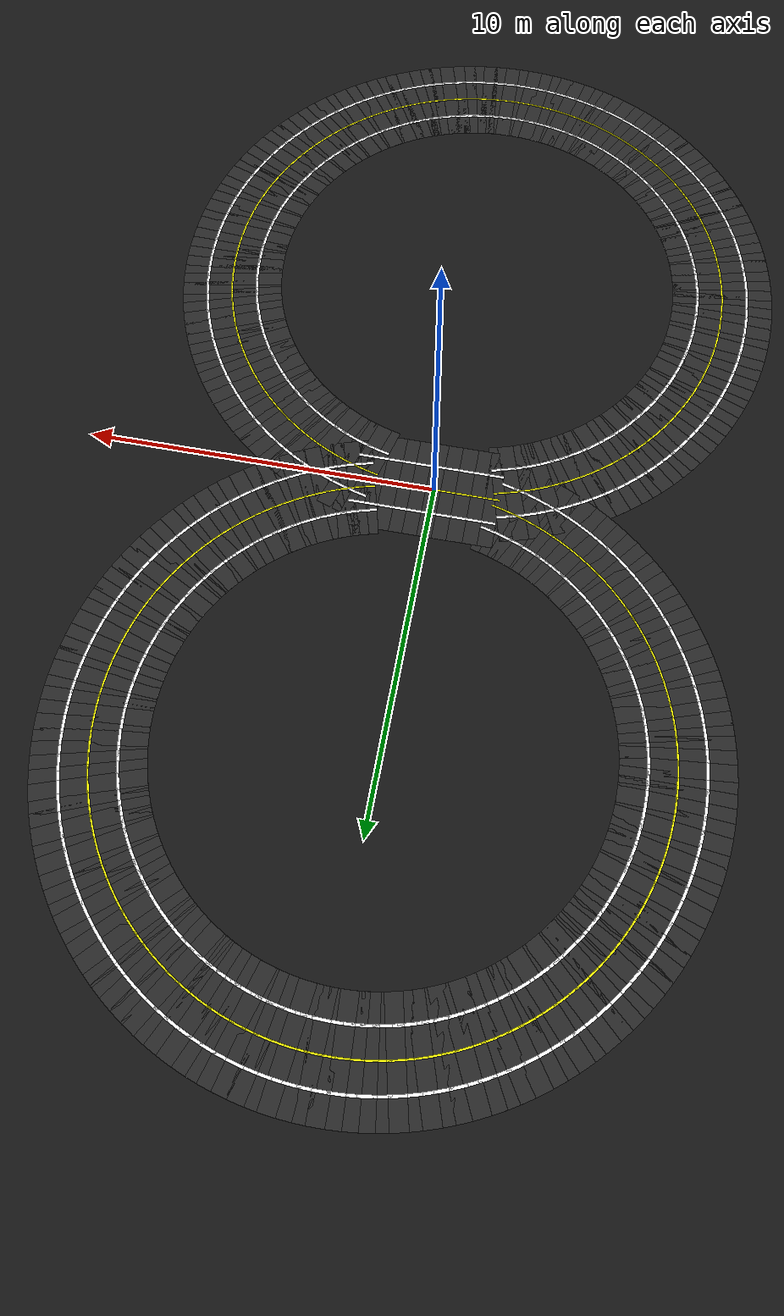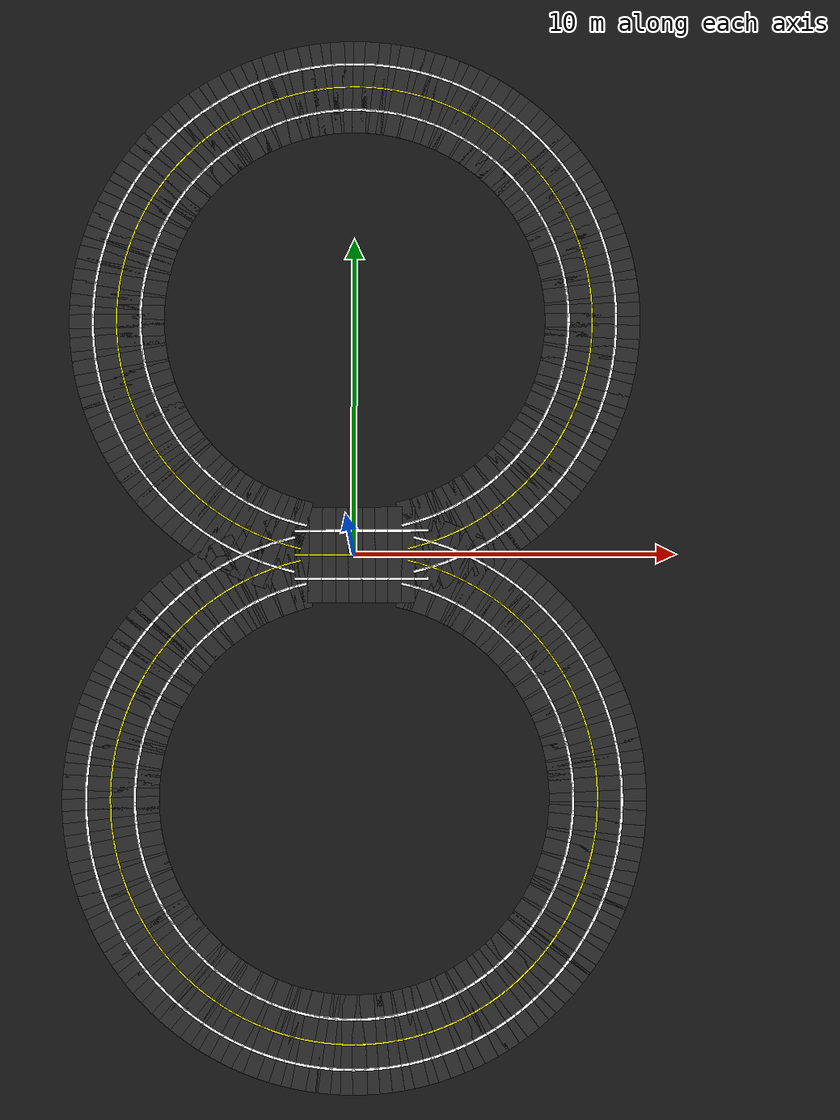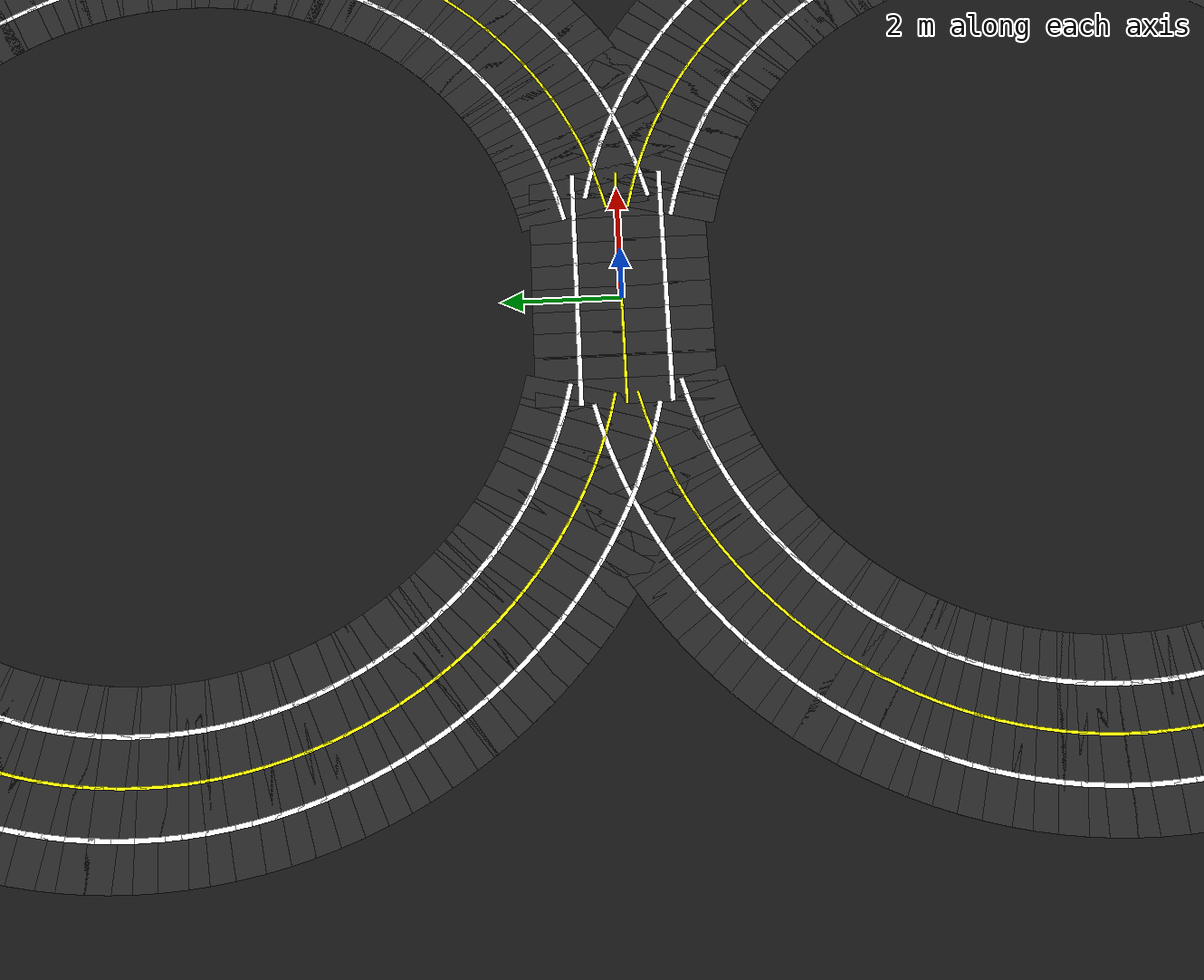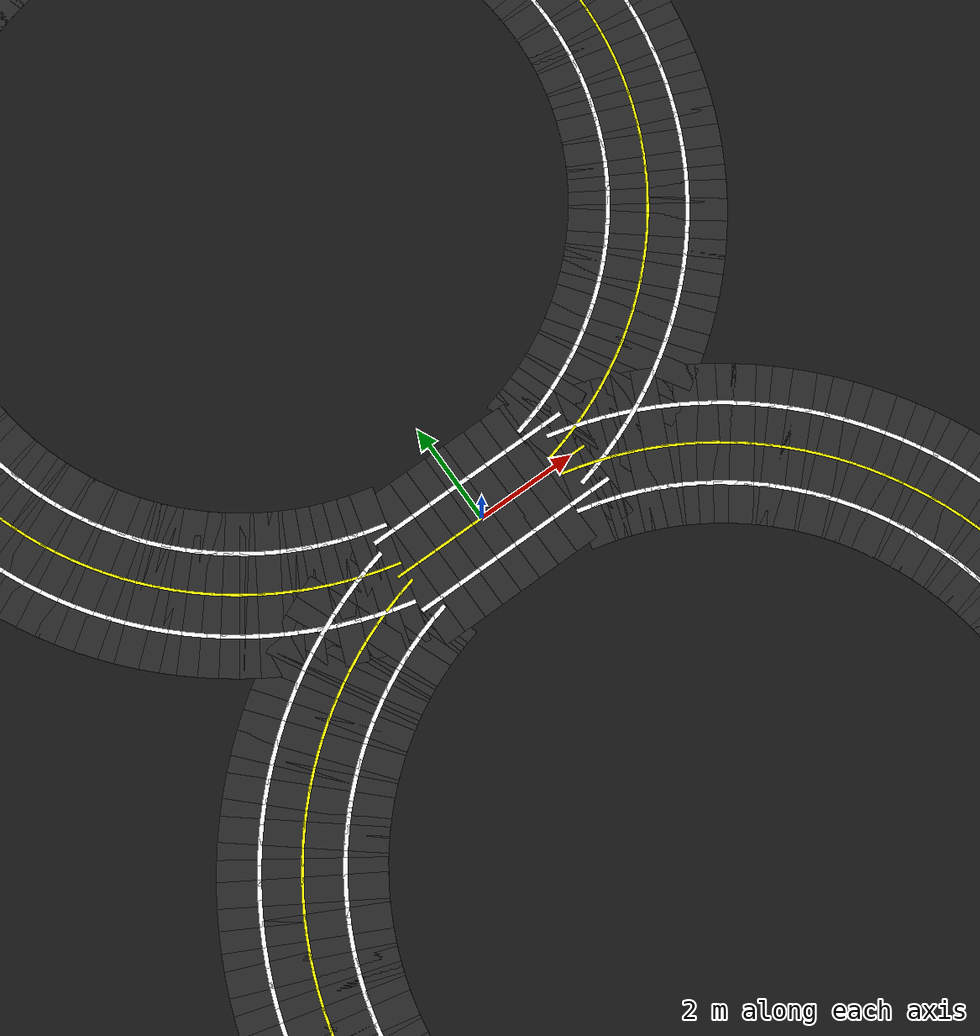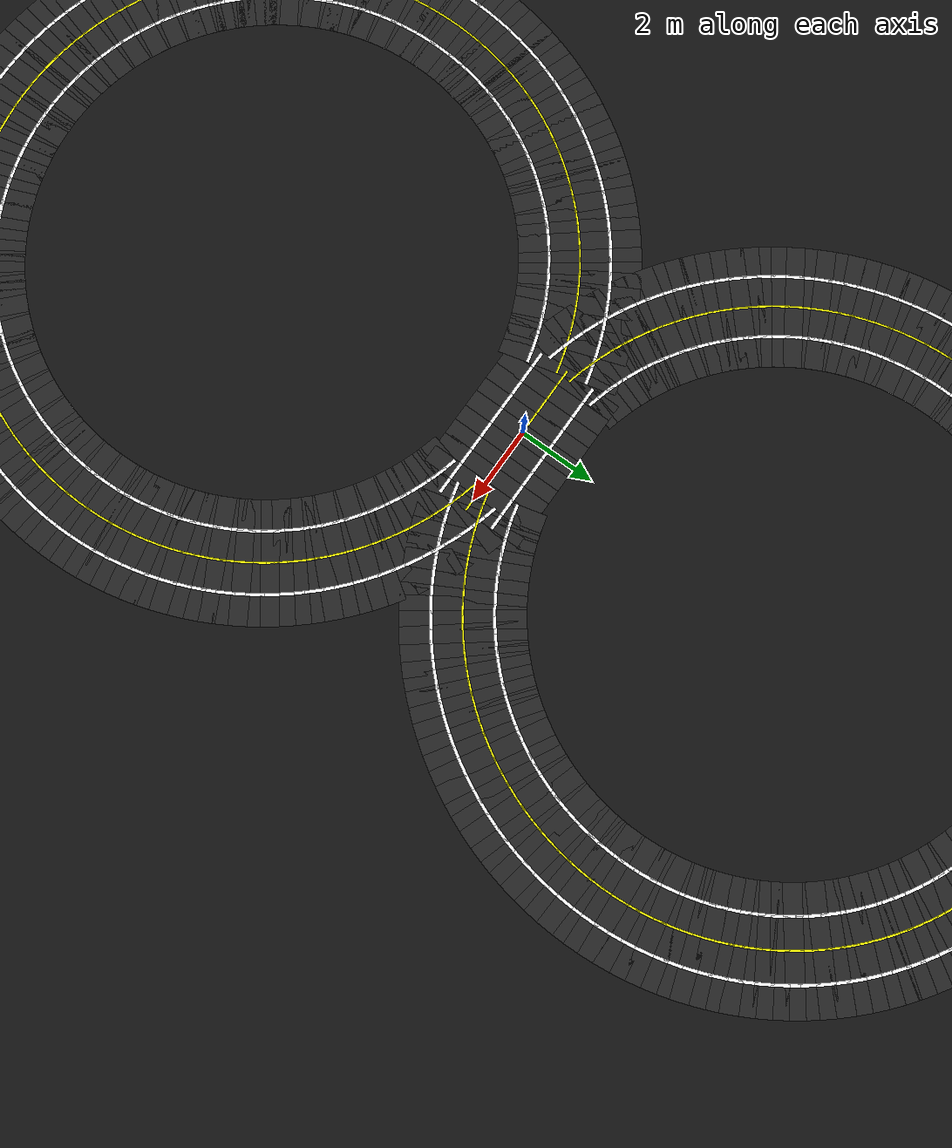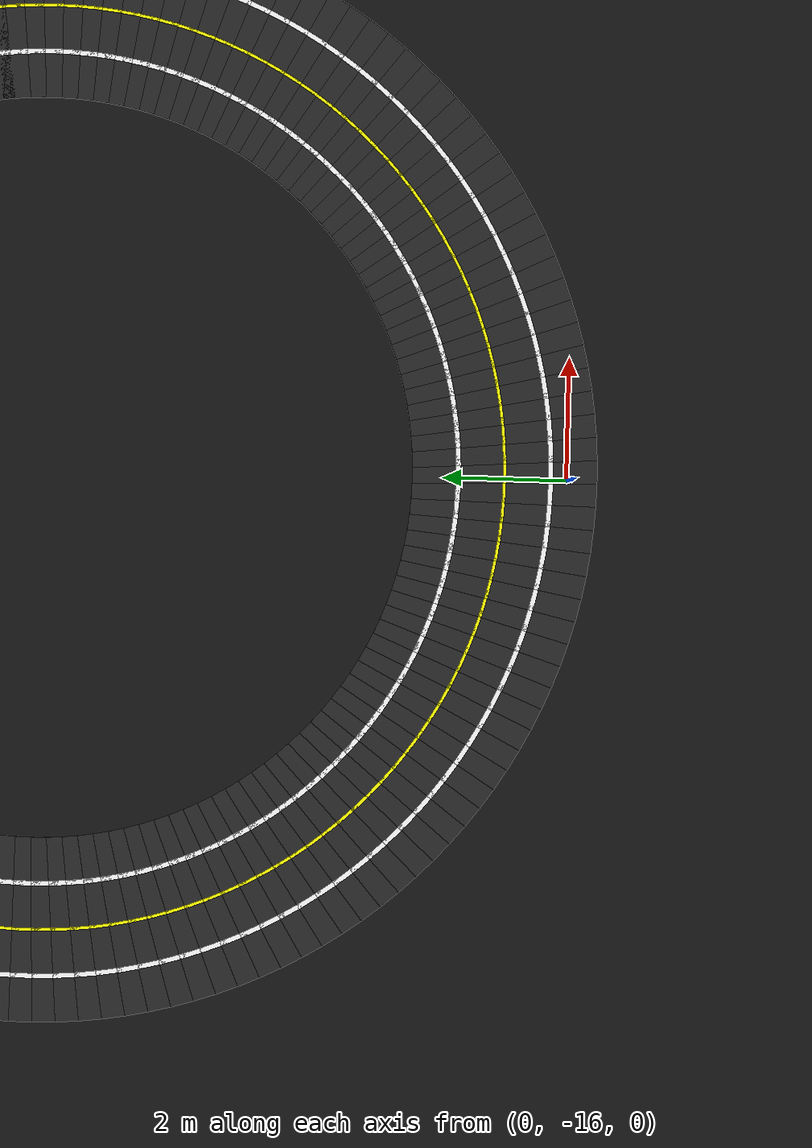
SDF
<?xml version="1.0" ?>
<sdf version="1.6">

  <world name="figure8_world">

    <!-- Physics -->
    <plugin
      filename="ignition-gazebo-physics-system"
      name="ignition::gazebo::systems::Physics"/>

    <!-- Sensors -->
    <plugin
      filename="libignition-gazebo-sensors-system.so"
      name="ignition::gazebo::systems::Sensors">

      <render_engine>ogre2</render_engine>

    </plugin>

    <!-- Scene broadcaster -->
    <plugin
      filename="ignition-gazebo-scene-broadcaster-system"
      name="ignition::gazebo::systems::SceneBroadcaster"/>

    <!-- User commands -->
    <plugin
      filename="ignition-gazebo-user-commands-system"
      name="ignition::gazebo::systems::UserCommands"/>

    <!-- Sun -->
    <light type="directional" name="sun">

      <cast_shadows>true</cast_shadows>

      <pose>0 0 30 0 0 0</pose>

      <diffuse>0.85 0.85 0.85 1</diffuse>
      <specular>0.2 0.2 0.2 1</specular>

      <direction>-0.4 0.1 -0.9</direction>

    </light>

    <!-- Ground -->
    <model name="ground_plane">

      <static>true</static>

      <link name="link">

        <collision name="collision">

          <geometry>
            <plane>
              <normal>0 0 1</normal>
              <size>100 100</size>
            </plane>
          </geometry>

        </collision>

        <visual name="visual">

          <geometry>
            <plane>
              <normal>0 0 1</normal>
              <size>100 100</size>
            </plane>
          </geometry>

          <material>

            <ambient>0.08 0.08 0.08 1</ambient>
            <diffuse>0.08 0.08 0.08 1</diffuse>

          </material>

        </visual>

      </link>

    </model>

    <model name="seg_00000">
      <static>true</static>

      <pose>1.8774 0.2388 0.0010 0 0 0.2530</pose>

      <link name="link">

        <collision name="collision">
          <geometry>
            <box>
              <size>0.4500 3.0000 0.002</size>
            </box>
          </geometry>
        </collision>

        <visual name="visual">
          <geometry>
            <box>
              <size>0.4500 3.0000 0.002</size>
            </box>
          </geometry>

          <material>

<ambient>0.15 0.15 0.15 1</ambient>
<diffuse>0.15 0.15 0.15 1</diffuse>

          </material>

        </visual>

      </link>
    </model>

    <model name="seg_00001">
      <static>true</static>

      <pose>2.0652 -0.4873 0.0030 0 0 0.2530</pose>

      <link name="link">

        <collision name="collision">
          <geometry>
            <box>
              <size>0.4500 0.0800 0.002</size>
            </box>
          </geometry>
        </collision>

        <visual name="visual">
          <geometry>
            <box>
              <size>0.4500 0.0800 0.002</size>
            </box>
          </geometry>

          <material>

<ambient>1 1 1 1</ambient>
<diffuse>1 1 1 1</diffuse>

          </material>

        </visual>

      </link>
    </model>

    <model name="seg_00002">
      <static>true</static>

      <pose>1.6897 0.9649 0.0030 0 0 0.2530</pose>

      <link name="link">

        <collision name="collision">
          <geometry>
            <box>
              <size>0.4500 0.0800 0.002</size>
            </box>
          </geometry>
        </collision>

        <visual name="visual">
          <geometry>
            <box>
              <size>0.4500 0.0800 0.002</size>
            </box>
          </geometry>

          <material>

<ambient>1 1 1 1</ambient>
<diffuse>1 1 1 1</diffuse>

          </material>

        </visual>

      </link>
    </model>

    <model name="seg_00003">
      <static>true</static>

      <pose>1.8774 0.2388 0.0030 0 0 0.2530</pose>

      <link name="link">

        <collision name="collision">
          <geometry>
            <box>
              <size>0.4500 0.0500 0.002</size>
            </box>
          </geometry>
        </collision>

        <visual name="visual">
          <geometry>
            <box>
              <size>0.4500 0.0500 0.002</size>
            </box>
          </geometry>

          <material>

<ambient>1 1 0 1</ambient>
<diffuse>1 1 0 1</diffuse>

          </material>

        </visual>

      </link>
    </model>

    <model name="seg_00004">
      <static>true</static>

      <pose>2.1819 0.3244 0.0010 0 0 0.2952</pose>

      <link name="link">

        <collision name="collision">
          <geometry>
            <box>
              <size>0.4500 3.0000 0.002</size>
            </box>
          </geometry>
        </collision>

        <visual name="visual">
          <geometry>
            <box>
              <size>0.4500 3.0000 0.002</size>
            </box>
          </geometry>

          <material>

<ambient>0.15 0.15 0.15 1</ambient>
<diffuse>0.15 0.15 0.15 1</diffuse>

          </material>

        </visual>

      </link>
    </model>

    <model name="seg_00005">
      <static>true</static>

      <pose>2.4000 -0.3932 0.0030 0 0 0.2952</pose>

      <link name="link">

        <collision name="collision">
          <geometry>
            <box>
              <size>0.4500 0.0800 0.002</size>
            </box>
          </geometry>
        </collision>

        <visual name="visual">
          <geometry>
            <box>
              <size>0.4500 0.0800 0.002</size>
            </box>
          </geometry>

          <material>

<ambient>1 1 1 1</ambient>
<diffuse>1 1 1 1</diffuse>

          </material>

        </visual>

      </link>
    </model>

    <model name="seg_00006">
      <static>true</static>

      <pose>1.9637 1.0419 0.0030 0 0 0.2952</pose>

      <link name="link">

        <collision name="collision">
          <geometry>
            <box>
              <size>0.4500 0.0800 0.002</size>
            </box>
          </geometry>
        </collision>

        <visual name="visual">
          <geometry>
            <box>
              <size>0.4500 0.0800 0.002</size>
            </box>
          </geometry>

          <material>

<ambient>1 1 1 1</ambient>
<diffuse>1 1 1 1</diffuse>

          </material>

        </visual>

      </link>
    </model>

    <model name="seg_00007">
      <static>true</static>

      <pose>2.1819 0.3244 0.0030 0 0 0.2952</pose>

      <link name="link">

        <collision name="collision">
          <geometry>
            <box>
              <size>0.4500 0.0500 0.002</size>
            </box>
          </geometry>
        </collision>

        <visual name="visual">
          <geometry>
            <box>
              <size>0.4500 0.0500 0.002</size>
            </box>
          </geometry>

          <material>

<ambient>1 1 0 1</ambient>
<diffuse>1 1 0 1</diffuse>

          </material>

        </visual>

      </link>
    </model>

    <model name="seg_00008">
      <static>true</static>

      <pose>2.4824 0.4227 0.0010 0 0 0.3374</pose>

      <link name="link">

        <collision name="collision">
          <geometry>
            <box>
              <size>0.4500 3.0000 0.002</size>
            </box>
          </geometry>
        </collision>

        <visual name="visual">
          <geometry>
            <box>
              <size>0.4500 3.0000 0.002</size>
            </box>
          </geometry>

          <material>

<ambient>0.15 0.15 0.15 1</ambient>
<diffuse>0.15 0.15 0.15 1</diffuse>

          </material>

        </visual>

      </link>
    </model>

    <model name="seg_00009">
      <static>true</static>

      <pose>2.7307 -0.2850 0.0030 0 0 0.3374</pose>

      <link name="link">

        <collision name="collision">
          <geometry>
            <box>
              <size>0.4500 0.0800 0.002</size>
            </box>
          </geometry>
        </collision>

        <visual name="visual">
          <geometry>
            <box>
              <size>0.4500 0.0800 0.002</size>
            </box>
          </geometry>

          <material>

<ambient>1 1 1 1</ambient>
<diffuse>1 1 1 1</diffuse>

          </material>

        </visual>

      </link>
    </model>

    <model name="seg_00010">
      <static>true</static>

      <pose>2.2342 1.1305 0.0030 0 0 0.3374</pose>

      <link name="link">

        <collision name="collision">
          <geometry>
            <box>
              <size>0.4500 0.0800 0.002</size>
            </box>
          </geometry>
        </collision>

        <visual name="visual">
          <geometry>
            <box>
              <size>0.4500 0.0800 0.002</size>
            </box>
          </geometry>

          <material>

<ambient>1 1 1 1</ambient>
<diffuse>1 1 1 1</diffuse>

          </material>

        </visual>

      </link>
    </model>

    <model name="seg_00011">
      <static>true</static>

      <pose>2.4824 0.4227 0.0030 0 0 0.3374</pose>

      <link name="link">

        <collision name="collision">
          <geometry>
            <box>
              <size>0.4500 0.0500 0.002</size>
            </box>
          </geometry>
        </collision>

        <visual name="visual">
          <geometry>
            <box>
              <size>0.4500 0.0500 0.002</size>
            </box>
          </geometry>

          <material>

<ambient>1 1 0 1</ambient>
<diffuse>1 1 0 1</diffuse>

          </material>

        </visual>

      </link>
    </model>

    <model name="seg_00012">
      <static>true</static>

      <pose>2.7786 0.5337 0.0010 0 0 0.3795</pose>

      <link name="link">

        <collision name="collision">
          <geometry>
            <box>
              <size>0.4500 3.0000 0.002</size>
            </box>
          </geometry>
        </collision>

        <visual name="visual">
          <geometry>
            <box>
              <size>0.4500 3.0000 0.002</size>
            </box>
          </geometry>

          <material>

<ambient>0.15 0.15 0.15 1</ambient>
<diffuse>0.15 0.15 0.15 1</diffuse>

          </material>

        </visual>

      </link>
    </model>

    <model name="seg_00013">
      <static>true</static>

      <pose>3.0564 -0.1629 0.0030 0 0 0.3795</pose>

      <link name="link">

        <collision name="collision">
          <geometry>
            <box>
              <size>0.4500 0.0800 0.002</size>
            </box>
          </geometry>
        </collision>

        <visual name="visual">
          <geometry>
            <box>
              <size>0.4500 0.0800 0.002</size>
            </box>
          </geometry>

          <material>

<ambient>1 1 1 1</ambient>
<diffuse>1 1 1 1</diffuse>

          </material>

        </visual>

      </link>
    </model>

    <model name="seg_00014">
      <static>true</static>

      <pose>2.5007 1.2303 0.0030 0 0 0.3795</pose>

      <link name="link">

        <collision name="collision">
          <geometry>
            <box>
              <size>0.4500 0.0800 0.002</size>
            </box>
          </geometry>
        </collision>

        <visual name="visual">
          <geometry>
            <box>
              <size>0.4500 0.0800 0.002</size>
            </box>
          </geometry>

          <material>

<ambient>1 1 1 1</ambient>
<diffuse>1 1 1 1</diffuse>

          </material>

        </visual>

      </link>
    </model>

    <model name="seg_00015">
      <static>true</static>

      <pose>2.7786 0.5337 0.0030 0 0 0.3795</pose>

      <link name="link">

        <collision name="collision">
          <geometry>
            <box>
              <size>0.4500 0.0500 0.002</size>
            </box>
          </geometry>
        </collision>

        <visual name="visual">
          <geometry>
            <box>
              <size>0.4500 0.0500 0.002</size>
            </box>
          </geometry>

          <material>

<ambient>1 1 0 1</ambient>
<diffuse>1 1 0 1</diffuse>

          </material>

        </visual>

      </link>
    </model>

    <model name="seg_00016">
      <static>true</static>

      <pose>3.0698 0.6570 0.0010 0 0 0.4217</pose>

      <link name="link">

        <collision name="collision">
          <geometry>
            <box>
              <size>0.4500 3.0000 0.002</size>
            </box>
          </geometry>
        </collision>

        <visual name="visual">
          <geometry>
            <box>
              <size>0.4500 3.0000 0.002</size>
            </box>
          </geometry>

          <material>

<ambient>0.15 0.15 0.15 1</ambient>
<diffuse>0.15 0.15 0.15 1</diffuse>

          </material>

        </visual>

      </link>
    </model>

    <model name="seg_00017">
      <static>true</static>

      <pose>3.3768 -0.0273 0.0030 0 0 0.4217</pose>

      <link name="link">

        <collision name="collision">
          <geometry>
            <box>
              <size>0.4500 0.0800 0.002</size>
            </box>
          </geometry>
        </collision>

        <visual name="visual">
          <geometry>
            <box>
              <size>0.4500 0.0800 0.002</size>
            </box>
          </geometry>

          <material>

<ambient>1 1 1 1</ambient>
<diffuse>1 1 1 1</diffuse>

          </material>

        </visual>

      </link>
    </model>

    <model name="seg_00018">
      <static>true</static>

      <pose>2.7628 1.3413 0.0030 0 0 0.4217</pose>

      <link name="link">

        <collision name="collision">
          <geometry>
            <box>
              <size>0.4500 0.0800 0.002</size>
            </box>
          </geometry>
        </collision>

        <visual name="visual">
          <geometry>
            <box>
              <size>0.4500 0.0800 0.002</size>
            </box>
          </geometry>

          <material>

<ambient>1 1 1 1</ambient>
<diffuse>1 1 1 1</diffuse>

          </material>

        </visual>

      </link>
    </model>

    <model name="seg_00019">
      <static>true</static>

      <pose>3.0698 0.6570 0.0030 0 0 0.4217</pose>

      <link name="link">

        <collision name="collision">
          <geometry>
            <box>
              <size>0.4500 0.0500 0.002</size>
            </box>
          </geometry>
        </collision>

        <visual name="visual">
          <geometry>
            <box>
              <size>0.4500 0.0500 0.002</size>
            </box>
          </geometry>

          <material>

<ambient>1 1 0 1</ambient>
<diffuse>1 1 0 1</diffuse>

          </material>

        </visual>

      </link>
    </model>

    <model name="seg_00020">
      <static>true</static>

      <pose>3.3555 0.7925 0.0010 0 0 0.4639</pose>

      <link name="link">

        <collision name="collision">
          <geometry>
            <box>
              <size>0.4500 3.0000 0.002</size>
            </box>
          </geometry>
        </collision>

        <visual name="visual">
          <geometry>
            <box>
              <size>0.4500 3.0000 0.002</size>
            </box>
          </geometry>

          <material>

<ambient>0.15 0.15 0.15 1</ambient>
<diffuse>0.15 0.15 0.15 1</diffuse>

          </material>

        </visual>

      </link>
    </model>

    <model name="seg_00021">
      <static>true</static>

      <pose>3.6911 0.1218 0.0030 0 0 0.4639</pose>

      <link name="link">

        <collision name="collision">
          <geometry>
            <box>
              <size>0.4500 0.0800 0.002</size>
            </box>
          </geometry>
        </collision>

        <visual name="visual">
          <geometry>
            <box>
              <size>0.4500 0.0800 0.002</size>
            </box>
          </geometry>

          <material>

<ambient>1 1 1 1</ambient>
<diffuse>1 1 1 1</diffuse>

          </material>

        </visual>

      </link>
    </model>

    <model name="seg_00022">
      <static>true</static>

      <pose>3.0200 1.4633 0.0030 0 0 0.4639</pose>

      <link name="link">

        <collision name="collision">
          <geometry>
            <box>
              <size>0.4500 0.0800 0.002</size>
            </box>
          </geometry>
        </collision>

        <visual name="visual">
          <geometry>
            <box>
              <size>0.4500 0.0800 0.002</size>
            </box>
          </geometry>

          <material>

<ambient>1 1 1 1</ambient>
<diffuse>1 1 1 1</diffuse>

          </material>

        </visual>

      </link>
    </model>

    <model name="seg_00023">
      <static>true</static>

      <pose>3.3555 0.7925 0.0030 0 0 0.4639</pose>

      <link name="link">

        <collision name="collision">
          <geometry>
            <box>
              <size>0.4500 0.0500 0.002</size>
            </box>
          </geometry>
        </collision>

        <visual name="visual">
          <geometry>
            <box>
              <size>0.4500 0.0500 0.002</size>
            </box>
          </geometry>

          <material>

<ambient>1 1 0 1</ambient>
<diffuse>1 1 0 1</diffuse>

          </material>

        </visual>

      </link>
    </model>

    <model name="seg_00024">
      <static>true</static>

      <pose>3.6353 0.9399 0.0010 0 0 0.5060</pose>

      <link name="link">

        <collision name="collision">
          <geometry>
            <box>
              <size>0.4500 3.0000 0.002</size>
            </box>
          </geometry>
        </collision>

        <visual name="visual">
          <geometry>
            <box>
              <size>0.4500 3.0000 0.002</size>
            </box>
          </geometry>

          <material>

<ambient>0.15 0.15 0.15 1</ambient>
<diffuse>0.15 0.15 0.15 1</diffuse>

          </material>

        </visual>

      </link>
    </model>

    <model name="seg_00025">
      <static>true</static>

      <pose>3.9988 0.2839 0.0030 0 0 0.5060</pose>

      <link name="link">

        <collision name="collision">
          <geometry>
            <box>
              <size>0.4500 0.0800 0.002</size>
            </box>
          </geometry>
        </collision>

        <visual name="visual">
          <geometry>
            <box>
              <size>0.4500 0.0800 0.002</size>
            </box>
          </geometry>

          <material>

<ambient>1 1 1 1</ambient>
<diffuse>1 1 1 1</diffuse>

          </material>

        </visual>

      </link>
    </model>

    <model name="seg_00026">
      <static>true</static>

      <pose>3.2718 1.5959 0.0030 0 0 0.5060</pose>

      <link name="link">

        <collision name="collision">
          <geometry>
            <box>
              <size>0.4500 0.0800 0.002</size>
            </box>
          </geometry>
        </collision>

        <visual name="visual">
          <geometry>
            <box>
              <size>0.4500 0.0800 0.002</size>
            </box>
          </geometry>

          <material>

<ambient>1 1 1 1</ambient>
<diffuse>1 1 1 1</diffuse>

          </material>

        </visual>

      </link>
    </model>

    <model name="seg_00027">
      <static>true</static>

      <pose>3.6353 0.9399 0.0030 0 0 0.5060</pose>

      <link name="link">

        <collision name="collision">
          <geometry>
            <box>
              <size>0.4500 0.0500 0.002</size>
            </box>
          </geometry>
        </collision>

        <visual name="visual">
          <geometry>
            <box>
              <size>0.4500 0.0500 0.002</size>
            </box>
          </geometry>

          <material>

<ambient>1 1 0 1</ambient>
<diffuse>1 1 0 1</diffuse>

          </material>

        </visual>

      </link>
    </model>

    <model name="seg_00028">
      <static>true</static>

      <pose>3.9086 1.0990 0.0010 0 0 0.5482</pose>

      <link name="link">

        <collision name="collision">
          <geometry>
            <box>
              <size>0.4500 3.0000 0.002</size>
            </box>
          </geometry>
        </collision>

        <visual name="visual">
          <geometry>
            <box>
              <size>0.4500 3.0000 0.002</size>
            </box>
          </geometry>

          <material>

<ambient>0.15 0.15 0.15 1</ambient>
<diffuse>0.15 0.15 0.15 1</diffuse>

          </material>

        </visual>

      </link>
    </model>

    <model name="seg_00029">
      <static>true</static>

      <pose>4.2995 0.4589 0.0030 0 0 0.5482</pose>

      <link name="link">

        <collision name="collision">
          <geometry>
            <box>
              <size>0.4500 0.0800 0.002</size>
            </box>
          </geometry>
        </collision>

        <visual name="visual">
          <geometry>
            <box>
              <size>0.4500 0.0800 0.002</size>
            </box>
          </geometry>

          <material>

<ambient>1 1 1 1</ambient>
<diffuse>1 1 1 1</diffuse>

          </material>

        </visual>

      </link>
    </model>

    <model name="seg_00030">
      <static>true</static>

      <pose>3.5178 1.7391 0.0030 0 0 0.5482</pose>

      <link name="link">

        <collision name="collision">
          <geometry>
            <box>
              <size>0.4500 0.0800 0.002</size>
            </box>
          </geometry>
        </collision>

        <visual name="visual">
          <geometry>
            <box>
              <size>0.4500 0.0800 0.002</size>
            </box>
          </geometry>

          <material>

<ambient>1 1 1 1</ambient>
<diffuse>1 1 1 1</diffuse>

          </material>

        </visual>

      </link>
    </model>

    <model name="seg_00031">
      <static>true</static>

      <pose>3.9086 1.0990 0.0030 0 0 0.5482</pose>

      <link name="link">

        <collision name="collision">
          <geometry>
            <box>
              <size>0.4500 0.0500 0.002</size>
            </box>
          </geometry>
        </collision>

        <visual name="visual">
          <geometry>
            <box>
              <size>0.4500 0.0500 0.002</size>
            </box>
          </geometry>

          <material>

<ambient>1 1 0 1</ambient>
<diffuse>1 1 0 1</diffuse>

          </material>

        </visual>

      </link>
    </model>

    <model name="seg_00032">
      <static>true</static>

      <pose>4.1750 1.2695 0.0010 0 0 0.5904</pose>

      <link name="link">

        <collision name="collision">
          <geometry>
            <box>
              <size>0.4500 3.0000 0.002</size>
            </box>
          </geometry>
        </collision>

        <visual name="visual">
          <geometry>
            <box>
              <size>0.4500 3.0000 0.002</size>
            </box>
          </geometry>

          <material>

<ambient>0.15 0.15 0.15 1</ambient>
<diffuse>0.15 0.15 0.15 1</diffuse>

          </material>

        </visual>

      </link>
    </model>

    <model name="seg_00033">
      <static>true</static>

      <pose>4.5925 0.6464 0.0030 0 0 0.5904</pose>

      <link name="link">

        <collision name="collision">
          <geometry>
            <box>
              <size>0.4500 0.0800 0.002</size>
            </box>
          </geometry>
        </collision>

        <visual name="visual">
          <geometry>
            <box>
              <size>0.4500 0.0800 0.002</size>
            </box>
          </geometry>

          <material>

<ambient>1 1 1 1</ambient>
<diffuse>1 1 1 1</diffuse>

          </material>

        </visual>

      </link>
    </model>

    <model name="seg_00034">
      <static>true</static>

      <pose>3.7575 1.8925 0.0030 0 0 0.5904</pose>

      <link name="link">

        <collision name="collision">
          <geometry>
            <box>
              <size>0.4500 0.0800 0.002</size>
            </box>
          </geometry>
        </collision>

        <visual name="visual">
          <geometry>
            <box>
              <size>0.4500 0.0800 0.002</size>
            </box>
          </geometry>

          <material>

<ambient>1 1 1 1</ambient>
<diffuse>1 1 1 1</diffuse>

          </material>

        </visual>

      </link>
    </model>

    <model name="seg_00035">
      <static>true</static>

      <pose>4.1750 1.2695 0.0030 0 0 0.5904</pose>

      <link name="link">

        <collision name="collision">
          <geometry>
            <box>
              <size>0.4500 0.0500 0.002</size>
            </box>
          </geometry>
        </collision>

        <visual name="visual">
          <geometry>
            <box>
              <size>0.4500 0.0500 0.002</size>
            </box>
          </geometry>

          <material>

<ambient>1 1 0 1</ambient>
<diffuse>1 1 0 1</diffuse>

          </material>

        </visual>

      </link>
    </model>

    <model name="seg_00036">
      <static>true</static>

      <pose>4.4339 1.4510 0.0010 0 0 0.6325</pose>

      <link name="link">

        <collision name="collision">
          <geometry>
            <box>
              <size>0.4500 3.0000 0.002</size>
            </box>
          </geometry>
        </collision>

        <visual name="visual">
          <geometry>
            <box>
              <size>0.4500 3.0000 0.002</size>
            </box>
          </geometry>

          <material>

<ambient>0.15 0.15 0.15 1</ambient>
<diffuse>0.15 0.15 0.15 1</diffuse>

          </material>

        </visual>

      </link>
    </model>

    <model name="seg_00037">
      <static>true</static>

      <pose>4.8773 0.8461 0.0030 0 0 0.6325</pose>

      <link name="link">

        <collision name="collision">
          <geometry>
            <box>
              <size>0.4500 0.0800 0.002</size>
            </box>
          </geometry>
        </collision>

        <visual name="visual">
          <geometry>
            <box>
              <size>0.4500 0.0800 0.002</size>
            </box>
          </geometry>

          <material>

<ambient>1 1 1 1</ambient>
<diffuse>1 1 1 1</diffuse>

          </material>

        </visual>

      </link>
    </model>

    <model name="seg_00038">
      <static>true</static>

      <pose>3.9905 2.0559 0.0030 0 0 0.6325</pose>

      <link name="link">

        <collision name="collision">
          <geometry>
            <box>
              <size>0.4500 0.0800 0.002</size>
            </box>
          </geometry>
        </collision>

        <visual name="visual">
          <geometry>
            <box>
              <size>0.4500 0.0800 0.002</size>
            </box>
          </geometry>

          <material>

<ambient>1 1 1 1</ambient>
<diffuse>1 1 1 1</diffuse>

          </material>

        </visual>

      </link>
    </model>

    <model name="seg_00039">
      <static>true</static>

      <pose>4.4339 1.4510 0.0030 0 0 0.6325</pose>

      <link name="link">

        <collision name="collision">
          <geometry>
            <box>
              <size>0.4500 0.0500 0.002</size>
            </box>
          </geometry>
        </collision>

        <visual name="visual">
          <geometry>
            <box>
              <size>0.4500 0.0500 0.002</size>
            </box>
          </geometry>

          <material>

<ambient>1 1 0 1</ambient>
<diffuse>1 1 0 1</diffuse>

          </material>

        </visual>

      </link>
    </model>

    <model name="seg_00040">
      <static>true</static>

      <pose>4.6850 1.6433 0.0010 0 0 0.6747</pose>

      <link name="link">

        <collision name="collision">
          <geometry>
            <box>
              <size>0.4500 3.0000 0.002</size>
            </box>
          </geometry>
        </collision>

        <visual name="visual">
          <geometry>
            <box>
              <size>0.4500 3.0000 0.002</size>
            </box>
          </geometry>

          <material>

<ambient>0.15 0.15 0.15 1</ambient>
<diffuse>0.15 0.15 0.15 1</diffuse>

          </material>

        </visual>

      </link>
    </model>

    <model name="seg_00041">
      <static>true</static>

      <pose>5.1535 1.0576 0.0030 0 0 0.6747</pose>

      <link name="link">

        <collision name="collision">
          <geometry>
            <box>
              <size>0.4500 0.0800 0.002</size>
            </box>
          </geometry>
        </collision>

        <visual name="visual">
          <geometry>
            <box>
              <size>0.4500 0.0800 0.002</size>
            </box>
          </geometry>

          <material>

<ambient>1 1 1 1</ambient>
<diffuse>1 1 1 1</diffuse>

          </material>

        </visual>

      </link>
    </model>

    <model name="seg_00042">
      <static>true</static>

      <pose>4.2165 2.2290 0.0030 0 0 0.6747</pose>

      <link name="link">

        <collision name="collision">
          <geometry>
            <box>
              <size>0.4500 0.0800 0.002</size>
            </box>
          </geometry>
        </collision>

        <visual name="visual">
          <geometry>
            <box>
              <size>0.4500 0.0800 0.002</size>
            </box>
          </geometry>

          <material>

<ambient>1 1 1 1</ambient>
<diffuse>1 1 1 1</diffuse>

          </material>

        </visual>

      </link>
    </model>

    <model name="seg_00043">
      <static>true</static>

      <pose>4.6850 1.6433 0.0030 0 0 0.6747</pose>

      <link name="link">

        <collision name="collision">
          <geometry>
            <box>
              <size>0.4500 0.0500 0.002</size>
            </box>
          </geometry>
        </collision>

        <visual name="visual">
          <geometry>
            <box>
              <size>0.4500 0.0500 0.002</size>
            </box>
          </geometry>

          <material>

<ambient>1 1 0 1</ambient>
<diffuse>1 1 0 1</diffuse>

          </material>

        </visual>

      </link>
    </model>

    <model name="seg_00044">
      <static>true</static>

      <pose>4.9277 1.8460 0.0010 0 0 0.7169</pose>

      <link name="link">

        <collision name="collision">
          <geometry>
            <box>
              <size>0.4500 3.0000 0.002</size>
            </box>
          </geometry>
        </collision>

        <visual name="visual">
          <geometry>
            <box>
              <size>0.4500 3.0000 0.002</size>
            </box>
          </geometry>

          <material>

<ambient>0.15 0.15 0.15 1</ambient>
<diffuse>0.15 0.15 0.15 1</diffuse>

          </material>

        </visual>

      </link>
    </model>

    <model name="seg_00045">
      <static>true</static>

      <pose>5.4205 1.2806 0.0030 0 0 0.7169</pose>

      <link name="link">

        <collision name="collision">
          <geometry>
            <box>
              <size>0.4500 0.0800 0.002</size>
            </box>
          </geometry>
        </collision>

        <visual name="visual">
          <geometry>
            <box>
              <size>0.4500 0.0800 0.002</size>
            </box>
          </geometry>

          <material>

<ambient>1 1 1 1</ambient>
<diffuse>1 1 1 1</diffuse>

          </material>

        </visual>

      </link>
    </model>

    <model name="seg_00046">
      <static>true</static>

      <pose>4.4350 2.4114 0.0030 0 0 0.7169</pose>

      <link name="link">

        <collision name="collision">
          <geometry>
            <box>
              <size>0.4500 0.0800 0.002</size>
            </box>
          </geometry>
        </collision>

        <visual name="visual">
          <geometry>
            <box>
              <size>0.4500 0.0800 0.002</size>
            </box>
          </geometry>

          <material>

<ambient>1 1 1 1</ambient>
<diffuse>1 1 1 1</diffuse>

          </material>

        </visual>

      </link>
    </model>

    <model name="seg_00047">
      <static>true</static>

      <pose>4.9277 1.8460 0.0030 0 0 0.7169</pose>

      <link name="link">

        <collision name="collision">
          <geometry>
            <box>
              <size>0.4500 0.0500 0.002</size>
            </box>
          </geometry>
        </collision>

        <visual name="visual">
          <geometry>
            <box>
              <size>0.4500 0.0500 0.002</size>
            </box>
          </geometry>

          <material>

<ambient>1 1 0 1</ambient>
<diffuse>1 1 0 1</diffuse>

          </material>

        </visual>

      </link>
    </model>

    <model name="seg_00048">
      <static>true</static>

      <pose>5.1617 2.0588 0.0010 0 0 0.7590</pose>

      <link name="link">

        <collision name="collision">
          <geometry>
            <box>
              <size>0.4500 3.0000 0.002</size>
            </box>
          </geometry>
        </collision>

        <visual name="visual">
          <geometry>
            <box>
              <size>0.4500 3.0000 0.002</size>
            </box>
          </geometry>

          <material>

<ambient>0.15 0.15 0.15 1</ambient>
<diffuse>0.15 0.15 0.15 1</diffuse>

          </material>

        </visual>

      </link>
    </model>

    <model name="seg_00049">
      <static>true</static>

      <pose>5.6779 1.5147 0.0030 0 0 0.7590</pose>

      <link name="link">

        <collision name="collision">
          <geometry>
            <box>
              <size>0.4500 0.0800 0.002</size>
            </box>
          </geometry>
        </collision>

        <visual name="visual">
          <geometry>
            <box>
              <size>0.4500 0.0800 0.002</size>
            </box>
          </geometry>

          <material>

<ambient>1 1 1 1</ambient>
<diffuse>1 1 1 1</diffuse>

          </material>

        </visual>

      </link>
    </model>

    <model name="seg_00050">
      <static>true</static>

      <pose>4.6455 2.6029 0.0030 0 0 0.7590</pose>

      <link name="link">

        <collision name="collision">
          <geometry>
            <box>
              <size>0.4500 0.0800 0.002</size>
            </box>
          </geometry>
        </collision>

        <visual name="visual">
          <geometry>
            <box>
              <size>0.4500 0.0800 0.002</size>
            </box>
          </geometry>

          <material>

<ambient>1 1 1 1</ambient>
<diffuse>1 1 1 1</diffuse>

          </material>

        </visual>

      </link>
    </model>

    <model name="seg_00051">
      <static>true</static>

      <pose>5.1617 2.0588 0.0030 0 0 0.7590</pose>

      <link name="link">

        <collision name="collision">
          <geometry>
            <box>
              <size>0.4500 0.0500 0.002</size>
            </box>
          </geometry>
        </collision>

        <visual name="visual">
          <geometry>
            <box>
              <size>0.4500 0.0500 0.002</size>
            </box>
          </geometry>

          <material>

<ambient>1 1 0 1</ambient>
<diffuse>1 1 0 1</diffuse>

          </material>

        </visual>

      </link>
    </model>

    <model name="seg_00052">
      <static>true</static>

      <pose>5.3865 2.2812 0.0010 0 0 0.8012</pose>

      <link name="link">

        <collision name="collision">
          <geometry>
            <box>
              <size>0.4500 3.0000 0.002</size>
            </box>
          </geometry>
        </collision>

        <visual name="visual">
          <geometry>
            <box>
              <size>0.4500 3.0000 0.002</size>
            </box>
          </geometry>

          <material>

<ambient>0.15 0.15 0.15 1</ambient>
<diffuse>0.15 0.15 0.15 1</diffuse>

          </material>

        </visual>

      </link>
    </model>

    <model name="seg_00053">
      <static>true</static>

      <pose>5.9251 1.7593 0.0030 0 0 0.8012</pose>

      <link name="link">

        <collision name="collision">
          <geometry>
            <box>
              <size>0.4500 0.0800 0.002</size>
            </box>
          </geometry>
        </collision>

        <visual name="visual">
          <geometry>
            <box>
              <size>0.4500 0.0800 0.002</size>
            </box>
          </geometry>

          <material>

<ambient>1 1 1 1</ambient>
<diffuse>1 1 1 1</diffuse>

          </material>

        </visual>

      </link>
    </model>

    <model name="seg_00054">
      <static>true</static>

      <pose>4.8478 2.8031 0.0030 0 0 0.8012</pose>

      <link name="link">

        <collision name="collision">
          <geometry>
            <box>
              <size>0.4500 0.0800 0.002</size>
            </box>
          </geometry>
        </collision>

        <visual name="visual">
          <geometry>
            <box>
              <size>0.4500 0.0800 0.002</size>
            </box>
          </geometry>

          <material>

<ambient>1 1 1 1</ambient>
<diffuse>1 1 1 1</diffuse>

          </material>

        </visual>

      </link>
    </model>

    <model name="seg_00055">
      <static>true</static>

      <pose>5.3865 2.2812 0.0030 0 0 0.8012</pose>

      <link name="link">

        <collision name="collision">
          <geometry>
            <box>
              <size>0.4500 0.0500 0.002</size>
            </box>
          </geometry>
        </collision>

        <visual name="visual">
          <geometry>
            <box>
              <size>0.4500 0.0500 0.002</size>
            </box>
          </geometry>

          <material>

<ambient>1 1 0 1</ambient>
<diffuse>1 1 0 1</diffuse>

          </material>

        </visual>

      </link>
    </model>

    <model name="seg_00056">
      <static>true</static>

      <pose>5.6017 2.5129 0.0010 0 0 0.8434</pose>

      <link name="link">

        <collision name="collision">
          <geometry>
            <box>
              <size>0.4500 3.0000 0.002</size>
            </box>
          </geometry>
        </collision>

        <visual name="visual">
          <geometry>
            <box>
              <size>0.4500 3.0000 0.002</size>
            </box>
          </geometry>

          <material>

<ambient>0.15 0.15 0.15 1</ambient>
<diffuse>0.15 0.15 0.15 1</diffuse>

          </material>

        </visual>

      </link>
    </model>

    <model name="seg_00057">
      <static>true</static>

      <pose>6.1619 2.0142 0.0030 0 0 0.8434</pose>

      <link name="link">

        <collision name="collision">
          <geometry>
            <box>
              <size>0.4500 0.0800 0.002</size>
            </box>
          </geometry>
        </collision>

        <visual name="visual">
          <geometry>
            <box>
              <size>0.4500 0.0800 0.002</size>
            </box>
          </geometry>

          <material>

<ambient>1 1 1 1</ambient>
<diffuse>1 1 1 1</diffuse>

          </material>

        </visual>

      </link>
    </model>

    <model name="seg_00058">
      <static>true</static>

      <pose>5.0415 3.0116 0.0030 0 0 0.8434</pose>

      <link name="link">

        <collision name="collision">
          <geometry>
            <box>
              <size>0.4500 0.0800 0.002</size>
            </box>
          </geometry>
        </collision>

        <visual name="visual">
          <geometry>
            <box>
              <size>0.4500 0.0800 0.002</size>
            </box>
          </geometry>

          <material>

<ambient>1 1 1 1</ambient>
<diffuse>1 1 1 1</diffuse>

          </material>

        </visual>

      </link>
    </model>

    <model name="seg_00059">
      <static>true</static>

      <pose>5.6017 2.5129 0.0030 0 0 0.8434</pose>

      <link name="link">

        <collision name="collision">
          <geometry>
            <box>
              <size>0.4500 0.0500 0.002</size>
            </box>
          </geometry>
        </collision>

        <visual name="visual">
          <geometry>
            <box>
              <size>0.4500 0.0500 0.002</size>
            </box>
          </geometry>

          <material>

<ambient>1 1 0 1</ambient>
<diffuse>1 1 0 1</diffuse>

          </material>

        </visual>

      </link>
    </model>

    <model name="seg_00060">
      <static>true</static>

      <pose>5.8070 2.7535 0.0010 0 0 0.8855</pose>

      <link name="link">

        <collision name="collision">
          <geometry>
            <box>
              <size>0.4500 3.0000 0.002</size>
            </box>
          </geometry>
        </collision>

        <visual name="visual">
          <geometry>
            <box>
              <size>0.4500 3.0000 0.002</size>
            </box>
          </geometry>

          <material>

<ambient>0.15 0.15 0.15 1</ambient>
<diffuse>0.15 0.15 0.15 1</diffuse>

          </material>

        </visual>

      </link>
    </model>

    <model name="seg_00061">
      <static>true</static>

      <pose>6.3877 2.2789 0.0030 0 0 0.8855</pose>

      <link name="link">

        <collision name="collision">
          <geometry>
            <box>
              <size>0.4500 0.0800 0.002</size>
            </box>
          </geometry>
        </collision>

        <visual name="visual">
          <geometry>
            <box>
              <size>0.4500 0.0800 0.002</size>
            </box>
          </geometry>

          <material>

<ambient>1 1 1 1</ambient>
<diffuse>1 1 1 1</diffuse>

          </material>

        </visual>

      </link>
    </model>

    <model name="seg_00062">
      <static>true</static>

      <pose>5.2263 3.2282 0.0030 0 0 0.8855</pose>

      <link name="link">

        <collision name="collision">
          <geometry>
            <box>
              <size>0.4500 0.0800 0.002</size>
            </box>
          </geometry>
        </collision>

        <visual name="visual">
          <geometry>
            <box>
              <size>0.4500 0.0800 0.002</size>
            </box>
          </geometry>

          <material>

<ambient>1 1 1 1</ambient>
<diffuse>1 1 1 1</diffuse>

          </material>

        </visual>

      </link>
    </model>

    <model name="seg_00063">
      <static>true</static>

      <pose>5.8070 2.7535 0.0030 0 0 0.8855</pose>

      <link name="link">

        <collision name="collision">
          <geometry>
            <box>
              <size>0.4500 0.0500 0.002</size>
            </box>
          </geometry>
        </collision>

        <visual name="visual">
          <geometry>
            <box>
              <size>0.4500 0.0500 0.002</size>
            </box>
          </geometry>

          <material>

<ambient>1 1 0 1</ambient>
<diffuse>1 1 0 1</diffuse>

          </material>

        </visual>

      </link>
    </model>

    <model name="seg_00064">
      <static>true</static>

      <pose>6.0019 3.0025 0.0010 0 0 0.9277</pose>

      <link name="link">

        <collision name="collision">
          <geometry>
            <box>
              <size>0.4500 3.0000 0.002</size>
            </box>
          </geometry>
        </collision>

        <visual name="visual">
          <geometry>
            <box>
              <size>0.4500 3.0000 0.002</size>
            </box>
          </geometry>

          <material>

<ambient>0.15 0.15 0.15 1</ambient>
<diffuse>0.15 0.15 0.15 1</diffuse>

          </material>

        </visual>

      </link>
    </model>

    <model name="seg_00065">
      <static>true</static>

      <pose>6.6021 2.5528 0.0030 0 0 0.9277</pose>

      <link name="link">

        <collision name="collision">
          <geometry>
            <box>
              <size>0.4500 0.0800 0.002</size>
            </box>
          </geometry>
        </collision>

        <visual name="visual">
          <geometry>
            <box>
              <size>0.4500 0.0800 0.002</size>
            </box>
          </geometry>

          <material>

<ambient>1 1 1 1</ambient>
<diffuse>1 1 1 1</diffuse>

          </material>

        </visual>

      </link>
    </model>

    <model name="seg_00066">
      <static>true</static>

      <pose>5.4017 3.4523 0.0030 0 0 0.9277</pose>

      <link name="link">

        <collision name="collision">
          <geometry>
            <box>
              <size>0.4500 0.0800 0.002</size>
            </box>
          </geometry>
        </collision>

        <visual name="visual">
          <geometry>
            <box>
              <size>0.4500 0.0800 0.002</size>
            </box>
          </geometry>

          <material>

<ambient>1 1 1 1</ambient>
<diffuse>1 1 1 1</diffuse>

          </material>

        </visual>

      </link>
    </model>

    <model name="seg_00067">
      <static>true</static>

      <pose>6.0019 3.0025 0.0030 0 0 0.9277</pose>

      <link name="link">

        <collision name="collision">
          <geometry>
            <box>
              <size>0.4500 0.0500 0.002</size>
            </box>
          </geometry>
        </collision>

        <visual name="visual">
          <geometry>
            <box>
              <size>0.4500 0.0500 0.002</size>
            </box>
          </geometry>

          <material>

<ambient>1 1 0 1</ambient>
<diffuse>1 1 0 1</diffuse>

          </material>

        </visual>

      </link>
    </model>

    <model name="seg_00068">
      <static>true</static>

      <pose>6.1862 3.2596 0.0010 0 0 0.9699</pose>

      <link name="link">

        <collision name="collision">
          <geometry>
            <box>
              <size>0.4500 3.0000 0.002</size>
            </box>
          </geometry>
        </collision>

        <visual name="visual">
          <geometry>
            <box>
              <size>0.4500 3.0000 0.002</size>
            </box>
          </geometry>

          <material>

<ambient>0.15 0.15 0.15 1</ambient>
<diffuse>0.15 0.15 0.15 1</diffuse>

          </material>

        </visual>

      </link>
    </model>

    <model name="seg_00069">
      <static>true</static>

      <pose>6.8048 2.8355 0.0030 0 0 0.9699</pose>

      <link name="link">

        <collision name="collision">
          <geometry>
            <box>
              <size>0.4500 0.0800 0.002</size>
            </box>
          </geometry>
        </collision>

        <visual name="visual">
          <geometry>
            <box>
              <size>0.4500 0.0800 0.002</size>
            </box>
          </geometry>

          <material>

<ambient>1 1 1 1</ambient>
<diffuse>1 1 1 1</diffuse>

          </material>

        </visual>

      </link>
    </model>

    <model name="seg_00070">
      <static>true</static>

      <pose>5.5675 3.6836 0.0030 0 0 0.9699</pose>

      <link name="link">

        <collision name="collision">
          <geometry>
            <box>
              <size>0.4500 0.0800 0.002</size>
            </box>
          </geometry>
        </collision>

        <visual name="visual">
          <geometry>
            <box>
              <size>0.4500 0.0800 0.002</size>
            </box>
          </geometry>

          <material>

<ambient>1 1 1 1</ambient>
<diffuse>1 1 1 1</diffuse>

          </material>

        </visual>

      </link>
    </model>

    <model name="seg_00071">
      <static>true</static>

      <pose>6.1862 3.2596 0.0030 0 0 0.9699</pose>

      <link name="link">

        <collision name="collision">
          <geometry>
            <box>
              <size>0.4500 0.0500 0.002</size>
            </box>
          </geometry>
        </collision>

        <visual name="visual">
          <geometry>
            <box>
              <size>0.4500 0.0500 0.002</size>
            </box>
          </geometry>

          <material>

<ambient>1 1 0 1</ambient>
<diffuse>1 1 0 1</diffuse>

          </material>

        </visual>

      </link>
    </model>

    <model name="seg_00072">
      <static>true</static>

      <pose>6.3594 3.5241 0.0010 0 0 1.0121</pose>

      <link name="link">

        <collision name="collision">
          <geometry>
            <box>
              <size>0.4500 3.0000 0.002</size>
            </box>
          </geometry>
        </collision>

        <visual name="visual">
          <geometry>
            <box>
              <size>0.4500 3.0000 0.002</size>
            </box>
          </geometry>

          <material>

<ambient>0.15 0.15 0.15 1</ambient>
<diffuse>0.15 0.15 0.15 1</diffuse>

          </material>

        </visual>

      </link>
    </model>

    <model name="seg_00073">
      <static>true</static>

      <pose>6.9954 3.1265 0.0030 0 0 1.0121</pose>

      <link name="link">

        <collision name="collision">
          <geometry>
            <box>
              <size>0.4500 0.0800 0.002</size>
            </box>
          </geometry>
        </collision>

        <visual name="visual">
          <geometry>
            <box>
              <size>0.4500 0.0800 0.002</size>
            </box>
          </geometry>

          <material>

<ambient>1 1 1 1</ambient>
<diffuse>1 1 1 1</diffuse>

          </material>

        </visual>

      </link>
    </model>

    <model name="seg_00074">
      <static>true</static>

      <pose>5.7235 3.9217 0.0030 0 0 1.0121</pose>

      <link name="link">

        <collision name="collision">
          <geometry>
            <box>
              <size>0.4500 0.0800 0.002</size>
            </box>
          </geometry>
        </collision>

        <visual name="visual">
          <geometry>
            <box>
              <size>0.4500 0.0800 0.002</size>
            </box>
          </geometry>

          <material>

<ambient>1 1 1 1</ambient>
<diffuse>1 1 1 1</diffuse>

          </material>

        </visual>

      </link>
    </model>

    <model name="seg_00075">
      <static>true</static>

      <pose>6.3594 3.5241 0.0030 0 0 1.0121</pose>

      <link name="link">

        <collision name="collision">
          <geometry>
            <box>
              <size>0.4500 0.0500 0.002</size>
            </box>
          </geometry>
        </collision>

        <visual name="visual">
          <geometry>
            <box>
              <size>0.4500 0.0500 0.002</size>
            </box>
          </geometry>

          <material>

<ambient>1 1 0 1</ambient>
<diffuse>1 1 0 1</diffuse>

          </material>

        </visual>

      </link>
    </model>

    <model name="seg_00076">
      <static>true</static>

      <pose>6.5214 3.7957 0.0010 0 0 1.0542</pose>

      <link name="link">

        <collision name="collision">
          <geometry>
            <box>
              <size>0.4500 3.0000 0.002</size>
            </box>
          </geometry>
        </collision>

        <visual name="visual">
          <geometry>
            <box>
              <size>0.4500 3.0000 0.002</size>
            </box>
          </geometry>

          <material>

<ambient>0.15 0.15 0.15 1</ambient>
<diffuse>0.15 0.15 0.15 1</diffuse>

          </material>

        </visual>

      </link>
    </model>

    <model name="seg_00077">
      <static>true</static>

      <pose>7.1735 3.4253 0.0030 0 0 1.0542</pose>

      <link name="link">

        <collision name="collision">
          <geometry>
            <box>
              <size>0.4500 0.0800 0.002</size>
            </box>
          </geometry>
        </collision>

        <visual name="visual">
          <geometry>
            <box>
              <size>0.4500 0.0800 0.002</size>
            </box>
          </geometry>

          <material>

<ambient>1 1 1 1</ambient>
<diffuse>1 1 1 1</diffuse>

          </material>

        </visual>

      </link>
    </model>

    <model name="seg_00078">
      <static>true</static>

      <pose>5.8692 4.1662 0.0030 0 0 1.0542</pose>

      <link name="link">

        <collision name="collision">
          <geometry>
            <box>
              <size>0.4500 0.0800 0.002</size>
            </box>
          </geometry>
        </collision>

        <visual name="visual">
          <geometry>
            <box>
              <size>0.4500 0.0800 0.002</size>
            </box>
          </geometry>

          <material>

<ambient>1 1 1 1</ambient>
<diffuse>1 1 1 1</diffuse>

          </material>

        </visual>

      </link>
    </model>

    <model name="seg_00079">
      <static>true</static>

      <pose>6.5214 3.7957 0.0030 0 0 1.0542</pose>

      <link name="link">

        <collision name="collision">
          <geometry>
            <box>
              <size>0.4500 0.0500 0.002</size>
            </box>
          </geometry>
        </collision>

        <visual name="visual">
          <geometry>
            <box>
              <size>0.4500 0.0500 0.002</size>
            </box>
          </geometry>

          <material>

<ambient>1 1 0 1</ambient>
<diffuse>1 1 0 1</diffuse>

          </material>

        </visual>

      </link>
    </model>

    <model name="seg_00080">
      <static>true</static>

      <pose>6.6717 4.0740 0.0010 0 0 1.0964</pose>

      <link name="link">

        <collision name="collision">
          <geometry>
            <box>
              <size>0.4500 3.0000 0.002</size>
            </box>
          </geometry>
        </collision>

        <visual name="visual">
          <geometry>
            <box>
              <size>0.4500 3.0000 0.002</size>
            </box>
          </geometry>

          <material>

<ambient>0.15 0.15 0.15 1</ambient>
<diffuse>0.15 0.15 0.15 1</diffuse>

          </material>

        </visual>

      </link>
    </model>

    <model name="seg_00081">
      <static>true</static>

      <pose>7.3389 3.7313 0.0030 0 0 1.0964</pose>

      <link name="link">

        <collision name="collision">
          <geometry>
            <box>
              <size>0.4500 0.0800 0.002</size>
            </box>
          </geometry>
        </collision>

        <visual name="visual">
          <geometry>
            <box>
              <size>0.4500 0.0800 0.002</size>
            </box>
          </geometry>

          <material>

<ambient>1 1 1 1</ambient>
<diffuse>1 1 1 1</diffuse>

          </material>

        </visual>

      </link>
    </model>

    <model name="seg_00082">
      <static>true</static>

      <pose>6.0046 4.4166 0.0030 0 0 1.0964</pose>

      <link name="link">

        <collision name="collision">
          <geometry>
            <box>
              <size>0.4500 0.0800 0.002</size>
            </box>
          </geometry>
        </collision>

        <visual name="visual">
          <geometry>
            <box>
              <size>0.4500 0.0800 0.002</size>
            </box>
          </geometry>

          <material>

<ambient>1 1 1 1</ambient>
<diffuse>1 1 1 1</diffuse>

          </material>

        </visual>

      </link>
    </model>

    <model name="seg_00083">
      <static>true</static>

      <pose>6.6717 4.0740 0.0030 0 0 1.0964</pose>

      <link name="link">

        <collision name="collision">
          <geometry>
            <box>
              <size>0.4500 0.0500 0.002</size>
            </box>
          </geometry>
        </collision>

        <visual name="visual">
          <geometry>
            <box>
              <size>0.4500 0.0500 0.002</size>
            </box>
          </geometry>

          <material>

<ambient>1 1 0 1</ambient>
<diffuse>1 1 0 1</diffuse>

          </material>

        </visual>

      </link>
    </model>

    <model name="seg_00084">
      <static>true</static>

      <pose>6.8102 4.3583 0.0010 0 0 1.1386</pose>

      <link name="link">

        <collision name="collision">
          <geometry>
            <box>
              <size>0.4500 3.0000 0.002</size>
            </box>
          </geometry>
        </collision>

        <visual name="visual">
          <geometry>
            <box>
              <size>0.4500 3.0000 0.002</size>
            </box>
          </geometry>

          <material>

<ambient>0.15 0.15 0.15 1</ambient>
<diffuse>0.15 0.15 0.15 1</diffuse>

          </material>

        </visual>

      </link>
    </model>

    <model name="seg_00085">
      <static>true</static>

      <pose>7.4913 4.0441 0.0030 0 0 1.1386</pose>

      <link name="link">

        <collision name="collision">
          <geometry>
            <box>
              <size>0.4500 0.0800 0.002</size>
            </box>
          </geometry>
        </collision>

        <visual name="visual">
          <geometry>
            <box>
              <size>0.4500 0.0800 0.002</size>
            </box>
          </geometry>

          <material>

<ambient>1 1 1 1</ambient>
<diffuse>1 1 1 1</diffuse>

          </material>

        </visual>

      </link>
    </model>

    <model name="seg_00086">
      <static>true</static>

      <pose>6.1292 4.6724 0.0030 0 0 1.1386</pose>

      <link name="link">

        <collision name="collision">
          <geometry>
            <box>
              <size>0.4500 0.0800 0.002</size>
            </box>
          </geometry>
        </collision>

        <visual name="visual">
          <geometry>
            <box>
              <size>0.4500 0.0800 0.002</size>
            </box>
          </geometry>

          <material>

<ambient>1 1 1 1</ambient>
<diffuse>1 1 1 1</diffuse>

          </material>

        </visual>

      </link>
    </model>

    <model name="seg_00087">
      <static>true</static>

      <pose>6.8102 4.3583 0.0030 0 0 1.1386</pose>

      <link name="link">

        <collision name="collision">
          <geometry>
            <box>
              <size>0.4500 0.0500 0.002</size>
            </box>
          </geometry>
        </collision>

        <visual name="visual">
          <geometry>
            <box>
              <size>0.4500 0.0500 0.002</size>
            </box>
          </geometry>

          <material>

<ambient>1 1 0 1</ambient>
<diffuse>1 1 0 1</diffuse>

          </material>

        </visual>

      </link>
    </model>

    <model name="seg_00088">
      <static>true</static>

      <pose>6.9366 4.6481 0.0010 0 0 1.1807</pose>

      <link name="link">

        <collision name="collision">
          <geometry>
            <box>
              <size>0.4500 3.0000 0.002</size>
            </box>
          </geometry>
        </collision>

        <visual name="visual">
          <geometry>
            <box>
              <size>0.4500 3.0000 0.002</size>
            </box>
          </geometry>

          <material>

<ambient>0.15 0.15 0.15 1</ambient>
<diffuse>0.15 0.15 0.15 1</diffuse>

          </material>

        </visual>

      </link>
    </model>

    <model name="seg_00089">
      <static>true</static>

      <pose>7.6303 4.3630 0.0030 0 0 1.1807</pose>

      <link name="link">

        <collision name="collision">
          <geometry>
            <box>
              <size>0.4500 0.0800 0.002</size>
            </box>
          </geometry>
        </collision>

        <visual name="visual">
          <geometry>
            <box>
              <size>0.4500 0.0800 0.002</size>
            </box>
          </geometry>

          <material>

<ambient>1 1 1 1</ambient>
<diffuse>1 1 1 1</diffuse>

          </material>

        </visual>

      </link>
    </model>

    <model name="seg_00090">
      <static>true</static>

      <pose>6.2430 4.9333 0.0030 0 0 1.1807</pose>

      <link name="link">

        <collision name="collision">
          <geometry>
            <box>
              <size>0.4500 0.0800 0.002</size>
            </box>
          </geometry>
        </collision>

        <visual name="visual">
          <geometry>
            <box>
              <size>0.4500 0.0800 0.002</size>
            </box>
          </geometry>

          <material>

<ambient>1 1 1 1</ambient>
<diffuse>1 1 1 1</diffuse>

          </material>

        </visual>

      </link>
    </model>

    <model name="seg_00091">
      <static>true</static>

      <pose>6.9366 4.6481 0.0030 0 0 1.1807</pose>

      <link name="link">

        <collision name="collision">
          <geometry>
            <box>
              <size>0.4500 0.0500 0.002</size>
            </box>
          </geometry>
        </collision>

        <visual name="visual">
          <geometry>
            <box>
              <size>0.4500 0.0500 0.002</size>
            </box>
          </geometry>

          <material>

<ambient>1 1 0 1</ambient>
<diffuse>1 1 0 1</diffuse>

          </material>

        </visual>

      </link>
    </model>

    <model name="seg_00092">
      <static>true</static>

      <pose>7.0507 4.9431 0.0010 0 0 1.2229</pose>

      <link name="link">

        <collision name="collision">
          <geometry>
            <box>
              <size>0.4500 3.0000 0.002</size>
            </box>
          </geometry>
        </collision>

        <visual name="visual">
          <geometry>
            <box>
              <size>0.4500 3.0000 0.002</size>
            </box>
          </geometry>

          <material>

<ambient>0.15 0.15 0.15 1</ambient>
<diffuse>0.15 0.15 0.15 1</diffuse>

          </material>

        </visual>

      </link>
    </model>

    <model name="seg_00093">
      <static>true</static>

      <pose>7.7558 4.6874 0.0030 0 0 1.2229</pose>

      <link name="link">

        <collision name="collision">
          <geometry>
            <box>
              <size>0.4500 0.0800 0.002</size>
            </box>
          </geometry>
        </collision>

        <visual name="visual">
          <geometry>
            <box>
              <size>0.4500 0.0800 0.002</size>
            </box>
          </geometry>

          <material>

<ambient>1 1 1 1</ambient>
<diffuse>1 1 1 1</diffuse>

          </material>

        </visual>

      </link>
    </model>

    <model name="seg_00094">
      <static>true</static>

      <pose>6.3456 5.1988 0.0030 0 0 1.2229</pose>

      <link name="link">

        <collision name="collision">
          <geometry>
            <box>
              <size>0.4500 0.0800 0.002</size>
            </box>
          </geometry>
        </collision>

        <visual name="visual">
          <geometry>
            <box>
              <size>0.4500 0.0800 0.002</size>
            </box>
          </geometry>

          <material>

<ambient>1 1 1 1</ambient>
<diffuse>1 1 1 1</diffuse>

          </material>

        </visual>

      </link>
    </model>

    <model name="seg_00095">
      <static>true</static>

      <pose>7.0507 4.9431 0.0030 0 0 1.2229</pose>

      <link name="link">

        <collision name="collision">
          <geometry>
            <box>
              <size>0.4500 0.0500 0.002</size>
            </box>
          </geometry>
        </collision>

        <visual name="visual">
          <geometry>
            <box>
              <size>0.4500 0.0500 0.002</size>
            </box>
          </geometry>

          <material>

<ambient>1 1 0 1</ambient>
<diffuse>1 1 0 1</diffuse>

          </material>

        </visual>

      </link>
    </model>

    <model name="seg_00096">
      <static>true</static>

      <pose>7.1522 5.2426 0.0010 0 0 1.2651</pose>

      <link name="link">

        <collision name="collision">
          <geometry>
            <box>
              <size>0.4500 3.0000 0.002</size>
            </box>
          </geometry>
        </collision>

        <visual name="visual">
          <geometry>
            <box>
              <size>0.4500 3.0000 0.002</size>
            </box>
          </geometry>

          <material>

<ambient>0.15 0.15 0.15 1</ambient>
<diffuse>0.15 0.15 0.15 1</diffuse>

          </material>

        </visual>

      </link>
    </model>

    <model name="seg_00097">
      <static>true</static>

      <pose>7.8674 5.0169 0.0030 0 0 1.2651</pose>

      <link name="link">

        <collision name="collision">
          <geometry>
            <box>
              <size>0.4500 0.0800 0.002</size>
            </box>
          </geometry>
        </collision>

        <visual name="visual">
          <geometry>
            <box>
              <size>0.4500 0.0800 0.002</size>
            </box>
          </geometry>

          <material>

<ambient>1 1 1 1</ambient>
<diffuse>1 1 1 1</diffuse>

          </material>

        </visual>

      </link>
    </model>

    <model name="seg_00098">
      <static>true</static>

      <pose>6.4370 5.4684 0.0030 0 0 1.2651</pose>

      <link name="link">

        <collision name="collision">
          <geometry>
            <box>
              <size>0.4500 0.0800 0.002</size>
            </box>
          </geometry>
        </collision>

        <visual name="visual">
          <geometry>
            <box>
              <size>0.4500 0.0800 0.002</size>
            </box>
          </geometry>

          <material>

<ambient>1 1 1 1</ambient>
<diffuse>1 1 1 1</diffuse>

          </material>

        </visual>

      </link>
    </model>

    <model name="seg_00099">
      <static>true</static>

      <pose>7.1522 5.2426 0.0030 0 0 1.2651</pose>

      <link name="link">

        <collision name="collision">
          <geometry>
            <box>
              <size>0.4500 0.0500 0.002</size>
            </box>
          </geometry>
        </collision>

        <visual name="visual">
          <geometry>
            <box>
              <size>0.4500 0.0500 0.002</size>
            </box>
          </geometry>

          <material>

<ambient>1 1 0 1</ambient>
<diffuse>1 1 0 1</diffuse>

          </material>

        </visual>

      </link>
    </model>

    <model name="seg_00100">
      <static>true</static>

      <pose>7.2410 5.5461 0.0010 0 0 1.3072</pose>

      <link name="link">

        <collision name="collision">
          <geometry>
            <box>
              <size>0.4500 3.0000 0.002</size>
            </box>
          </geometry>
        </collision>

        <visual name="visual">
          <geometry>
            <box>
              <size>0.4500 3.0000 0.002</size>
            </box>
          </geometry>

          <material>

<ambient>0.15 0.15 0.15 1</ambient>
<diffuse>0.15 0.15 0.15 1</diffuse>

          </material>

        </visual>

      </link>
    </model>

    <model name="seg_00101">
      <static>true</static>

      <pose>7.9651 5.3507 0.0030 0 0 1.3072</pose>

      <link name="link">

        <collision name="collision">
          <geometry>
            <box>
              <size>0.4500 0.0800 0.002</size>
            </box>
          </geometry>
        </collision>

        <visual name="visual">
          <geometry>
            <box>
              <size>0.4500 0.0800 0.002</size>
            </box>
          </geometry>

          <material>

<ambient>1 1 1 1</ambient>
<diffuse>1 1 1 1</diffuse>

          </material>

        </visual>

      </link>
    </model>

    <model name="seg_00102">
      <static>true</static>

      <pose>6.5169 5.7415 0.0030 0 0 1.3072</pose>

      <link name="link">

        <collision name="collision">
          <geometry>
            <box>
              <size>0.4500 0.0800 0.002</size>
            </box>
          </geometry>
        </collision>

        <visual name="visual">
          <geometry>
            <box>
              <size>0.4500 0.0800 0.002</size>
            </box>
          </geometry>

          <material>

<ambient>1 1 1 1</ambient>
<diffuse>1 1 1 1</diffuse>

          </material>

        </visual>

      </link>
    </model>

    <model name="seg_00103">
      <static>true</static>

      <pose>7.2410 5.5461 0.0030 0 0 1.3072</pose>

      <link name="link">

        <collision name="collision">
          <geometry>
            <box>
              <size>0.4500 0.0500 0.002</size>
            </box>
          </geometry>
        </collision>

        <visual name="visual">
          <geometry>
            <box>
              <size>0.4500 0.0500 0.002</size>
            </box>
          </geometry>

          <material>

<ambient>1 1 0 1</ambient>
<diffuse>1 1 0 1</diffuse>

          </material>

        </visual>

      </link>
    </model>

    <model name="seg_00104">
      <static>true</static>

      <pose>7.3170 5.8531 0.0010 0 0 1.3494</pose>

      <link name="link">

        <collision name="collision">
          <geometry>
            <box>
              <size>0.4500 3.0000 0.002</size>
            </box>
          </geometry>
        </collision>

        <visual name="visual">
          <geometry>
            <box>
              <size>0.4500 3.0000 0.002</size>
            </box>
          </geometry>

          <material>

<ambient>0.15 0.15 0.15 1</ambient>
<diffuse>0.15 0.15 0.15 1</diffuse>

          </material>

        </visual>

      </link>
    </model>

    <model name="seg_00105">
      <static>true</static>

      <pose>8.0486 5.6884 0.0030 0 0 1.3494</pose>

      <link name="link">

        <collision name="collision">
          <geometry>
            <box>
              <size>0.4500 0.0800 0.002</size>
            </box>
          </geometry>
        </collision>

        <visual name="visual">
          <geometry>
            <box>
              <size>0.4500 0.0800 0.002</size>
            </box>
          </geometry>

          <material>

<ambient>1 1 1 1</ambient>
<diffuse>1 1 1 1</diffuse>

          </material>

        </visual>

      </link>
    </model>

    <model name="seg_00106">
      <static>true</static>

      <pose>6.5853 6.0178 0.0030 0 0 1.3494</pose>

      <link name="link">

        <collision name="collision">
          <geometry>
            <box>
              <size>0.4500 0.0800 0.002</size>
            </box>
          </geometry>
        </collision>

        <visual name="visual">
          <geometry>
            <box>
              <size>0.4500 0.0800 0.002</size>
            </box>
          </geometry>

          <material>

<ambient>1 1 1 1</ambient>
<diffuse>1 1 1 1</diffuse>

          </material>

        </visual>

      </link>
    </model>

    <model name="seg_00107">
      <static>true</static>

      <pose>7.3170 5.8531 0.0030 0 0 1.3494</pose>

      <link name="link">

        <collision name="collision">
          <geometry>
            <box>
              <size>0.4500 0.0500 0.002</size>
            </box>
          </geometry>
        </collision>

        <visual name="visual">
          <geometry>
            <box>
              <size>0.4500 0.0500 0.002</size>
            </box>
          </geometry>

          <material>

<ambient>1 1 0 1</ambient>
<diffuse>1 1 0 1</diffuse>

          </material>

        </visual>

      </link>
    </model>

    <model name="seg_00108">
      <static>true</static>

      <pose>7.3799 6.1630 0.0010 0 0 1.3916</pose>

      <link name="link">

        <collision name="collision">
          <geometry>
            <box>
              <size>0.4500 3.0000 0.002</size>
            </box>
          </geometry>
        </collision>

        <visual name="visual">
          <geometry>
            <box>
              <size>0.4500 3.0000 0.002</size>
            </box>
          </geometry>

          <material>

<ambient>0.15 0.15 0.15 1</ambient>
<diffuse>0.15 0.15 0.15 1</diffuse>

          </material>

        </visual>

      </link>
    </model>

    <model name="seg_00109">
      <static>true</static>

      <pose>8.1179 6.0294 0.0030 0 0 1.3916</pose>

      <link name="link">

        <collision name="collision">
          <geometry>
            <box>
              <size>0.4500 0.0800 0.002</size>
            </box>
          </geometry>
        </collision>

        <visual name="visual">
          <geometry>
            <box>
              <size>0.4500 0.0800 0.002</size>
            </box>
          </geometry>

          <material>

<ambient>1 1 1 1</ambient>
<diffuse>1 1 1 1</diffuse>

          </material>

        </visual>

      </link>
    </model>

    <model name="seg_00110">
      <static>true</static>

      <pose>6.6419 6.2967 0.0030 0 0 1.3916</pose>

      <link name="link">

        <collision name="collision">
          <geometry>
            <box>
              <size>0.4500 0.0800 0.002</size>
            </box>
          </geometry>
        </collision>

        <visual name="visual">
          <geometry>
            <box>
              <size>0.4500 0.0800 0.002</size>
            </box>
          </geometry>

          <material>

<ambient>1 1 1 1</ambient>
<diffuse>1 1 1 1</diffuse>

          </material>

        </visual>

      </link>
    </model>

    <model name="seg_00111">
      <static>true</static>

      <pose>7.3799 6.1630 0.0030 0 0 1.3916</pose>

      <link name="link">

        <collision name="collision">
          <geometry>
            <box>
              <size>0.4500 0.0500 0.002</size>
            </box>
          </geometry>
        </collision>

        <visual name="visual">
          <geometry>
            <box>
              <size>0.4500 0.0500 0.002</size>
            </box>
          </geometry>

          <material>

<ambient>1 1 0 1</ambient>
<diffuse>1 1 0 1</diffuse>

          </material>

        </visual>

      </link>
    </model>

    <model name="seg_00112">
      <static>true</static>

      <pose>7.4297 6.4753 0.0010 0 0 1.4337</pose>

      <link name="link">

        <collision name="collision">
          <geometry>
            <box>
              <size>0.4500 3.0000 0.002</size>
            </box>
          </geometry>
        </collision>

        <visual name="visual">
          <geometry>
            <box>
              <size>0.4500 3.0000 0.002</size>
            </box>
          </geometry>

          <material>

<ambient>0.15 0.15 0.15 1</ambient>
<diffuse>0.15 0.15 0.15 1</diffuse>

          </material>

        </visual>

      </link>
    </model>

    <model name="seg_00113">
      <static>true</static>

      <pose>8.1726 6.3729 0.0030 0 0 1.4337</pose>

      <link name="link">

        <collision name="collision">
          <geometry>
            <box>
              <size>0.4500 0.0800 0.002</size>
            </box>
          </geometry>
        </collision>

        <visual name="visual">
          <geometry>
            <box>
              <size>0.4500 0.0800 0.002</size>
            </box>
          </geometry>

          <material>

<ambient>1 1 1 1</ambient>
<diffuse>1 1 1 1</diffuse>

          </material>

        </visual>

      </link>
    </model>

    <model name="seg_00114">
      <static>true</static>

      <pose>6.6867 6.5778 0.0030 0 0 1.4337</pose>

      <link name="link">

        <collision name="collision">
          <geometry>
            <box>
              <size>0.4500 0.0800 0.002</size>
            </box>
          </geometry>
        </collision>

        <visual name="visual">
          <geometry>
            <box>
              <size>0.4500 0.0800 0.002</size>
            </box>
          </geometry>

          <material>

<ambient>1 1 1 1</ambient>
<diffuse>1 1 1 1</diffuse>

          </material>

        </visual>

      </link>
    </model>

    <model name="seg_00115">
      <static>true</static>

      <pose>7.4297 6.4753 0.0030 0 0 1.4337</pose>

      <link name="link">

        <collision name="collision">
          <geometry>
            <box>
              <size>0.4500 0.0500 0.002</size>
            </box>
          </geometry>
        </collision>

        <visual name="visual">
          <geometry>
            <box>
              <size>0.4500 0.0500 0.002</size>
            </box>
          </geometry>

          <material>

<ambient>1 1 0 1</ambient>
<diffuse>1 1 0 1</diffuse>

          </material>

        </visual>

      </link>
    </model>

    <model name="seg_00116">
      <static>true</static>

      <pose>7.4663 6.7895 0.0010 0 0 1.4759</pose>

      <link name="link">

        <collision name="collision">
          <geometry>
            <box>
              <size>0.4500 3.0000 0.002</size>
            </box>
          </geometry>
        </collision>

        <visual name="visual">
          <geometry>
            <box>
              <size>0.4500 3.0000 0.002</size>
            </box>
          </geometry>

          <material>

<ambient>0.15 0.15 0.15 1</ambient>
<diffuse>0.15 0.15 0.15 1</diffuse>

          </material>

        </visual>

      </link>
    </model>

    <model name="seg_00117">
      <static>true</static>

      <pose>8.2129 6.7184 0.0030 0 0 1.4759</pose>

      <link name="link">

        <collision name="collision">
          <geometry>
            <box>
              <size>0.4500 0.0800 0.002</size>
            </box>
          </geometry>
        </collision>

        <visual name="visual">
          <geometry>
            <box>
              <size>0.4500 0.0800 0.002</size>
            </box>
          </geometry>

          <material>

<ambient>1 1 1 1</ambient>
<diffuse>1 1 1 1</diffuse>

          </material>

        </visual>

      </link>
    </model>

    <model name="seg_00118">
      <static>true</static>

      <pose>6.7196 6.8605 0.0030 0 0 1.4759</pose>

      <link name="link">

        <collision name="collision">
          <geometry>
            <box>
              <size>0.4500 0.0800 0.002</size>
            </box>
          </geometry>
        </collision>

        <visual name="visual">
          <geometry>
            <box>
              <size>0.4500 0.0800 0.002</size>
            </box>
          </geometry>

          <material>

<ambient>1 1 1 1</ambient>
<diffuse>1 1 1 1</diffuse>

          </material>

        </visual>

      </link>
    </model>

    <model name="seg_00119">
      <static>true</static>

      <pose>7.4663 6.7895 0.0030 0 0 1.4759</pose>

      <link name="link">

        <collision name="collision">
          <geometry>
            <box>
              <size>0.4500 0.0500 0.002</size>
            </box>
          </geometry>
        </collision>

        <visual name="visual">
          <geometry>
            <box>
              <size>0.4500 0.0500 0.002</size>
            </box>
          </geometry>

          <material>

<ambient>1 1 0 1</ambient>
<diffuse>1 1 0 1</diffuse>

          </material>

        </visual>

      </link>
    </model>

    <model name="seg_00120">
      <static>true</static>

      <pose>7.4896 7.1048 0.0010 0 0 1.5181</pose>

      <link name="link">

        <collision name="collision">
          <geometry>
            <box>
              <size>0.4500 3.0000 0.002</size>
            </box>
          </geometry>
        </collision>

        <visual name="visual">
          <geometry>
            <box>
              <size>0.4500 3.0000 0.002</size>
            </box>
          </geometry>

          <material>

<ambient>0.15 0.15 0.15 1</ambient>
<diffuse>0.15 0.15 0.15 1</diffuse>

          </material>

        </visual>

      </link>
    </model>

    <model name="seg_00121">
      <static>true</static>

      <pose>8.2385 7.0653 0.0030 0 0 1.5181</pose>

      <link name="link">

        <collision name="collision">
          <geometry>
            <box>
              <size>0.4500 0.0800 0.002</size>
            </box>
          </geometry>
        </collision>

        <visual name="visual">
          <geometry>
            <box>
              <size>0.4500 0.0800 0.002</size>
            </box>
          </geometry>

          <material>

<ambient>1 1 1 1</ambient>
<diffuse>1 1 1 1</diffuse>

          </material>

        </visual>

      </link>
    </model>

    <model name="seg_00122">
      <static>true</static>

      <pose>6.7406 7.1444 0.0030 0 0 1.5181</pose>

      <link name="link">

        <collision name="collision">
          <geometry>
            <box>
              <size>0.4500 0.0800 0.002</size>
            </box>
          </geometry>
        </collision>

        <visual name="visual">
          <geometry>
            <box>
              <size>0.4500 0.0800 0.002</size>
            </box>
          </geometry>

          <material>

<ambient>1 1 1 1</ambient>
<diffuse>1 1 1 1</diffuse>

          </material>

        </visual>

      </link>
    </model>

    <model name="seg_00123">
      <static>true</static>

      <pose>7.4896 7.1048 0.0030 0 0 1.5181</pose>

      <link name="link">

        <collision name="collision">
          <geometry>
            <box>
              <size>0.4500 0.0500 0.002</size>
            </box>
          </geometry>
        </collision>

        <visual name="visual">
          <geometry>
            <box>
              <size>0.4500 0.0500 0.002</size>
            </box>
          </geometry>

          <material>

<ambient>1 1 0 1</ambient>
<diffuse>1 1 0 1</diffuse>

          </material>

        </visual>

      </link>
    </model>

    <model name="seg_00124">
      <static>true</static>

      <pose>7.4996 7.4209 0.0010 0 0 1.5603</pose>

      <link name="link">

        <collision name="collision">
          <geometry>
            <box>
              <size>0.4500 3.0000 0.002</size>
            </box>
          </geometry>
        </collision>

        <visual name="visual">
          <geometry>
            <box>
              <size>0.4500 3.0000 0.002</size>
            </box>
          </geometry>

          <material>

<ambient>0.15 0.15 0.15 1</ambient>
<diffuse>0.15 0.15 0.15 1</diffuse>

          </material>

        </visual>

      </link>
    </model>

    <model name="seg_00125">
      <static>true</static>

      <pose>8.2495 7.4130 0.0030 0 0 1.5603</pose>

      <link name="link">

        <collision name="collision">
          <geometry>
            <box>
              <size>0.4500 0.0800 0.002</size>
            </box>
          </geometry>
        </collision>

        <visual name="visual">
          <geometry>
            <box>
              <size>0.4500 0.0800 0.002</size>
            </box>
          </geometry>

          <material>

<ambient>1 1 1 1</ambient>
<diffuse>1 1 1 1</diffuse>

          </material>

        </visual>

      </link>
    </model>

    <model name="seg_00126">
      <static>true</static>

      <pose>6.7496 7.4288 0.0030 0 0 1.5603</pose>

      <link name="link">

        <collision name="collision">
          <geometry>
            <box>
              <size>0.4500 0.0800 0.002</size>
            </box>
          </geometry>
        </collision>

        <visual name="visual">
          <geometry>
            <box>
              <size>0.4500 0.0800 0.002</size>
            </box>
          </geometry>

          <material>

<ambient>1 1 1 1</ambient>
<diffuse>1 1 1 1</diffuse>

          </material>

        </visual>

      </link>
    </model>

    <model name="seg_00127">
      <static>true</static>

      <pose>7.4996 7.4209 0.0030 0 0 1.5603</pose>

      <link name="link">

        <collision name="collision">
          <geometry>
            <box>
              <size>0.4500 0.0500 0.002</size>
            </box>
          </geometry>
        </collision>

        <visual name="visual">
          <geometry>
            <box>
              <size>0.4500 0.0500 0.002</size>
            </box>
          </geometry>

          <material>

<ambient>1 1 0 1</ambient>
<diffuse>1 1 0 1</diffuse>

          </material>

        </visual>

      </link>
    </model>

    <model name="seg_00128">
      <static>true</static>

      <pose>7.4962 7.7372 0.0010 0 0 1.6024</pose>

      <link name="link">

        <collision name="collision">
          <geometry>
            <box>
              <size>0.4500 3.0000 0.002</size>
            </box>
          </geometry>
        </collision>

        <visual name="visual">
          <geometry>
            <box>
              <size>0.4500 3.0000 0.002</size>
            </box>
          </geometry>

          <material>

<ambient>0.15 0.15 0.15 1</ambient>
<diffuse>0.15 0.15 0.15 1</diffuse>

          </material>

        </visual>

      </link>
    </model>

    <model name="seg_00129">
      <static>true</static>

      <pose>8.2459 7.7609 0.0030 0 0 1.6024</pose>

      <link name="link">

        <collision name="collision">
          <geometry>
            <box>
              <size>0.4500 0.0800 0.002</size>
            </box>
          </geometry>
        </collision>

        <visual name="visual">
          <geometry>
            <box>
              <size>0.4500 0.0800 0.002</size>
            </box>
          </geometry>

          <material>

<ambient>1 1 1 1</ambient>
<diffuse>1 1 1 1</diffuse>

          </material>

        </visual>

      </link>
    </model>

    <model name="seg_00130">
      <static>true</static>

      <pose>6.7466 7.7134 0.0030 0 0 1.6024</pose>

      <link name="link">

        <collision name="collision">
          <geometry>
            <box>
              <size>0.4500 0.0800 0.002</size>
            </box>
          </geometry>
        </collision>

        <visual name="visual">
          <geometry>
            <box>
              <size>0.4500 0.0800 0.002</size>
            </box>
          </geometry>

          <material>

<ambient>1 1 1 1</ambient>
<diffuse>1 1 1 1</diffuse>

          </material>

        </visual>

      </link>
    </model>

    <model name="seg_00131">
      <static>true</static>

      <pose>7.4962 7.7372 0.0030 0 0 1.6024</pose>

      <link name="link">

        <collision name="collision">
          <geometry>
            <box>
              <size>0.4500 0.0500 0.002</size>
            </box>
          </geometry>
        </collision>

        <visual name="visual">
          <geometry>
            <box>
              <size>0.4500 0.0500 0.002</size>
            </box>
          </geometry>

          <material>

<ambient>1 1 0 1</ambient>
<diffuse>1 1 0 1</diffuse>

          </material>

        </visual>

      </link>
    </model>

    <model name="seg_00132">
      <static>true</static>

      <pose>7.4796 8.0530 0.0010 0 0 1.6446</pose>

      <link name="link">

        <collision name="collision">
          <geometry>
            <box>
              <size>0.4500 3.0000 0.002</size>
            </box>
          </geometry>
        </collision>

        <visual name="visual">
          <geometry>
            <box>
              <size>0.4500 3.0000 0.002</size>
            </box>
          </geometry>

          <material>

<ambient>0.15 0.15 0.15 1</ambient>
<diffuse>0.15 0.15 0.15 1</diffuse>

          </material>

        </visual>

      </link>
    </model>

    <model name="seg_00133">
      <static>true</static>

      <pose>8.2275 8.1083 0.0030 0 0 1.6446</pose>

      <link name="link">

        <collision name="collision">
          <geometry>
            <box>
              <size>0.4500 0.0800 0.002</size>
            </box>
          </geometry>
        </collision>

        <visual name="visual">
          <geometry>
            <box>
              <size>0.4500 0.0800 0.002</size>
            </box>
          </geometry>

          <material>

<ambient>1 1 1 1</ambient>
<diffuse>1 1 1 1</diffuse>

          </material>

        </visual>

      </link>
    </model>

    <model name="seg_00134">
      <static>true</static>

      <pose>6.7316 7.9977 0.0030 0 0 1.6446</pose>

      <link name="link">

        <collision name="collision">
          <geometry>
            <box>
              <size>0.4500 0.0800 0.002</size>
            </box>
          </geometry>
        </collision>

        <visual name="visual">
          <geometry>
            <box>
              <size>0.4500 0.0800 0.002</size>
            </box>
          </geometry>

          <material>

<ambient>1 1 1 1</ambient>
<diffuse>1 1 1 1</diffuse>

          </material>

        </visual>

      </link>
    </model>

    <model name="seg_00135">
      <static>true</static>

      <pose>7.4796 8.0530 0.0030 0 0 1.6446</pose>

      <link name="link">

        <collision name="collision">
          <geometry>
            <box>
              <size>0.4500 0.0500 0.002</size>
            </box>
          </geometry>
        </collision>

        <visual name="visual">
          <geometry>
            <box>
              <size>0.4500 0.0500 0.002</size>
            </box>
          </geometry>

          <material>

<ambient>1 1 0 1</ambient>
<diffuse>1 1 0 1</diffuse>

          </material>

        </visual>

      </link>
    </model>

    <model name="seg_00136">
      <static>true</static>

      <pose>7.4496 8.3678 0.0010 0 0 1.6868</pose>

      <link name="link">

        <collision name="collision">
          <geometry>
            <box>
              <size>0.4500 3.0000 0.002</size>
            </box>
          </geometry>
        </collision>

        <visual name="visual">
          <geometry>
            <box>
              <size>0.4500 3.0000 0.002</size>
            </box>
          </geometry>

          <material>

<ambient>0.15 0.15 0.15 1</ambient>
<diffuse>0.15 0.15 0.15 1</diffuse>

          </material>

        </visual>

      </link>
    </model>

    <model name="seg_00137">
      <static>true</static>

      <pose>8.1946 8.4546 0.0030 0 0 1.6868</pose>

      <link name="link">

        <collision name="collision">
          <geometry>
            <box>
              <size>0.4500 0.0800 0.002</size>
            </box>
          </geometry>
        </collision>

        <visual name="visual">
          <geometry>
            <box>
              <size>0.4500 0.0800 0.002</size>
            </box>
          </geometry>

          <material>

<ambient>1 1 1 1</ambient>
<diffuse>1 1 1 1</diffuse>

          </material>

        </visual>

      </link>
    </model>

    <model name="seg_00138">
      <static>true</static>

      <pose>6.7047 8.2810 0.0030 0 0 1.6868</pose>

      <link name="link">

        <collision name="collision">
          <geometry>
            <box>
              <size>0.4500 0.0800 0.002</size>
            </box>
          </geometry>
        </collision>

        <visual name="visual">
          <geometry>
            <box>
              <size>0.4500 0.0800 0.002</size>
            </box>
          </geometry>

          <material>

<ambient>1 1 1 1</ambient>
<diffuse>1 1 1 1</diffuse>

          </material>

        </visual>

      </link>
    </model>

    <model name="seg_00139">
      <static>true</static>

      <pose>7.4496 8.3678 0.0030 0 0 1.6868</pose>

      <link name="link">

        <collision name="collision">
          <geometry>
            <box>
              <size>0.4500 0.0500 0.002</size>
            </box>
          </geometry>
        </collision>

        <visual name="visual">
          <geometry>
            <box>
              <size>0.4500 0.0500 0.002</size>
            </box>
          </geometry>

          <material>

<ambient>1 1 0 1</ambient>
<diffuse>1 1 0 1</diffuse>

          </material>

        </visual>

      </link>
    </model>

    <model name="seg_00140">
      <static>true</static>

      <pose>7.4064 8.6811 0.0010 0 0 1.7289</pose>

      <link name="link">

        <collision name="collision">
          <geometry>
            <box>
              <size>0.4500 3.0000 0.002</size>
            </box>
          </geometry>
        </collision>

        <visual name="visual">
          <geometry>
            <box>
              <size>0.4500 3.0000 0.002</size>
            </box>
          </geometry>

          <material>

<ambient>0.15 0.15 0.15 1</ambient>
<diffuse>0.15 0.15 0.15 1</diffuse>

          </material>

        </visual>

      </link>
    </model>

    <model name="seg_00141">
      <static>true</static>

      <pose>8.1471 8.7992 0.0030 0 0 1.7289</pose>

      <link name="link">

        <collision name="collision">
          <geometry>
            <box>
              <size>0.4500 0.0800 0.002</size>
            </box>
          </geometry>
        </collision>

        <visual name="visual">
          <geometry>
            <box>
              <size>0.4500 0.0800 0.002</size>
            </box>
          </geometry>

          <material>

<ambient>1 1 1 1</ambient>
<diffuse>1 1 1 1</diffuse>

          </material>

        </visual>

      </link>
    </model>

    <model name="seg_00142">
      <static>true</static>

      <pose>6.6658 8.5630 0.0030 0 0 1.7289</pose>

      <link name="link">

        <collision name="collision">
          <geometry>
            <box>
              <size>0.4500 0.0800 0.002</size>
            </box>
          </geometry>
        </collision>

        <visual name="visual">
          <geometry>
            <box>
              <size>0.4500 0.0800 0.002</size>
            </box>
          </geometry>

          <material>

<ambient>1 1 1 1</ambient>
<diffuse>1 1 1 1</diffuse>

          </material>

        </visual>

      </link>
    </model>

    <model name="seg_00143">
      <static>true</static>

      <pose>7.4064 8.6811 0.0030 0 0 1.7289</pose>

      <link name="link">

        <collision name="collision">
          <geometry>
            <box>
              <size>0.4500 0.0500 0.002</size>
            </box>
          </geometry>
        </collision>

        <visual name="visual">
          <geometry>
            <box>
              <size>0.4500 0.0500 0.002</size>
            </box>
          </geometry>

          <material>

<ambient>1 1 0 1</ambient>
<diffuse>1 1 0 1</diffuse>

          </material>

        </visual>

      </link>
    </model>

    <model name="seg_00144">
      <static>true</static>

      <pose>7.3500 8.9922 0.0010 0 0 1.7711</pose>

      <link name="link">

        <collision name="collision">
          <geometry>
            <box>
              <size>0.4500 3.0000 0.002</size>
            </box>
          </geometry>
        </collision>

        <visual name="visual">
          <geometry>
            <box>
              <size>0.4500 3.0000 0.002</size>
            </box>
          </geometry>

          <material>

<ambient>0.15 0.15 0.15 1</ambient>
<diffuse>0.15 0.15 0.15 1</diffuse>

          </material>

        </visual>

      </link>
    </model>

    <model name="seg_00145">
      <static>true</static>

      <pose>8.0851 9.1415 0.0030 0 0 1.7711</pose>

      <link name="link">

        <collision name="collision">
          <geometry>
            <box>
              <size>0.4500 0.0800 0.002</size>
            </box>
          </geometry>
        </collision>

        <visual name="visual">
          <geometry>
            <box>
              <size>0.4500 0.0800 0.002</size>
            </box>
          </geometry>

          <material>

<ambient>1 1 1 1</ambient>
<diffuse>1 1 1 1</diffuse>

          </material>

        </visual>

      </link>
    </model>

    <model name="seg_00146">
      <static>true</static>

      <pose>6.6150 8.8430 0.0030 0 0 1.7711</pose>

      <link name="link">

        <collision name="collision">
          <geometry>
            <box>
              <size>0.4500 0.0800 0.002</size>
            </box>
          </geometry>
        </collision>

        <visual name="visual">
          <geometry>
            <box>
              <size>0.4500 0.0800 0.002</size>
            </box>
          </geometry>

          <material>

<ambient>1 1 1 1</ambient>
<diffuse>1 1 1 1</diffuse>

          </material>

        </visual>

      </link>
    </model>

    <model name="seg_00147">
      <static>true</static>

      <pose>7.3500 8.9922 0.0030 0 0 1.7711</pose>

      <link name="link">

        <collision name="collision">
          <geometry>
            <box>
              <size>0.4500 0.0500 0.002</size>
            </box>
          </geometry>
        </collision>

        <visual name="visual">
          <geometry>
            <box>
              <size>0.4500 0.0500 0.002</size>
            </box>
          </geometry>

          <material>

<ambient>1 1 0 1</ambient>
<diffuse>1 1 0 1</diffuse>

          </material>

        </visual>

      </link>
    </model>

    <model name="seg_00148">
      <static>true</static>

      <pose>7.2806 9.3008 0.0010 0 0 1.8133</pose>

      <link name="link">

        <collision name="collision">
          <geometry>
            <box>
              <size>0.4500 3.0000 0.002</size>
            </box>
          </geometry>
        </collision>

        <visual name="visual">
          <geometry>
            <box>
              <size>0.4500 3.0000 0.002</size>
            </box>
          </geometry>

          <material>

<ambient>0.15 0.15 0.15 1</ambient>
<diffuse>0.15 0.15 0.15 1</diffuse>

          </material>

        </visual>

      </link>
    </model>

    <model name="seg_00149">
      <static>true</static>

      <pose>8.0087 9.4808 0.0030 0 0 1.8133</pose>

      <link name="link">

        <collision name="collision">
          <geometry>
            <box>
              <size>0.4500 0.0800 0.002</size>
            </box>
          </geometry>
        </collision>

        <visual name="visual">
          <geometry>
            <box>
              <size>0.4500 0.0800 0.002</size>
            </box>
          </geometry>

          <material>

<ambient>1 1 1 1</ambient>
<diffuse>1 1 1 1</diffuse>

          </material>

        </visual>

      </link>
    </model>

    <model name="seg_00150">
      <static>true</static>

      <pose>6.5525 9.1207 0.0030 0 0 1.8133</pose>

      <link name="link">

        <collision name="collision">
          <geometry>
            <box>
              <size>0.4500 0.0800 0.002</size>
            </box>
          </geometry>
        </collision>

        <visual name="visual">
          <geometry>
            <box>
              <size>0.4500 0.0800 0.002</size>
            </box>
          </geometry>

          <material>

<ambient>1 1 1 1</ambient>
<diffuse>1 1 1 1</diffuse>

          </material>

        </visual>

      </link>
    </model>

    <model name="seg_00151">
      <static>true</static>

      <pose>7.2806 9.3008 0.0030 0 0 1.8133</pose>

      <link name="link">

        <collision name="collision">
          <geometry>
            <box>
              <size>0.4500 0.0500 0.002</size>
            </box>
          </geometry>
        </collision>

        <visual name="visual">
          <geometry>
            <box>
              <size>0.4500 0.0500 0.002</size>
            </box>
          </geometry>

          <material>

<ambient>1 1 0 1</ambient>
<diffuse>1 1 0 1</diffuse>

          </material>

        </visual>

      </link>
    </model>

    <model name="seg_00152">
      <static>true</static>

      <pose>7.1982 9.6061 0.0010 0 0 1.8554</pose>

      <link name="link">

        <collision name="collision">
          <geometry>
            <box>
              <size>0.4500 3.0000 0.002</size>
            </box>
          </geometry>
        </collision>

        <visual name="visual">
          <geometry>
            <box>
              <size>0.4500 3.0000 0.002</size>
            </box>
          </geometry>

          <material>

<ambient>0.15 0.15 0.15 1</ambient>
<diffuse>0.15 0.15 0.15 1</diffuse>

          </material>

        </visual>

      </link>
    </model>

    <model name="seg_00153">
      <static>true</static>

      <pose>7.9180 9.8167 0.0030 0 0 1.8554</pose>

      <link name="link">

        <collision name="collision">
          <geometry>
            <box>
              <size>0.4500 0.0800 0.002</size>
            </box>
          </geometry>
        </collision>

        <visual name="visual">
          <geometry>
            <box>
              <size>0.4500 0.0800 0.002</size>
            </box>
          </geometry>

          <material>

<ambient>1 1 1 1</ambient>
<diffuse>1 1 1 1</diffuse>

          </material>

        </visual>

      </link>
    </model>

    <model name="seg_00154">
      <static>true</static>

      <pose>6.4784 9.3955 0.0030 0 0 1.8554</pose>

      <link name="link">

        <collision name="collision">
          <geometry>
            <box>
              <size>0.4500 0.0800 0.002</size>
            </box>
          </geometry>
        </collision>

        <visual name="visual">
          <geometry>
            <box>
              <size>0.4500 0.0800 0.002</size>
            </box>
          </geometry>

          <material>

<ambient>1 1 1 1</ambient>
<diffuse>1 1 1 1</diffuse>

          </material>

        </visual>

      </link>
    </model>

    <model name="seg_00155">
      <static>true</static>

      <pose>7.1982 9.6061 0.0030 0 0 1.8554</pose>

      <link name="link">

        <collision name="collision">
          <geometry>
            <box>
              <size>0.4500 0.0500 0.002</size>
            </box>
          </geometry>
        </collision>

        <visual name="visual">
          <geometry>
            <box>
              <size>0.4500 0.0500 0.002</size>
            </box>
          </geometry>

          <material>

<ambient>1 1 0 1</ambient>
<diffuse>1 1 0 1</diffuse>

          </material>

        </visual>

      </link>
    </model>

    <model name="seg_00156">
      <static>true</static>

      <pose>7.1030 9.9077 0.0010 0 0 1.8976</pose>

      <link name="link">

        <collision name="collision">
          <geometry>
            <box>
              <size>0.4500 3.0000 0.002</size>
            </box>
          </geometry>
        </collision>

        <visual name="visual">
          <geometry>
            <box>
              <size>0.4500 3.0000 0.002</size>
            </box>
          </geometry>

          <material>

<ambient>0.15 0.15 0.15 1</ambient>
<diffuse>0.15 0.15 0.15 1</diffuse>

          </material>

        </visual>

      </link>
    </model>

    <model name="seg_00157">
      <static>true</static>

      <pose>7.8133 10.1484 0.0030 0 0 1.8976</pose>

      <link name="link">

        <collision name="collision">
          <geometry>
            <box>
              <size>0.4500 0.0800 0.002</size>
            </box>
          </geometry>
        </collision>

        <visual name="visual">
          <geometry>
            <box>
              <size>0.4500 0.0800 0.002</size>
            </box>
          </geometry>

          <material>

<ambient>1 1 1 1</ambient>
<diffuse>1 1 1 1</diffuse>

          </material>

        </visual>

      </link>
    </model>

    <model name="seg_00158">
      <static>true</static>

      <pose>6.3927 9.6669 0.0030 0 0 1.8976</pose>

      <link name="link">

        <collision name="collision">
          <geometry>
            <box>
              <size>0.4500 0.0800 0.002</size>
            </box>
          </geometry>
        </collision>

        <visual name="visual">
          <geometry>
            <box>
              <size>0.4500 0.0800 0.002</size>
            </box>
          </geometry>

          <material>

<ambient>1 1 1 1</ambient>
<diffuse>1 1 1 1</diffuse>

          </material>

        </visual>

      </link>
    </model>

    <model name="seg_00159">
      <static>true</static>

      <pose>7.1030 9.9077 0.0030 0 0 1.8976</pose>

      <link name="link">

        <collision name="collision">
          <geometry>
            <box>
              <size>0.4500 0.0500 0.002</size>
            </box>
          </geometry>
        </collision>

        <visual name="visual">
          <geometry>
            <box>
              <size>0.4500 0.0500 0.002</size>
            </box>
          </geometry>

          <material>

<ambient>1 1 0 1</ambient>
<diffuse>1 1 0 1</diffuse>

          </material>

        </visual>

      </link>
    </model>

    <model name="seg_00160">
      <static>true</static>

      <pose>6.9952 10.2050 0.0010 0 0 1.9398</pose>

      <link name="link">

        <collision name="collision">
          <geometry>
            <box>
              <size>0.4500 3.0000 0.002</size>
            </box>
          </geometry>
        </collision>

        <visual name="visual">
          <geometry>
            <box>
              <size>0.4500 3.0000 0.002</size>
            </box>
          </geometry>

          <material>

<ambient>0.15 0.15 0.15 1</ambient>
<diffuse>0.15 0.15 0.15 1</diffuse>

          </material>

        </visual>

      </link>
    </model>

    <model name="seg_00161">
      <static>true</static>

      <pose>7.6947 10.4755 0.0030 0 0 1.9398</pose>

      <link name="link">

        <collision name="collision">
          <geometry>
            <box>
              <size>0.4500 0.0800 0.002</size>
            </box>
          </geometry>
        </collision>

        <visual name="visual">
          <geometry>
            <box>
              <size>0.4500 0.0800 0.002</size>
            </box>
          </geometry>

          <material>

<ambient>1 1 1 1</ambient>
<diffuse>1 1 1 1</diffuse>

          </material>

        </visual>

      </link>
    </model>

    <model name="seg_00162">
      <static>true</static>

      <pose>6.2957 9.9345 0.0030 0 0 1.9398</pose>

      <link name="link">

        <collision name="collision">
          <geometry>
            <box>
              <size>0.4500 0.0800 0.002</size>
            </box>
          </geometry>
        </collision>

        <visual name="visual">
          <geometry>
            <box>
              <size>0.4500 0.0800 0.002</size>
            </box>
          </geometry>

          <material>

<ambient>1 1 1 1</ambient>
<diffuse>1 1 1 1</diffuse>

          </material>

        </visual>

      </link>
    </model>

    <model name="seg_00163">
      <static>true</static>

      <pose>6.9952 10.2050 0.0030 0 0 1.9398</pose>

      <link name="link">

        <collision name="collision">
          <geometry>
            <box>
              <size>0.4500 0.0500 0.002</size>
            </box>
          </geometry>
        </collision>

        <visual name="visual">
          <geometry>
            <box>
              <size>0.4500 0.0500 0.002</size>
            </box>
          </geometry>

          <material>

<ambient>1 1 0 1</ambient>
<diffuse>1 1 0 1</diffuse>

          </material>

        </visual>

      </link>
    </model>

    <model name="seg_00164">
      <static>true</static>

      <pose>6.8750 10.4975 0.0010 0 0 1.9819</pose>

      <link name="link">

        <collision name="collision">
          <geometry>
            <box>
              <size>0.4500 3.0000 0.002</size>
            </box>
          </geometry>
        </collision>

        <visual name="visual">
          <geometry>
            <box>
              <size>0.4500 3.0000 0.002</size>
            </box>
          </geometry>

          <material>

<ambient>0.15 0.15 0.15 1</ambient>
<diffuse>0.15 0.15 0.15 1</diffuse>

          </material>

        </visual>

      </link>
    </model>

    <model name="seg_00165">
      <static>true</static>

      <pose>7.5625 10.7972 0.0030 0 0 1.9819</pose>

      <link name="link">

        <collision name="collision">
          <geometry>
            <box>
              <size>0.4500 0.0800 0.002</size>
            </box>
          </geometry>
        </collision>

        <visual name="visual">
          <geometry>
            <box>
              <size>0.4500 0.0800 0.002</size>
            </box>
          </geometry>

          <material>

<ambient>1 1 1 1</ambient>
<diffuse>1 1 1 1</diffuse>

          </material>

        </visual>

      </link>
    </model>

    <model name="seg_00166">
      <static>true</static>

      <pose>6.1875 10.1977 0.0030 0 0 1.9819</pose>

      <link name="link">

        <collision name="collision">
          <geometry>
            <box>
              <size>0.4500 0.0800 0.002</size>
            </box>
          </geometry>
        </collision>

        <visual name="visual">
          <geometry>
            <box>
              <size>0.4500 0.0800 0.002</size>
            </box>
          </geometry>

          <material>

<ambient>1 1 1 1</ambient>
<diffuse>1 1 1 1</diffuse>

          </material>

        </visual>

      </link>
    </model>

    <model name="seg_00167">
      <static>true</static>

      <pose>6.8750 10.4975 0.0030 0 0 1.9819</pose>

      <link name="link">

        <collision name="collision">
          <geometry>
            <box>
              <size>0.4500 0.0500 0.002</size>
            </box>
          </geometry>
        </collision>

        <visual name="visual">
          <geometry>
            <box>
              <size>0.4500 0.0500 0.002</size>
            </box>
          </geometry>

          <material>

<ambient>1 1 0 1</ambient>
<diffuse>1 1 0 1</diffuse>

          </material>

        </visual>

      </link>
    </model>

    <model name="seg_00168">
      <static>true</static>

      <pose>6.7425 10.7846 0.0010 0 0 2.0241</pose>

      <link name="link">

        <collision name="collision">
          <geometry>
            <box>
              <size>0.4500 3.0000 0.002</size>
            </box>
          </geometry>
        </collision>

        <visual name="visual">
          <geometry>
            <box>
              <size>0.4500 3.0000 0.002</size>
            </box>
          </geometry>

          <material>

<ambient>0.15 0.15 0.15 1</ambient>
<diffuse>0.15 0.15 0.15 1</diffuse>

          </material>

        </visual>

      </link>
    </model>

    <model name="seg_00169">
      <static>true</static>

      <pose>7.4167 11.1131 0.0030 0 0 2.0241</pose>

      <link name="link">

        <collision name="collision">
          <geometry>
            <box>
              <size>0.4500 0.0800 0.002</size>
            </box>
          </geometry>
        </collision>

        <visual name="visual">
          <geometry>
            <box>
              <size>0.4500 0.0800 0.002</size>
            </box>
          </geometry>

          <material>

<ambient>1 1 1 1</ambient>
<diffuse>1 1 1 1</diffuse>

          </material>

        </visual>

      </link>
    </model>

    <model name="seg_00170">
      <static>true</static>

      <pose>6.0682 10.4562 0.0030 0 0 2.0241</pose>

      <link name="link">

        <collision name="collision">
          <geometry>
            <box>
              <size>0.4500 0.0800 0.002</size>
            </box>
          </geometry>
        </collision>

        <visual name="visual">
          <geometry>
            <box>
              <size>0.4500 0.0800 0.002</size>
            </box>
          </geometry>

          <material>

<ambient>1 1 1 1</ambient>
<diffuse>1 1 1 1</diffuse>

          </material>

        </visual>

      </link>
    </model>

    <model name="seg_00171">
      <static>true</static>

      <pose>6.7425 10.7846 0.0030 0 0 2.0241</pose>

      <link name="link">

        <collision name="collision">
          <geometry>
            <box>
              <size>0.4500 0.0500 0.002</size>
            </box>
          </geometry>
        </collision>

        <visual name="visual">
          <geometry>
            <box>
              <size>0.4500 0.0500 0.002</size>
            </box>
          </geometry>

          <material>

<ambient>1 1 0 1</ambient>
<diffuse>1 1 0 1</diffuse>

          </material>

        </visual>

      </link>
    </model>

    <model name="seg_00172">
      <static>true</static>

      <pose>6.5980 11.0659 0.0010 0 0 2.0663</pose>

      <link name="link">

        <collision name="collision">
          <geometry>
            <box>
              <size>0.4500 3.0000 0.002</size>
            </box>
          </geometry>
        </collision>

        <visual name="visual">
          <geometry>
            <box>
              <size>0.4500 3.0000 0.002</size>
            </box>
          </geometry>

          <material>

<ambient>0.15 0.15 0.15 1</ambient>
<diffuse>0.15 0.15 0.15 1</diffuse>

          </material>

        </visual>

      </link>
    </model>

    <model name="seg_00173">
      <static>true</static>

      <pose>7.2578 11.4225 0.0030 0 0 2.0663</pose>

      <link name="link">

        <collision name="collision">
          <geometry>
            <box>
              <size>0.4500 0.0800 0.002</size>
            </box>
          </geometry>
        </collision>

        <visual name="visual">
          <geometry>
            <box>
              <size>0.4500 0.0800 0.002</size>
            </box>
          </geometry>

          <material>

<ambient>1 1 1 1</ambient>
<diffuse>1 1 1 1</diffuse>

          </material>

        </visual>

      </link>
    </model>

    <model name="seg_00174">
      <static>true</static>

      <pose>5.9382 10.7094 0.0030 0 0 2.0663</pose>

      <link name="link">

        <collision name="collision">
          <geometry>
            <box>
              <size>0.4500 0.0800 0.002</size>
            </box>
          </geometry>
        </collision>

        <visual name="visual">
          <geometry>
            <box>
              <size>0.4500 0.0800 0.002</size>
            </box>
          </geometry>

          <material>

<ambient>1 1 1 1</ambient>
<diffuse>1 1 1 1</diffuse>

          </material>

        </visual>

      </link>
    </model>

    <model name="seg_00175">
      <static>true</static>

      <pose>6.5980 11.0659 0.0030 0 0 2.0663</pose>

      <link name="link">

        <collision name="collision">
          <geometry>
            <box>
              <size>0.4500 0.0500 0.002</size>
            </box>
          </geometry>
        </collision>

        <visual name="visual">
          <geometry>
            <box>
              <size>0.4500 0.0500 0.002</size>
            </box>
          </geometry>

          <material>

<ambient>1 1 0 1</ambient>
<diffuse>1 1 0 1</diffuse>

          </material>

        </visual>

      </link>
    </model>

    <model name="seg_00176">
      <static>true</static>

      <pose>6.4418 11.3409 0.0010 0 0 2.1085</pose>

      <link name="link">

        <collision name="collision">
          <geometry>
            <box>
              <size>0.4500 3.0000 0.002</size>
            </box>
          </geometry>
        </collision>

        <visual name="visual">
          <geometry>
            <box>
              <size>0.4500 3.0000 0.002</size>
            </box>
          </geometry>

          <material>

<ambient>0.15 0.15 0.15 1</ambient>
<diffuse>0.15 0.15 0.15 1</diffuse>

          </material>

        </visual>

      </link>
    </model>

    <model name="seg_00177">
      <static>true</static>

      <pose>7.0860 11.7250 0.0030 0 0 2.1085</pose>

      <link name="link">

        <collision name="collision">
          <geometry>
            <box>
              <size>0.4500 0.0800 0.002</size>
            </box>
          </geometry>
        </collision>

        <visual name="visual">
          <geometry>
            <box>
              <size>0.4500 0.0800 0.002</size>
            </box>
          </geometry>

          <material>

<ambient>1 1 1 1</ambient>
<diffuse>1 1 1 1</diffuse>

          </material>

        </visual>

      </link>
    </model>

    <model name="seg_00178">
      <static>true</static>

      <pose>5.7977 10.9568 0.0030 0 0 2.1085</pose>

      <link name="link">

        <collision name="collision">
          <geometry>
            <box>
              <size>0.4500 0.0800 0.002</size>
            </box>
          </geometry>
        </collision>

        <visual name="visual">
          <geometry>
            <box>
              <size>0.4500 0.0800 0.002</size>
            </box>
          </geometry>

          <material>

<ambient>1 1 1 1</ambient>
<diffuse>1 1 1 1</diffuse>

          </material>

        </visual>

      </link>
    </model>

    <model name="seg_00179">
      <static>true</static>

      <pose>6.4418 11.3409 0.0030 0 0 2.1085</pose>

      <link name="link">

        <collision name="collision">
          <geometry>
            <box>
              <size>0.4500 0.0500 0.002</size>
            </box>
          </geometry>
        </collision>

        <visual name="visual">
          <geometry>
            <box>
              <size>0.4500 0.0500 0.002</size>
            </box>
          </geometry>

          <material>

<ambient>1 1 0 1</ambient>
<diffuse>1 1 0 1</diffuse>

          </material>

        </visual>

      </link>
    </model>

    <model name="seg_00180">
      <static>true</static>

      <pose>6.2742 11.6091 0.0010 0 0 2.1506</pose>

      <link name="link">

        <collision name="collision">
          <geometry>
            <box>
              <size>0.4500 3.0000 0.002</size>
            </box>
          </geometry>
        </collision>

        <visual name="visual">
          <geometry>
            <box>
              <size>0.4500 3.0000 0.002</size>
            </box>
          </geometry>

          <material>

<ambient>0.15 0.15 0.15 1</ambient>
<diffuse>0.15 0.15 0.15 1</diffuse>

          </material>

        </visual>

      </link>
    </model>

    <model name="seg_00181">
      <static>true</static>

      <pose>6.9016 12.0200 0.0030 0 0 2.1506</pose>

      <link name="link">

        <collision name="collision">
          <geometry>
            <box>
              <size>0.4500 0.0800 0.002</size>
            </box>
          </geometry>
        </collision>

        <visual name="visual">
          <geometry>
            <box>
              <size>0.4500 0.0800 0.002</size>
            </box>
          </geometry>

          <material>

<ambient>1 1 1 1</ambient>
<diffuse>1 1 1 1</diffuse>

          </material>

        </visual>

      </link>
    </model>

    <model name="seg_00182">
      <static>true</static>

      <pose>5.6468 11.1982 0.0030 0 0 2.1506</pose>

      <link name="link">

        <collision name="collision">
          <geometry>
            <box>
              <size>0.4500 0.0800 0.002</size>
            </box>
          </geometry>
        </collision>

        <visual name="visual">
          <geometry>
            <box>
              <size>0.4500 0.0800 0.002</size>
            </box>
          </geometry>

          <material>

<ambient>1 1 1 1</ambient>
<diffuse>1 1 1 1</diffuse>

          </material>

        </visual>

      </link>
    </model>

    <model name="seg_00183">
      <static>true</static>

      <pose>6.2742 11.6091 0.0030 0 0 2.1506</pose>

      <link name="link">

        <collision name="collision">
          <geometry>
            <box>
              <size>0.4500 0.0500 0.002</size>
            </box>
          </geometry>
        </collision>

        <visual name="visual">
          <geometry>
            <box>
              <size>0.4500 0.0500 0.002</size>
            </box>
          </geometry>

          <material>

<ambient>1 1 0 1</ambient>
<diffuse>1 1 0 1</diffuse>

          </material>

        </visual>

      </link>
    </model>

    <model name="seg_00184">
      <static>true</static>

      <pose>6.0954 11.8699 0.0010 0 0 2.1928</pose>

      <link name="link">

        <collision name="collision">
          <geometry>
            <box>
              <size>0.4500 3.0000 0.002</size>
            </box>
          </geometry>
        </collision>

        <visual name="visual">
          <geometry>
            <box>
              <size>0.4500 3.0000 0.002</size>
            </box>
          </geometry>

          <material>

<ambient>0.15 0.15 0.15 1</ambient>
<diffuse>0.15 0.15 0.15 1</diffuse>

          </material>

        </visual>

      </link>
    </model>

    <model name="seg_00185">
      <static>true</static>

      <pose>6.7049 12.3069 0.0030 0 0 2.1928</pose>

      <link name="link">

        <collision name="collision">
          <geometry>
            <box>
              <size>0.4500 0.0800 0.002</size>
            </box>
          </geometry>
        </collision>

        <visual name="visual">
          <geometry>
            <box>
              <size>0.4500 0.0800 0.002</size>
            </box>
          </geometry>

          <material>

<ambient>1 1 1 1</ambient>
<diffuse>1 1 1 1</diffuse>

          </material>

        </visual>

      </link>
    </model>

    <model name="seg_00186">
      <static>true</static>

      <pose>5.4859 11.4329 0.0030 0 0 2.1928</pose>

      <link name="link">

        <collision name="collision">
          <geometry>
            <box>
              <size>0.4500 0.0800 0.002</size>
            </box>
          </geometry>
        </collision>

        <visual name="visual">
          <geometry>
            <box>
              <size>0.4500 0.0800 0.002</size>
            </box>
          </geometry>

          <material>

<ambient>1 1 1 1</ambient>
<diffuse>1 1 1 1</diffuse>

          </material>

        </visual>

      </link>
    </model>

    <model name="seg_00187">
      <static>true</static>

      <pose>6.0954 11.8699 0.0030 0 0 2.1928</pose>

      <link name="link">

        <collision name="collision">
          <geometry>
            <box>
              <size>0.4500 0.0500 0.002</size>
            </box>
          </geometry>
        </collision>

        <visual name="visual">
          <geometry>
            <box>
              <size>0.4500 0.0500 0.002</size>
            </box>
          </geometry>

          <material>

<ambient>1 1 0 1</ambient>
<diffuse>1 1 0 1</diffuse>

          </material>

        </visual>

      </link>
    </model>

    <model name="seg_00188">
      <static>true</static>

      <pose>5.9058 12.1230 0.0010 0 0 2.2350</pose>

      <link name="link">

        <collision name="collision">
          <geometry>
            <box>
              <size>0.4500 3.0000 0.002</size>
            </box>
          </geometry>
        </collision>

        <visual name="visual">
          <geometry>
            <box>
              <size>0.4500 3.0000 0.002</size>
            </box>
          </geometry>

          <material>

<ambient>0.15 0.15 0.15 1</ambient>
<diffuse>0.15 0.15 0.15 1</diffuse>

          </material>

        </visual>

      </link>
    </model>

    <model name="seg_00189">
      <static>true</static>

      <pose>6.4963 12.5853 0.0030 0 0 2.2350</pose>

      <link name="link">

        <collision name="collision">
          <geometry>
            <box>
              <size>0.4500 0.0800 0.002</size>
            </box>
          </geometry>
        </collision>

        <visual name="visual">
          <geometry>
            <box>
              <size>0.4500 0.0800 0.002</size>
            </box>
          </geometry>

          <material>

<ambient>1 1 1 1</ambient>
<diffuse>1 1 1 1</diffuse>

          </material>

        </visual>

      </link>
    </model>

    <model name="seg_00190">
      <static>true</static>

      <pose>5.3152 11.6607 0.0030 0 0 2.2350</pose>

      <link name="link">

        <collision name="collision">
          <geometry>
            <box>
              <size>0.4500 0.0800 0.002</size>
            </box>
          </geometry>
        </collision>

        <visual name="visual">
          <geometry>
            <box>
              <size>0.4500 0.0800 0.002</size>
            </box>
          </geometry>

          <material>

<ambient>1 1 1 1</ambient>
<diffuse>1 1 1 1</diffuse>

          </material>

        </visual>

      </link>
    </model>

    <model name="seg_00191">
      <static>true</static>

      <pose>5.9058 12.1230 0.0030 0 0 2.2350</pose>

      <link name="link">

        <collision name="collision">
          <geometry>
            <box>
              <size>0.4500 0.0500 0.002</size>
            </box>
          </geometry>
        </collision>

        <visual name="visual">
          <geometry>
            <box>
              <size>0.4500 0.0500 0.002</size>
            </box>
          </geometry>

          <material>

<ambient>1 1 0 1</ambient>
<diffuse>1 1 0 1</diffuse>

          </material>

        </visual>

      </link>
    </model>

    <model name="seg_00192">
      <static>true</static>

      <pose>5.7056 12.3679 0.0010 0 0 2.2771</pose>

      <link name="link">

        <collision name="collision">
          <geometry>
            <box>
              <size>0.4500 3.0000 0.002</size>
            </box>
          </geometry>
        </collision>

        <visual name="visual">
          <geometry>
            <box>
              <size>0.4500 3.0000 0.002</size>
            </box>
          </geometry>

          <material>

<ambient>0.15 0.15 0.15 1</ambient>
<diffuse>0.15 0.15 0.15 1</diffuse>

          </material>

        </visual>

      </link>
    </model>

    <model name="seg_00193">
      <static>true</static>

      <pose>6.2762 12.8546 0.0030 0 0 2.2771</pose>

      <link name="link">

        <collision name="collision">
          <geometry>
            <box>
              <size>0.4500 0.0800 0.002</size>
            </box>
          </geometry>
        </collision>

        <visual name="visual">
          <geometry>
            <box>
              <size>0.4500 0.0800 0.002</size>
            </box>
          </geometry>

          <material>

<ambient>1 1 1 1</ambient>
<diffuse>1 1 1 1</diffuse>

          </material>

        </visual>

      </link>
    </model>

    <model name="seg_00194">
      <static>true</static>

      <pose>5.1351 11.8811 0.0030 0 0 2.2771</pose>

      <link name="link">

        <collision name="collision">
          <geometry>
            <box>
              <size>0.4500 0.0800 0.002</size>
            </box>
          </geometry>
        </collision>

        <visual name="visual">
          <geometry>
            <box>
              <size>0.4500 0.0800 0.002</size>
            </box>
          </geometry>

          <material>

<ambient>1 1 1 1</ambient>
<diffuse>1 1 1 1</diffuse>

          </material>

        </visual>

      </link>
    </model>

    <model name="seg_00195">
      <static>true</static>

      <pose>5.7056 12.3679 0.0030 0 0 2.2771</pose>

      <link name="link">

        <collision name="collision">
          <geometry>
            <box>
              <size>0.4500 0.0500 0.002</size>
            </box>
          </geometry>
        </collision>

        <visual name="visual">
          <geometry>
            <box>
              <size>0.4500 0.0500 0.002</size>
            </box>
          </geometry>

          <material>

<ambient>1 1 0 1</ambient>
<diffuse>1 1 0 1</diffuse>

          </material>

        </visual>

      </link>
    </model>

    <model name="seg_00196">
      <static>true</static>

      <pose>5.4953 12.6041 0.0010 0 0 2.3193</pose>

      <link name="link">

        <collision name="collision">
          <geometry>
            <box>
              <size>0.4500 3.0000 0.002</size>
            </box>
          </geometry>
        </collision>

        <visual name="visual">
          <geometry>
            <box>
              <size>0.4500 3.0000 0.002</size>
            </box>
          </geometry>

          <material>

<ambient>0.15 0.15 0.15 1</ambient>
<diffuse>0.15 0.15 0.15 1</diffuse>

          </material>

        </visual>

      </link>
    </model>

    <model name="seg_00197">
      <static>true</static>

      <pose>6.0449 13.1145 0.0030 0 0 2.3193</pose>

      <link name="link">

        <collision name="collision">
          <geometry>
            <box>
              <size>0.4500 0.0800 0.002</size>
            </box>
          </geometry>
        </collision>

        <visual name="visual">
          <geometry>
            <box>
              <size>0.4500 0.0800 0.002</size>
            </box>
          </geometry>

          <material>

<ambient>1 1 1 1</ambient>
<diffuse>1 1 1 1</diffuse>

          </material>

        </visual>

      </link>
    </model>

    <model name="seg_00198">
      <static>true</static>

      <pose>4.9458 12.0936 0.0030 0 0 2.3193</pose>

      <link name="link">

        <collision name="collision">
          <geometry>
            <box>
              <size>0.4500 0.0800 0.002</size>
            </box>
          </geometry>
        </collision>

        <visual name="visual">
          <geometry>
            <box>
              <size>0.4500 0.0800 0.002</size>
            </box>
          </geometry>

          <material>

<ambient>1 1 1 1</ambient>
<diffuse>1 1 1 1</diffuse>

          </material>

        </visual>

      </link>
    </model>

    <model name="seg_00199">
      <static>true</static>

      <pose>5.4953 12.6041 0.0030 0 0 2.3193</pose>

      <link name="link">

        <collision name="collision">
          <geometry>
            <box>
              <size>0.4500 0.0500 0.002</size>
            </box>
          </geometry>
        </collision>

        <visual name="visual">
          <geometry>
            <box>
              <size>0.4500 0.0500 0.002</size>
            </box>
          </geometry>

          <material>

<ambient>1 1 0 1</ambient>
<diffuse>1 1 0 1</diffuse>

          </material>

        </visual>

      </link>
    </model>

    <model name="seg_00200">
      <static>true</static>

      <pose>5.2753 12.8312 0.0010 0 0 2.3615</pose>

      <link name="link">

        <collision name="collision">
          <geometry>
            <box>
              <size>0.4500 3.0000 0.002</size>
            </box>
          </geometry>
        </collision>

        <visual name="visual">
          <geometry>
            <box>
              <size>0.4500 3.0000 0.002</size>
            </box>
          </geometry>

          <material>

<ambient>0.15 0.15 0.15 1</ambient>
<diffuse>0.15 0.15 0.15 1</diffuse>

          </material>

        </visual>

      </link>
    </model>

    <model name="seg_00201">
      <static>true</static>

      <pose>5.8028 13.3643 0.0030 0 0 2.3615</pose>

      <link name="link">

        <collision name="collision">
          <geometry>
            <box>
              <size>0.4500 0.0800 0.002</size>
            </box>
          </geometry>
        </collision>

        <visual name="visual">
          <geometry>
            <box>
              <size>0.4500 0.0800 0.002</size>
            </box>
          </geometry>

          <material>

<ambient>1 1 1 1</ambient>
<diffuse>1 1 1 1</diffuse>

          </material>

        </visual>

      </link>
    </model>

    <model name="seg_00202">
      <static>true</static>

      <pose>4.7477 12.2981 0.0030 0 0 2.3615</pose>

      <link name="link">

        <collision name="collision">
          <geometry>
            <box>
              <size>0.4500 0.0800 0.002</size>
            </box>
          </geometry>
        </collision>

        <visual name="visual">
          <geometry>
            <box>
              <size>0.4500 0.0800 0.002</size>
            </box>
          </geometry>

          <material>

<ambient>1 1 1 1</ambient>
<diffuse>1 1 1 1</diffuse>

          </material>

        </visual>

      </link>
    </model>

    <model name="seg_00203">
      <static>true</static>

      <pose>5.2753 12.8312 0.0030 0 0 2.3615</pose>

      <link name="link">

        <collision name="collision">
          <geometry>
            <box>
              <size>0.4500 0.0500 0.002</size>
            </box>
          </geometry>
        </collision>

        <visual name="visual">
          <geometry>
            <box>
              <size>0.4500 0.0500 0.002</size>
            </box>
          </geometry>

          <material>

<ambient>1 1 0 1</ambient>
<diffuse>1 1 0 1</diffuse>

          </material>

        </visual>

      </link>
    </model>

    <model name="seg_00204">
      <static>true</static>

      <pose>5.0458 13.0488 0.0010 0 0 2.4036</pose>

      <link name="link">

        <collision name="collision">
          <geometry>
            <box>
              <size>0.4500 3.0000 0.002</size>
            </box>
          </geometry>
        </collision>

        <visual name="visual">
          <geometry>
            <box>
              <size>0.4500 3.0000 0.002</size>
            </box>
          </geometry>

          <material>

<ambient>0.15 0.15 0.15 1</ambient>
<diffuse>0.15 0.15 0.15 1</diffuse>

          </material>

        </visual>

      </link>
    </model>

    <model name="seg_00205">
      <static>true</static>

      <pose>5.5504 13.6037 0.0030 0 0 2.4036</pose>

      <link name="link">

        <collision name="collision">
          <geometry>
            <box>
              <size>0.4500 0.0800 0.002</size>
            </box>
          </geometry>
        </collision>

        <visual name="visual">
          <geometry>
            <box>
              <size>0.4500 0.0800 0.002</size>
            </box>
          </geometry>

          <material>

<ambient>1 1 1 1</ambient>
<diffuse>1 1 1 1</diffuse>

          </material>

        </visual>

      </link>
    </model>

    <model name="seg_00206">
      <static>true</static>

      <pose>4.5413 12.4939 0.0030 0 0 2.4036</pose>

      <link name="link">

        <collision name="collision">
          <geometry>
            <box>
              <size>0.4500 0.0800 0.002</size>
            </box>
          </geometry>
        </collision>

        <visual name="visual">
          <geometry>
            <box>
              <size>0.4500 0.0800 0.002</size>
            </box>
          </geometry>

          <material>

<ambient>1 1 1 1</ambient>
<diffuse>1 1 1 1</diffuse>

          </material>

        </visual>

      </link>
    </model>

    <model name="seg_00207">
      <static>true</static>

      <pose>5.0458 13.0488 0.0030 0 0 2.4036</pose>

      <link name="link">

        <collision name="collision">
          <geometry>
            <box>
              <size>0.4500 0.0500 0.002</size>
            </box>
          </geometry>
        </collision>

        <visual name="visual">
          <geometry>
            <box>
              <size>0.4500 0.0500 0.002</size>
            </box>
          </geometry>

          <material>

<ambient>1 1 0 1</ambient>
<diffuse>1 1 0 1</diffuse>

          </material>

        </visual>

      </link>
    </model>

    <model name="seg_00208">
      <static>true</static>

      <pose>4.8074 13.2566 0.0010 0 0 2.4458</pose>

      <link name="link">

        <collision name="collision">
          <geometry>
            <box>
              <size>0.4500 3.0000 0.002</size>
            </box>
          </geometry>
        </collision>

        <visual name="visual">
          <geometry>
            <box>
              <size>0.4500 3.0000 0.002</size>
            </box>
          </geometry>

          <material>

<ambient>0.15 0.15 0.15 1</ambient>
<diffuse>0.15 0.15 0.15 1</diffuse>

          </material>

        </visual>

      </link>
    </model>

    <model name="seg_00209">
      <static>true</static>

      <pose>5.2882 13.8323 0.0030 0 0 2.4458</pose>

      <link name="link">

        <collision name="collision">
          <geometry>
            <box>
              <size>0.4500 0.0800 0.002</size>
            </box>
          </geometry>
        </collision>

        <visual name="visual">
          <geometry>
            <box>
              <size>0.4500 0.0800 0.002</size>
            </box>
          </geometry>

          <material>

<ambient>1 1 1 1</ambient>
<diffuse>1 1 1 1</diffuse>

          </material>

        </visual>

      </link>
    </model>

    <model name="seg_00210">
      <static>true</static>

      <pose>4.3267 12.6810 0.0030 0 0 2.4458</pose>

      <link name="link">

        <collision name="collision">
          <geometry>
            <box>
              <size>0.4500 0.0800 0.002</size>
            </box>
          </geometry>
        </collision>

        <visual name="visual">
          <geometry>
            <box>
              <size>0.4500 0.0800 0.002</size>
            </box>
          </geometry>

          <material>

<ambient>1 1 1 1</ambient>
<diffuse>1 1 1 1</diffuse>

          </material>

        </visual>

      </link>
    </model>

    <model name="seg_00211">
      <static>true</static>

      <pose>4.8074 13.2566 0.0030 0 0 2.4458</pose>

      <link name="link">

        <collision name="collision">
          <geometry>
            <box>
              <size>0.4500 0.0500 0.002</size>
            </box>
          </geometry>
        </collision>

        <visual name="visual">
          <geometry>
            <box>
              <size>0.4500 0.0500 0.002</size>
            </box>
          </geometry>

          <material>

<ambient>1 1 0 1</ambient>
<diffuse>1 1 0 1</diffuse>

          </material>

        </visual>

      </link>
    </model>

    <model name="seg_00212">
      <static>true</static>

      <pose>4.5605 13.4542 0.0010 0 0 2.4880</pose>

      <link name="link">

        <collision name="collision">
          <geometry>
            <box>
              <size>0.4500 3.0000 0.002</size>
            </box>
          </geometry>
        </collision>

        <visual name="visual">
          <geometry>
            <box>
              <size>0.4500 3.0000 0.002</size>
            </box>
          </geometry>

          <material>

<ambient>0.15 0.15 0.15 1</ambient>
<diffuse>0.15 0.15 0.15 1</diffuse>

          </material>

        </visual>

      </link>
    </model>

    <model name="seg_00213">
      <static>true</static>

      <pose>5.0165 14.0496 0.0030 0 0 2.4880</pose>

      <link name="link">

        <collision name="collision">
          <geometry>
            <box>
              <size>0.4500 0.0800 0.002</size>
            </box>
          </geometry>
        </collision>

        <visual name="visual">
          <geometry>
            <box>
              <size>0.4500 0.0800 0.002</size>
            </box>
          </geometry>

          <material>

<ambient>1 1 1 1</ambient>
<diffuse>1 1 1 1</diffuse>

          </material>

        </visual>

      </link>
    </model>

    <model name="seg_00214">
      <static>true</static>

      <pose>4.1044 12.8587 0.0030 0 0 2.4880</pose>

      <link name="link">

        <collision name="collision">
          <geometry>
            <box>
              <size>0.4500 0.0800 0.002</size>
            </box>
          </geometry>
        </collision>

        <visual name="visual">
          <geometry>
            <box>
              <size>0.4500 0.0800 0.002</size>
            </box>
          </geometry>

          <material>

<ambient>1 1 1 1</ambient>
<diffuse>1 1 1 1</diffuse>

          </material>

        </visual>

      </link>
    </model>

    <model name="seg_00215">
      <static>true</static>

      <pose>4.5605 13.4542 0.0030 0 0 2.4880</pose>

      <link name="link">

        <collision name="collision">
          <geometry>
            <box>
              <size>0.4500 0.0500 0.002</size>
            </box>
          </geometry>
        </collision>

        <visual name="visual">
          <geometry>
            <box>
              <size>0.4500 0.0500 0.002</size>
            </box>
          </geometry>

          <material>

<ambient>1 1 0 1</ambient>
<diffuse>1 1 0 1</diffuse>

          </material>

        </visual>

      </link>
    </model>

    <model name="seg_00216">
      <static>true</static>

      <pose>4.3054 13.6411 0.0010 0 0 2.5301</pose>

      <link name="link">

        <collision name="collision">
          <geometry>
            <box>
              <size>0.4500 3.0000 0.002</size>
            </box>
          </geometry>
        </collision>

        <visual name="visual">
          <geometry>
            <box>
              <size>0.4500 3.0000 0.002</size>
            </box>
          </geometry>

          <material>

<ambient>0.15 0.15 0.15 1</ambient>
<diffuse>0.15 0.15 0.15 1</diffuse>

          </material>

        </visual>

      </link>
    </model>

    <model name="seg_00217">
      <static>true</static>

      <pose>4.7360 14.2552 0.0030 0 0 2.5301</pose>

      <link name="link">

        <collision name="collision">
          <geometry>
            <box>
              <size>0.4500 0.0800 0.002</size>
            </box>
          </geometry>
        </collision>

        <visual name="visual">
          <geometry>
            <box>
              <size>0.4500 0.0800 0.002</size>
            </box>
          </geometry>

          <material>

<ambient>1 1 1 1</ambient>
<diffuse>1 1 1 1</diffuse>

          </material>

        </visual>

      </link>
    </model>

    <model name="seg_00218">
      <static>true</static>

      <pose>3.8749 13.0270 0.0030 0 0 2.5301</pose>

      <link name="link">

        <collision name="collision">
          <geometry>
            <box>
              <size>0.4500 0.0800 0.002</size>
            </box>
          </geometry>
        </collision>

        <visual name="visual">
          <geometry>
            <box>
              <size>0.4500 0.0800 0.002</size>
            </box>
          </geometry>

          <material>

<ambient>1 1 1 1</ambient>
<diffuse>1 1 1 1</diffuse>

          </material>

        </visual>

      </link>
    </model>

    <model name="seg_00219">
      <static>true</static>

      <pose>4.3054 13.6411 0.0030 0 0 2.5301</pose>

      <link name="link">

        <collision name="collision">
          <geometry>
            <box>
              <size>0.4500 0.0500 0.002</size>
            </box>
          </geometry>
        </collision>

        <visual name="visual">
          <geometry>
            <box>
              <size>0.4500 0.0500 0.002</size>
            </box>
          </geometry>

          <material>

<ambient>1 1 0 1</ambient>
<diffuse>1 1 0 1</diffuse>

          </material>

        </visual>

      </link>
    </model>

    <model name="seg_00220">
      <static>true</static>

      <pose>4.0427 13.8172 0.0010 0 0 2.5723</pose>

      <link name="link">

        <collision name="collision">
          <geometry>
            <box>
              <size>0.4500 3.0000 0.002</size>
            </box>
          </geometry>
        </collision>

        <visual name="visual">
          <geometry>
            <box>
              <size>0.4500 3.0000 0.002</size>
            </box>
          </geometry>

          <material>

<ambient>0.15 0.15 0.15 1</ambient>
<diffuse>0.15 0.15 0.15 1</diffuse>

          </material>

        </visual>

      </link>
    </model>

    <model name="seg_00221">
      <static>true</static>

      <pose>4.4470 14.4489 0.0030 0 0 2.5723</pose>

      <link name="link">

        <collision name="collision">
          <geometry>
            <box>
              <size>0.4500 0.0800 0.002</size>
            </box>
          </geometry>
        </collision>

        <visual name="visual">
          <geometry>
            <box>
              <size>0.4500 0.0800 0.002</size>
            </box>
          </geometry>

          <material>

<ambient>1 1 1 1</ambient>
<diffuse>1 1 1 1</diffuse>

          </material>

        </visual>

      </link>
    </model>

    <model name="seg_00222">
      <static>true</static>

      <pose>3.6384 13.1854 0.0030 0 0 2.5723</pose>

      <link name="link">

        <collision name="collision">
          <geometry>
            <box>
              <size>0.4500 0.0800 0.002</size>
            </box>
          </geometry>
        </collision>

        <visual name="visual">
          <geometry>
            <box>
              <size>0.4500 0.0800 0.002</size>
            </box>
          </geometry>

          <material>

<ambient>1 1 1 1</ambient>
<diffuse>1 1 1 1</diffuse>

          </material>

        </visual>

      </link>
    </model>

    <model name="seg_00223">
      <static>true</static>

      <pose>4.0427 13.8172 0.0030 0 0 2.5723</pose>

      <link name="link">

        <collision name="collision">
          <geometry>
            <box>
              <size>0.4500 0.0500 0.002</size>
            </box>
          </geometry>
        </collision>

        <visual name="visual">
          <geometry>
            <box>
              <size>0.4500 0.0500 0.002</size>
            </box>
          </geometry>

          <material>

<ambient>1 1 0 1</ambient>
<diffuse>1 1 0 1</diffuse>

          </material>

        </visual>

      </link>
    </model>

    <model name="seg_00224">
      <static>true</static>

      <pose>3.7728 13.9820 0.0010 0 0 2.6145</pose>

      <link name="link">

        <collision name="collision">
          <geometry>
            <box>
              <size>0.4500 3.0000 0.002</size>
            </box>
          </geometry>
        </collision>

        <visual name="visual">
          <geometry>
            <box>
              <size>0.4500 3.0000 0.002</size>
            </box>
          </geometry>

          <material>

<ambient>0.15 0.15 0.15 1</ambient>
<diffuse>0.15 0.15 0.15 1</diffuse>

          </material>

        </visual>

      </link>
    </model>

    <model name="seg_00225">
      <static>true</static>

      <pose>4.1501 14.6302 0.0030 0 0 2.6145</pose>

      <link name="link">

        <collision name="collision">
          <geometry>
            <box>
              <size>0.4500 0.0800 0.002</size>
            </box>
          </geometry>
        </collision>

        <visual name="visual">
          <geometry>
            <box>
              <size>0.4500 0.0800 0.002</size>
            </box>
          </geometry>

          <material>

<ambient>1 1 1 1</ambient>
<diffuse>1 1 1 1</diffuse>

          </material>

        </visual>

      </link>
    </model>

    <model name="seg_00226">
      <static>true</static>

      <pose>3.3955 13.3338 0.0030 0 0 2.6145</pose>

      <link name="link">

        <collision name="collision">
          <geometry>
            <box>
              <size>0.4500 0.0800 0.002</size>
            </box>
          </geometry>
        </collision>

        <visual name="visual">
          <geometry>
            <box>
              <size>0.4500 0.0800 0.002</size>
            </box>
          </geometry>

          <material>

<ambient>1 1 1 1</ambient>
<diffuse>1 1 1 1</diffuse>

          </material>

        </visual>

      </link>
    </model>

    <model name="seg_00227">
      <static>true</static>

      <pose>3.7728 13.9820 0.0030 0 0 2.6145</pose>

      <link name="link">

        <collision name="collision">
          <geometry>
            <box>
              <size>0.4500 0.0500 0.002</size>
            </box>
          </geometry>
        </collision>

        <visual name="visual">
          <geometry>
            <box>
              <size>0.4500 0.0500 0.002</size>
            </box>
          </geometry>

          <material>

<ambient>1 1 0 1</ambient>
<diffuse>1 1 0 1</diffuse>

          </material>

        </visual>

      </link>
    </model>

    <model name="seg_00228">
      <static>true</static>

      <pose>3.4962 14.1353 0.0010 0 0 2.6566</pose>

      <link name="link">

        <collision name="collision">
          <geometry>
            <box>
              <size>0.4500 3.0000 0.002</size>
            </box>
          </geometry>
        </collision>

        <visual name="visual">
          <geometry>
            <box>
              <size>0.4500 3.0000 0.002</size>
            </box>
          </geometry>

          <material>

<ambient>0.15 0.15 0.15 1</ambient>
<diffuse>0.15 0.15 0.15 1</diffuse>

          </material>

        </visual>

      </link>
    </model>

    <model name="seg_00229">
      <static>true</static>

      <pose>3.8458 14.7988 0.0030 0 0 2.6566</pose>

      <link name="link">

        <collision name="collision">
          <geometry>
            <box>
              <size>0.4500 0.0800 0.002</size>
            </box>
          </geometry>
        </collision>

        <visual name="visual">
          <geometry>
            <box>
              <size>0.4500 0.0800 0.002</size>
            </box>
          </geometry>

          <material>

<ambient>1 1 1 1</ambient>
<diffuse>1 1 1 1</diffuse>

          </material>

        </visual>

      </link>
    </model>

    <model name="seg_00230">
      <static>true</static>

      <pose>3.1466 13.4717 0.0030 0 0 2.6566</pose>

      <link name="link">

        <collision name="collision">
          <geometry>
            <box>
              <size>0.4500 0.0800 0.002</size>
            </box>
          </geometry>
        </collision>

        <visual name="visual">
          <geometry>
            <box>
              <size>0.4500 0.0800 0.002</size>
            </box>
          </geometry>

          <material>

<ambient>1 1 1 1</ambient>
<diffuse>1 1 1 1</diffuse>

          </material>

        </visual>

      </link>
    </model>

    <model name="seg_00231">
      <static>true</static>

      <pose>3.4962 14.1353 0.0030 0 0 2.6566</pose>

      <link name="link">

        <collision name="collision">
          <geometry>
            <box>
              <size>0.4500 0.0500 0.002</size>
            </box>
          </geometry>
        </collision>

        <visual name="visual">
          <geometry>
            <box>
              <size>0.4500 0.0500 0.002</size>
            </box>
          </geometry>

          <material>

<ambient>1 1 0 1</ambient>
<diffuse>1 1 0 1</diffuse>

          </material>

        </visual>

      </link>
    </model>

    <model name="seg_00232">
      <static>true</static>

      <pose>3.2134 14.2767 0.0010 0 0 2.6988</pose>

      <link name="link">

        <collision name="collision">
          <geometry>
            <box>
              <size>0.4500 3.0000 0.002</size>
            </box>
          </geometry>
        </collision>

        <visual name="visual">
          <geometry>
            <box>
              <size>0.4500 3.0000 0.002</size>
            </box>
          </geometry>

          <material>

<ambient>0.15 0.15 0.15 1</ambient>
<diffuse>0.15 0.15 0.15 1</diffuse>

          </material>

        </visual>

      </link>
    </model>

    <model name="seg_00233">
      <static>true</static>

      <pose>3.5347 14.9544 0.0030 0 0 2.6988</pose>

      <link name="link">

        <collision name="collision">
          <geometry>
            <box>
              <size>0.4500 0.0800 0.002</size>
            </box>
          </geometry>
        </collision>

        <visual name="visual">
          <geometry>
            <box>
              <size>0.4500 0.0800 0.002</size>
            </box>
          </geometry>

          <material>

<ambient>1 1 1 1</ambient>
<diffuse>1 1 1 1</diffuse>

          </material>

        </visual>

      </link>
    </model>

    <model name="seg_00234">
      <static>true</static>

      <pose>2.8920 13.5991 0.0030 0 0 2.6988</pose>

      <link name="link">

        <collision name="collision">
          <geometry>
            <box>
              <size>0.4500 0.0800 0.002</size>
            </box>
          </geometry>
        </collision>

        <visual name="visual">
          <geometry>
            <box>
              <size>0.4500 0.0800 0.002</size>
            </box>
          </geometry>

          <material>

<ambient>1 1 1 1</ambient>
<diffuse>1 1 1 1</diffuse>

          </material>

        </visual>

      </link>
    </model>

    <model name="seg_00235">
      <static>true</static>

      <pose>3.2134 14.2767 0.0030 0 0 2.6988</pose>

      <link name="link">

        <collision name="collision">
          <geometry>
            <box>
              <size>0.4500 0.0500 0.002</size>
            </box>
          </geometry>
        </collision>

        <visual name="visual">
          <geometry>
            <box>
              <size>0.4500 0.0500 0.002</size>
            </box>
          </geometry>

          <material>

<ambient>1 1 0 1</ambient>
<diffuse>1 1 0 1</diffuse>

          </material>

        </visual>

      </link>
    </model>

    <model name="seg_00236">
      <static>true</static>

      <pose>2.9248 14.4062 0.0010 0 0 2.7410</pose>

      <link name="link">

        <collision name="collision">
          <geometry>
            <box>
              <size>0.4500 3.0000 0.002</size>
            </box>
          </geometry>
        </collision>

        <visual name="visual">
          <geometry>
            <box>
              <size>0.4500 3.0000 0.002</size>
            </box>
          </geometry>

          <material>

<ambient>0.15 0.15 0.15 1</ambient>
<diffuse>0.15 0.15 0.15 1</diffuse>

          </material>

        </visual>

      </link>
    </model>

    <model name="seg_00237">
      <static>true</static>

      <pose>3.2173 15.0968 0.0030 0 0 2.7410</pose>

      <link name="link">

        <collision name="collision">
          <geometry>
            <box>
              <size>0.4500 0.0800 0.002</size>
            </box>
          </geometry>
        </collision>

        <visual name="visual">
          <geometry>
            <box>
              <size>0.4500 0.0800 0.002</size>
            </box>
          </geometry>

          <material>

<ambient>1 1 1 1</ambient>
<diffuse>1 1 1 1</diffuse>

          </material>

        </visual>

      </link>
    </model>

    <model name="seg_00238">
      <static>true</static>

      <pose>2.6323 13.7156 0.0030 0 0 2.7410</pose>

      <link name="link">

        <collision name="collision">
          <geometry>
            <box>
              <size>0.4500 0.0800 0.002</size>
            </box>
          </geometry>
        </collision>

        <visual name="visual">
          <geometry>
            <box>
              <size>0.4500 0.0800 0.002</size>
            </box>
          </geometry>

          <material>

<ambient>1 1 1 1</ambient>
<diffuse>1 1 1 1</diffuse>

          </material>

        </visual>

      </link>
    </model>

    <model name="seg_00239">
      <static>true</static>

      <pose>2.9248 14.4062 0.0030 0 0 2.7410</pose>

      <link name="link">

        <collision name="collision">
          <geometry>
            <box>
              <size>0.4500 0.0500 0.002</size>
            </box>
          </geometry>
        </collision>

        <visual name="visual">
          <geometry>
            <box>
              <size>0.4500 0.0500 0.002</size>
            </box>
          </geometry>

          <material>

<ambient>1 1 0 1</ambient>
<diffuse>1 1 0 1</diffuse>

          </material>

        </visual>

      </link>
    </model>

    <model name="seg_00240">
      <static>true</static>

      <pose>2.6311 14.5233 0.0010 0 0 2.7832</pose>

      <link name="link">

        <collision name="collision">
          <geometry>
            <box>
              <size>0.4500 3.0000 0.002</size>
            </box>
          </geometry>
        </collision>

        <visual name="visual">
          <geometry>
            <box>
              <size>0.4500 3.0000 0.002</size>
            </box>
          </geometry>

          <material>

<ambient>0.15 0.15 0.15 1</ambient>
<diffuse>0.15 0.15 0.15 1</diffuse>

          </material>

        </visual>

      </link>
    </model>

    <model name="seg_00241">
      <static>true</static>

      <pose>2.8942 15.2257 0.0030 0 0 2.7832</pose>

      <link name="link">

        <collision name="collision">
          <geometry>
            <box>
              <size>0.4500 0.0800 0.002</size>
            </box>
          </geometry>
        </collision>

        <visual name="visual">
          <geometry>
            <box>
              <size>0.4500 0.0800 0.002</size>
            </box>
          </geometry>

          <material>

<ambient>1 1 1 1</ambient>
<diffuse>1 1 1 1</diffuse>

          </material>

        </visual>

      </link>
    </model>

    <model name="seg_00242">
      <static>true</static>

      <pose>2.3680 13.8210 0.0030 0 0 2.7832</pose>

      <link name="link">

        <collision name="collision">
          <geometry>
            <box>
              <size>0.4500 0.0800 0.002</size>
            </box>
          </geometry>
        </collision>

        <visual name="visual">
          <geometry>
            <box>
              <size>0.4500 0.0800 0.002</size>
            </box>
          </geometry>

          <material>

<ambient>1 1 1 1</ambient>
<diffuse>1 1 1 1</diffuse>

          </material>

        </visual>

      </link>
    </model>

    <model name="seg_00243">
      <static>true</static>

      <pose>2.6311 14.5233 0.0030 0 0 2.7832</pose>

      <link name="link">

        <collision name="collision">
          <geometry>
            <box>
              <size>0.4500 0.0500 0.002</size>
            </box>
          </geometry>
        </collision>

        <visual name="visual">
          <geometry>
            <box>
              <size>0.4500 0.0500 0.002</size>
            </box>
          </geometry>

          <material>

<ambient>1 1 0 1</ambient>
<diffuse>1 1 0 1</diffuse>

          </material>

        </visual>

      </link>
    </model>

    <model name="seg_00244">
      <static>true</static>

      <pose>2.3327 14.6280 0.0010 0 0 2.8253</pose>

      <link name="link">

        <collision name="collision">
          <geometry>
            <box>
              <size>0.4500 3.0000 0.002</size>
            </box>
          </geometry>
        </collision>

        <visual name="visual">
          <geometry>
            <box>
              <size>0.4500 3.0000 0.002</size>
            </box>
          </geometry>

          <material>

<ambient>0.15 0.15 0.15 1</ambient>
<diffuse>0.15 0.15 0.15 1</diffuse>

          </material>

        </visual>

      </link>
    </model>

    <model name="seg_00245">
      <static>true</static>

      <pose>2.5659 15.3408 0.0030 0 0 2.8253</pose>

      <link name="link">

        <collision name="collision">
          <geometry>
            <box>
              <size>0.4500 0.0800 0.002</size>
            </box>
          </geometry>
        </collision>

        <visual name="visual">
          <geometry>
            <box>
              <size>0.4500 0.0800 0.002</size>
            </box>
          </geometry>

          <material>

<ambient>1 1 1 1</ambient>
<diffuse>1 1 1 1</diffuse>

          </material>

        </visual>

      </link>
    </model>

    <model name="seg_00246">
      <static>true</static>

      <pose>2.0994 13.9152 0.0030 0 0 2.8253</pose>

      <link name="link">

        <collision name="collision">
          <geometry>
            <box>
              <size>0.4500 0.0800 0.002</size>
            </box>
          </geometry>
        </collision>

        <visual name="visual">
          <geometry>
            <box>
              <size>0.4500 0.0800 0.002</size>
            </box>
          </geometry>

          <material>

<ambient>1 1 1 1</ambient>
<diffuse>1 1 1 1</diffuse>

          </material>

        </visual>

      </link>
    </model>

    <model name="seg_00247">
      <static>true</static>

      <pose>2.3327 14.6280 0.0030 0 0 2.8253</pose>

      <link name="link">

        <collision name="collision">
          <geometry>
            <box>
              <size>0.4500 0.0500 0.002</size>
            </box>
          </geometry>
        </collision>

        <visual name="visual">
          <geometry>
            <box>
              <size>0.4500 0.0500 0.002</size>
            </box>
          </geometry>

          <material>

<ambient>1 1 0 1</ambient>
<diffuse>1 1 0 1</diffuse>

          </material>

        </visual>

      </link>
    </model>

    <model name="seg_00248">
      <static>true</static>

      <pose>2.0301 14.7200 0.0010 0 0 2.8675</pose>

      <link name="link">

        <collision name="collision">
          <geometry>
            <box>
              <size>0.4500 3.0000 0.002</size>
            </box>
          </geometry>
        </collision>

        <visual name="visual">
          <geometry>
            <box>
              <size>0.4500 3.0000 0.002</size>
            </box>
          </geometry>

          <material>

<ambient>0.15 0.15 0.15 1</ambient>
<diffuse>0.15 0.15 0.15 1</diffuse>

          </material>

        </visual>

      </link>
    </model>

    <model name="seg_00249">
      <static>true</static>

      <pose>2.2331 15.4420 0.0030 0 0 2.8675</pose>

      <link name="link">

        <collision name="collision">
          <geometry>
            <box>
              <size>0.4500 0.0800 0.002</size>
            </box>
          </geometry>
        </collision>

        <visual name="visual">
          <geometry>
            <box>
              <size>0.4500 0.0800 0.002</size>
            </box>
          </geometry>

          <material>

<ambient>1 1 1 1</ambient>
<diffuse>1 1 1 1</diffuse>

          </material>

        </visual>

      </link>
    </model>

    <model name="seg_00250">
      <static>true</static>

      <pose>1.8271 13.9980 0.0030 0 0 2.8675</pose>

      <link name="link">

        <collision name="collision">
          <geometry>
            <box>
              <size>0.4500 0.0800 0.002</size>
            </box>
          </geometry>
        </collision>

        <visual name="visual">
          <geometry>
            <box>
              <size>0.4500 0.0800 0.002</size>
            </box>
          </geometry>

          <material>

<ambient>1 1 1 1</ambient>
<diffuse>1 1 1 1</diffuse>

          </material>

        </visual>

      </link>
    </model>

    <model name="seg_00251">
      <static>true</static>

      <pose>2.0301 14.7200 0.0030 0 0 2.8675</pose>

      <link name="link">

        <collision name="collision">
          <geometry>
            <box>
              <size>0.4500 0.0500 0.002</size>
            </box>
          </geometry>
        </collision>

        <visual name="visual">
          <geometry>
            <box>
              <size>0.4500 0.0500 0.002</size>
            </box>
          </geometry>

          <material>

<ambient>1 1 0 1</ambient>
<diffuse>1 1 0 1</diffuse>

          </material>

        </visual>

      </link>
    </model>

    <model name="seg_00252">
      <static>true</static>

      <pose>1.7239 14.7992 0.0010 0 0 2.9097</pose>

      <link name="link">

        <collision name="collision">
          <geometry>
            <box>
              <size>0.4500 3.0000 0.002</size>
            </box>
          </geometry>
        </collision>

        <visual name="visual">
          <geometry>
            <box>
              <size>0.4500 3.0000 0.002</size>
            </box>
          </geometry>

          <material>

<ambient>0.15 0.15 0.15 1</ambient>
<diffuse>0.15 0.15 0.15 1</diffuse>

          </material>

        </visual>

      </link>
    </model>

    <model name="seg_00253">
      <static>true</static>

      <pose>1.8963 15.5291 0.0030 0 0 2.9097</pose>

      <link name="link">

        <collision name="collision">
          <geometry>
            <box>
              <size>0.4500 0.0800 0.002</size>
            </box>
          </geometry>
        </collision>

        <visual name="visual">
          <geometry>
            <box>
              <size>0.4500 0.0800 0.002</size>
            </box>
          </geometry>

          <material>

<ambient>1 1 1 1</ambient>
<diffuse>1 1 1 1</diffuse>

          </material>

        </visual>

      </link>
    </model>

    <model name="seg_00254">
      <static>true</static>

      <pose>1.5515 14.0693 0.0030 0 0 2.9097</pose>

      <link name="link">

        <collision name="collision">
          <geometry>
            <box>
              <size>0.4500 0.0800 0.002</size>
            </box>
          </geometry>
        </collision>

        <visual name="visual">
          <geometry>
            <box>
              <size>0.4500 0.0800 0.002</size>
            </box>
          </geometry>

          <material>

<ambient>1 1 1 1</ambient>
<diffuse>1 1 1 1</diffuse>

          </material>

        </visual>

      </link>
    </model>

    <model name="seg_00255">
      <static>true</static>

      <pose>1.7239 14.7992 0.0030 0 0 2.9097</pose>

      <link name="link">

        <collision name="collision">
          <geometry>
            <box>
              <size>0.4500 0.0500 0.002</size>
            </box>
          </geometry>
        </collision>

        <visual name="visual">
          <geometry>
            <box>
              <size>0.4500 0.0500 0.002</size>
            </box>
          </geometry>

          <material>

<ambient>1 1 0 1</ambient>
<diffuse>1 1 0 1</diffuse>

          </material>

        </visual>

      </link>
    </model>

    <model name="seg_00256">
      <static>true</static>

      <pose>1.4147 14.8654 0.0010 0 0 2.9518</pose>

      <link name="link">

        <collision name="collision">
          <geometry>
            <box>
              <size>0.4500 3.0000 0.002</size>
            </box>
          </geometry>
        </collision>

        <visual name="visual">
          <geometry>
            <box>
              <size>0.4500 3.0000 0.002</size>
            </box>
          </geometry>

          <material>

<ambient>0.15 0.15 0.15 1</ambient>
<diffuse>0.15 0.15 0.15 1</diffuse>

          </material>

        </visual>

      </link>
    </model>

    <model name="seg_00257">
      <static>true</static>

      <pose>1.5561 15.6019 0.0030 0 0 2.9518</pose>

      <link name="link">

        <collision name="collision">
          <geometry>
            <box>
              <size>0.4500 0.0800 0.002</size>
            </box>
          </geometry>
        </collision>

        <visual name="visual">
          <geometry>
            <box>
              <size>0.4500 0.0800 0.002</size>
            </box>
          </geometry>

          <material>

<ambient>1 1 1 1</ambient>
<diffuse>1 1 1 1</diffuse>

          </material>

        </visual>

      </link>
    </model>

    <model name="seg_00258">
      <static>true</static>

      <pose>1.2732 14.1288 0.0030 0 0 2.9518</pose>

      <link name="link">

        <collision name="collision">
          <geometry>
            <box>
              <size>0.4500 0.0800 0.002</size>
            </box>
          </geometry>
        </collision>

        <visual name="visual">
          <geometry>
            <box>
              <size>0.4500 0.0800 0.002</size>
            </box>
          </geometry>

          <material>

<ambient>1 1 1 1</ambient>
<diffuse>1 1 1 1</diffuse>

          </material>

        </visual>

      </link>
    </model>

    <model name="seg_00259">
      <static>true</static>

      <pose>1.4147 14.8654 0.0030 0 0 2.9518</pose>

      <link name="link">

        <collision name="collision">
          <geometry>
            <box>
              <size>0.4500 0.0500 0.002</size>
            </box>
          </geometry>
        </collision>

        <visual name="visual">
          <geometry>
            <box>
              <size>0.4500 0.0500 0.002</size>
            </box>
          </geometry>

          <material>

<ambient>1 1 0 1</ambient>
<diffuse>1 1 0 1</diffuse>

          </material>

        </visual>

      </link>
    </model>

    <model name="seg_00260">
      <static>true</static>

      <pose>1.1029 14.9185 0.0010 0 0 2.9940</pose>

      <link name="link">

        <collision name="collision">
          <geometry>
            <box>
              <size>0.4500 3.0000 0.002</size>
            </box>
          </geometry>
        </collision>

        <visual name="visual">
          <geometry>
            <box>
              <size>0.4500 3.0000 0.002</size>
            </box>
          </geometry>

          <material>

<ambient>0.15 0.15 0.15 1</ambient>
<diffuse>0.15 0.15 0.15 1</diffuse>

          </material>

        </visual>

      </link>
    </model>

    <model name="seg_00261">
      <static>true</static>

      <pose>1.2132 15.6603 0.0030 0 0 2.9940</pose>

      <link name="link">

        <collision name="collision">
          <geometry>
            <box>
              <size>0.4500 0.0800 0.002</size>
            </box>
          </geometry>
        </collision>

        <visual name="visual">
          <geometry>
            <box>
              <size>0.4500 0.0800 0.002</size>
            </box>
          </geometry>

          <material>

<ambient>1 1 1 1</ambient>
<diffuse>1 1 1 1</diffuse>

          </material>

        </visual>

      </link>
    </model>

    <model name="seg_00262">
      <static>true</static>

      <pose>0.9926 14.1766 0.0030 0 0 2.9940</pose>

      <link name="link">

        <collision name="collision">
          <geometry>
            <box>
              <size>0.4500 0.0800 0.002</size>
            </box>
          </geometry>
        </collision>

        <visual name="visual">
          <geometry>
            <box>
              <size>0.4500 0.0800 0.002</size>
            </box>
          </geometry>

          <material>

<ambient>1 1 1 1</ambient>
<diffuse>1 1 1 1</diffuse>

          </material>

        </visual>

      </link>
    </model>

    <model name="seg_00263">
      <static>true</static>

      <pose>1.1029 14.9185 0.0030 0 0 2.9940</pose>

      <link name="link">

        <collision name="collision">
          <geometry>
            <box>
              <size>0.4500 0.0500 0.002</size>
            </box>
          </geometry>
        </collision>

        <visual name="visual">
          <geometry>
            <box>
              <size>0.4500 0.0500 0.002</size>
            </box>
          </geometry>

          <material>

<ambient>1 1 0 1</ambient>
<diffuse>1 1 0 1</diffuse>

          </material>

        </visual>

      </link>
    </model>

    <model name="seg_00264">
      <static>true</static>

      <pose>0.7892 14.9584 0.0010 0 0 3.0362</pose>

      <link name="link">

        <collision name="collision">
          <geometry>
            <box>
              <size>0.4500 3.0000 0.002</size>
            </box>
          </geometry>
        </collision>

        <visual name="visual">
          <geometry>
            <box>
              <size>0.4500 3.0000 0.002</size>
            </box>
          </geometry>

          <material>

<ambient>0.15 0.15 0.15 1</ambient>
<diffuse>0.15 0.15 0.15 1</diffuse>

          </material>

        </visual>

      </link>
    </model>

    <model name="seg_00265">
      <static>true</static>

      <pose>0.8681 15.7042 0.0030 0 0 3.0362</pose>

      <link name="link">

        <collision name="collision">
          <geometry>
            <box>
              <size>0.4500 0.0800 0.002</size>
            </box>
          </geometry>
        </collision>

        <visual name="visual">
          <geometry>
            <box>
              <size>0.4500 0.0800 0.002</size>
            </box>
          </geometry>

          <material>

<ambient>1 1 1 1</ambient>
<diffuse>1 1 1 1</diffuse>

          </material>

        </visual>

      </link>
    </model>

    <model name="seg_00266">
      <static>true</static>

      <pose>0.7103 14.2125 0.0030 0 0 3.0362</pose>

      <link name="link">

        <collision name="collision">
          <geometry>
            <box>
              <size>0.4500 0.0800 0.002</size>
            </box>
          </geometry>
        </collision>

        <visual name="visual">
          <geometry>
            <box>
              <size>0.4500 0.0800 0.002</size>
            </box>
          </geometry>

          <material>

<ambient>1 1 1 1</ambient>
<diffuse>1 1 1 1</diffuse>

          </material>

        </visual>

      </link>
    </model>

    <model name="seg_00267">
      <static>true</static>

      <pose>0.7892 14.9584 0.0030 0 0 3.0362</pose>

      <link name="link">

        <collision name="collision">
          <geometry>
            <box>
              <size>0.4500 0.0500 0.002</size>
            </box>
          </geometry>
        </collision>

        <visual name="visual">
          <geometry>
            <box>
              <size>0.4500 0.0500 0.002</size>
            </box>
          </geometry>

          <material>

<ambient>1 1 0 1</ambient>
<diffuse>1 1 0 1</diffuse>

          </material>

        </visual>

      </link>
    </model>

    <model name="seg_00268">
      <static>true</static>

      <pose>0.4741 14.9850 0.0010 0 0 3.0783</pose>

      <link name="link">

        <collision name="collision">
          <geometry>
            <box>
              <size>0.4500 3.0000 0.002</size>
            </box>
          </geometry>
        </collision>

        <visual name="visual">
          <geometry>
            <box>
              <size>0.4500 3.0000 0.002</size>
            </box>
          </geometry>

          <material>

<ambient>0.15 0.15 0.15 1</ambient>
<diffuse>0.15 0.15 0.15 1</diffuse>

          </material>

        </visual>

      </link>
    </model>

    <model name="seg_00269">
      <static>true</static>

      <pose>0.5215 15.7335 0.0030 0 0 3.0783</pose>

      <link name="link">

        <collision name="collision">
          <geometry>
            <box>
              <size>0.4500 0.0800 0.002</size>
            </box>
          </geometry>
        </collision>

        <visual name="visual">
          <geometry>
            <box>
              <size>0.4500 0.0800 0.002</size>
            </box>
          </geometry>

          <material>

<ambient>1 1 1 1</ambient>
<diffuse>1 1 1 1</diffuse>

          </material>

        </visual>

      </link>
    </model>

    <model name="seg_00270">
      <static>true</static>

      <pose>0.4267 14.2365 0.0030 0 0 3.0783</pose>

      <link name="link">

        <collision name="collision">
          <geometry>
            <box>
              <size>0.4500 0.0800 0.002</size>
            </box>
          </geometry>
        </collision>

        <visual name="visual">
          <geometry>
            <box>
              <size>0.4500 0.0800 0.002</size>
            </box>
          </geometry>

          <material>

<ambient>1 1 1 1</ambient>
<diffuse>1 1 1 1</diffuse>

          </material>

        </visual>

      </link>
    </model>

    <model name="seg_00271">
      <static>true</static>

      <pose>0.4741 14.9850 0.0030 0 0 3.0783</pose>

      <link name="link">

        <collision name="collision">
          <geometry>
            <box>
              <size>0.4500 0.0500 0.002</size>
            </box>
          </geometry>
        </collision>

        <visual name="visual">
          <geometry>
            <box>
              <size>0.4500 0.0500 0.002</size>
            </box>
          </geometry>

          <material>

<ambient>1 1 0 1</ambient>
<diffuse>1 1 0 1</diffuse>

          </material>

        </visual>

      </link>
    </model>

    <model name="seg_00272">
      <static>true</static>

      <pose>0.1581 14.9983 0.0010 0 0 3.1205</pose>

      <link name="link">

        <collision name="collision">
          <geometry>
            <box>
              <size>0.4500 3.0000 0.002</size>
            </box>
          </geometry>
        </collision>

        <visual name="visual">
          <geometry>
            <box>
              <size>0.4500 3.0000 0.002</size>
            </box>
          </geometry>

          <material>

<ambient>0.15 0.15 0.15 1</ambient>
<diffuse>0.15 0.15 0.15 1</diffuse>

          </material>

        </visual>

      </link>
    </model>

    <model name="seg_00273">
      <static>true</static>

      <pose>0.1739 15.7482 0.0030 0 0 3.1205</pose>

      <link name="link">

        <collision name="collision">
          <geometry>
            <box>
              <size>0.4500 0.0800 0.002</size>
            </box>
          </geometry>
        </collision>

        <visual name="visual">
          <geometry>
            <box>
              <size>0.4500 0.0800 0.002</size>
            </box>
          </geometry>

          <material>

<ambient>1 1 1 1</ambient>
<diffuse>1 1 1 1</diffuse>

          </material>

        </visual>

      </link>
    </model>

    <model name="seg_00274">
      <static>true</static>

      <pose>0.1423 14.2485 0.0030 0 0 3.1205</pose>

      <link name="link">

        <collision name="collision">
          <geometry>
            <box>
              <size>0.4500 0.0800 0.002</size>
            </box>
          </geometry>
        </collision>

        <visual name="visual">
          <geometry>
            <box>
              <size>0.4500 0.0800 0.002</size>
            </box>
          </geometry>

          <material>

<ambient>1 1 1 1</ambient>
<diffuse>1 1 1 1</diffuse>

          </material>

        </visual>

      </link>
    </model>

    <model name="seg_00275">
      <static>true</static>

      <pose>0.1581 14.9983 0.0030 0 0 3.1205</pose>

      <link name="link">

        <collision name="collision">
          <geometry>
            <box>
              <size>0.4500 0.0500 0.002</size>
            </box>
          </geometry>
        </collision>

        <visual name="visual">
          <geometry>
            <box>
              <size>0.4500 0.0500 0.002</size>
            </box>
          </geometry>

          <material>

<ambient>1 1 0 1</ambient>
<diffuse>1 1 0 1</diffuse>

          </material>

        </visual>

      </link>
    </model>

    <model name="seg_00276">
      <static>true</static>

      <pose>-0.1581 14.9983 0.0010 0 0 3.1627</pose>

      <link name="link">

        <collision name="collision">
          <geometry>
            <box>
              <size>0.4500 3.0000 0.002</size>
            </box>
          </geometry>
        </collision>

        <visual name="visual">
          <geometry>
            <box>
              <size>0.4500 3.0000 0.002</size>
            </box>
          </geometry>

          <material>

<ambient>0.15 0.15 0.15 1</ambient>
<diffuse>0.15 0.15 0.15 1</diffuse>

          </material>

        </visual>

      </link>
    </model>

    <model name="seg_00277">
      <static>true</static>

      <pose>-0.1739 15.7482 0.0030 0 0 3.1627</pose>

      <link name="link">

        <collision name="collision">
          <geometry>
            <box>
              <size>0.4500 0.0800 0.002</size>
            </box>
          </geometry>
        </collision>

        <visual name="visual">
          <geometry>
            <box>
              <size>0.4500 0.0800 0.002</size>
            </box>
          </geometry>

          <material>

<ambient>1 1 1 1</ambient>
<diffuse>1 1 1 1</diffuse>

          </material>

        </visual>

      </link>
    </model>

    <model name="seg_00278">
      <static>true</static>

      <pose>-0.1423 14.2485 0.0030 0 0 3.1627</pose>

      <link name="link">

        <collision name="collision">
          <geometry>
            <box>
              <size>0.4500 0.0800 0.002</size>
            </box>
          </geometry>
        </collision>

        <visual name="visual">
          <geometry>
            <box>
              <size>0.4500 0.0800 0.002</size>
            </box>
          </geometry>

          <material>

<ambient>1 1 1 1</ambient>
<diffuse>1 1 1 1</diffuse>

          </material>

        </visual>

      </link>
    </model>

    <model name="seg_00279">
      <static>true</static>

      <pose>-0.1581 14.9983 0.0030 0 0 3.1627</pose>

      <link name="link">

        <collision name="collision">
          <geometry>
            <box>
              <size>0.4500 0.0500 0.002</size>
            </box>
          </geometry>
        </collision>

        <visual name="visual">
          <geometry>
            <box>
              <size>0.4500 0.0500 0.002</size>
            </box>
          </geometry>

          <material>

<ambient>1 1 0 1</ambient>
<diffuse>1 1 0 1</diffuse>

          </material>

        </visual>

      </link>
    </model>

    <model name="seg_00280">
      <static>true</static>

      <pose>-0.4741 14.9850 0.0010 0 0 3.2048</pose>

      <link name="link">

        <collision name="collision">
          <geometry>
            <box>
              <size>0.4500 3.0000 0.002</size>
            </box>
          </geometry>
        </collision>

        <visual name="visual">
          <geometry>
            <box>
              <size>0.4500 3.0000 0.002</size>
            </box>
          </geometry>

          <material>

<ambient>0.15 0.15 0.15 1</ambient>
<diffuse>0.15 0.15 0.15 1</diffuse>

          </material>

        </visual>

      </link>
    </model>

    <model name="seg_00281">
      <static>true</static>

      <pose>-0.5215 15.7335 0.0030 0 0 3.2048</pose>

      <link name="link">

        <collision name="collision">
          <geometry>
            <box>
              <size>0.4500 0.0800 0.002</size>
            </box>
          </geometry>
        </collision>

        <visual name="visual">
          <geometry>
            <box>
              <size>0.4500 0.0800 0.002</size>
            </box>
          </geometry>

          <material>

<ambient>1 1 1 1</ambient>
<diffuse>1 1 1 1</diffuse>

          </material>

        </visual>

      </link>
    </model>

    <model name="seg_00282">
      <static>true</static>

      <pose>-0.4267 14.2365 0.0030 0 0 3.2048</pose>

      <link name="link">

        <collision name="collision">
          <geometry>
            <box>
              <size>0.4500 0.0800 0.002</size>
            </box>
          </geometry>
        </collision>

        <visual name="visual">
          <geometry>
            <box>
              <size>0.4500 0.0800 0.002</size>
            </box>
          </geometry>

          <material>

<ambient>1 1 1 1</ambient>
<diffuse>1 1 1 1</diffuse>

          </material>

        </visual>

      </link>
    </model>

    <model name="seg_00283">
      <static>true</static>

      <pose>-0.4741 14.9850 0.0030 0 0 3.2048</pose>

      <link name="link">

        <collision name="collision">
          <geometry>
            <box>
              <size>0.4500 0.0500 0.002</size>
            </box>
          </geometry>
        </collision>

        <visual name="visual">
          <geometry>
            <box>
              <size>0.4500 0.0500 0.002</size>
            </box>
          </geometry>

          <material>

<ambient>1 1 0 1</ambient>
<diffuse>1 1 0 1</diffuse>

          </material>

        </visual>

      </link>
    </model>

    <model name="seg_00284">
      <static>true</static>

      <pose>-0.7892 14.9584 0.0010 0 0 3.2470</pose>

      <link name="link">

        <collision name="collision">
          <geometry>
            <box>
              <size>0.4500 3.0000 0.002</size>
            </box>
          </geometry>
        </collision>

        <visual name="visual">
          <geometry>
            <box>
              <size>0.4500 3.0000 0.002</size>
            </box>
          </geometry>

          <material>

<ambient>0.15 0.15 0.15 1</ambient>
<diffuse>0.15 0.15 0.15 1</diffuse>

          </material>

        </visual>

      </link>
    </model>

    <model name="seg_00285">
      <static>true</static>

      <pose>-0.8681 15.7042 0.0030 0 0 3.2470</pose>

      <link name="link">

        <collision name="collision">
          <geometry>
            <box>
              <size>0.4500 0.0800 0.002</size>
            </box>
          </geometry>
        </collision>

        <visual name="visual">
          <geometry>
            <box>
              <size>0.4500 0.0800 0.002</size>
            </box>
          </geometry>

          <material>

<ambient>1 1 1 1</ambient>
<diffuse>1 1 1 1</diffuse>

          </material>

        </visual>

      </link>
    </model>

    <model name="seg_00286">
      <static>true</static>

      <pose>-0.7103 14.2125 0.0030 0 0 3.2470</pose>

      <link name="link">

        <collision name="collision">
          <geometry>
            <box>
              <size>0.4500 0.0800 0.002</size>
            </box>
          </geometry>
        </collision>

        <visual name="visual">
          <geometry>
            <box>
              <size>0.4500 0.0800 0.002</size>
            </box>
          </geometry>

          <material>

<ambient>1 1 1 1</ambient>
<diffuse>1 1 1 1</diffuse>

          </material>

        </visual>

      </link>
    </model>

    <model name="seg_00287">
      <static>true</static>

      <pose>-0.7892 14.9584 0.0030 0 0 3.2470</pose>

      <link name="link">

        <collision name="collision">
          <geometry>
            <box>
              <size>0.4500 0.0500 0.002</size>
            </box>
          </geometry>
        </collision>

        <visual name="visual">
          <geometry>
            <box>
              <size>0.4500 0.0500 0.002</size>
            </box>
          </geometry>

          <material>

<ambient>1 1 0 1</ambient>
<diffuse>1 1 0 1</diffuse>

          </material>

        </visual>

      </link>
    </model>

    <model name="seg_00288">
      <static>true</static>

      <pose>-1.1029 14.9185 0.0010 0 0 3.2892</pose>

      <link name="link">

        <collision name="collision">
          <geometry>
            <box>
              <size>0.4500 3.0000 0.002</size>
            </box>
          </geometry>
        </collision>

        <visual name="visual">
          <geometry>
            <box>
              <size>0.4500 3.0000 0.002</size>
            </box>
          </geometry>

          <material>

<ambient>0.15 0.15 0.15 1</ambient>
<diffuse>0.15 0.15 0.15 1</diffuse>

          </material>

        </visual>

      </link>
    </model>

    <model name="seg_00289">
      <static>true</static>

      <pose>-1.2132 15.6603 0.0030 0 0 3.2892</pose>

      <link name="link">

        <collision name="collision">
          <geometry>
            <box>
              <size>0.4500 0.0800 0.002</size>
            </box>
          </geometry>
        </collision>

        <visual name="visual">
          <geometry>
            <box>
              <size>0.4500 0.0800 0.002</size>
            </box>
          </geometry>

          <material>

<ambient>1 1 1 1</ambient>
<diffuse>1 1 1 1</diffuse>

          </material>

        </visual>

      </link>
    </model>

    <model name="seg_00290">
      <static>true</static>

      <pose>-0.9926 14.1766 0.0030 0 0 3.2892</pose>

      <link name="link">

        <collision name="collision">
          <geometry>
            <box>
              <size>0.4500 0.0800 0.002</size>
            </box>
          </geometry>
        </collision>

        <visual name="visual">
          <geometry>
            <box>
              <size>0.4500 0.0800 0.002</size>
            </box>
          </geometry>

          <material>

<ambient>1 1 1 1</ambient>
<diffuse>1 1 1 1</diffuse>

          </material>

        </visual>

      </link>
    </model>

    <model name="seg_00291">
      <static>true</static>

      <pose>-1.1029 14.9185 0.0030 0 0 3.2892</pose>

      <link name="link">

        <collision name="collision">
          <geometry>
            <box>
              <size>0.4500 0.0500 0.002</size>
            </box>
          </geometry>
        </collision>

        <visual name="visual">
          <geometry>
            <box>
              <size>0.4500 0.0500 0.002</size>
            </box>
          </geometry>

          <material>

<ambient>1 1 0 1</ambient>
<diffuse>1 1 0 1</diffuse>

          </material>

        </visual>

      </link>
    </model>

    <model name="seg_00292">
      <static>true</static>

      <pose>-1.4147 14.8654 0.0010 0 0 3.3314</pose>

      <link name="link">

        <collision name="collision">
          <geometry>
            <box>
              <size>0.4500 3.0000 0.002</size>
            </box>
          </geometry>
        </collision>

        <visual name="visual">
          <geometry>
            <box>
              <size>0.4500 3.0000 0.002</size>
            </box>
          </geometry>

          <material>

<ambient>0.15 0.15 0.15 1</ambient>
<diffuse>0.15 0.15 0.15 1</diffuse>

          </material>

        </visual>

      </link>
    </model>

    <model name="seg_00293">
      <static>true</static>

      <pose>-1.5561 15.6019 0.0030 0 0 3.3314</pose>

      <link name="link">

        <collision name="collision">
          <geometry>
            <box>
              <size>0.4500 0.0800 0.002</size>
            </box>
          </geometry>
        </collision>

        <visual name="visual">
          <geometry>
            <box>
              <size>0.4500 0.0800 0.002</size>
            </box>
          </geometry>

          <material>

<ambient>1 1 1 1</ambient>
<diffuse>1 1 1 1</diffuse>

          </material>

        </visual>

      </link>
    </model>

    <model name="seg_00294">
      <static>true</static>

      <pose>-1.2732 14.1288 0.0030 0 0 3.3314</pose>

      <link name="link">

        <collision name="collision">
          <geometry>
            <box>
              <size>0.4500 0.0800 0.002</size>
            </box>
          </geometry>
        </collision>

        <visual name="visual">
          <geometry>
            <box>
              <size>0.4500 0.0800 0.002</size>
            </box>
          </geometry>

          <material>

<ambient>1 1 1 1</ambient>
<diffuse>1 1 1 1</diffuse>

          </material>

        </visual>

      </link>
    </model>

    <model name="seg_00295">
      <static>true</static>

      <pose>-1.4147 14.8654 0.0030 0 0 3.3314</pose>

      <link name="link">

        <collision name="collision">
          <geometry>
            <box>
              <size>0.4500 0.0500 0.002</size>
            </box>
          </geometry>
        </collision>

        <visual name="visual">
          <geometry>
            <box>
              <size>0.4500 0.0500 0.002</size>
            </box>
          </geometry>

          <material>

<ambient>1 1 0 1</ambient>
<diffuse>1 1 0 1</diffuse>

          </material>

        </visual>

      </link>
    </model>

    <model name="seg_00296">
      <static>true</static>

      <pose>-1.7239 14.7992 0.0010 0 0 3.3735</pose>

      <link name="link">

        <collision name="collision">
          <geometry>
            <box>
              <size>0.4500 3.0000 0.002</size>
            </box>
          </geometry>
        </collision>

        <visual name="visual">
          <geometry>
            <box>
              <size>0.4500 3.0000 0.002</size>
            </box>
          </geometry>

          <material>

<ambient>0.15 0.15 0.15 1</ambient>
<diffuse>0.15 0.15 0.15 1</diffuse>

          </material>

        </visual>

      </link>
    </model>

    <model name="seg_00297">
      <static>true</static>

      <pose>-1.8963 15.5291 0.0030 0 0 3.3735</pose>

      <link name="link">

        <collision name="collision">
          <geometry>
            <box>
              <size>0.4500 0.0800 0.002</size>
            </box>
          </geometry>
        </collision>

        <visual name="visual">
          <geometry>
            <box>
              <size>0.4500 0.0800 0.002</size>
            </box>
          </geometry>

          <material>

<ambient>1 1 1 1</ambient>
<diffuse>1 1 1 1</diffuse>

          </material>

        </visual>

      </link>
    </model>

    <model name="seg_00298">
      <static>true</static>

      <pose>-1.5515 14.0693 0.0030 0 0 3.3735</pose>

      <link name="link">

        <collision name="collision">
          <geometry>
            <box>
              <size>0.4500 0.0800 0.002</size>
            </box>
          </geometry>
        </collision>

        <visual name="visual">
          <geometry>
            <box>
              <size>0.4500 0.0800 0.002</size>
            </box>
          </geometry>

          <material>

<ambient>1 1 1 1</ambient>
<diffuse>1 1 1 1</diffuse>

          </material>

        </visual>

      </link>
    </model>

    <model name="seg_00299">
      <static>true</static>

      <pose>-1.7239 14.7992 0.0030 0 0 3.3735</pose>

      <link name="link">

        <collision name="collision">
          <geometry>
            <box>
              <size>0.4500 0.0500 0.002</size>
            </box>
          </geometry>
        </collision>

        <visual name="visual">
          <geometry>
            <box>
              <size>0.4500 0.0500 0.002</size>
            </box>
          </geometry>

          <material>

<ambient>1 1 0 1</ambient>
<diffuse>1 1 0 1</diffuse>

          </material>

        </visual>

      </link>
    </model>

    <model name="seg_00300">
      <static>true</static>

      <pose>-2.0301 14.7200 0.0010 0 0 3.4157</pose>

      <link name="link">

        <collision name="collision">
          <geometry>
            <box>
              <size>0.4500 3.0000 0.002</size>
            </box>
          </geometry>
        </collision>

        <visual name="visual">
          <geometry>
            <box>
              <size>0.4500 3.0000 0.002</size>
            </box>
          </geometry>

          <material>

<ambient>0.15 0.15 0.15 1</ambient>
<diffuse>0.15 0.15 0.15 1</diffuse>

          </material>

        </visual>

      </link>
    </model>

    <model name="seg_00301">
      <static>true</static>

      <pose>-2.2331 15.4420 0.0030 0 0 3.4157</pose>

      <link name="link">

        <collision name="collision">
          <geometry>
            <box>
              <size>0.4500 0.0800 0.002</size>
            </box>
          </geometry>
        </collision>

        <visual name="visual">
          <geometry>
            <box>
              <size>0.4500 0.0800 0.002</size>
            </box>
          </geometry>

          <material>

<ambient>1 1 1 1</ambient>
<diffuse>1 1 1 1</diffuse>

          </material>

        </visual>

      </link>
    </model>

    <model name="seg_00302">
      <static>true</static>

      <pose>-1.8271 13.9980 0.0030 0 0 3.4157</pose>

      <link name="link">

        <collision name="collision">
          <geometry>
            <box>
              <size>0.4500 0.0800 0.002</size>
            </box>
          </geometry>
        </collision>

        <visual name="visual">
          <geometry>
            <box>
              <size>0.4500 0.0800 0.002</size>
            </box>
          </geometry>

          <material>

<ambient>1 1 1 1</ambient>
<diffuse>1 1 1 1</diffuse>

          </material>

        </visual>

      </link>
    </model>

    <model name="seg_00303">
      <static>true</static>

      <pose>-2.0301 14.7200 0.0030 0 0 3.4157</pose>

      <link name="link">

        <collision name="collision">
          <geometry>
            <box>
              <size>0.4500 0.0500 0.002</size>
            </box>
          </geometry>
        </collision>

        <visual name="visual">
          <geometry>
            <box>
              <size>0.4500 0.0500 0.002</size>
            </box>
          </geometry>

          <material>

<ambient>1 1 0 1</ambient>
<diffuse>1 1 0 1</diffuse>

          </material>

        </visual>

      </link>
    </model>

    <model name="seg_00304">
      <static>true</static>

      <pose>-2.3327 14.6280 0.0010 0 0 3.4579</pose>

      <link name="link">

        <collision name="collision">
          <geometry>
            <box>
              <size>0.4500 3.0000 0.002</size>
            </box>
          </geometry>
        </collision>

        <visual name="visual">
          <geometry>
            <box>
              <size>0.4500 3.0000 0.002</size>
            </box>
          </geometry>

          <material>

<ambient>0.15 0.15 0.15 1</ambient>
<diffuse>0.15 0.15 0.15 1</diffuse>

          </material>

        </visual>

      </link>
    </model>

    <model name="seg_00305">
      <static>true</static>

      <pose>-2.5659 15.3408 0.0030 0 0 3.4579</pose>

      <link name="link">

        <collision name="collision">
          <geometry>
            <box>
              <size>0.4500 0.0800 0.002</size>
            </box>
          </geometry>
        </collision>

        <visual name="visual">
          <geometry>
            <box>
              <size>0.4500 0.0800 0.002</size>
            </box>
          </geometry>

          <material>

<ambient>1 1 1 1</ambient>
<diffuse>1 1 1 1</diffuse>

          </material>

        </visual>

      </link>
    </model>

    <model name="seg_00306">
      <static>true</static>

      <pose>-2.0994 13.9152 0.0030 0 0 3.4579</pose>

      <link name="link">

        <collision name="collision">
          <geometry>
            <box>
              <size>0.4500 0.0800 0.002</size>
            </box>
          </geometry>
        </collision>

        <visual name="visual">
          <geometry>
            <box>
              <size>0.4500 0.0800 0.002</size>
            </box>
          </geometry>

          <material>

<ambient>1 1 1 1</ambient>
<diffuse>1 1 1 1</diffuse>

          </material>

        </visual>

      </link>
    </model>

    <model name="seg_00307">
      <static>true</static>

      <pose>-2.3327 14.6280 0.0030 0 0 3.4579</pose>

      <link name="link">

        <collision name="collision">
          <geometry>
            <box>
              <size>0.4500 0.0500 0.002</size>
            </box>
          </geometry>
        </collision>

        <visual name="visual">
          <geometry>
            <box>
              <size>0.4500 0.0500 0.002</size>
            </box>
          </geometry>

          <material>

<ambient>1 1 0 1</ambient>
<diffuse>1 1 0 1</diffuse>

          </material>

        </visual>

      </link>
    </model>

    <model name="seg_00308">
      <static>true</static>

      <pose>-2.6311 14.5233 0.0010 0 0 3.5000</pose>

      <link name="link">

        <collision name="collision">
          <geometry>
            <box>
              <size>0.4500 3.0000 0.002</size>
            </box>
          </geometry>
        </collision>

        <visual name="visual">
          <geometry>
            <box>
              <size>0.4500 3.0000 0.002</size>
            </box>
          </geometry>

          <material>

<ambient>0.15 0.15 0.15 1</ambient>
<diffuse>0.15 0.15 0.15 1</diffuse>

          </material>

        </visual>

      </link>
    </model>

    <model name="seg_00309">
      <static>true</static>

      <pose>-2.8942 15.2257 0.0030 0 0 3.5000</pose>

      <link name="link">

        <collision name="collision">
          <geometry>
            <box>
              <size>0.4500 0.0800 0.002</size>
            </box>
          </geometry>
        </collision>

        <visual name="visual">
          <geometry>
            <box>
              <size>0.4500 0.0800 0.002</size>
            </box>
          </geometry>

          <material>

<ambient>1 1 1 1</ambient>
<diffuse>1 1 1 1</diffuse>

          </material>

        </visual>

      </link>
    </model>

    <model name="seg_00310">
      <static>true</static>

      <pose>-2.3680 13.8210 0.0030 0 0 3.5000</pose>

      <link name="link">

        <collision name="collision">
          <geometry>
            <box>
              <size>0.4500 0.0800 0.002</size>
            </box>
          </geometry>
        </collision>

        <visual name="visual">
          <geometry>
            <box>
              <size>0.4500 0.0800 0.002</size>
            </box>
          </geometry>

          <material>

<ambient>1 1 1 1</ambient>
<diffuse>1 1 1 1</diffuse>

          </material>

        </visual>

      </link>
    </model>

    <model name="seg_00311">
      <static>true</static>

      <pose>-2.6311 14.5233 0.0030 0 0 3.5000</pose>

      <link name="link">

        <collision name="collision">
          <geometry>
            <box>
              <size>0.4500 0.0500 0.002</size>
            </box>
          </geometry>
        </collision>

        <visual name="visual">
          <geometry>
            <box>
              <size>0.4500 0.0500 0.002</size>
            </box>
          </geometry>

          <material>

<ambient>1 1 0 1</ambient>
<diffuse>1 1 0 1</diffuse>

          </material>

        </visual>

      </link>
    </model>

    <model name="seg_00312">
      <static>true</static>

      <pose>-2.9248 14.4062 0.0010 0 0 3.5422</pose>

      <link name="link">

        <collision name="collision">
          <geometry>
            <box>
              <size>0.4500 3.0000 0.002</size>
            </box>
          </geometry>
        </collision>

        <visual name="visual">
          <geometry>
            <box>
              <size>0.4500 3.0000 0.002</size>
            </box>
          </geometry>

          <material>

<ambient>0.15 0.15 0.15 1</ambient>
<diffuse>0.15 0.15 0.15 1</diffuse>

          </material>

        </visual>

      </link>
    </model>

    <model name="seg_00313">
      <static>true</static>

      <pose>-3.2173 15.0968 0.0030 0 0 3.5422</pose>

      <link name="link">

        <collision name="collision">
          <geometry>
            <box>
              <size>0.4500 0.0800 0.002</size>
            </box>
          </geometry>
        </collision>

        <visual name="visual">
          <geometry>
            <box>
              <size>0.4500 0.0800 0.002</size>
            </box>
          </geometry>

          <material>

<ambient>1 1 1 1</ambient>
<diffuse>1 1 1 1</diffuse>

          </material>

        </visual>

      </link>
    </model>

    <model name="seg_00314">
      <static>true</static>

      <pose>-2.6323 13.7156 0.0030 0 0 3.5422</pose>

      <link name="link">

        <collision name="collision">
          <geometry>
            <box>
              <size>0.4500 0.0800 0.002</size>
            </box>
          </geometry>
        </collision>

        <visual name="visual">
          <geometry>
            <box>
              <size>0.4500 0.0800 0.002</size>
            </box>
          </geometry>

          <material>

<ambient>1 1 1 1</ambient>
<diffuse>1 1 1 1</diffuse>

          </material>

        </visual>

      </link>
    </model>

    <model name="seg_00315">
      <static>true</static>

      <pose>-2.9248 14.4062 0.0030 0 0 3.5422</pose>

      <link name="link">

        <collision name="collision">
          <geometry>
            <box>
              <size>0.4500 0.0500 0.002</size>
            </box>
          </geometry>
        </collision>

        <visual name="visual">
          <geometry>
            <box>
              <size>0.4500 0.0500 0.002</size>
            </box>
          </geometry>

          <material>

<ambient>1 1 0 1</ambient>
<diffuse>1 1 0 1</diffuse>

          </material>

        </visual>

      </link>
    </model>

    <model name="seg_00316">
      <static>true</static>

      <pose>-3.2134 14.2767 0.0010 0 0 3.5844</pose>

      <link name="link">

        <collision name="collision">
          <geometry>
            <box>
              <size>0.4500 3.0000 0.002</size>
            </box>
          </geometry>
        </collision>

        <visual name="visual">
          <geometry>
            <box>
              <size>0.4500 3.0000 0.002</size>
            </box>
          </geometry>

          <material>

<ambient>0.15 0.15 0.15 1</ambient>
<diffuse>0.15 0.15 0.15 1</diffuse>

          </material>

        </visual>

      </link>
    </model>

    <model name="seg_00317">
      <static>true</static>

      <pose>-3.5347 14.9544 0.0030 0 0 3.5844</pose>

      <link name="link">

        <collision name="collision">
          <geometry>
            <box>
              <size>0.4500 0.0800 0.002</size>
            </box>
          </geometry>
        </collision>

        <visual name="visual">
          <geometry>
            <box>
              <size>0.4500 0.0800 0.002</size>
            </box>
          </geometry>

          <material>

<ambient>1 1 1 1</ambient>
<diffuse>1 1 1 1</diffuse>

          </material>

        </visual>

      </link>
    </model>

    <model name="seg_00318">
      <static>true</static>

      <pose>-2.8920 13.5991 0.0030 0 0 3.5844</pose>

      <link name="link">

        <collision name="collision">
          <geometry>
            <box>
              <size>0.4500 0.0800 0.002</size>
            </box>
          </geometry>
        </collision>

        <visual name="visual">
          <geometry>
            <box>
              <size>0.4500 0.0800 0.002</size>
            </box>
          </geometry>

          <material>

<ambient>1 1 1 1</ambient>
<diffuse>1 1 1 1</diffuse>

          </material>

        </visual>

      </link>
    </model>

    <model name="seg_00319">
      <static>true</static>

      <pose>-3.2134 14.2767 0.0030 0 0 3.5844</pose>

      <link name="link">

        <collision name="collision">
          <geometry>
            <box>
              <size>0.4500 0.0500 0.002</size>
            </box>
          </geometry>
        </collision>

        <visual name="visual">
          <geometry>
            <box>
              <size>0.4500 0.0500 0.002</size>
            </box>
          </geometry>

          <material>

<ambient>1 1 0 1</ambient>
<diffuse>1 1 0 1</diffuse>

          </material>

        </visual>

      </link>
    </model>

    <model name="seg_00320">
      <static>true</static>

      <pose>-3.4962 14.1353 0.0010 0 0 3.6265</pose>

      <link name="link">

        <collision name="collision">
          <geometry>
            <box>
              <size>0.4500 3.0000 0.002</size>
            </box>
          </geometry>
        </collision>

        <visual name="visual">
          <geometry>
            <box>
              <size>0.4500 3.0000 0.002</size>
            </box>
          </geometry>

          <material>

<ambient>0.15 0.15 0.15 1</ambient>
<diffuse>0.15 0.15 0.15 1</diffuse>

          </material>

        </visual>

      </link>
    </model>

    <model name="seg_00321">
      <static>true</static>

      <pose>-3.8458 14.7988 0.0030 0 0 3.6265</pose>

      <link name="link">

        <collision name="collision">
          <geometry>
            <box>
              <size>0.4500 0.0800 0.002</size>
            </box>
          </geometry>
        </collision>

        <visual name="visual">
          <geometry>
            <box>
              <size>0.4500 0.0800 0.002</size>
            </box>
          </geometry>

          <material>

<ambient>1 1 1 1</ambient>
<diffuse>1 1 1 1</diffuse>

          </material>

        </visual>

      </link>
    </model>

    <model name="seg_00322">
      <static>true</static>

      <pose>-3.1466 13.4717 0.0030 0 0 3.6265</pose>

      <link name="link">

        <collision name="collision">
          <geometry>
            <box>
              <size>0.4500 0.0800 0.002</size>
            </box>
          </geometry>
        </collision>

        <visual name="visual">
          <geometry>
            <box>
              <size>0.4500 0.0800 0.002</size>
            </box>
          </geometry>

          <material>

<ambient>1 1 1 1</ambient>
<diffuse>1 1 1 1</diffuse>

          </material>

        </visual>

      </link>
    </model>

    <model name="seg_00323">
      <static>true</static>

      <pose>-3.4962 14.1353 0.0030 0 0 3.6265</pose>

      <link name="link">

        <collision name="collision">
          <geometry>
            <box>
              <size>0.4500 0.0500 0.002</size>
            </box>
          </geometry>
        </collision>

        <visual name="visual">
          <geometry>
            <box>
              <size>0.4500 0.0500 0.002</size>
            </box>
          </geometry>

          <material>

<ambient>1 1 0 1</ambient>
<diffuse>1 1 0 1</diffuse>

          </material>

        </visual>

      </link>
    </model>

    <model name="seg_00324">
      <static>true</static>

      <pose>-3.7728 13.9820 0.0010 0 0 3.6687</pose>

      <link name="link">

        <collision name="collision">
          <geometry>
            <box>
              <size>0.4500 3.0000 0.002</size>
            </box>
          </geometry>
        </collision>

        <visual name="visual">
          <geometry>
            <box>
              <size>0.4500 3.0000 0.002</size>
            </box>
          </geometry>

          <material>

<ambient>0.15 0.15 0.15 1</ambient>
<diffuse>0.15 0.15 0.15 1</diffuse>

          </material>

        </visual>

      </link>
    </model>

    <model name="seg_00325">
      <static>true</static>

      <pose>-4.1501 14.6302 0.0030 0 0 3.6687</pose>

      <link name="link">

        <collision name="collision">
          <geometry>
            <box>
              <size>0.4500 0.0800 0.002</size>
            </box>
          </geometry>
        </collision>

        <visual name="visual">
          <geometry>
            <box>
              <size>0.4500 0.0800 0.002</size>
            </box>
          </geometry>

          <material>

<ambient>1 1 1 1</ambient>
<diffuse>1 1 1 1</diffuse>

          </material>

        </visual>

      </link>
    </model>

    <model name="seg_00326">
      <static>true</static>

      <pose>-3.3955 13.3338 0.0030 0 0 3.6687</pose>

      <link name="link">

        <collision name="collision">
          <geometry>
            <box>
              <size>0.4500 0.0800 0.002</size>
            </box>
          </geometry>
        </collision>

        <visual name="visual">
          <geometry>
            <box>
              <size>0.4500 0.0800 0.002</size>
            </box>
          </geometry>

          <material>

<ambient>1 1 1 1</ambient>
<diffuse>1 1 1 1</diffuse>

          </material>

        </visual>

      </link>
    </model>

    <model name="seg_00327">
      <static>true</static>

      <pose>-3.7728 13.9820 0.0030 0 0 3.6687</pose>

      <link name="link">

        <collision name="collision">
          <geometry>
            <box>
              <size>0.4500 0.0500 0.002</size>
            </box>
          </geometry>
        </collision>

        <visual name="visual">
          <geometry>
            <box>
              <size>0.4500 0.0500 0.002</size>
            </box>
          </geometry>

          <material>

<ambient>1 1 0 1</ambient>
<diffuse>1 1 0 1</diffuse>

          </material>

        </visual>

      </link>
    </model>

    <model name="seg_00328">
      <static>true</static>

      <pose>-4.0427 13.8172 0.0010 0 0 3.7109</pose>

      <link name="link">

        <collision name="collision">
          <geometry>
            <box>
              <size>0.4500 3.0000 0.002</size>
            </box>
          </geometry>
        </collision>

        <visual name="visual">
          <geometry>
            <box>
              <size>0.4500 3.0000 0.002</size>
            </box>
          </geometry>

          <material>

<ambient>0.15 0.15 0.15 1</ambient>
<diffuse>0.15 0.15 0.15 1</diffuse>

          </material>

        </visual>

      </link>
    </model>

    <model name="seg_00329">
      <static>true</static>

      <pose>-4.4470 14.4489 0.0030 0 0 3.7109</pose>

      <link name="link">

        <collision name="collision">
          <geometry>
            <box>
              <size>0.4500 0.0800 0.002</size>
            </box>
          </geometry>
        </collision>

        <visual name="visual">
          <geometry>
            <box>
              <size>0.4500 0.0800 0.002</size>
            </box>
          </geometry>

          <material>

<ambient>1 1 1 1</ambient>
<diffuse>1 1 1 1</diffuse>

          </material>

        </visual>

      </link>
    </model>

    <model name="seg_00330">
      <static>true</static>

      <pose>-3.6384 13.1854 0.0030 0 0 3.7109</pose>

      <link name="link">

        <collision name="collision">
          <geometry>
            <box>
              <size>0.4500 0.0800 0.002</size>
            </box>
          </geometry>
        </collision>

        <visual name="visual">
          <geometry>
            <box>
              <size>0.4500 0.0800 0.002</size>
            </box>
          </geometry>

          <material>

<ambient>1 1 1 1</ambient>
<diffuse>1 1 1 1</diffuse>

          </material>

        </visual>

      </link>
    </model>

    <model name="seg_00331">
      <static>true</static>

      <pose>-4.0427 13.8172 0.0030 0 0 3.7109</pose>

      <link name="link">

        <collision name="collision">
          <geometry>
            <box>
              <size>0.4500 0.0500 0.002</size>
            </box>
          </geometry>
        </collision>

        <visual name="visual">
          <geometry>
            <box>
              <size>0.4500 0.0500 0.002</size>
            </box>
          </geometry>

          <material>

<ambient>1 1 0 1</ambient>
<diffuse>1 1 0 1</diffuse>

          </material>

        </visual>

      </link>
    </model>

    <model name="seg_00332">
      <static>true</static>

      <pose>-4.3054 13.6411 0.0010 0 0 3.7530</pose>

      <link name="link">

        <collision name="collision">
          <geometry>
            <box>
              <size>0.4500 3.0000 0.002</size>
            </box>
          </geometry>
        </collision>

        <visual name="visual">
          <geometry>
            <box>
              <size>0.4500 3.0000 0.002</size>
            </box>
          </geometry>

          <material>

<ambient>0.15 0.15 0.15 1</ambient>
<diffuse>0.15 0.15 0.15 1</diffuse>

          </material>

        </visual>

      </link>
    </model>

    <model name="seg_00333">
      <static>true</static>

      <pose>-4.7360 14.2552 0.0030 0 0 3.7530</pose>

      <link name="link">

        <collision name="collision">
          <geometry>
            <box>
              <size>0.4500 0.0800 0.002</size>
            </box>
          </geometry>
        </collision>

        <visual name="visual">
          <geometry>
            <box>
              <size>0.4500 0.0800 0.002</size>
            </box>
          </geometry>

          <material>

<ambient>1 1 1 1</ambient>
<diffuse>1 1 1 1</diffuse>

          </material>

        </visual>

      </link>
    </model>

    <model name="seg_00334">
      <static>true</static>

      <pose>-3.8749 13.0270 0.0030 0 0 3.7530</pose>

      <link name="link">

        <collision name="collision">
          <geometry>
            <box>
              <size>0.4500 0.0800 0.002</size>
            </box>
          </geometry>
        </collision>

        <visual name="visual">
          <geometry>
            <box>
              <size>0.4500 0.0800 0.002</size>
            </box>
          </geometry>

          <material>

<ambient>1 1 1 1</ambient>
<diffuse>1 1 1 1</diffuse>

          </material>

        </visual>

      </link>
    </model>

    <model name="seg_00335">
      <static>true</static>

      <pose>-4.3054 13.6411 0.0030 0 0 3.7530</pose>

      <link name="link">

        <collision name="collision">
          <geometry>
            <box>
              <size>0.4500 0.0500 0.002</size>
            </box>
          </geometry>
        </collision>

        <visual name="visual">
          <geometry>
            <box>
              <size>0.4500 0.0500 0.002</size>
            </box>
          </geometry>

          <material>

<ambient>1 1 0 1</ambient>
<diffuse>1 1 0 1</diffuse>

          </material>

        </visual>

      </link>
    </model>

    <model name="seg_00336">
      <static>true</static>

      <pose>-4.5605 13.4542 0.0010 0 0 3.7952</pose>

      <link name="link">

        <collision name="collision">
          <geometry>
            <box>
              <size>0.4500 3.0000 0.002</size>
            </box>
          </geometry>
        </collision>

        <visual name="visual">
          <geometry>
            <box>
              <size>0.4500 3.0000 0.002</size>
            </box>
          </geometry>

          <material>

<ambient>0.15 0.15 0.15 1</ambient>
<diffuse>0.15 0.15 0.15 1</diffuse>

          </material>

        </visual>

      </link>
    </model>

    <model name="seg_00337">
      <static>true</static>

      <pose>-5.0165 14.0496 0.0030 0 0 3.7952</pose>

      <link name="link">

        <collision name="collision">
          <geometry>
            <box>
              <size>0.4500 0.0800 0.002</size>
            </box>
          </geometry>
        </collision>

        <visual name="visual">
          <geometry>
            <box>
              <size>0.4500 0.0800 0.002</size>
            </box>
          </geometry>

          <material>

<ambient>1 1 1 1</ambient>
<diffuse>1 1 1 1</diffuse>

          </material>

        </visual>

      </link>
    </model>

    <model name="seg_00338">
      <static>true</static>

      <pose>-4.1044 12.8587 0.0030 0 0 3.7952</pose>

      <link name="link">

        <collision name="collision">
          <geometry>
            <box>
              <size>0.4500 0.0800 0.002</size>
            </box>
          </geometry>
        </collision>

        <visual name="visual">
          <geometry>
            <box>
              <size>0.4500 0.0800 0.002</size>
            </box>
          </geometry>

          <material>

<ambient>1 1 1 1</ambient>
<diffuse>1 1 1 1</diffuse>

          </material>

        </visual>

      </link>
    </model>

    <model name="seg_00339">
      <static>true</static>

      <pose>-4.5605 13.4542 0.0030 0 0 3.7952</pose>

      <link name="link">

        <collision name="collision">
          <geometry>
            <box>
              <size>0.4500 0.0500 0.002</size>
            </box>
          </geometry>
        </collision>

        <visual name="visual">
          <geometry>
            <box>
              <size>0.4500 0.0500 0.002</size>
            </box>
          </geometry>

          <material>

<ambient>1 1 0 1</ambient>
<diffuse>1 1 0 1</diffuse>

          </material>

        </visual>

      </link>
    </model>

    <model name="seg_00340">
      <static>true</static>

      <pose>-4.8074 13.2566 0.0010 0 0 3.8374</pose>

      <link name="link">

        <collision name="collision">
          <geometry>
            <box>
              <size>0.4500 3.0000 0.002</size>
            </box>
          </geometry>
        </collision>

        <visual name="visual">
          <geometry>
            <box>
              <size>0.4500 3.0000 0.002</size>
            </box>
          </geometry>

          <material>

<ambient>0.15 0.15 0.15 1</ambient>
<diffuse>0.15 0.15 0.15 1</diffuse>

          </material>

        </visual>

      </link>
    </model>

    <model name="seg_00341">
      <static>true</static>

      <pose>-5.2882 13.8323 0.0030 0 0 3.8374</pose>

      <link name="link">

        <collision name="collision">
          <geometry>
            <box>
              <size>0.4500 0.0800 0.002</size>
            </box>
          </geometry>
        </collision>

        <visual name="visual">
          <geometry>
            <box>
              <size>0.4500 0.0800 0.002</size>
            </box>
          </geometry>

          <material>

<ambient>1 1 1 1</ambient>
<diffuse>1 1 1 1</diffuse>

          </material>

        </visual>

      </link>
    </model>

    <model name="seg_00342">
      <static>true</static>

      <pose>-4.3267 12.6810 0.0030 0 0 3.8374</pose>

      <link name="link">

        <collision name="collision">
          <geometry>
            <box>
              <size>0.4500 0.0800 0.002</size>
            </box>
          </geometry>
        </collision>

        <visual name="visual">
          <geometry>
            <box>
              <size>0.4500 0.0800 0.002</size>
            </box>
          </geometry>

          <material>

<ambient>1 1 1 1</ambient>
<diffuse>1 1 1 1</diffuse>

          </material>

        </visual>

      </link>
    </model>

    <model name="seg_00343">
      <static>true</static>

      <pose>-4.8074 13.2566 0.0030 0 0 3.8374</pose>

      <link name="link">

        <collision name="collision">
          <geometry>
            <box>
              <size>0.4500 0.0500 0.002</size>
            </box>
          </geometry>
        </collision>

        <visual name="visual">
          <geometry>
            <box>
              <size>0.4500 0.0500 0.002</size>
            </box>
          </geometry>

          <material>

<ambient>1 1 0 1</ambient>
<diffuse>1 1 0 1</diffuse>

          </material>

        </visual>

      </link>
    </model>

    <model name="seg_00344">
      <static>true</static>

      <pose>-5.0458 13.0488 0.0010 0 0 3.8796</pose>

      <link name="link">

        <collision name="collision">
          <geometry>
            <box>
              <size>0.4500 3.0000 0.002</size>
            </box>
          </geometry>
        </collision>

        <visual name="visual">
          <geometry>
            <box>
              <size>0.4500 3.0000 0.002</size>
            </box>
          </geometry>

          <material>

<ambient>0.15 0.15 0.15 1</ambient>
<diffuse>0.15 0.15 0.15 1</diffuse>

          </material>

        </visual>

      </link>
    </model>

    <model name="seg_00345">
      <static>true</static>

      <pose>-5.5504 13.6037 0.0030 0 0 3.8796</pose>

      <link name="link">

        <collision name="collision">
          <geometry>
            <box>
              <size>0.4500 0.0800 0.002</size>
            </box>
          </geometry>
        </collision>

        <visual name="visual">
          <geometry>
            <box>
              <size>0.4500 0.0800 0.002</size>
            </box>
          </geometry>

          <material>

<ambient>1 1 1 1</ambient>
<diffuse>1 1 1 1</diffuse>

          </material>

        </visual>

      </link>
    </model>

    <model name="seg_00346">
      <static>true</static>

      <pose>-4.5413 12.4939 0.0030 0 0 3.8796</pose>

      <link name="link">

        <collision name="collision">
          <geometry>
            <box>
              <size>0.4500 0.0800 0.002</size>
            </box>
          </geometry>
        </collision>

        <visual name="visual">
          <geometry>
            <box>
              <size>0.4500 0.0800 0.002</size>
            </box>
          </geometry>

          <material>

<ambient>1 1 1 1</ambient>
<diffuse>1 1 1 1</diffuse>

          </material>

        </visual>

      </link>
    </model>

    <model name="seg_00347">
      <static>true</static>

      <pose>-5.0458 13.0488 0.0030 0 0 3.8796</pose>

      <link name="link">

        <collision name="collision">
          <geometry>
            <box>
              <size>0.4500 0.0500 0.002</size>
            </box>
          </geometry>
        </collision>

        <visual name="visual">
          <geometry>
            <box>
              <size>0.4500 0.0500 0.002</size>
            </box>
          </geometry>

          <material>

<ambient>1 1 0 1</ambient>
<diffuse>1 1 0 1</diffuse>

          </material>

        </visual>

      </link>
    </model>

    <model name="seg_00348">
      <static>true</static>

      <pose>-5.2753 12.8312 0.0010 0 0 3.9217</pose>

      <link name="link">

        <collision name="collision">
          <geometry>
            <box>
              <size>0.4500 3.0000 0.002</size>
            </box>
          </geometry>
        </collision>

        <visual name="visual">
          <geometry>
            <box>
              <size>0.4500 3.0000 0.002</size>
            </box>
          </geometry>

          <material>

<ambient>0.15 0.15 0.15 1</ambient>
<diffuse>0.15 0.15 0.15 1</diffuse>

          </material>

        </visual>

      </link>
    </model>

    <model name="seg_00349">
      <static>true</static>

      <pose>-5.8028 13.3643 0.0030 0 0 3.9217</pose>

      <link name="link">

        <collision name="collision">
          <geometry>
            <box>
              <size>0.4500 0.0800 0.002</size>
            </box>
          </geometry>
        </collision>

        <visual name="visual">
          <geometry>
            <box>
              <size>0.4500 0.0800 0.002</size>
            </box>
          </geometry>

          <material>

<ambient>1 1 1 1</ambient>
<diffuse>1 1 1 1</diffuse>

          </material>

        </visual>

      </link>
    </model>

    <model name="seg_00350">
      <static>true</static>

      <pose>-4.7477 12.2981 0.0030 0 0 3.9217</pose>

      <link name="link">

        <collision name="collision">
          <geometry>
            <box>
              <size>0.4500 0.0800 0.002</size>
            </box>
          </geometry>
        </collision>

        <visual name="visual">
          <geometry>
            <box>
              <size>0.4500 0.0800 0.002</size>
            </box>
          </geometry>

          <material>

<ambient>1 1 1 1</ambient>
<diffuse>1 1 1 1</diffuse>

          </material>

        </visual>

      </link>
    </model>

    <model name="seg_00351">
      <static>true</static>

      <pose>-5.2753 12.8312 0.0030 0 0 3.9217</pose>

      <link name="link">

        <collision name="collision">
          <geometry>
            <box>
              <size>0.4500 0.0500 0.002</size>
            </box>
          </geometry>
        </collision>

        <visual name="visual">
          <geometry>
            <box>
              <size>0.4500 0.0500 0.002</size>
            </box>
          </geometry>

          <material>

<ambient>1 1 0 1</ambient>
<diffuse>1 1 0 1</diffuse>

          </material>

        </visual>

      </link>
    </model>

    <model name="seg_00352">
      <static>true</static>

      <pose>-5.4953 12.6041 0.0010 0 0 3.9639</pose>

      <link name="link">

        <collision name="collision">
          <geometry>
            <box>
              <size>0.4500 3.0000 0.002</size>
            </box>
          </geometry>
        </collision>

        <visual name="visual">
          <geometry>
            <box>
              <size>0.4500 3.0000 0.002</size>
            </box>
          </geometry>

          <material>

<ambient>0.15 0.15 0.15 1</ambient>
<diffuse>0.15 0.15 0.15 1</diffuse>

          </material>

        </visual>

      </link>
    </model>

    <model name="seg_00353">
      <static>true</static>

      <pose>-6.0449 13.1145 0.0030 0 0 3.9639</pose>

      <link name="link">

        <collision name="collision">
          <geometry>
            <box>
              <size>0.4500 0.0800 0.002</size>
            </box>
          </geometry>
        </collision>

        <visual name="visual">
          <geometry>
            <box>
              <size>0.4500 0.0800 0.002</size>
            </box>
          </geometry>

          <material>

<ambient>1 1 1 1</ambient>
<diffuse>1 1 1 1</diffuse>

          </material>

        </visual>

      </link>
    </model>

    <model name="seg_00354">
      <static>true</static>

      <pose>-4.9458 12.0936 0.0030 0 0 3.9639</pose>

      <link name="link">

        <collision name="collision">
          <geometry>
            <box>
              <size>0.4500 0.0800 0.002</size>
            </box>
          </geometry>
        </collision>

        <visual name="visual">
          <geometry>
            <box>
              <size>0.4500 0.0800 0.002</size>
            </box>
          </geometry>

          <material>

<ambient>1 1 1 1</ambient>
<diffuse>1 1 1 1</diffuse>

          </material>

        </visual>

      </link>
    </model>

    <model name="seg_00355">
      <static>true</static>

      <pose>-5.4953 12.6041 0.0030 0 0 3.9639</pose>

      <link name="link">

        <collision name="collision">
          <geometry>
            <box>
              <size>0.4500 0.0500 0.002</size>
            </box>
          </geometry>
        </collision>

        <visual name="visual">
          <geometry>
            <box>
              <size>0.4500 0.0500 0.002</size>
            </box>
          </geometry>

          <material>

<ambient>1 1 0 1</ambient>
<diffuse>1 1 0 1</diffuse>

          </material>

        </visual>

      </link>
    </model>

    <model name="seg_00356">
      <static>true</static>

      <pose>-5.7056 12.3679 0.0010 0 0 4.0061</pose>

      <link name="link">

        <collision name="collision">
          <geometry>
            <box>
              <size>0.4500 3.0000 0.002</size>
            </box>
          </geometry>
        </collision>

        <visual name="visual">
          <geometry>
            <box>
              <size>0.4500 3.0000 0.002</size>
            </box>
          </geometry>

          <material>

<ambient>0.15 0.15 0.15 1</ambient>
<diffuse>0.15 0.15 0.15 1</diffuse>

          </material>

        </visual>

      </link>
    </model>

    <model name="seg_00357">
      <static>true</static>

      <pose>-6.2762 12.8546 0.0030 0 0 4.0061</pose>

      <link name="link">

        <collision name="collision">
          <geometry>
            <box>
              <size>0.4500 0.0800 0.002</size>
            </box>
          </geometry>
        </collision>

        <visual name="visual">
          <geometry>
            <box>
              <size>0.4500 0.0800 0.002</size>
            </box>
          </geometry>

          <material>

<ambient>1 1 1 1</ambient>
<diffuse>1 1 1 1</diffuse>

          </material>

        </visual>

      </link>
    </model>

    <model name="seg_00358">
      <static>true</static>

      <pose>-5.1351 11.8811 0.0030 0 0 4.0061</pose>

      <link name="link">

        <collision name="collision">
          <geometry>
            <box>
              <size>0.4500 0.0800 0.002</size>
            </box>
          </geometry>
        </collision>

        <visual name="visual">
          <geometry>
            <box>
              <size>0.4500 0.0800 0.002</size>
            </box>
          </geometry>

          <material>

<ambient>1 1 1 1</ambient>
<diffuse>1 1 1 1</diffuse>

          </material>

        </visual>

      </link>
    </model>

    <model name="seg_00359">
      <static>true</static>

      <pose>-5.7056 12.3679 0.0030 0 0 4.0061</pose>

      <link name="link">

        <collision name="collision">
          <geometry>
            <box>
              <size>0.4500 0.0500 0.002</size>
            </box>
          </geometry>
        </collision>

        <visual name="visual">
          <geometry>
            <box>
              <size>0.4500 0.0500 0.002</size>
            </box>
          </geometry>

          <material>

<ambient>1 1 0 1</ambient>
<diffuse>1 1 0 1</diffuse>

          </material>

        </visual>

      </link>
    </model>

    <model name="seg_00360">
      <static>true</static>

      <pose>-5.9058 12.1230 0.0010 0 0 4.0482</pose>

      <link name="link">

        <collision name="collision">
          <geometry>
            <box>
              <size>0.4500 3.0000 0.002</size>
            </box>
          </geometry>
        </collision>

        <visual name="visual">
          <geometry>
            <box>
              <size>0.4500 3.0000 0.002</size>
            </box>
          </geometry>

          <material>

<ambient>0.15 0.15 0.15 1</ambient>
<diffuse>0.15 0.15 0.15 1</diffuse>

          </material>

        </visual>

      </link>
    </model>

    <model name="seg_00361">
      <static>true</static>

      <pose>-6.4963 12.5853 0.0030 0 0 4.0482</pose>

      <link name="link">

        <collision name="collision">
          <geometry>
            <box>
              <size>0.4500 0.0800 0.002</size>
            </box>
          </geometry>
        </collision>

        <visual name="visual">
          <geometry>
            <box>
              <size>0.4500 0.0800 0.002</size>
            </box>
          </geometry>

          <material>

<ambient>1 1 1 1</ambient>
<diffuse>1 1 1 1</diffuse>

          </material>

        </visual>

      </link>
    </model>

    <model name="seg_00362">
      <static>true</static>

      <pose>-5.3152 11.6607 0.0030 0 0 4.0482</pose>

      <link name="link">

        <collision name="collision">
          <geometry>
            <box>
              <size>0.4500 0.0800 0.002</size>
            </box>
          </geometry>
        </collision>

        <visual name="visual">
          <geometry>
            <box>
              <size>0.4500 0.0800 0.002</size>
            </box>
          </geometry>

          <material>

<ambient>1 1 1 1</ambient>
<diffuse>1 1 1 1</diffuse>

          </material>

        </visual>

      </link>
    </model>

    <model name="seg_00363">
      <static>true</static>

      <pose>-5.9058 12.1230 0.0030 0 0 4.0482</pose>

      <link name="link">

        <collision name="collision">
          <geometry>
            <box>
              <size>0.4500 0.0500 0.002</size>
            </box>
          </geometry>
        </collision>

        <visual name="visual">
          <geometry>
            <box>
              <size>0.4500 0.0500 0.002</size>
            </box>
          </geometry>

          <material>

<ambient>1 1 0 1</ambient>
<diffuse>1 1 0 1</diffuse>

          </material>

        </visual>

      </link>
    </model>

    <model name="seg_00364">
      <static>true</static>

      <pose>-6.0954 11.8699 0.0010 0 0 4.0904</pose>

      <link name="link">

        <collision name="collision">
          <geometry>
            <box>
              <size>0.4500 3.0000 0.002</size>
            </box>
          </geometry>
        </collision>

        <visual name="visual">
          <geometry>
            <box>
              <size>0.4500 3.0000 0.002</size>
            </box>
          </geometry>

          <material>

<ambient>0.15 0.15 0.15 1</ambient>
<diffuse>0.15 0.15 0.15 1</diffuse>

          </material>

        </visual>

      </link>
    </model>

    <model name="seg_00365">
      <static>true</static>

      <pose>-6.7049 12.3069 0.0030 0 0 4.0904</pose>

      <link name="link">

        <collision name="collision">
          <geometry>
            <box>
              <size>0.4500 0.0800 0.002</size>
            </box>
          </geometry>
        </collision>

        <visual name="visual">
          <geometry>
            <box>
              <size>0.4500 0.0800 0.002</size>
            </box>
          </geometry>

          <material>

<ambient>1 1 1 1</ambient>
<diffuse>1 1 1 1</diffuse>

          </material>

        </visual>

      </link>
    </model>

    <model name="seg_00366">
      <static>true</static>

      <pose>-5.4859 11.4329 0.0030 0 0 4.0904</pose>

      <link name="link">

        <collision name="collision">
          <geometry>
            <box>
              <size>0.4500 0.0800 0.002</size>
            </box>
          </geometry>
        </collision>

        <visual name="visual">
          <geometry>
            <box>
              <size>0.4500 0.0800 0.002</size>
            </box>
          </geometry>

          <material>

<ambient>1 1 1 1</ambient>
<diffuse>1 1 1 1</diffuse>

          </material>

        </visual>

      </link>
    </model>

    <model name="seg_00367">
      <static>true</static>

      <pose>-6.0954 11.8699 0.0030 0 0 4.0904</pose>

      <link name="link">

        <collision name="collision">
          <geometry>
            <box>
              <size>0.4500 0.0500 0.002</size>
            </box>
          </geometry>
        </collision>

        <visual name="visual">
          <geometry>
            <box>
              <size>0.4500 0.0500 0.002</size>
            </box>
          </geometry>

          <material>

<ambient>1 1 0 1</ambient>
<diffuse>1 1 0 1</diffuse>

          </material>

        </visual>

      </link>
    </model>

    <model name="seg_00368">
      <static>true</static>

      <pose>-6.2742 11.6091 0.0010 0 0 4.1326</pose>

      <link name="link">

        <collision name="collision">
          <geometry>
            <box>
              <size>0.4500 3.0000 0.002</size>
            </box>
          </geometry>
        </collision>

        <visual name="visual">
          <geometry>
            <box>
              <size>0.4500 3.0000 0.002</size>
            </box>
          </geometry>

          <material>

<ambient>0.15 0.15 0.15 1</ambient>
<diffuse>0.15 0.15 0.15 1</diffuse>

          </material>

        </visual>

      </link>
    </model>

    <model name="seg_00369">
      <static>true</static>

      <pose>-6.9016 12.0200 0.0030 0 0 4.1326</pose>

      <link name="link">

        <collision name="collision">
          <geometry>
            <box>
              <size>0.4500 0.0800 0.002</size>
            </box>
          </geometry>
        </collision>

        <visual name="visual">
          <geometry>
            <box>
              <size>0.4500 0.0800 0.002</size>
            </box>
          </geometry>

          <material>

<ambient>1 1 1 1</ambient>
<diffuse>1 1 1 1</diffuse>

          </material>

        </visual>

      </link>
    </model>

    <model name="seg_00370">
      <static>true</static>

      <pose>-5.6468 11.1982 0.0030 0 0 4.1326</pose>

      <link name="link">

        <collision name="collision">
          <geometry>
            <box>
              <size>0.4500 0.0800 0.002</size>
            </box>
          </geometry>
        </collision>

        <visual name="visual">
          <geometry>
            <box>
              <size>0.4500 0.0800 0.002</size>
            </box>
          </geometry>

          <material>

<ambient>1 1 1 1</ambient>
<diffuse>1 1 1 1</diffuse>

          </material>

        </visual>

      </link>
    </model>

    <model name="seg_00371">
      <static>true</static>

      <pose>-6.2742 11.6091 0.0030 0 0 4.1326</pose>

      <link name="link">

        <collision name="collision">
          <geometry>
            <box>
              <size>0.4500 0.0500 0.002</size>
            </box>
          </geometry>
        </collision>

        <visual name="visual">
          <geometry>
            <box>
              <size>0.4500 0.0500 0.002</size>
            </box>
          </geometry>

          <material>

<ambient>1 1 0 1</ambient>
<diffuse>1 1 0 1</diffuse>

          </material>

        </visual>

      </link>
    </model>

    <model name="seg_00372">
      <static>true</static>

      <pose>-6.4418 11.3409 0.0010 0 0 4.1747</pose>

      <link name="link">

        <collision name="collision">
          <geometry>
            <box>
              <size>0.4500 3.0000 0.002</size>
            </box>
          </geometry>
        </collision>

        <visual name="visual">
          <geometry>
            <box>
              <size>0.4500 3.0000 0.002</size>
            </box>
          </geometry>

          <material>

<ambient>0.15 0.15 0.15 1</ambient>
<diffuse>0.15 0.15 0.15 1</diffuse>

          </material>

        </visual>

      </link>
    </model>

    <model name="seg_00373">
      <static>true</static>

      <pose>-7.0860 11.7250 0.0030 0 0 4.1747</pose>

      <link name="link">

        <collision name="collision">
          <geometry>
            <box>
              <size>0.4500 0.0800 0.002</size>
            </box>
          </geometry>
        </collision>

        <visual name="visual">
          <geometry>
            <box>
              <size>0.4500 0.0800 0.002</size>
            </box>
          </geometry>

          <material>

<ambient>1 1 1 1</ambient>
<diffuse>1 1 1 1</diffuse>

          </material>

        </visual>

      </link>
    </model>

    <model name="seg_00374">
      <static>true</static>

      <pose>-5.7977 10.9568 0.0030 0 0 4.1747</pose>

      <link name="link">

        <collision name="collision">
          <geometry>
            <box>
              <size>0.4500 0.0800 0.002</size>
            </box>
          </geometry>
        </collision>

        <visual name="visual">
          <geometry>
            <box>
              <size>0.4500 0.0800 0.002</size>
            </box>
          </geometry>

          <material>

<ambient>1 1 1 1</ambient>
<diffuse>1 1 1 1</diffuse>

          </material>

        </visual>

      </link>
    </model>

    <model name="seg_00375">
      <static>true</static>

      <pose>-6.4418 11.3409 0.0030 0 0 4.1747</pose>

      <link name="link">

        <collision name="collision">
          <geometry>
            <box>
              <size>0.4500 0.0500 0.002</size>
            </box>
          </geometry>
        </collision>

        <visual name="visual">
          <geometry>
            <box>
              <size>0.4500 0.0500 0.002</size>
            </box>
          </geometry>

          <material>

<ambient>1 1 0 1</ambient>
<diffuse>1 1 0 1</diffuse>

          </material>

        </visual>

      </link>
    </model>

    <model name="seg_00376">
      <static>true</static>

      <pose>-6.5980 11.0659 0.0010 0 0 4.2169</pose>

      <link name="link">

        <collision name="collision">
          <geometry>
            <box>
              <size>0.4500 3.0000 0.002</size>
            </box>
          </geometry>
        </collision>

        <visual name="visual">
          <geometry>
            <box>
              <size>0.4500 3.0000 0.002</size>
            </box>
          </geometry>

          <material>

<ambient>0.15 0.15 0.15 1</ambient>
<diffuse>0.15 0.15 0.15 1</diffuse>

          </material>

        </visual>

      </link>
    </model>

    <model name="seg_00377">
      <static>true</static>

      <pose>-7.2578 11.4225 0.0030 0 0 4.2169</pose>

      <link name="link">

        <collision name="collision">
          <geometry>
            <box>
              <size>0.4500 0.0800 0.002</size>
            </box>
          </geometry>
        </collision>

        <visual name="visual">
          <geometry>
            <box>
              <size>0.4500 0.0800 0.002</size>
            </box>
          </geometry>

          <material>

<ambient>1 1 1 1</ambient>
<diffuse>1 1 1 1</diffuse>

          </material>

        </visual>

      </link>
    </model>

    <model name="seg_00378">
      <static>true</static>

      <pose>-5.9382 10.7094 0.0030 0 0 4.2169</pose>

      <link name="link">

        <collision name="collision">
          <geometry>
            <box>
              <size>0.4500 0.0800 0.002</size>
            </box>
          </geometry>
        </collision>

        <visual name="visual">
          <geometry>
            <box>
              <size>0.4500 0.0800 0.002</size>
            </box>
          </geometry>

          <material>

<ambient>1 1 1 1</ambient>
<diffuse>1 1 1 1</diffuse>

          </material>

        </visual>

      </link>
    </model>

    <model name="seg_00379">
      <static>true</static>

      <pose>-6.5980 11.0659 0.0030 0 0 4.2169</pose>

      <link name="link">

        <collision name="collision">
          <geometry>
            <box>
              <size>0.4500 0.0500 0.002</size>
            </box>
          </geometry>
        </collision>

        <visual name="visual">
          <geometry>
            <box>
              <size>0.4500 0.0500 0.002</size>
            </box>
          </geometry>

          <material>

<ambient>1 1 0 1</ambient>
<diffuse>1 1 0 1</diffuse>

          </material>

        </visual>

      </link>
    </model>

    <model name="seg_00380">
      <static>true</static>

      <pose>-6.7425 10.7846 0.0010 0 0 4.2591</pose>

      <link name="link">

        <collision name="collision">
          <geometry>
            <box>
              <size>0.4500 3.0000 0.002</size>
            </box>
          </geometry>
        </collision>

        <visual name="visual">
          <geometry>
            <box>
              <size>0.4500 3.0000 0.002</size>
            </box>
          </geometry>

          <material>

<ambient>0.15 0.15 0.15 1</ambient>
<diffuse>0.15 0.15 0.15 1</diffuse>

          </material>

        </visual>

      </link>
    </model>

    <model name="seg_00381">
      <static>true</static>

      <pose>-7.4167 11.1131 0.0030 0 0 4.2591</pose>

      <link name="link">

        <collision name="collision">
          <geometry>
            <box>
              <size>0.4500 0.0800 0.002</size>
            </box>
          </geometry>
        </collision>

        <visual name="visual">
          <geometry>
            <box>
              <size>0.4500 0.0800 0.002</size>
            </box>
          </geometry>

          <material>

<ambient>1 1 1 1</ambient>
<diffuse>1 1 1 1</diffuse>

          </material>

        </visual>

      </link>
    </model>

    <model name="seg_00382">
      <static>true</static>

      <pose>-6.0682 10.4562 0.0030 0 0 4.2591</pose>

      <link name="link">

        <collision name="collision">
          <geometry>
            <box>
              <size>0.4500 0.0800 0.002</size>
            </box>
          </geometry>
        </collision>

        <visual name="visual">
          <geometry>
            <box>
              <size>0.4500 0.0800 0.002</size>
            </box>
          </geometry>

          <material>

<ambient>1 1 1 1</ambient>
<diffuse>1 1 1 1</diffuse>

          </material>

        </visual>

      </link>
    </model>

    <model name="seg_00383">
      <static>true</static>

      <pose>-6.7425 10.7846 0.0030 0 0 4.2591</pose>

      <link name="link">

        <collision name="collision">
          <geometry>
            <box>
              <size>0.4500 0.0500 0.002</size>
            </box>
          </geometry>
        </collision>

        <visual name="visual">
          <geometry>
            <box>
              <size>0.4500 0.0500 0.002</size>
            </box>
          </geometry>

          <material>

<ambient>1 1 0 1</ambient>
<diffuse>1 1 0 1</diffuse>

          </material>

        </visual>

      </link>
    </model>

    <model name="seg_00384">
      <static>true</static>

      <pose>-6.8750 10.4975 0.0010 0 0 4.3012</pose>

      <link name="link">

        <collision name="collision">
          <geometry>
            <box>
              <size>0.4500 3.0000 0.002</size>
            </box>
          </geometry>
        </collision>

        <visual name="visual">
          <geometry>
            <box>
              <size>0.4500 3.0000 0.002</size>
            </box>
          </geometry>

          <material>

<ambient>0.15 0.15 0.15 1</ambient>
<diffuse>0.15 0.15 0.15 1</diffuse>

          </material>

        </visual>

      </link>
    </model>

    <model name="seg_00385">
      <static>true</static>

      <pose>-7.5625 10.7972 0.0030 0 0 4.3012</pose>

      <link name="link">

        <collision name="collision">
          <geometry>
            <box>
              <size>0.4500 0.0800 0.002</size>
            </box>
          </geometry>
        </collision>

        <visual name="visual">
          <geometry>
            <box>
              <size>0.4500 0.0800 0.002</size>
            </box>
          </geometry>

          <material>

<ambient>1 1 1 1</ambient>
<diffuse>1 1 1 1</diffuse>

          </material>

        </visual>

      </link>
    </model>

    <model name="seg_00386">
      <static>true</static>

      <pose>-6.1875 10.1977 0.0030 0 0 4.3012</pose>

      <link name="link">

        <collision name="collision">
          <geometry>
            <box>
              <size>0.4500 0.0800 0.002</size>
            </box>
          </geometry>
        </collision>

        <visual name="visual">
          <geometry>
            <box>
              <size>0.4500 0.0800 0.002</size>
            </box>
          </geometry>

          <material>

<ambient>1 1 1 1</ambient>
<diffuse>1 1 1 1</diffuse>

          </material>

        </visual>

      </link>
    </model>

    <model name="seg_00387">
      <static>true</static>

      <pose>-6.8750 10.4975 0.0030 0 0 4.3012</pose>

      <link name="link">

        <collision name="collision">
          <geometry>
            <box>
              <size>0.4500 0.0500 0.002</size>
            </box>
          </geometry>
        </collision>

        <visual name="visual">
          <geometry>
            <box>
              <size>0.4500 0.0500 0.002</size>
            </box>
          </geometry>

          <material>

<ambient>1 1 0 1</ambient>
<diffuse>1 1 0 1</diffuse>

          </material>

        </visual>

      </link>
    </model>

    <model name="seg_00388">
      <static>true</static>

      <pose>-6.9952 10.2050 0.0010 0 0 4.3434</pose>

      <link name="link">

        <collision name="collision">
          <geometry>
            <box>
              <size>0.4500 3.0000 0.002</size>
            </box>
          </geometry>
        </collision>

        <visual name="visual">
          <geometry>
            <box>
              <size>0.4500 3.0000 0.002</size>
            </box>
          </geometry>

          <material>

<ambient>0.15 0.15 0.15 1</ambient>
<diffuse>0.15 0.15 0.15 1</diffuse>

          </material>

        </visual>

      </link>
    </model>

    <model name="seg_00389">
      <static>true</static>

      <pose>-7.6947 10.4755 0.0030 0 0 4.3434</pose>

      <link name="link">

        <collision name="collision">
          <geometry>
            <box>
              <size>0.4500 0.0800 0.002</size>
            </box>
          </geometry>
        </collision>

        <visual name="visual">
          <geometry>
            <box>
              <size>0.4500 0.0800 0.002</size>
            </box>
          </geometry>

          <material>

<ambient>1 1 1 1</ambient>
<diffuse>1 1 1 1</diffuse>

          </material>

        </visual>

      </link>
    </model>

    <model name="seg_00390">
      <static>true</static>

      <pose>-6.2957 9.9345 0.0030 0 0 4.3434</pose>

      <link name="link">

        <collision name="collision">
          <geometry>
            <box>
              <size>0.4500 0.0800 0.002</size>
            </box>
          </geometry>
        </collision>

        <visual name="visual">
          <geometry>
            <box>
              <size>0.4500 0.0800 0.002</size>
            </box>
          </geometry>

          <material>

<ambient>1 1 1 1</ambient>
<diffuse>1 1 1 1</diffuse>

          </material>

        </visual>

      </link>
    </model>

    <model name="seg_00391">
      <static>true</static>

      <pose>-6.9952 10.2050 0.0030 0 0 4.3434</pose>

      <link name="link">

        <collision name="collision">
          <geometry>
            <box>
              <size>0.4500 0.0500 0.002</size>
            </box>
          </geometry>
        </collision>

        <visual name="visual">
          <geometry>
            <box>
              <size>0.4500 0.0500 0.002</size>
            </box>
          </geometry>

          <material>

<ambient>1 1 0 1</ambient>
<diffuse>1 1 0 1</diffuse>

          </material>

        </visual>

      </link>
    </model>

    <model name="seg_00392">
      <static>true</static>

      <pose>-7.1030 9.9077 0.0010 0 0 4.3856</pose>

      <link name="link">

        <collision name="collision">
          <geometry>
            <box>
              <size>0.4500 3.0000 0.002</size>
            </box>
          </geometry>
        </collision>

        <visual name="visual">
          <geometry>
            <box>
              <size>0.4500 3.0000 0.002</size>
            </box>
          </geometry>

          <material>

<ambient>0.15 0.15 0.15 1</ambient>
<diffuse>0.15 0.15 0.15 1</diffuse>

          </material>

        </visual>

      </link>
    </model>

    <model name="seg_00393">
      <static>true</static>

      <pose>-7.8133 10.1484 0.0030 0 0 4.3856</pose>

      <link name="link">

        <collision name="collision">
          <geometry>
            <box>
              <size>0.4500 0.0800 0.002</size>
            </box>
          </geometry>
        </collision>

        <visual name="visual">
          <geometry>
            <box>
              <size>0.4500 0.0800 0.002</size>
            </box>
          </geometry>

          <material>

<ambient>1 1 1 1</ambient>
<diffuse>1 1 1 1</diffuse>

          </material>

        </visual>

      </link>
    </model>

    <model name="seg_00394">
      <static>true</static>

      <pose>-6.3927 9.6669 0.0030 0 0 4.3856</pose>

      <link name="link">

        <collision name="collision">
          <geometry>
            <box>
              <size>0.4500 0.0800 0.002</size>
            </box>
          </geometry>
        </collision>

        <visual name="visual">
          <geometry>
            <box>
              <size>0.4500 0.0800 0.002</size>
            </box>
          </geometry>

          <material>

<ambient>1 1 1 1</ambient>
<diffuse>1 1 1 1</diffuse>

          </material>

        </visual>

      </link>
    </model>

    <model name="seg_00395">
      <static>true</static>

      <pose>-7.1030 9.9077 0.0030 0 0 4.3856</pose>

      <link name="link">

        <collision name="collision">
          <geometry>
            <box>
              <size>0.4500 0.0500 0.002</size>
            </box>
          </geometry>
        </collision>

        <visual name="visual">
          <geometry>
            <box>
              <size>0.4500 0.0500 0.002</size>
            </box>
          </geometry>

          <material>

<ambient>1 1 0 1</ambient>
<diffuse>1 1 0 1</diffuse>

          </material>

        </visual>

      </link>
    </model>

    <model name="seg_00396">
      <static>true</static>

      <pose>-7.1982 9.6061 0.0010 0 0 4.4277</pose>

      <link name="link">

        <collision name="collision">
          <geometry>
            <box>
              <size>0.4500 3.0000 0.002</size>
            </box>
          </geometry>
        </collision>

        <visual name="visual">
          <geometry>
            <box>
              <size>0.4500 3.0000 0.002</size>
            </box>
          </geometry>

          <material>

<ambient>0.15 0.15 0.15 1</ambient>
<diffuse>0.15 0.15 0.15 1</diffuse>

          </material>

        </visual>

      </link>
    </model>

    <model name="seg_00397">
      <static>true</static>

      <pose>-7.9180 9.8167 0.0030 0 0 4.4277</pose>

      <link name="link">

        <collision name="collision">
          <geometry>
            <box>
              <size>0.4500 0.0800 0.002</size>
            </box>
          </geometry>
        </collision>

        <visual name="visual">
          <geometry>
            <box>
              <size>0.4500 0.0800 0.002</size>
            </box>
          </geometry>

          <material>

<ambient>1 1 1 1</ambient>
<diffuse>1 1 1 1</diffuse>

          </material>

        </visual>

      </link>
    </model>

    <model name="seg_00398">
      <static>true</static>

      <pose>-6.4784 9.3955 0.0030 0 0 4.4277</pose>

      <link name="link">

        <collision name="collision">
          <geometry>
            <box>
              <size>0.4500 0.0800 0.002</size>
            </box>
          </geometry>
        </collision>

        <visual name="visual">
          <geometry>
            <box>
              <size>0.4500 0.0800 0.002</size>
            </box>
          </geometry>

          <material>

<ambient>1 1 1 1</ambient>
<diffuse>1 1 1 1</diffuse>

          </material>

        </visual>

      </link>
    </model>

    <model name="seg_00399">
      <static>true</static>

      <pose>-7.1982 9.6061 0.0030 0 0 4.4277</pose>

      <link name="link">

        <collision name="collision">
          <geometry>
            <box>
              <size>0.4500 0.0500 0.002</size>
            </box>
          </geometry>
        </collision>

        <visual name="visual">
          <geometry>
            <box>
              <size>0.4500 0.0500 0.002</size>
            </box>
          </geometry>

          <material>

<ambient>1 1 0 1</ambient>
<diffuse>1 1 0 1</diffuse>

          </material>

        </visual>

      </link>
    </model>

    <model name="seg_00400">
      <static>true</static>

      <pose>-7.2806 9.3008 0.0010 0 0 4.4699</pose>

      <link name="link">

        <collision name="collision">
          <geometry>
            <box>
              <size>0.4500 3.0000 0.002</size>
            </box>
          </geometry>
        </collision>

        <visual name="visual">
          <geometry>
            <box>
              <size>0.4500 3.0000 0.002</size>
            </box>
          </geometry>

          <material>

<ambient>0.15 0.15 0.15 1</ambient>
<diffuse>0.15 0.15 0.15 1</diffuse>

          </material>

        </visual>

      </link>
    </model>

    <model name="seg_00401">
      <static>true</static>

      <pose>-8.0087 9.4808 0.0030 0 0 4.4699</pose>

      <link name="link">

        <collision name="collision">
          <geometry>
            <box>
              <size>0.4500 0.0800 0.002</size>
            </box>
          </geometry>
        </collision>

        <visual name="visual">
          <geometry>
            <box>
              <size>0.4500 0.0800 0.002</size>
            </box>
          </geometry>

          <material>

<ambient>1 1 1 1</ambient>
<diffuse>1 1 1 1</diffuse>

          </material>

        </visual>

      </link>
    </model>

    <model name="seg_00402">
      <static>true</static>

      <pose>-6.5525 9.1207 0.0030 0 0 4.4699</pose>

      <link name="link">

        <collision name="collision">
          <geometry>
            <box>
              <size>0.4500 0.0800 0.002</size>
            </box>
          </geometry>
        </collision>

        <visual name="visual">
          <geometry>
            <box>
              <size>0.4500 0.0800 0.002</size>
            </box>
          </geometry>

          <material>

<ambient>1 1 1 1</ambient>
<diffuse>1 1 1 1</diffuse>

          </material>

        </visual>

      </link>
    </model>

    <model name="seg_00403">
      <static>true</static>

      <pose>-7.2806 9.3008 0.0030 0 0 4.4699</pose>

      <link name="link">

        <collision name="collision">
          <geometry>
            <box>
              <size>0.4500 0.0500 0.002</size>
            </box>
          </geometry>
        </collision>

        <visual name="visual">
          <geometry>
            <box>
              <size>0.4500 0.0500 0.002</size>
            </box>
          </geometry>

          <material>

<ambient>1 1 0 1</ambient>
<diffuse>1 1 0 1</diffuse>

          </material>

        </visual>

      </link>
    </model>

    <model name="seg_00404">
      <static>true</static>

      <pose>-7.3500 8.9922 0.0010 0 0 4.5121</pose>

      <link name="link">

        <collision name="collision">
          <geometry>
            <box>
              <size>0.4500 3.0000 0.002</size>
            </box>
          </geometry>
        </collision>

        <visual name="visual">
          <geometry>
            <box>
              <size>0.4500 3.0000 0.002</size>
            </box>
          </geometry>

          <material>

<ambient>0.15 0.15 0.15 1</ambient>
<diffuse>0.15 0.15 0.15 1</diffuse>

          </material>

        </visual>

      </link>
    </model>

    <model name="seg_00405">
      <static>true</static>

      <pose>-8.0851 9.1415 0.0030 0 0 4.5121</pose>

      <link name="link">

        <collision name="collision">
          <geometry>
            <box>
              <size>0.4500 0.0800 0.002</size>
            </box>
          </geometry>
        </collision>

        <visual name="visual">
          <geometry>
            <box>
              <size>0.4500 0.0800 0.002</size>
            </box>
          </geometry>

          <material>

<ambient>1 1 1 1</ambient>
<diffuse>1 1 1 1</diffuse>

          </material>

        </visual>

      </link>
    </model>

    <model name="seg_00406">
      <static>true</static>

      <pose>-6.6150 8.8430 0.0030 0 0 4.5121</pose>

      <link name="link">

        <collision name="collision">
          <geometry>
            <box>
              <size>0.4500 0.0800 0.002</size>
            </box>
          </geometry>
        </collision>

        <visual name="visual">
          <geometry>
            <box>
              <size>0.4500 0.0800 0.002</size>
            </box>
          </geometry>

          <material>

<ambient>1 1 1 1</ambient>
<diffuse>1 1 1 1</diffuse>

          </material>

        </visual>

      </link>
    </model>

    <model name="seg_00407">
      <static>true</static>

      <pose>-7.3500 8.9922 0.0030 0 0 4.5121</pose>

      <link name="link">

        <collision name="collision">
          <geometry>
            <box>
              <size>0.4500 0.0500 0.002</size>
            </box>
          </geometry>
        </collision>

        <visual name="visual">
          <geometry>
            <box>
              <size>0.4500 0.0500 0.002</size>
            </box>
          </geometry>

          <material>

<ambient>1 1 0 1</ambient>
<diffuse>1 1 0 1</diffuse>

          </material>

        </visual>

      </link>
    </model>

    <model name="seg_00408">
      <static>true</static>

      <pose>-7.4064 8.6811 0.0010 0 0 4.5543</pose>

      <link name="link">

        <collision name="collision">
          <geometry>
            <box>
              <size>0.4500 3.0000 0.002</size>
            </box>
          </geometry>
        </collision>

        <visual name="visual">
          <geometry>
            <box>
              <size>0.4500 3.0000 0.002</size>
            </box>
          </geometry>

          <material>

<ambient>0.15 0.15 0.15 1</ambient>
<diffuse>0.15 0.15 0.15 1</diffuse>

          </material>

        </visual>

      </link>
    </model>

    <model name="seg_00409">
      <static>true</static>

      <pose>-8.1471 8.7992 0.0030 0 0 4.5543</pose>

      <link name="link">

        <collision name="collision">
          <geometry>
            <box>
              <size>0.4500 0.0800 0.002</size>
            </box>
          </geometry>
        </collision>

        <visual name="visual">
          <geometry>
            <box>
              <size>0.4500 0.0800 0.002</size>
            </box>
          </geometry>

          <material>

<ambient>1 1 1 1</ambient>
<diffuse>1 1 1 1</diffuse>

          </material>

        </visual>

      </link>
    </model>

    <model name="seg_00410">
      <static>true</static>

      <pose>-6.6658 8.5630 0.0030 0 0 4.5543</pose>

      <link name="link">

        <collision name="collision">
          <geometry>
            <box>
              <size>0.4500 0.0800 0.002</size>
            </box>
          </geometry>
        </collision>

        <visual name="visual">
          <geometry>
            <box>
              <size>0.4500 0.0800 0.002</size>
            </box>
          </geometry>

          <material>

<ambient>1 1 1 1</ambient>
<diffuse>1 1 1 1</diffuse>

          </material>

        </visual>

      </link>
    </model>

    <model name="seg_00411">
      <static>true</static>

      <pose>-7.4064 8.6811 0.0030 0 0 4.5543</pose>

      <link name="link">

        <collision name="collision">
          <geometry>
            <box>
              <size>0.4500 0.0500 0.002</size>
            </box>
          </geometry>
        </collision>

        <visual name="visual">
          <geometry>
            <box>
              <size>0.4500 0.0500 0.002</size>
            </box>
          </geometry>

          <material>

<ambient>1 1 0 1</ambient>
<diffuse>1 1 0 1</diffuse>

          </material>

        </visual>

      </link>
    </model>

    <model name="seg_00412">
      <static>true</static>

      <pose>-7.4496 8.3678 0.0010 0 0 4.5964</pose>

      <link name="link">

        <collision name="collision">
          <geometry>
            <box>
              <size>0.4500 3.0000 0.002</size>
            </box>
          </geometry>
        </collision>

        <visual name="visual">
          <geometry>
            <box>
              <size>0.4500 3.0000 0.002</size>
            </box>
          </geometry>

          <material>

<ambient>0.15 0.15 0.15 1</ambient>
<diffuse>0.15 0.15 0.15 1</diffuse>

          </material>

        </visual>

      </link>
    </model>

    <model name="seg_00413">
      <static>true</static>

      <pose>-8.1946 8.4546 0.0030 0 0 4.5964</pose>

      <link name="link">

        <collision name="collision">
          <geometry>
            <box>
              <size>0.4500 0.0800 0.002</size>
            </box>
          </geometry>
        </collision>

        <visual name="visual">
          <geometry>
            <box>
              <size>0.4500 0.0800 0.002</size>
            </box>
          </geometry>

          <material>

<ambient>1 1 1 1</ambient>
<diffuse>1 1 1 1</diffuse>

          </material>

        </visual>

      </link>
    </model>

    <model name="seg_00414">
      <static>true</static>

      <pose>-6.7047 8.2810 0.0030 0 0 4.5964</pose>

      <link name="link">

        <collision name="collision">
          <geometry>
            <box>
              <size>0.4500 0.0800 0.002</size>
            </box>
          </geometry>
        </collision>

        <visual name="visual">
          <geometry>
            <box>
              <size>0.4500 0.0800 0.002</size>
            </box>
          </geometry>

          <material>

<ambient>1 1 1 1</ambient>
<diffuse>1 1 1 1</diffuse>

          </material>

        </visual>

      </link>
    </model>

    <model name="seg_00415">
      <static>true</static>

      <pose>-7.4496 8.3678 0.0030 0 0 4.5964</pose>

      <link name="link">

        <collision name="collision">
          <geometry>
            <box>
              <size>0.4500 0.0500 0.002</size>
            </box>
          </geometry>
        </collision>

        <visual name="visual">
          <geometry>
            <box>
              <size>0.4500 0.0500 0.002</size>
            </box>
          </geometry>

          <material>

<ambient>1 1 0 1</ambient>
<diffuse>1 1 0 1</diffuse>

          </material>

        </visual>

      </link>
    </model>

    <model name="seg_00416">
      <static>true</static>

      <pose>-7.4796 8.0530 0.0010 0 0 4.6386</pose>

      <link name="link">

        <collision name="collision">
          <geometry>
            <box>
              <size>0.4500 3.0000 0.002</size>
            </box>
          </geometry>
        </collision>

        <visual name="visual">
          <geometry>
            <box>
              <size>0.4500 3.0000 0.002</size>
            </box>
          </geometry>

          <material>

<ambient>0.15 0.15 0.15 1</ambient>
<diffuse>0.15 0.15 0.15 1</diffuse>

          </material>

        </visual>

      </link>
    </model>

    <model name="seg_00417">
      <static>true</static>

      <pose>-8.2275 8.1083 0.0030 0 0 4.6386</pose>

      <link name="link">

        <collision name="collision">
          <geometry>
            <box>
              <size>0.4500 0.0800 0.002</size>
            </box>
          </geometry>
        </collision>

        <visual name="visual">
          <geometry>
            <box>
              <size>0.4500 0.0800 0.002</size>
            </box>
          </geometry>

          <material>

<ambient>1 1 1 1</ambient>
<diffuse>1 1 1 1</diffuse>

          </material>

        </visual>

      </link>
    </model>

    <model name="seg_00418">
      <static>true</static>

      <pose>-6.7316 7.9977 0.0030 0 0 4.6386</pose>

      <link name="link">

        <collision name="collision">
          <geometry>
            <box>
              <size>0.4500 0.0800 0.002</size>
            </box>
          </geometry>
        </collision>

        <visual name="visual">
          <geometry>
            <box>
              <size>0.4500 0.0800 0.002</size>
            </box>
          </geometry>

          <material>

<ambient>1 1 1 1</ambient>
<diffuse>1 1 1 1</diffuse>

          </material>

        </visual>

      </link>
    </model>

    <model name="seg_00419">
      <static>true</static>

      <pose>-7.4796 8.0530 0.0030 0 0 4.6386</pose>

      <link name="link">

        <collision name="collision">
          <geometry>
            <box>
              <size>0.4500 0.0500 0.002</size>
            </box>
          </geometry>
        </collision>

        <visual name="visual">
          <geometry>
            <box>
              <size>0.4500 0.0500 0.002</size>
            </box>
          </geometry>

          <material>

<ambient>1 1 0 1</ambient>
<diffuse>1 1 0 1</diffuse>

          </material>

        </visual>

      </link>
    </model>

    <model name="seg_00420">
      <static>true</static>

      <pose>-7.4962 7.7372 0.0010 0 0 4.6808</pose>

      <link name="link">

        <collision name="collision">
          <geometry>
            <box>
              <size>0.4500 3.0000 0.002</size>
            </box>
          </geometry>
        </collision>

        <visual name="visual">
          <geometry>
            <box>
              <size>0.4500 3.0000 0.002</size>
            </box>
          </geometry>

          <material>

<ambient>0.15 0.15 0.15 1</ambient>
<diffuse>0.15 0.15 0.15 1</diffuse>

          </material>

        </visual>

      </link>
    </model>

    <model name="seg_00421">
      <static>true</static>

      <pose>-8.2459 7.7609 0.0030 0 0 4.6808</pose>

      <link name="link">

        <collision name="collision">
          <geometry>
            <box>
              <size>0.4500 0.0800 0.002</size>
            </box>
          </geometry>
        </collision>

        <visual name="visual">
          <geometry>
            <box>
              <size>0.4500 0.0800 0.002</size>
            </box>
          </geometry>

          <material>

<ambient>1 1 1 1</ambient>
<diffuse>1 1 1 1</diffuse>

          </material>

        </visual>

      </link>
    </model>

    <model name="seg_00422">
      <static>true</static>

      <pose>-6.7466 7.7134 0.0030 0 0 4.6808</pose>

      <link name="link">

        <collision name="collision">
          <geometry>
            <box>
              <size>0.4500 0.0800 0.002</size>
            </box>
          </geometry>
        </collision>

        <visual name="visual">
          <geometry>
            <box>
              <size>0.4500 0.0800 0.002</size>
            </box>
          </geometry>

          <material>

<ambient>1 1 1 1</ambient>
<diffuse>1 1 1 1</diffuse>

          </material>

        </visual>

      </link>
    </model>

    <model name="seg_00423">
      <static>true</static>

      <pose>-7.4962 7.7372 0.0030 0 0 4.6808</pose>

      <link name="link">

        <collision name="collision">
          <geometry>
            <box>
              <size>0.4500 0.0500 0.002</size>
            </box>
          </geometry>
        </collision>

        <visual name="visual">
          <geometry>
            <box>
              <size>0.4500 0.0500 0.002</size>
            </box>
          </geometry>

          <material>

<ambient>1 1 0 1</ambient>
<diffuse>1 1 0 1</diffuse>

          </material>

        </visual>

      </link>
    </model>

    <model name="seg_00424">
      <static>true</static>

      <pose>-7.4996 7.4209 0.0010 0 0 4.7229</pose>

      <link name="link">

        <collision name="collision">
          <geometry>
            <box>
              <size>0.4500 3.0000 0.002</size>
            </box>
          </geometry>
        </collision>

        <visual name="visual">
          <geometry>
            <box>
              <size>0.4500 3.0000 0.002</size>
            </box>
          </geometry>

          <material>

<ambient>0.15 0.15 0.15 1</ambient>
<diffuse>0.15 0.15 0.15 1</diffuse>

          </material>

        </visual>

      </link>
    </model>

    <model name="seg_00425">
      <static>true</static>

      <pose>-8.2495 7.4130 0.0030 0 0 4.7229</pose>

      <link name="link">

        <collision name="collision">
          <geometry>
            <box>
              <size>0.4500 0.0800 0.002</size>
            </box>
          </geometry>
        </collision>

        <visual name="visual">
          <geometry>
            <box>
              <size>0.4500 0.0800 0.002</size>
            </box>
          </geometry>

          <material>

<ambient>1 1 1 1</ambient>
<diffuse>1 1 1 1</diffuse>

          </material>

        </visual>

      </link>
    </model>

    <model name="seg_00426">
      <static>true</static>

      <pose>-6.7496 7.4288 0.0030 0 0 4.7229</pose>

      <link name="link">

        <collision name="collision">
          <geometry>
            <box>
              <size>0.4500 0.0800 0.002</size>
            </box>
          </geometry>
        </collision>

        <visual name="visual">
          <geometry>
            <box>
              <size>0.4500 0.0800 0.002</size>
            </box>
          </geometry>

          <material>

<ambient>1 1 1 1</ambient>
<diffuse>1 1 1 1</diffuse>

          </material>

        </visual>

      </link>
    </model>

    <model name="seg_00427">
      <static>true</static>

      <pose>-7.4996 7.4209 0.0030 0 0 4.7229</pose>

      <link name="link">

        <collision name="collision">
          <geometry>
            <box>
              <size>0.4500 0.0500 0.002</size>
            </box>
          </geometry>
        </collision>

        <visual name="visual">
          <geometry>
            <box>
              <size>0.4500 0.0500 0.002</size>
            </box>
          </geometry>

          <material>

<ambient>1 1 0 1</ambient>
<diffuse>1 1 0 1</diffuse>

          </material>

        </visual>

      </link>
    </model>

    <model name="seg_00428">
      <static>true</static>

      <pose>-7.4896 7.1048 0.0010 0 0 4.7651</pose>

      <link name="link">

        <collision name="collision">
          <geometry>
            <box>
              <size>0.4500 3.0000 0.002</size>
            </box>
          </geometry>
        </collision>

        <visual name="visual">
          <geometry>
            <box>
              <size>0.4500 3.0000 0.002</size>
            </box>
          </geometry>

          <material>

<ambient>0.15 0.15 0.15 1</ambient>
<diffuse>0.15 0.15 0.15 1</diffuse>

          </material>

        </visual>

      </link>
    </model>

    <model name="seg_00429">
      <static>true</static>

      <pose>-8.2385 7.0653 0.0030 0 0 4.7651</pose>

      <link name="link">

        <collision name="collision">
          <geometry>
            <box>
              <size>0.4500 0.0800 0.002</size>
            </box>
          </geometry>
        </collision>

        <visual name="visual">
          <geometry>
            <box>
              <size>0.4500 0.0800 0.002</size>
            </box>
          </geometry>

          <material>

<ambient>1 1 1 1</ambient>
<diffuse>1 1 1 1</diffuse>

          </material>

        </visual>

      </link>
    </model>

    <model name="seg_00430">
      <static>true</static>

      <pose>-6.7406 7.1444 0.0030 0 0 4.7651</pose>

      <link name="link">

        <collision name="collision">
          <geometry>
            <box>
              <size>0.4500 0.0800 0.002</size>
            </box>
          </geometry>
        </collision>

        <visual name="visual">
          <geometry>
            <box>
              <size>0.4500 0.0800 0.002</size>
            </box>
          </geometry>

          <material>

<ambient>1 1 1 1</ambient>
<diffuse>1 1 1 1</diffuse>

          </material>

        </visual>

      </link>
    </model>

    <model name="seg_00431">
      <static>true</static>

      <pose>-7.4896 7.1048 0.0030 0 0 4.7651</pose>

      <link name="link">

        <collision name="collision">
          <geometry>
            <box>
              <size>0.4500 0.0500 0.002</size>
            </box>
          </geometry>
        </collision>

        <visual name="visual">
          <geometry>
            <box>
              <size>0.4500 0.0500 0.002</size>
            </box>
          </geometry>

          <material>

<ambient>1 1 0 1</ambient>
<diffuse>1 1 0 1</diffuse>

          </material>

        </visual>

      </link>
    </model>

    <model name="seg_00432">
      <static>true</static>

      <pose>-7.4663 6.7895 0.0010 0 0 4.8073</pose>

      <link name="link">

        <collision name="collision">
          <geometry>
            <box>
              <size>0.4500 3.0000 0.002</size>
            </box>
          </geometry>
        </collision>

        <visual name="visual">
          <geometry>
            <box>
              <size>0.4500 3.0000 0.002</size>
            </box>
          </geometry>

          <material>

<ambient>0.15 0.15 0.15 1</ambient>
<diffuse>0.15 0.15 0.15 1</diffuse>

          </material>

        </visual>

      </link>
    </model>

    <model name="seg_00433">
      <static>true</static>

      <pose>-8.2129 6.7184 0.0030 0 0 4.8073</pose>

      <link name="link">

        <collision name="collision">
          <geometry>
            <box>
              <size>0.4500 0.0800 0.002</size>
            </box>
          </geometry>
        </collision>

        <visual name="visual">
          <geometry>
            <box>
              <size>0.4500 0.0800 0.002</size>
            </box>
          </geometry>

          <material>

<ambient>1 1 1 1</ambient>
<diffuse>1 1 1 1</diffuse>

          </material>

        </visual>

      </link>
    </model>

    <model name="seg_00434">
      <static>true</static>

      <pose>-6.7196 6.8605 0.0030 0 0 4.8073</pose>

      <link name="link">

        <collision name="collision">
          <geometry>
            <box>
              <size>0.4500 0.0800 0.002</size>
            </box>
          </geometry>
        </collision>

        <visual name="visual">
          <geometry>
            <box>
              <size>0.4500 0.0800 0.002</size>
            </box>
          </geometry>

          <material>

<ambient>1 1 1 1</ambient>
<diffuse>1 1 1 1</diffuse>

          </material>

        </visual>

      </link>
    </model>

    <model name="seg_00435">
      <static>true</static>

      <pose>-7.4663 6.7895 0.0030 0 0 4.8073</pose>

      <link name="link">

        <collision name="collision">
          <geometry>
            <box>
              <size>0.4500 0.0500 0.002</size>
            </box>
          </geometry>
        </collision>

        <visual name="visual">
          <geometry>
            <box>
              <size>0.4500 0.0500 0.002</size>
            </box>
          </geometry>

          <material>

<ambient>1 1 0 1</ambient>
<diffuse>1 1 0 1</diffuse>

          </material>

        </visual>

      </link>
    </model>

    <model name="seg_00436">
      <static>true</static>

      <pose>-7.4297 6.4753 0.0010 0 0 4.8494</pose>

      <link name="link">

        <collision name="collision">
          <geometry>
            <box>
              <size>0.4500 3.0000 0.002</size>
            </box>
          </geometry>
        </collision>

        <visual name="visual">
          <geometry>
            <box>
              <size>0.4500 3.0000 0.002</size>
            </box>
          </geometry>

          <material>

<ambient>0.15 0.15 0.15 1</ambient>
<diffuse>0.15 0.15 0.15 1</diffuse>

          </material>

        </visual>

      </link>
    </model>

    <model name="seg_00437">
      <static>true</static>

      <pose>-8.1726 6.3729 0.0030 0 0 4.8494</pose>

      <link name="link">

        <collision name="collision">
          <geometry>
            <box>
              <size>0.4500 0.0800 0.002</size>
            </box>
          </geometry>
        </collision>

        <visual name="visual">
          <geometry>
            <box>
              <size>0.4500 0.0800 0.002</size>
            </box>
          </geometry>

          <material>

<ambient>1 1 1 1</ambient>
<diffuse>1 1 1 1</diffuse>

          </material>

        </visual>

      </link>
    </model>

    <model name="seg_00438">
      <static>true</static>

      <pose>-6.6867 6.5778 0.0030 0 0 4.8494</pose>

      <link name="link">

        <collision name="collision">
          <geometry>
            <box>
              <size>0.4500 0.0800 0.002</size>
            </box>
          </geometry>
        </collision>

        <visual name="visual">
          <geometry>
            <box>
              <size>0.4500 0.0800 0.002</size>
            </box>
          </geometry>

          <material>

<ambient>1 1 1 1</ambient>
<diffuse>1 1 1 1</diffuse>

          </material>

        </visual>

      </link>
    </model>

    <model name="seg_00439">
      <static>true</static>

      <pose>-7.4297 6.4753 0.0030 0 0 4.8494</pose>

      <link name="link">

        <collision name="collision">
          <geometry>
            <box>
              <size>0.4500 0.0500 0.002</size>
            </box>
          </geometry>
        </collision>

        <visual name="visual">
          <geometry>
            <box>
              <size>0.4500 0.0500 0.002</size>
            </box>
          </geometry>

          <material>

<ambient>1 1 0 1</ambient>
<diffuse>1 1 0 1</diffuse>

          </material>

        </visual>

      </link>
    </model>

    <model name="seg_00440">
      <static>true</static>

      <pose>-7.3799 6.1630 0.0010 0 0 4.8916</pose>

      <link name="link">

        <collision name="collision">
          <geometry>
            <box>
              <size>0.4500 3.0000 0.002</size>
            </box>
          </geometry>
        </collision>

        <visual name="visual">
          <geometry>
            <box>
              <size>0.4500 3.0000 0.002</size>
            </box>
          </geometry>

          <material>

<ambient>0.15 0.15 0.15 1</ambient>
<diffuse>0.15 0.15 0.15 1</diffuse>

          </material>

        </visual>

      </link>
    </model>

    <model name="seg_00441">
      <static>true</static>

      <pose>-8.1179 6.0294 0.0030 0 0 4.8916</pose>

      <link name="link">

        <collision name="collision">
          <geometry>
            <box>
              <size>0.4500 0.0800 0.002</size>
            </box>
          </geometry>
        </collision>

        <visual name="visual">
          <geometry>
            <box>
              <size>0.4500 0.0800 0.002</size>
            </box>
          </geometry>

          <material>

<ambient>1 1 1 1</ambient>
<diffuse>1 1 1 1</diffuse>

          </material>

        </visual>

      </link>
    </model>

    <model name="seg_00442">
      <static>true</static>

      <pose>-6.6419 6.2967 0.0030 0 0 4.8916</pose>

      <link name="link">

        <collision name="collision">
          <geometry>
            <box>
              <size>0.4500 0.0800 0.002</size>
            </box>
          </geometry>
        </collision>

        <visual name="visual">
          <geometry>
            <box>
              <size>0.4500 0.0800 0.002</size>
            </box>
          </geometry>

          <material>

<ambient>1 1 1 1</ambient>
<diffuse>1 1 1 1</diffuse>

          </material>

        </visual>

      </link>
    </model>

    <model name="seg_00443">
      <static>true</static>

      <pose>-7.3799 6.1630 0.0030 0 0 4.8916</pose>

      <link name="link">

        <collision name="collision">
          <geometry>
            <box>
              <size>0.4500 0.0500 0.002</size>
            </box>
          </geometry>
        </collision>

        <visual name="visual">
          <geometry>
            <box>
              <size>0.4500 0.0500 0.002</size>
            </box>
          </geometry>

          <material>

<ambient>1 1 0 1</ambient>
<diffuse>1 1 0 1</diffuse>

          </material>

        </visual>

      </link>
    </model>

    <model name="seg_00444">
      <static>true</static>

      <pose>-7.3170 5.8531 0.0010 0 0 4.9338</pose>

      <link name="link">

        <collision name="collision">
          <geometry>
            <box>
              <size>0.4500 3.0000 0.002</size>
            </box>
          </geometry>
        </collision>

        <visual name="visual">
          <geometry>
            <box>
              <size>0.4500 3.0000 0.002</size>
            </box>
          </geometry>

          <material>

<ambient>0.15 0.15 0.15 1</ambient>
<diffuse>0.15 0.15 0.15 1</diffuse>

          </material>

        </visual>

      </link>
    </model>

    <model name="seg_00445">
      <static>true</static>

      <pose>-8.0486 5.6884 0.0030 0 0 4.9338</pose>

      <link name="link">

        <collision name="collision">
          <geometry>
            <box>
              <size>0.4500 0.0800 0.002</size>
            </box>
          </geometry>
        </collision>

        <visual name="visual">
          <geometry>
            <box>
              <size>0.4500 0.0800 0.002</size>
            </box>
          </geometry>

          <material>

<ambient>1 1 1 1</ambient>
<diffuse>1 1 1 1</diffuse>

          </material>

        </visual>

      </link>
    </model>

    <model name="seg_00446">
      <static>true</static>

      <pose>-6.5853 6.0178 0.0030 0 0 4.9338</pose>

      <link name="link">

        <collision name="collision">
          <geometry>
            <box>
              <size>0.4500 0.0800 0.002</size>
            </box>
          </geometry>
        </collision>

        <visual name="visual">
          <geometry>
            <box>
              <size>0.4500 0.0800 0.002</size>
            </box>
          </geometry>

          <material>

<ambient>1 1 1 1</ambient>
<diffuse>1 1 1 1</diffuse>

          </material>

        </visual>

      </link>
    </model>

    <model name="seg_00447">
      <static>true</static>

      <pose>-7.3170 5.8531 0.0030 0 0 4.9338</pose>

      <link name="link">

        <collision name="collision">
          <geometry>
            <box>
              <size>0.4500 0.0500 0.002</size>
            </box>
          </geometry>
        </collision>

        <visual name="visual">
          <geometry>
            <box>
              <size>0.4500 0.0500 0.002</size>
            </box>
          </geometry>

          <material>

<ambient>1 1 0 1</ambient>
<diffuse>1 1 0 1</diffuse>

          </material>

        </visual>

      </link>
    </model>

    <model name="seg_00448">
      <static>true</static>

      <pose>-7.2410 5.5461 0.0010 0 0 4.9759</pose>

      <link name="link">

        <collision name="collision">
          <geometry>
            <box>
              <size>0.4500 3.0000 0.002</size>
            </box>
          </geometry>
        </collision>

        <visual name="visual">
          <geometry>
            <box>
              <size>0.4500 3.0000 0.002</size>
            </box>
          </geometry>

          <material>

<ambient>0.15 0.15 0.15 1</ambient>
<diffuse>0.15 0.15 0.15 1</diffuse>

          </material>

        </visual>

      </link>
    </model>

    <model name="seg_00449">
      <static>true</static>

      <pose>-7.9651 5.3507 0.0030 0 0 4.9759</pose>

      <link name="link">

        <collision name="collision">
          <geometry>
            <box>
              <size>0.4500 0.0800 0.002</size>
            </box>
          </geometry>
        </collision>

        <visual name="visual">
          <geometry>
            <box>
              <size>0.4500 0.0800 0.002</size>
            </box>
          </geometry>

          <material>

<ambient>1 1 1 1</ambient>
<diffuse>1 1 1 1</diffuse>

          </material>

        </visual>

      </link>
    </model>

    <model name="seg_00450">
      <static>true</static>

      <pose>-6.5169 5.7415 0.0030 0 0 4.9759</pose>

      <link name="link">

        <collision name="collision">
          <geometry>
            <box>
              <size>0.4500 0.0800 0.002</size>
            </box>
          </geometry>
        </collision>

        <visual name="visual">
          <geometry>
            <box>
              <size>0.4500 0.0800 0.002</size>
            </box>
          </geometry>

          <material>

<ambient>1 1 1 1</ambient>
<diffuse>1 1 1 1</diffuse>

          </material>

        </visual>

      </link>
    </model>

    <model name="seg_00451">
      <static>true</static>

      <pose>-7.2410 5.5461 0.0030 0 0 4.9759</pose>

      <link name="link">

        <collision name="collision">
          <geometry>
            <box>
              <size>0.4500 0.0500 0.002</size>
            </box>
          </geometry>
        </collision>

        <visual name="visual">
          <geometry>
            <box>
              <size>0.4500 0.0500 0.002</size>
            </box>
          </geometry>

          <material>

<ambient>1 1 0 1</ambient>
<diffuse>1 1 0 1</diffuse>

          </material>

        </visual>

      </link>
    </model>

    <model name="seg_00452">
      <static>true</static>

      <pose>-7.1522 5.2426 0.0010 0 0 5.0181</pose>

      <link name="link">

        <collision name="collision">
          <geometry>
            <box>
              <size>0.4500 3.0000 0.002</size>
            </box>
          </geometry>
        </collision>

        <visual name="visual">
          <geometry>
            <box>
              <size>0.4500 3.0000 0.002</size>
            </box>
          </geometry>

          <material>

<ambient>0.15 0.15 0.15 1</ambient>
<diffuse>0.15 0.15 0.15 1</diffuse>

          </material>

        </visual>

      </link>
    </model>

    <model name="seg_00453">
      <static>true</static>

      <pose>-7.8674 5.0169 0.0030 0 0 5.0181</pose>

      <link name="link">

        <collision name="collision">
          <geometry>
            <box>
              <size>0.4500 0.0800 0.002</size>
            </box>
          </geometry>
        </collision>

        <visual name="visual">
          <geometry>
            <box>
              <size>0.4500 0.0800 0.002</size>
            </box>
          </geometry>

          <material>

<ambient>1 1 1 1</ambient>
<diffuse>1 1 1 1</diffuse>

          </material>

        </visual>

      </link>
    </model>

    <model name="seg_00454">
      <static>true</static>

      <pose>-6.4370 5.4684 0.0030 0 0 5.0181</pose>

      <link name="link">

        <collision name="collision">
          <geometry>
            <box>
              <size>0.4500 0.0800 0.002</size>
            </box>
          </geometry>
        </collision>

        <visual name="visual">
          <geometry>
            <box>
              <size>0.4500 0.0800 0.002</size>
            </box>
          </geometry>

          <material>

<ambient>1 1 1 1</ambient>
<diffuse>1 1 1 1</diffuse>

          </material>

        </visual>

      </link>
    </model>

    <model name="seg_00455">
      <static>true</static>

      <pose>-7.1522 5.2426 0.0030 0 0 5.0181</pose>

      <link name="link">

        <collision name="collision">
          <geometry>
            <box>
              <size>0.4500 0.0500 0.002</size>
            </box>
          </geometry>
        </collision>

        <visual name="visual">
          <geometry>
            <box>
              <size>0.4500 0.0500 0.002</size>
            </box>
          </geometry>

          <material>

<ambient>1 1 0 1</ambient>
<diffuse>1 1 0 1</diffuse>

          </material>

        </visual>

      </link>
    </model>

    <model name="seg_00456">
      <static>true</static>

      <pose>-7.0507 4.9431 0.0010 0 0 5.0603</pose>

      <link name="link">

        <collision name="collision">
          <geometry>
            <box>
              <size>0.4500 3.0000 0.002</size>
            </box>
          </geometry>
        </collision>

        <visual name="visual">
          <geometry>
            <box>
              <size>0.4500 3.0000 0.002</size>
            </box>
          </geometry>

          <material>

<ambient>0.15 0.15 0.15 1</ambient>
<diffuse>0.15 0.15 0.15 1</diffuse>

          </material>

        </visual>

      </link>
    </model>

    <model name="seg_00457">
      <static>true</static>

      <pose>-7.7558 4.6874 0.0030 0 0 5.0603</pose>

      <link name="link">

        <collision name="collision">
          <geometry>
            <box>
              <size>0.4500 0.0800 0.002</size>
            </box>
          </geometry>
        </collision>

        <visual name="visual">
          <geometry>
            <box>
              <size>0.4500 0.0800 0.002</size>
            </box>
          </geometry>

          <material>

<ambient>1 1 1 1</ambient>
<diffuse>1 1 1 1</diffuse>

          </material>

        </visual>

      </link>
    </model>

    <model name="seg_00458">
      <static>true</static>

      <pose>-6.3456 5.1988 0.0030 0 0 5.0603</pose>

      <link name="link">

        <collision name="collision">
          <geometry>
            <box>
              <size>0.4500 0.0800 0.002</size>
            </box>
          </geometry>
        </collision>

        <visual name="visual">
          <geometry>
            <box>
              <size>0.4500 0.0800 0.002</size>
            </box>
          </geometry>

          <material>

<ambient>1 1 1 1</ambient>
<diffuse>1 1 1 1</diffuse>

          </material>

        </visual>

      </link>
    </model>

    <model name="seg_00459">
      <static>true</static>

      <pose>-7.0507 4.9431 0.0030 0 0 5.0603</pose>

      <link name="link">

        <collision name="collision">
          <geometry>
            <box>
              <size>0.4500 0.0500 0.002</size>
            </box>
          </geometry>
        </collision>

        <visual name="visual">
          <geometry>
            <box>
              <size>0.4500 0.0500 0.002</size>
            </box>
          </geometry>

          <material>

<ambient>1 1 0 1</ambient>
<diffuse>1 1 0 1</diffuse>

          </material>

        </visual>

      </link>
    </model>

    <model name="seg_00460">
      <static>true</static>

      <pose>-6.9366 4.6481 0.0010 0 0 5.1025</pose>

      <link name="link">

        <collision name="collision">
          <geometry>
            <box>
              <size>0.4500 3.0000 0.002</size>
            </box>
          </geometry>
        </collision>

        <visual name="visual">
          <geometry>
            <box>
              <size>0.4500 3.0000 0.002</size>
            </box>
          </geometry>

          <material>

<ambient>0.15 0.15 0.15 1</ambient>
<diffuse>0.15 0.15 0.15 1</diffuse>

          </material>

        </visual>

      </link>
    </model>

    <model name="seg_00461">
      <static>true</static>

      <pose>-7.6303 4.3630 0.0030 0 0 5.1025</pose>

      <link name="link">

        <collision name="collision">
          <geometry>
            <box>
              <size>0.4500 0.0800 0.002</size>
            </box>
          </geometry>
        </collision>

        <visual name="visual">
          <geometry>
            <box>
              <size>0.4500 0.0800 0.002</size>
            </box>
          </geometry>

          <material>

<ambient>1 1 1 1</ambient>
<diffuse>1 1 1 1</diffuse>

          </material>

        </visual>

      </link>
    </model>

    <model name="seg_00462">
      <static>true</static>

      <pose>-6.2430 4.9333 0.0030 0 0 5.1025</pose>

      <link name="link">

        <collision name="collision">
          <geometry>
            <box>
              <size>0.4500 0.0800 0.002</size>
            </box>
          </geometry>
        </collision>

        <visual name="visual">
          <geometry>
            <box>
              <size>0.4500 0.0800 0.002</size>
            </box>
          </geometry>

          <material>

<ambient>1 1 1 1</ambient>
<diffuse>1 1 1 1</diffuse>

          </material>

        </visual>

      </link>
    </model>

    <model name="seg_00463">
      <static>true</static>

      <pose>-6.9366 4.6481 0.0030 0 0 5.1025</pose>

      <link name="link">

        <collision name="collision">
          <geometry>
            <box>
              <size>0.4500 0.0500 0.002</size>
            </box>
          </geometry>
        </collision>

        <visual name="visual">
          <geometry>
            <box>
              <size>0.4500 0.0500 0.002</size>
            </box>
          </geometry>

          <material>

<ambient>1 1 0 1</ambient>
<diffuse>1 1 0 1</diffuse>

          </material>

        </visual>

      </link>
    </model>

    <model name="seg_00464">
      <static>true</static>

      <pose>-6.8102 4.3583 0.0010 0 0 5.1446</pose>

      <link name="link">

        <collision name="collision">
          <geometry>
            <box>
              <size>0.4500 3.0000 0.002</size>
            </box>
          </geometry>
        </collision>

        <visual name="visual">
          <geometry>
            <box>
              <size>0.4500 3.0000 0.002</size>
            </box>
          </geometry>

          <material>

<ambient>0.15 0.15 0.15 1</ambient>
<diffuse>0.15 0.15 0.15 1</diffuse>

          </material>

        </visual>

      </link>
    </model>

    <model name="seg_00465">
      <static>true</static>

      <pose>-7.4913 4.0441 0.0030 0 0 5.1446</pose>

      <link name="link">

        <collision name="collision">
          <geometry>
            <box>
              <size>0.4500 0.0800 0.002</size>
            </box>
          </geometry>
        </collision>

        <visual name="visual">
          <geometry>
            <box>
              <size>0.4500 0.0800 0.002</size>
            </box>
          </geometry>

          <material>

<ambient>1 1 1 1</ambient>
<diffuse>1 1 1 1</diffuse>

          </material>

        </visual>

      </link>
    </model>

    <model name="seg_00466">
      <static>true</static>

      <pose>-6.1292 4.6724 0.0030 0 0 5.1446</pose>

      <link name="link">

        <collision name="collision">
          <geometry>
            <box>
              <size>0.4500 0.0800 0.002</size>
            </box>
          </geometry>
        </collision>

        <visual name="visual">
          <geometry>
            <box>
              <size>0.4500 0.0800 0.002</size>
            </box>
          </geometry>

          <material>

<ambient>1 1 1 1</ambient>
<diffuse>1 1 1 1</diffuse>

          </material>

        </visual>

      </link>
    </model>

    <model name="seg_00467">
      <static>true</static>

      <pose>-6.8102 4.3583 0.0030 0 0 5.1446</pose>

      <link name="link">

        <collision name="collision">
          <geometry>
            <box>
              <size>0.4500 0.0500 0.002</size>
            </box>
          </geometry>
        </collision>

        <visual name="visual">
          <geometry>
            <box>
              <size>0.4500 0.0500 0.002</size>
            </box>
          </geometry>

          <material>

<ambient>1 1 0 1</ambient>
<diffuse>1 1 0 1</diffuse>

          </material>

        </visual>

      </link>
    </model>

    <model name="seg_00468">
      <static>true</static>

      <pose>-6.6717 4.0740 0.0010 0 0 5.1868</pose>

      <link name="link">

        <collision name="collision">
          <geometry>
            <box>
              <size>0.4500 3.0000 0.002</size>
            </box>
          </geometry>
        </collision>

        <visual name="visual">
          <geometry>
            <box>
              <size>0.4500 3.0000 0.002</size>
            </box>
          </geometry>

          <material>

<ambient>0.15 0.15 0.15 1</ambient>
<diffuse>0.15 0.15 0.15 1</diffuse>

          </material>

        </visual>

      </link>
    </model>

    <model name="seg_00469">
      <static>true</static>

      <pose>-7.3389 3.7313 0.0030 0 0 5.1868</pose>

      <link name="link">

        <collision name="collision">
          <geometry>
            <box>
              <size>0.4500 0.0800 0.002</size>
            </box>
          </geometry>
        </collision>

        <visual name="visual">
          <geometry>
            <box>
              <size>0.4500 0.0800 0.002</size>
            </box>
          </geometry>

          <material>

<ambient>1 1 1 1</ambient>
<diffuse>1 1 1 1</diffuse>

          </material>

        </visual>

      </link>
    </model>

    <model name="seg_00470">
      <static>true</static>

      <pose>-6.0046 4.4166 0.0030 0 0 5.1868</pose>

      <link name="link">

        <collision name="collision">
          <geometry>
            <box>
              <size>0.4500 0.0800 0.002</size>
            </box>
          </geometry>
        </collision>

        <visual name="visual">
          <geometry>
            <box>
              <size>0.4500 0.0800 0.002</size>
            </box>
          </geometry>

          <material>

<ambient>1 1 1 1</ambient>
<diffuse>1 1 1 1</diffuse>

          </material>

        </visual>

      </link>
    </model>

    <model name="seg_00471">
      <static>true</static>

      <pose>-6.6717 4.0740 0.0030 0 0 5.1868</pose>

      <link name="link">

        <collision name="collision">
          <geometry>
            <box>
              <size>0.4500 0.0500 0.002</size>
            </box>
          </geometry>
        </collision>

        <visual name="visual">
          <geometry>
            <box>
              <size>0.4500 0.0500 0.002</size>
            </box>
          </geometry>

          <material>

<ambient>1 1 0 1</ambient>
<diffuse>1 1 0 1</diffuse>

          </material>

        </visual>

      </link>
    </model>

    <model name="seg_00472">
      <static>true</static>

      <pose>-6.5214 3.7957 0.0010 0 0 5.2290</pose>

      <link name="link">

        <collision name="collision">
          <geometry>
            <box>
              <size>0.4500 3.0000 0.002</size>
            </box>
          </geometry>
        </collision>

        <visual name="visual">
          <geometry>
            <box>
              <size>0.4500 3.0000 0.002</size>
            </box>
          </geometry>

          <material>

<ambient>0.15 0.15 0.15 1</ambient>
<diffuse>0.15 0.15 0.15 1</diffuse>

          </material>

        </visual>

      </link>
    </model>

    <model name="seg_00473">
      <static>true</static>

      <pose>-7.1735 3.4253 0.0030 0 0 5.2290</pose>

      <link name="link">

        <collision name="collision">
          <geometry>
            <box>
              <size>0.4500 0.0800 0.002</size>
            </box>
          </geometry>
        </collision>

        <visual name="visual">
          <geometry>
            <box>
              <size>0.4500 0.0800 0.002</size>
            </box>
          </geometry>

          <material>

<ambient>1 1 1 1</ambient>
<diffuse>1 1 1 1</diffuse>

          </material>

        </visual>

      </link>
    </model>

    <model name="seg_00474">
      <static>true</static>

      <pose>-5.8692 4.1662 0.0030 0 0 5.2290</pose>

      <link name="link">

        <collision name="collision">
          <geometry>
            <box>
              <size>0.4500 0.0800 0.002</size>
            </box>
          </geometry>
        </collision>

        <visual name="visual">
          <geometry>
            <box>
              <size>0.4500 0.0800 0.002</size>
            </box>
          </geometry>

          <material>

<ambient>1 1 1 1</ambient>
<diffuse>1 1 1 1</diffuse>

          </material>

        </visual>

      </link>
    </model>

    <model name="seg_00475">
      <static>true</static>

      <pose>-6.5214 3.7957 0.0030 0 0 5.2290</pose>

      <link name="link">

        <collision name="collision">
          <geometry>
            <box>
              <size>0.4500 0.0500 0.002</size>
            </box>
          </geometry>
        </collision>

        <visual name="visual">
          <geometry>
            <box>
              <size>0.4500 0.0500 0.002</size>
            </box>
          </geometry>

          <material>

<ambient>1 1 0 1</ambient>
<diffuse>1 1 0 1</diffuse>

          </material>

        </visual>

      </link>
    </model>

    <model name="seg_00476">
      <static>true</static>

      <pose>-6.3594 3.5241 0.0010 0 0 5.2711</pose>

      <link name="link">

        <collision name="collision">
          <geometry>
            <box>
              <size>0.4500 3.0000 0.002</size>
            </box>
          </geometry>
        </collision>

        <visual name="visual">
          <geometry>
            <box>
              <size>0.4500 3.0000 0.002</size>
            </box>
          </geometry>

          <material>

<ambient>0.15 0.15 0.15 1</ambient>
<diffuse>0.15 0.15 0.15 1</diffuse>

          </material>

        </visual>

      </link>
    </model>

    <model name="seg_00477">
      <static>true</static>

      <pose>-6.9954 3.1265 0.0030 0 0 5.2711</pose>

      <link name="link">

        <collision name="collision">
          <geometry>
            <box>
              <size>0.4500 0.0800 0.002</size>
            </box>
          </geometry>
        </collision>

        <visual name="visual">
          <geometry>
            <box>
              <size>0.4500 0.0800 0.002</size>
            </box>
          </geometry>

          <material>

<ambient>1 1 1 1</ambient>
<diffuse>1 1 1 1</diffuse>

          </material>

        </visual>

      </link>
    </model>

    <model name="seg_00478">
      <static>true</static>

      <pose>-5.7235 3.9217 0.0030 0 0 5.2711</pose>

      <link name="link">

        <collision name="collision">
          <geometry>
            <box>
              <size>0.4500 0.0800 0.002</size>
            </box>
          </geometry>
        </collision>

        <visual name="visual">
          <geometry>
            <box>
              <size>0.4500 0.0800 0.002</size>
            </box>
          </geometry>

          <material>

<ambient>1 1 1 1</ambient>
<diffuse>1 1 1 1</diffuse>

          </material>

        </visual>

      </link>
    </model>

    <model name="seg_00479">
      <static>true</static>

      <pose>-6.3594 3.5241 0.0030 0 0 5.2711</pose>

      <link name="link">

        <collision name="collision">
          <geometry>
            <box>
              <size>0.4500 0.0500 0.002</size>
            </box>
          </geometry>
        </collision>

        <visual name="visual">
          <geometry>
            <box>
              <size>0.4500 0.0500 0.002</size>
            </box>
          </geometry>

          <material>

<ambient>1 1 0 1</ambient>
<diffuse>1 1 0 1</diffuse>

          </material>

        </visual>

      </link>
    </model>

    <model name="seg_00480">
      <static>true</static>

      <pose>-6.1862 3.2596 0.0010 0 0 5.3133</pose>

      <link name="link">

        <collision name="collision">
          <geometry>
            <box>
              <size>0.4500 3.0000 0.002</size>
            </box>
          </geometry>
        </collision>

        <visual name="visual">
          <geometry>
            <box>
              <size>0.4500 3.0000 0.002</size>
            </box>
          </geometry>

          <material>

<ambient>0.15 0.15 0.15 1</ambient>
<diffuse>0.15 0.15 0.15 1</diffuse>

          </material>

        </visual>

      </link>
    </model>

    <model name="seg_00481">
      <static>true</static>

      <pose>-6.8048 2.8355 0.0030 0 0 5.3133</pose>

      <link name="link">

        <collision name="collision">
          <geometry>
            <box>
              <size>0.4500 0.0800 0.002</size>
            </box>
          </geometry>
        </collision>

        <visual name="visual">
          <geometry>
            <box>
              <size>0.4500 0.0800 0.002</size>
            </box>
          </geometry>

          <material>

<ambient>1 1 1 1</ambient>
<diffuse>1 1 1 1</diffuse>

          </material>

        </visual>

      </link>
    </model>

    <model name="seg_00482">
      <static>true</static>

      <pose>-5.5675 3.6836 0.0030 0 0 5.3133</pose>

      <link name="link">

        <collision name="collision">
          <geometry>
            <box>
              <size>0.4500 0.0800 0.002</size>
            </box>
          </geometry>
        </collision>

        <visual name="visual">
          <geometry>
            <box>
              <size>0.4500 0.0800 0.002</size>
            </box>
          </geometry>

          <material>

<ambient>1 1 1 1</ambient>
<diffuse>1 1 1 1</diffuse>

          </material>

        </visual>

      </link>
    </model>

    <model name="seg_00483">
      <static>true</static>

      <pose>-6.1862 3.2596 0.0030 0 0 5.3133</pose>

      <link name="link">

        <collision name="collision">
          <geometry>
            <box>
              <size>0.4500 0.0500 0.002</size>
            </box>
          </geometry>
        </collision>

        <visual name="visual">
          <geometry>
            <box>
              <size>0.4500 0.0500 0.002</size>
            </box>
          </geometry>

          <material>

<ambient>1 1 0 1</ambient>
<diffuse>1 1 0 1</diffuse>

          </material>

        </visual>

      </link>
    </model>

    <model name="seg_00484">
      <static>true</static>

      <pose>-6.0019 3.0025 0.0010 0 0 5.3555</pose>

      <link name="link">

        <collision name="collision">
          <geometry>
            <box>
              <size>0.4500 3.0000 0.002</size>
            </box>
          </geometry>
        </collision>

        <visual name="visual">
          <geometry>
            <box>
              <size>0.4500 3.0000 0.002</size>
            </box>
          </geometry>

          <material>

<ambient>0.15 0.15 0.15 1</ambient>
<diffuse>0.15 0.15 0.15 1</diffuse>

          </material>

        </visual>

      </link>
    </model>

    <model name="seg_00485">
      <static>true</static>

      <pose>-6.6021 2.5528 0.0030 0 0 5.3555</pose>

      <link name="link">

        <collision name="collision">
          <geometry>
            <box>
              <size>0.4500 0.0800 0.002</size>
            </box>
          </geometry>
        </collision>

        <visual name="visual">
          <geometry>
            <box>
              <size>0.4500 0.0800 0.002</size>
            </box>
          </geometry>

          <material>

<ambient>1 1 1 1</ambient>
<diffuse>1 1 1 1</diffuse>

          </material>

        </visual>

      </link>
    </model>

    <model name="seg_00486">
      <static>true</static>

      <pose>-5.4017 3.4523 0.0030 0 0 5.3555</pose>

      <link name="link">

        <collision name="collision">
          <geometry>
            <box>
              <size>0.4500 0.0800 0.002</size>
            </box>
          </geometry>
        </collision>

        <visual name="visual">
          <geometry>
            <box>
              <size>0.4500 0.0800 0.002</size>
            </box>
          </geometry>

          <material>

<ambient>1 1 1 1</ambient>
<diffuse>1 1 1 1</diffuse>

          </material>

        </visual>

      </link>
    </model>

    <model name="seg_00487">
      <static>true</static>

      <pose>-6.0019 3.0025 0.0030 0 0 5.3555</pose>

      <link name="link">

        <collision name="collision">
          <geometry>
            <box>
              <size>0.4500 0.0500 0.002</size>
            </box>
          </geometry>
        </collision>

        <visual name="visual">
          <geometry>
            <box>
              <size>0.4500 0.0500 0.002</size>
            </box>
          </geometry>

          <material>

<ambient>1 1 0 1</ambient>
<diffuse>1 1 0 1</diffuse>

          </material>

        </visual>

      </link>
    </model>

    <model name="seg_00488">
      <static>true</static>

      <pose>-5.8070 2.7535 0.0010 0 0 5.3976</pose>

      <link name="link">

        <collision name="collision">
          <geometry>
            <box>
              <size>0.4500 3.0000 0.002</size>
            </box>
          </geometry>
        </collision>

        <visual name="visual">
          <geometry>
            <box>
              <size>0.4500 3.0000 0.002</size>
            </box>
          </geometry>

          <material>

<ambient>0.15 0.15 0.15 1</ambient>
<diffuse>0.15 0.15 0.15 1</diffuse>

          </material>

        </visual>

      </link>
    </model>

    <model name="seg_00489">
      <static>true</static>

      <pose>-6.3877 2.2789 0.0030 0 0 5.3976</pose>

      <link name="link">

        <collision name="collision">
          <geometry>
            <box>
              <size>0.4500 0.0800 0.002</size>
            </box>
          </geometry>
        </collision>

        <visual name="visual">
          <geometry>
            <box>
              <size>0.4500 0.0800 0.002</size>
            </box>
          </geometry>

          <material>

<ambient>1 1 1 1</ambient>
<diffuse>1 1 1 1</diffuse>

          </material>

        </visual>

      </link>
    </model>

    <model name="seg_00490">
      <static>true</static>

      <pose>-5.2263 3.2282 0.0030 0 0 5.3976</pose>

      <link name="link">

        <collision name="collision">
          <geometry>
            <box>
              <size>0.4500 0.0800 0.002</size>
            </box>
          </geometry>
        </collision>

        <visual name="visual">
          <geometry>
            <box>
              <size>0.4500 0.0800 0.002</size>
            </box>
          </geometry>

          <material>

<ambient>1 1 1 1</ambient>
<diffuse>1 1 1 1</diffuse>

          </material>

        </visual>

      </link>
    </model>

    <model name="seg_00491">
      <static>true</static>

      <pose>-5.8070 2.7535 0.0030 0 0 5.3976</pose>

      <link name="link">

        <collision name="collision">
          <geometry>
            <box>
              <size>0.4500 0.0500 0.002</size>
            </box>
          </geometry>
        </collision>

        <visual name="visual">
          <geometry>
            <box>
              <size>0.4500 0.0500 0.002</size>
            </box>
          </geometry>

          <material>

<ambient>1 1 0 1</ambient>
<diffuse>1 1 0 1</diffuse>

          </material>

        </visual>

      </link>
    </model>

    <model name="seg_00492">
      <static>true</static>

      <pose>-5.6017 2.5129 0.0010 0 0 5.4398</pose>

      <link name="link">

        <collision name="collision">
          <geometry>
            <box>
              <size>0.4500 3.0000 0.002</size>
            </box>
          </geometry>
        </collision>

        <visual name="visual">
          <geometry>
            <box>
              <size>0.4500 3.0000 0.002</size>
            </box>
          </geometry>

          <material>

<ambient>0.15 0.15 0.15 1</ambient>
<diffuse>0.15 0.15 0.15 1</diffuse>

          </material>

        </visual>

      </link>
    </model>

    <model name="seg_00493">
      <static>true</static>

      <pose>-6.1619 2.0142 0.0030 0 0 5.4398</pose>

      <link name="link">

        <collision name="collision">
          <geometry>
            <box>
              <size>0.4500 0.0800 0.002</size>
            </box>
          </geometry>
        </collision>

        <visual name="visual">
          <geometry>
            <box>
              <size>0.4500 0.0800 0.002</size>
            </box>
          </geometry>

          <material>

<ambient>1 1 1 1</ambient>
<diffuse>1 1 1 1</diffuse>

          </material>

        </visual>

      </link>
    </model>

    <model name="seg_00494">
      <static>true</static>

      <pose>-5.0415 3.0116 0.0030 0 0 5.4398</pose>

      <link name="link">

        <collision name="collision">
          <geometry>
            <box>
              <size>0.4500 0.0800 0.002</size>
            </box>
          </geometry>
        </collision>

        <visual name="visual">
          <geometry>
            <box>
              <size>0.4500 0.0800 0.002</size>
            </box>
          </geometry>

          <material>

<ambient>1 1 1 1</ambient>
<diffuse>1 1 1 1</diffuse>

          </material>

        </visual>

      </link>
    </model>

    <model name="seg_00495">
      <static>true</static>

      <pose>-5.6017 2.5129 0.0030 0 0 5.4398</pose>

      <link name="link">

        <collision name="collision">
          <geometry>
            <box>
              <size>0.4500 0.0500 0.002</size>
            </box>
          </geometry>
        </collision>

        <visual name="visual">
          <geometry>
            <box>
              <size>0.4500 0.0500 0.002</size>
            </box>
          </geometry>

          <material>

<ambient>1 1 0 1</ambient>
<diffuse>1 1 0 1</diffuse>

          </material>

        </visual>

      </link>
    </model>

    <model name="seg_00496">
      <static>true</static>

      <pose>-5.3865 2.2812 0.0010 0 0 5.4820</pose>

      <link name="link">

        <collision name="collision">
          <geometry>
            <box>
              <size>0.4500 3.0000 0.002</size>
            </box>
          </geometry>
        </collision>

        <visual name="visual">
          <geometry>
            <box>
              <size>0.4500 3.0000 0.002</size>
            </box>
          </geometry>

          <material>

<ambient>0.15 0.15 0.15 1</ambient>
<diffuse>0.15 0.15 0.15 1</diffuse>

          </material>

        </visual>

      </link>
    </model>

    <model name="seg_00497">
      <static>true</static>

      <pose>-5.9251 1.7593 0.0030 0 0 5.4820</pose>

      <link name="link">

        <collision name="collision">
          <geometry>
            <box>
              <size>0.4500 0.0800 0.002</size>
            </box>
          </geometry>
        </collision>

        <visual name="visual">
          <geometry>
            <box>
              <size>0.4500 0.0800 0.002</size>
            </box>
          </geometry>

          <material>

<ambient>1 1 1 1</ambient>
<diffuse>1 1 1 1</diffuse>

          </material>

        </visual>

      </link>
    </model>

    <model name="seg_00498">
      <static>true</static>

      <pose>-4.8478 2.8031 0.0030 0 0 5.4820</pose>

      <link name="link">

        <collision name="collision">
          <geometry>
            <box>
              <size>0.4500 0.0800 0.002</size>
            </box>
          </geometry>
        </collision>

        <visual name="visual">
          <geometry>
            <box>
              <size>0.4500 0.0800 0.002</size>
            </box>
          </geometry>

          <material>

<ambient>1 1 1 1</ambient>
<diffuse>1 1 1 1</diffuse>

          </material>

        </visual>

      </link>
    </model>

    <model name="seg_00499">
      <static>true</static>

      <pose>-5.3865 2.2812 0.0030 0 0 5.4820</pose>

      <link name="link">

        <collision name="collision">
          <geometry>
            <box>
              <size>0.4500 0.0500 0.002</size>
            </box>
          </geometry>
        </collision>

        <visual name="visual">
          <geometry>
            <box>
              <size>0.4500 0.0500 0.002</size>
            </box>
          </geometry>

          <material>

<ambient>1 1 0 1</ambient>
<diffuse>1 1 0 1</diffuse>

          </material>

        </visual>

      </link>
    </model>

    <model name="seg_00500">
      <static>true</static>

      <pose>-5.1617 2.0588 0.0010 0 0 5.5241</pose>

      <link name="link">

        <collision name="collision">
          <geometry>
            <box>
              <size>0.4500 3.0000 0.002</size>
            </box>
          </geometry>
        </collision>

        <visual name="visual">
          <geometry>
            <box>
              <size>0.4500 3.0000 0.002</size>
            </box>
          </geometry>

          <material>

<ambient>0.15 0.15 0.15 1</ambient>
<diffuse>0.15 0.15 0.15 1</diffuse>

          </material>

        </visual>

      </link>
    </model>

    <model name="seg_00501">
      <static>true</static>

      <pose>-5.6779 1.5147 0.0030 0 0 5.5241</pose>

      <link name="link">

        <collision name="collision">
          <geometry>
            <box>
              <size>0.4500 0.0800 0.002</size>
            </box>
          </geometry>
        </collision>

        <visual name="visual">
          <geometry>
            <box>
              <size>0.4500 0.0800 0.002</size>
            </box>
          </geometry>

          <material>

<ambient>1 1 1 1</ambient>
<diffuse>1 1 1 1</diffuse>

          </material>

        </visual>

      </link>
    </model>

    <model name="seg_00502">
      <static>true</static>

      <pose>-4.6455 2.6029 0.0030 0 0 5.5241</pose>

      <link name="link">

        <collision name="collision">
          <geometry>
            <box>
              <size>0.4500 0.0800 0.002</size>
            </box>
          </geometry>
        </collision>

        <visual name="visual">
          <geometry>
            <box>
              <size>0.4500 0.0800 0.002</size>
            </box>
          </geometry>

          <material>

<ambient>1 1 1 1</ambient>
<diffuse>1 1 1 1</diffuse>

          </material>

        </visual>

      </link>
    </model>

    <model name="seg_00503">
      <static>true</static>

      <pose>-5.1617 2.0588 0.0030 0 0 5.5241</pose>

      <link name="link">

        <collision name="collision">
          <geometry>
            <box>
              <size>0.4500 0.0500 0.002</size>
            </box>
          </geometry>
        </collision>

        <visual name="visual">
          <geometry>
            <box>
              <size>0.4500 0.0500 0.002</size>
            </box>
          </geometry>

          <material>

<ambient>1 1 0 1</ambient>
<diffuse>1 1 0 1</diffuse>

          </material>

        </visual>

      </link>
    </model>

    <model name="seg_00504">
      <static>true</static>

      <pose>-4.9277 1.8460 0.0010 0 0 5.5663</pose>

      <link name="link">

        <collision name="collision">
          <geometry>
            <box>
              <size>0.4500 3.0000 0.002</size>
            </box>
          </geometry>
        </collision>

        <visual name="visual">
          <geometry>
            <box>
              <size>0.4500 3.0000 0.002</size>
            </box>
          </geometry>

          <material>

<ambient>0.15 0.15 0.15 1</ambient>
<diffuse>0.15 0.15 0.15 1</diffuse>

          </material>

        </visual>

      </link>
    </model>

    <model name="seg_00505">
      <static>true</static>

      <pose>-5.4205 1.2806 0.0030 0 0 5.5663</pose>

      <link name="link">

        <collision name="collision">
          <geometry>
            <box>
              <size>0.4500 0.0800 0.002</size>
            </box>
          </geometry>
        </collision>

        <visual name="visual">
          <geometry>
            <box>
              <size>0.4500 0.0800 0.002</size>
            </box>
          </geometry>

          <material>

<ambient>1 1 1 1</ambient>
<diffuse>1 1 1 1</diffuse>

          </material>

        </visual>

      </link>
    </model>

    <model name="seg_00506">
      <static>true</static>

      <pose>-4.4350 2.4114 0.0030 0 0 5.5663</pose>

      <link name="link">

        <collision name="collision">
          <geometry>
            <box>
              <size>0.4500 0.0800 0.002</size>
            </box>
          </geometry>
        </collision>

        <visual name="visual">
          <geometry>
            <box>
              <size>0.4500 0.0800 0.002</size>
            </box>
          </geometry>

          <material>

<ambient>1 1 1 1</ambient>
<diffuse>1 1 1 1</diffuse>

          </material>

        </visual>

      </link>
    </model>

    <model name="seg_00507">
      <static>true</static>

      <pose>-4.9277 1.8460 0.0030 0 0 5.5663</pose>

      <link name="link">

        <collision name="collision">
          <geometry>
            <box>
              <size>0.4500 0.0500 0.002</size>
            </box>
          </geometry>
        </collision>

        <visual name="visual">
          <geometry>
            <box>
              <size>0.4500 0.0500 0.002</size>
            </box>
          </geometry>

          <material>

<ambient>1 1 0 1</ambient>
<diffuse>1 1 0 1</diffuse>

          </material>

        </visual>

      </link>
    </model>

    <model name="seg_00508">
      <static>true</static>

      <pose>-4.6850 1.6433 0.0010 0 0 5.6085</pose>

      <link name="link">

        <collision name="collision">
          <geometry>
            <box>
              <size>0.4500 3.0000 0.002</size>
            </box>
          </geometry>
        </collision>

        <visual name="visual">
          <geometry>
            <box>
              <size>0.4500 3.0000 0.002</size>
            </box>
          </geometry>

          <material>

<ambient>0.15 0.15 0.15 1</ambient>
<diffuse>0.15 0.15 0.15 1</diffuse>

          </material>

        </visual>

      </link>
    </model>

    <model name="seg_00509">
      <static>true</static>

      <pose>-5.1535 1.0576 0.0030 0 0 5.6085</pose>

      <link name="link">

        <collision name="collision">
          <geometry>
            <box>
              <size>0.4500 0.0800 0.002</size>
            </box>
          </geometry>
        </collision>

        <visual name="visual">
          <geometry>
            <box>
              <size>0.4500 0.0800 0.002</size>
            </box>
          </geometry>

          <material>

<ambient>1 1 1 1</ambient>
<diffuse>1 1 1 1</diffuse>

          </material>

        </visual>

      </link>
    </model>

    <model name="seg_00510">
      <static>true</static>

      <pose>-4.2165 2.2290 0.0030 0 0 5.6085</pose>

      <link name="link">

        <collision name="collision">
          <geometry>
            <box>
              <size>0.4500 0.0800 0.002</size>
            </box>
          </geometry>
        </collision>

        <visual name="visual">
          <geometry>
            <box>
              <size>0.4500 0.0800 0.002</size>
            </box>
          </geometry>

          <material>

<ambient>1 1 1 1</ambient>
<diffuse>1 1 1 1</diffuse>

          </material>

        </visual>

      </link>
    </model>

    <model name="seg_00511">
      <static>true</static>

      <pose>-4.6850 1.6433 0.0030 0 0 5.6085</pose>

      <link name="link">

        <collision name="collision">
          <geometry>
            <box>
              <size>0.4500 0.0500 0.002</size>
            </box>
          </geometry>
        </collision>

        <visual name="visual">
          <geometry>
            <box>
              <size>0.4500 0.0500 0.002</size>
            </box>
          </geometry>

          <material>

<ambient>1 1 0 1</ambient>
<diffuse>1 1 0 1</diffuse>

          </material>

        </visual>

      </link>
    </model>

    <model name="seg_00512">
      <static>true</static>

      <pose>-4.4339 1.4510 0.0010 0 0 5.6506</pose>

      <link name="link">

        <collision name="collision">
          <geometry>
            <box>
              <size>0.4500 3.0000 0.002</size>
            </box>
          </geometry>
        </collision>

        <visual name="visual">
          <geometry>
            <box>
              <size>0.4500 3.0000 0.002</size>
            </box>
          </geometry>

          <material>

<ambient>0.15 0.15 0.15 1</ambient>
<diffuse>0.15 0.15 0.15 1</diffuse>

          </material>

        </visual>

      </link>
    </model>

    <model name="seg_00513">
      <static>true</static>

      <pose>-4.8773 0.8461 0.0030 0 0 5.6506</pose>

      <link name="link">

        <collision name="collision">
          <geometry>
            <box>
              <size>0.4500 0.0800 0.002</size>
            </box>
          </geometry>
        </collision>

        <visual name="visual">
          <geometry>
            <box>
              <size>0.4500 0.0800 0.002</size>
            </box>
          </geometry>

          <material>

<ambient>1 1 1 1</ambient>
<diffuse>1 1 1 1</diffuse>

          </material>

        </visual>

      </link>
    </model>

    <model name="seg_00514">
      <static>true</static>

      <pose>-3.9905 2.0559 0.0030 0 0 5.6506</pose>

      <link name="link">

        <collision name="collision">
          <geometry>
            <box>
              <size>0.4500 0.0800 0.002</size>
            </box>
          </geometry>
        </collision>

        <visual name="visual">
          <geometry>
            <box>
              <size>0.4500 0.0800 0.002</size>
            </box>
          </geometry>

          <material>

<ambient>1 1 1 1</ambient>
<diffuse>1 1 1 1</diffuse>

          </material>

        </visual>

      </link>
    </model>

    <model name="seg_00515">
      <static>true</static>

      <pose>-4.4339 1.4510 0.0030 0 0 5.6506</pose>

      <link name="link">

        <collision name="collision">
          <geometry>
            <box>
              <size>0.4500 0.0500 0.002</size>
            </box>
          </geometry>
        </collision>

        <visual name="visual">
          <geometry>
            <box>
              <size>0.4500 0.0500 0.002</size>
            </box>
          </geometry>

          <material>

<ambient>1 1 0 1</ambient>
<diffuse>1 1 0 1</diffuse>

          </material>

        </visual>

      </link>
    </model>

    <model name="seg_00516">
      <static>true</static>

      <pose>-4.1750 1.2695 0.0010 0 0 5.6928</pose>

      <link name="link">

        <collision name="collision">
          <geometry>
            <box>
              <size>0.4500 3.0000 0.002</size>
            </box>
          </geometry>
        </collision>

        <visual name="visual">
          <geometry>
            <box>
              <size>0.4500 3.0000 0.002</size>
            </box>
          </geometry>

          <material>

<ambient>0.15 0.15 0.15 1</ambient>
<diffuse>0.15 0.15 0.15 1</diffuse>

          </material>

        </visual>

      </link>
    </model>

    <model name="seg_00517">
      <static>true</static>

      <pose>-4.5925 0.6464 0.0030 0 0 5.6928</pose>

      <link name="link">

        <collision name="collision">
          <geometry>
            <box>
              <size>0.4500 0.0800 0.002</size>
            </box>
          </geometry>
        </collision>

        <visual name="visual">
          <geometry>
            <box>
              <size>0.4500 0.0800 0.002</size>
            </box>
          </geometry>

          <material>

<ambient>1 1 1 1</ambient>
<diffuse>1 1 1 1</diffuse>

          </material>

        </visual>

      </link>
    </model>

    <model name="seg_00518">
      <static>true</static>

      <pose>-3.7575 1.8925 0.0030 0 0 5.6928</pose>

      <link name="link">

        <collision name="collision">
          <geometry>
            <box>
              <size>0.4500 0.0800 0.002</size>
            </box>
          </geometry>
        </collision>

        <visual name="visual">
          <geometry>
            <box>
              <size>0.4500 0.0800 0.002</size>
            </box>
          </geometry>

          <material>

<ambient>1 1 1 1</ambient>
<diffuse>1 1 1 1</diffuse>

          </material>

        </visual>

      </link>
    </model>

    <model name="seg_00519">
      <static>true</static>

      <pose>-4.1750 1.2695 0.0030 0 0 5.6928</pose>

      <link name="link">

        <collision name="collision">
          <geometry>
            <box>
              <size>0.4500 0.0500 0.002</size>
            </box>
          </geometry>
        </collision>

        <visual name="visual">
          <geometry>
            <box>
              <size>0.4500 0.0500 0.002</size>
            </box>
          </geometry>

          <material>

<ambient>1 1 0 1</ambient>
<diffuse>1 1 0 1</diffuse>

          </material>

        </visual>

      </link>
    </model>

    <model name="seg_00520">
      <static>true</static>

      <pose>-3.9086 1.0990 0.0010 0 0 5.7350</pose>

      <link name="link">

        <collision name="collision">
          <geometry>
            <box>
              <size>0.4500 3.0000 0.002</size>
            </box>
          </geometry>
        </collision>

        <visual name="visual">
          <geometry>
            <box>
              <size>0.4500 3.0000 0.002</size>
            </box>
          </geometry>

          <material>

<ambient>0.15 0.15 0.15 1</ambient>
<diffuse>0.15 0.15 0.15 1</diffuse>

          </material>

        </visual>

      </link>
    </model>

    <model name="seg_00521">
      <static>true</static>

      <pose>-4.2995 0.4589 0.0030 0 0 5.7350</pose>

      <link name="link">

        <collision name="collision">
          <geometry>
            <box>
              <size>0.4500 0.0800 0.002</size>
            </box>
          </geometry>
        </collision>

        <visual name="visual">
          <geometry>
            <box>
              <size>0.4500 0.0800 0.002</size>
            </box>
          </geometry>

          <material>

<ambient>1 1 1 1</ambient>
<diffuse>1 1 1 1</diffuse>

          </material>

        </visual>

      </link>
    </model>

    <model name="seg_00522">
      <static>true</static>

      <pose>-3.5178 1.7391 0.0030 0 0 5.7350</pose>

      <link name="link">

        <collision name="collision">
          <geometry>
            <box>
              <size>0.4500 0.0800 0.002</size>
            </box>
          </geometry>
        </collision>

        <visual name="visual">
          <geometry>
            <box>
              <size>0.4500 0.0800 0.002</size>
            </box>
          </geometry>

          <material>

<ambient>1 1 1 1</ambient>
<diffuse>1 1 1 1</diffuse>

          </material>

        </visual>

      </link>
    </model>

    <model name="seg_00523">
      <static>true</static>

      <pose>-3.9086 1.0990 0.0030 0 0 5.7350</pose>

      <link name="link">

        <collision name="collision">
          <geometry>
            <box>
              <size>0.4500 0.0500 0.002</size>
            </box>
          </geometry>
        </collision>

        <visual name="visual">
          <geometry>
            <box>
              <size>0.4500 0.0500 0.002</size>
            </box>
          </geometry>

          <material>

<ambient>1 1 0 1</ambient>
<diffuse>1 1 0 1</diffuse>

          </material>

        </visual>

      </link>
    </model>

    <model name="seg_00524">
      <static>true</static>

      <pose>-3.6353 0.9399 0.0010 0 0 5.7772</pose>

      <link name="link">

        <collision name="collision">
          <geometry>
            <box>
              <size>0.4500 3.0000 0.002</size>
            </box>
          </geometry>
        </collision>

        <visual name="visual">
          <geometry>
            <box>
              <size>0.4500 3.0000 0.002</size>
            </box>
          </geometry>

          <material>

<ambient>0.15 0.15 0.15 1</ambient>
<diffuse>0.15 0.15 0.15 1</diffuse>

          </material>

        </visual>

      </link>
    </model>

    <model name="seg_00525">
      <static>true</static>

      <pose>-3.9988 0.2839 0.0030 0 0 5.7772</pose>

      <link name="link">

        <collision name="collision">
          <geometry>
            <box>
              <size>0.4500 0.0800 0.002</size>
            </box>
          </geometry>
        </collision>

        <visual name="visual">
          <geometry>
            <box>
              <size>0.4500 0.0800 0.002</size>
            </box>
          </geometry>

          <material>

<ambient>1 1 1 1</ambient>
<diffuse>1 1 1 1</diffuse>

          </material>

        </visual>

      </link>
    </model>

    <model name="seg_00526">
      <static>true</static>

      <pose>-3.2718 1.5959 0.0030 0 0 5.7772</pose>

      <link name="link">

        <collision name="collision">
          <geometry>
            <box>
              <size>0.4500 0.0800 0.002</size>
            </box>
          </geometry>
        </collision>

        <visual name="visual">
          <geometry>
            <box>
              <size>0.4500 0.0800 0.002</size>
            </box>
          </geometry>

          <material>

<ambient>1 1 1 1</ambient>
<diffuse>1 1 1 1</diffuse>

          </material>

        </visual>

      </link>
    </model>

    <model name="seg_00527">
      <static>true</static>

      <pose>-3.6353 0.9399 0.0030 0 0 5.7772</pose>

      <link name="link">

        <collision name="collision">
          <geometry>
            <box>
              <size>0.4500 0.0500 0.002</size>
            </box>
          </geometry>
        </collision>

        <visual name="visual">
          <geometry>
            <box>
              <size>0.4500 0.0500 0.002</size>
            </box>
          </geometry>

          <material>

<ambient>1 1 0 1</ambient>
<diffuse>1 1 0 1</diffuse>

          </material>

        </visual>

      </link>
    </model>

    <model name="seg_00528">
      <static>true</static>

      <pose>-3.3555 0.7925 0.0010 0 0 5.8193</pose>

      <link name="link">

        <collision name="collision">
          <geometry>
            <box>
              <size>0.4500 3.0000 0.002</size>
            </box>
          </geometry>
        </collision>

        <visual name="visual">
          <geometry>
            <box>
              <size>0.4500 3.0000 0.002</size>
            </box>
          </geometry>

          <material>

<ambient>0.15 0.15 0.15 1</ambient>
<diffuse>0.15 0.15 0.15 1</diffuse>

          </material>

        </visual>

      </link>
    </model>

    <model name="seg_00529">
      <static>true</static>

      <pose>-3.6911 0.1218 0.0030 0 0 5.8193</pose>

      <link name="link">

        <collision name="collision">
          <geometry>
            <box>
              <size>0.4500 0.0800 0.002</size>
            </box>
          </geometry>
        </collision>

        <visual name="visual">
          <geometry>
            <box>
              <size>0.4500 0.0800 0.002</size>
            </box>
          </geometry>

          <material>

<ambient>1 1 1 1</ambient>
<diffuse>1 1 1 1</diffuse>

          </material>

        </visual>

      </link>
    </model>

    <model name="seg_00530">
      <static>true</static>

      <pose>-3.0200 1.4633 0.0030 0 0 5.8193</pose>

      <link name="link">

        <collision name="collision">
          <geometry>
            <box>
              <size>0.4500 0.0800 0.002</size>
            </box>
          </geometry>
        </collision>

        <visual name="visual">
          <geometry>
            <box>
              <size>0.4500 0.0800 0.002</size>
            </box>
          </geometry>

          <material>

<ambient>1 1 1 1</ambient>
<diffuse>1 1 1 1</diffuse>

          </material>

        </visual>

      </link>
    </model>

    <model name="seg_00531">
      <static>true</static>

      <pose>-3.3555 0.7925 0.0030 0 0 5.8193</pose>

      <link name="link">

        <collision name="collision">
          <geometry>
            <box>
              <size>0.4500 0.0500 0.002</size>
            </box>
          </geometry>
        </collision>

        <visual name="visual">
          <geometry>
            <box>
              <size>0.4500 0.0500 0.002</size>
            </box>
          </geometry>

          <material>

<ambient>1 1 0 1</ambient>
<diffuse>1 1 0 1</diffuse>

          </material>

        </visual>

      </link>
    </model>

    <model name="seg_00532">
      <static>true</static>

      <pose>-3.0698 0.6570 0.0010 0 0 5.8615</pose>

      <link name="link">

        <collision name="collision">
          <geometry>
            <box>
              <size>0.4500 3.0000 0.002</size>
            </box>
          </geometry>
        </collision>

        <visual name="visual">
          <geometry>
            <box>
              <size>0.4500 3.0000 0.002</size>
            </box>
          </geometry>

          <material>

<ambient>0.15 0.15 0.15 1</ambient>
<diffuse>0.15 0.15 0.15 1</diffuse>

          </material>

        </visual>

      </link>
    </model>

    <model name="seg_00533">
      <static>true</static>

      <pose>-3.3768 -0.0273 0.0030 0 0 5.8615</pose>

      <link name="link">

        <collision name="collision">
          <geometry>
            <box>
              <size>0.4500 0.0800 0.002</size>
            </box>
          </geometry>
        </collision>

        <visual name="visual">
          <geometry>
            <box>
              <size>0.4500 0.0800 0.002</size>
            </box>
          </geometry>

          <material>

<ambient>1 1 1 1</ambient>
<diffuse>1 1 1 1</diffuse>

          </material>

        </visual>

      </link>
    </model>

    <model name="seg_00534">
      <static>true</static>

      <pose>-2.7628 1.3413 0.0030 0 0 5.8615</pose>

      <link name="link">

        <collision name="collision">
          <geometry>
            <box>
              <size>0.4500 0.0800 0.002</size>
            </box>
          </geometry>
        </collision>

        <visual name="visual">
          <geometry>
            <box>
              <size>0.4500 0.0800 0.002</size>
            </box>
          </geometry>

          <material>

<ambient>1 1 1 1</ambient>
<diffuse>1 1 1 1</diffuse>

          </material>

        </visual>

      </link>
    </model>

    <model name="seg_00535">
      <static>true</static>

      <pose>-3.0698 0.6570 0.0030 0 0 5.8615</pose>

      <link name="link">

        <collision name="collision">
          <geometry>
            <box>
              <size>0.4500 0.0500 0.002</size>
            </box>
          </geometry>
        </collision>

        <visual name="visual">
          <geometry>
            <box>
              <size>0.4500 0.0500 0.002</size>
            </box>
          </geometry>

          <material>

<ambient>1 1 0 1</ambient>
<diffuse>1 1 0 1</diffuse>

          </material>

        </visual>

      </link>
    </model>

    <model name="seg_00536">
      <static>true</static>

      <pose>-2.7786 0.5337 0.0010 0 0 5.9037</pose>

      <link name="link">

        <collision name="collision">
          <geometry>
            <box>
              <size>0.4500 3.0000 0.002</size>
            </box>
          </geometry>
        </collision>

        <visual name="visual">
          <geometry>
            <box>
              <size>0.4500 3.0000 0.002</size>
            </box>
          </geometry>

          <material>

<ambient>0.15 0.15 0.15 1</ambient>
<diffuse>0.15 0.15 0.15 1</diffuse>

          </material>

        </visual>

      </link>
    </model>

    <model name="seg_00537">
      <static>true</static>

      <pose>-3.0564 -0.1629 0.0030 0 0 5.9037</pose>

      <link name="link">

        <collision name="collision">
          <geometry>
            <box>
              <size>0.4500 0.0800 0.002</size>
            </box>
          </geometry>
        </collision>

        <visual name="visual">
          <geometry>
            <box>
              <size>0.4500 0.0800 0.002</size>
            </box>
          </geometry>

          <material>

<ambient>1 1 1 1</ambient>
<diffuse>1 1 1 1</diffuse>

          </material>

        </visual>

      </link>
    </model>

    <model name="seg_00538">
      <static>true</static>

      <pose>-2.5007 1.2303 0.0030 0 0 5.9037</pose>

      <link name="link">

        <collision name="collision">
          <geometry>
            <box>
              <size>0.4500 0.0800 0.002</size>
            </box>
          </geometry>
        </collision>

        <visual name="visual">
          <geometry>
            <box>
              <size>0.4500 0.0800 0.002</size>
            </box>
          </geometry>

          <material>

<ambient>1 1 1 1</ambient>
<diffuse>1 1 1 1</diffuse>

          </material>

        </visual>

      </link>
    </model>

    <model name="seg_00539">
      <static>true</static>

      <pose>-2.7786 0.5337 0.0030 0 0 5.9037</pose>

      <link name="link">

        <collision name="collision">
          <geometry>
            <box>
              <size>0.4500 0.0500 0.002</size>
            </box>
          </geometry>
        </collision>

        <visual name="visual">
          <geometry>
            <box>
              <size>0.4500 0.0500 0.002</size>
            </box>
          </geometry>

          <material>

<ambient>1 1 0 1</ambient>
<diffuse>1 1 0 1</diffuse>

          </material>

        </visual>

      </link>
    </model>

    <model name="seg_00540">
      <static>true</static>

      <pose>-2.4824 0.4227 0.0010 0 0 5.9458</pose>

      <link name="link">

        <collision name="collision">
          <geometry>
            <box>
              <size>0.4500 3.0000 0.002</size>
            </box>
          </geometry>
        </collision>

        <visual name="visual">
          <geometry>
            <box>
              <size>0.4500 3.0000 0.002</size>
            </box>
          </geometry>

          <material>

<ambient>0.15 0.15 0.15 1</ambient>
<diffuse>0.15 0.15 0.15 1</diffuse>

          </material>

        </visual>

      </link>
    </model>

    <model name="seg_00541">
      <static>true</static>

      <pose>-2.7307 -0.2850 0.0030 0 0 5.9458</pose>

      <link name="link">

        <collision name="collision">
          <geometry>
            <box>
              <size>0.4500 0.0800 0.002</size>
            </box>
          </geometry>
        </collision>

        <visual name="visual">
          <geometry>
            <box>
              <size>0.4500 0.0800 0.002</size>
            </box>
          </geometry>

          <material>

<ambient>1 1 1 1</ambient>
<diffuse>1 1 1 1</diffuse>

          </material>

        </visual>

      </link>
    </model>

    <model name="seg_00542">
      <static>true</static>

      <pose>-2.2342 1.1305 0.0030 0 0 5.9458</pose>

      <link name="link">

        <collision name="collision">
          <geometry>
            <box>
              <size>0.4500 0.0800 0.002</size>
            </box>
          </geometry>
        </collision>

        <visual name="visual">
          <geometry>
            <box>
              <size>0.4500 0.0800 0.002</size>
            </box>
          </geometry>

          <material>

<ambient>1 1 1 1</ambient>
<diffuse>1 1 1 1</diffuse>

          </material>

        </visual>

      </link>
    </model>

    <model name="seg_00543">
      <static>true</static>

      <pose>-2.4824 0.4227 0.0030 0 0 5.9458</pose>

      <link name="link">

        <collision name="collision">
          <geometry>
            <box>
              <size>0.4500 0.0500 0.002</size>
            </box>
          </geometry>
        </collision>

        <visual name="visual">
          <geometry>
            <box>
              <size>0.4500 0.0500 0.002</size>
            </box>
          </geometry>

          <material>

<ambient>1 1 0 1</ambient>
<diffuse>1 1 0 1</diffuse>

          </material>

        </visual>

      </link>
    </model>

    <model name="seg_00544">
      <static>true</static>

      <pose>-2.1819 0.3244 0.0010 0 0 5.9880</pose>

      <link name="link">

        <collision name="collision">
          <geometry>
            <box>
              <size>0.4500 3.0000 0.002</size>
            </box>
          </geometry>
        </collision>

        <visual name="visual">
          <geometry>
            <box>
              <size>0.4500 3.0000 0.002</size>
            </box>
          </geometry>

          <material>

<ambient>0.15 0.15 0.15 1</ambient>
<diffuse>0.15 0.15 0.15 1</diffuse>

          </material>

        </visual>

      </link>
    </model>

    <model name="seg_00545">
      <static>true</static>

      <pose>-2.4000 -0.3932 0.0030 0 0 5.9880</pose>

      <link name="link">

        <collision name="collision">
          <geometry>
            <box>
              <size>0.4500 0.0800 0.002</size>
            </box>
          </geometry>
        </collision>

        <visual name="visual">
          <geometry>
            <box>
              <size>0.4500 0.0800 0.002</size>
            </box>
          </geometry>

          <material>

<ambient>1 1 1 1</ambient>
<diffuse>1 1 1 1</diffuse>

          </material>

        </visual>

      </link>
    </model>

    <model name="seg_00546">
      <static>true</static>

      <pose>-1.9637 1.0419 0.0030 0 0 5.9880</pose>

      <link name="link">

        <collision name="collision">
          <geometry>
            <box>
              <size>0.4500 0.0800 0.002</size>
            </box>
          </geometry>
        </collision>

        <visual name="visual">
          <geometry>
            <box>
              <size>0.4500 0.0800 0.002</size>
            </box>
          </geometry>

          <material>

<ambient>1 1 1 1</ambient>
<diffuse>1 1 1 1</diffuse>

          </material>

        </visual>

      </link>
    </model>

    <model name="seg_00547">
      <static>true</static>

      <pose>-2.1819 0.3244 0.0030 0 0 5.9880</pose>

      <link name="link">

        <collision name="collision">
          <geometry>
            <box>
              <size>0.4500 0.0500 0.002</size>
            </box>
          </geometry>
        </collision>

        <visual name="visual">
          <geometry>
            <box>
              <size>0.4500 0.0500 0.002</size>
            </box>
          </geometry>

          <material>

<ambient>1 1 0 1</ambient>
<diffuse>1 1 0 1</diffuse>

          </material>

        </visual>

      </link>
    </model>

    <model name="seg_00548">
      <static>true</static>

      <pose>-1.8774 0.2388 0.0010 0 0 6.0302</pose>

      <link name="link">

        <collision name="collision">
          <geometry>
            <box>
              <size>0.4500 3.0000 0.002</size>
            </box>
          </geometry>
        </collision>

        <visual name="visual">
          <geometry>
            <box>
              <size>0.4500 3.0000 0.002</size>
            </box>
          </geometry>

          <material>

<ambient>0.15 0.15 0.15 1</ambient>
<diffuse>0.15 0.15 0.15 1</diffuse>

          </material>

        </visual>

      </link>
    </model>

    <model name="seg_00549">
      <static>true</static>

      <pose>-2.0652 -0.4873 0.0030 0 0 6.0302</pose>

      <link name="link">

        <collision name="collision">
          <geometry>
            <box>
              <size>0.4500 0.0800 0.002</size>
            </box>
          </geometry>
        </collision>

        <visual name="visual">
          <geometry>
            <box>
              <size>0.4500 0.0800 0.002</size>
            </box>
          </geometry>

          <material>

<ambient>1 1 1 1</ambient>
<diffuse>1 1 1 1</diffuse>

          </material>

        </visual>

      </link>
    </model>

    <model name="seg_00550">
      <static>true</static>

      <pose>-1.6897 0.9649 0.0030 0 0 6.0302</pose>

      <link name="link">

        <collision name="collision">
          <geometry>
            <box>
              <size>0.4500 0.0800 0.002</size>
            </box>
          </geometry>
        </collision>

        <visual name="visual">
          <geometry>
            <box>
              <size>0.4500 0.0800 0.002</size>
            </box>
          </geometry>

          <material>

<ambient>1 1 1 1</ambient>
<diffuse>1 1 1 1</diffuse>

          </material>

        </visual>

      </link>
    </model>

    <model name="seg_00551">
      <static>true</static>

      <pose>-1.8774 0.2388 0.0030 0 0 6.0302</pose>

      <link name="link">

        <collision name="collision">
          <geometry>
            <box>
              <size>0.4500 0.0500 0.002</size>
            </box>
          </geometry>
        </collision>

        <visual name="visual">
          <geometry>
            <box>
              <size>0.4500 0.0500 0.002</size>
            </box>
          </geometry>

          <material>

<ambient>1 1 0 1</ambient>
<diffuse>1 1 0 1</diffuse>

          </material>

        </visual>

      </link>
    </model>

    <model name="seg_00552">
      <static>true</static>

      <pose>1.8774 -0.2388 0.0010 0 0 -0.2530</pose>

      <link name="link">

        <collision name="collision">
          <geometry>
            <box>
              <size>0.4500 3.0000 0.002</size>
            </box>
          </geometry>
        </collision>

        <visual name="visual">
          <geometry>
            <box>
              <size>0.4500 3.0000 0.002</size>
            </box>
          </geometry>

          <material>

<ambient>0.15 0.15 0.15 1</ambient>
<diffuse>0.15 0.15 0.15 1</diffuse>

          </material>

        </visual>

      </link>
    </model>

    <model name="seg_00553">
      <static>true</static>

      <pose>2.0652 0.4873 0.0030 0 0 -0.2530</pose>

      <link name="link">

        <collision name="collision">
          <geometry>
            <box>
              <size>0.4500 0.0800 0.002</size>
            </box>
          </geometry>
        </collision>

        <visual name="visual">
          <geometry>
            <box>
              <size>0.4500 0.0800 0.002</size>
            </box>
          </geometry>

          <material>

<ambient>1 1 1 1</ambient>
<diffuse>1 1 1 1</diffuse>

          </material>

        </visual>

      </link>
    </model>

    <model name="seg_00554">
      <static>true</static>

      <pose>1.6897 -0.9649 0.0030 0 0 -0.2530</pose>

      <link name="link">

        <collision name="collision">
          <geometry>
            <box>
              <size>0.4500 0.0800 0.002</size>
            </box>
          </geometry>
        </collision>

        <visual name="visual">
          <geometry>
            <box>
              <size>0.4500 0.0800 0.002</size>
            </box>
          </geometry>

          <material>

<ambient>1 1 1 1</ambient>
<diffuse>1 1 1 1</diffuse>

          </material>

        </visual>

      </link>
    </model>

    <model name="seg_00555">
      <static>true</static>

      <pose>1.8774 -0.2388 0.0030 0 0 -0.2530</pose>

      <link name="link">

        <collision name="collision">
          <geometry>
            <box>
              <size>0.4500 0.0500 0.002</size>
            </box>
          </geometry>
        </collision>

        <visual name="visual">
          <geometry>
            <box>
              <size>0.4500 0.0500 0.002</size>
            </box>
          </geometry>

          <material>

<ambient>1 1 0 1</ambient>
<diffuse>1 1 0 1</diffuse>

          </material>

        </visual>

      </link>
    </model>

    <model name="seg_00556">
      <static>true</static>

      <pose>2.1819 -0.3244 0.0010 0 0 -0.2952</pose>

      <link name="link">

        <collision name="collision">
          <geometry>
            <box>
              <size>0.4500 3.0000 0.002</size>
            </box>
          </geometry>
        </collision>

        <visual name="visual">
          <geometry>
            <box>
              <size>0.4500 3.0000 0.002</size>
            </box>
          </geometry>

          <material>

<ambient>0.15 0.15 0.15 1</ambient>
<diffuse>0.15 0.15 0.15 1</diffuse>

          </material>

        </visual>

      </link>
    </model>

    <model name="seg_00557">
      <static>true</static>

      <pose>2.4000 0.3932 0.0030 0 0 -0.2952</pose>

      <link name="link">

        <collision name="collision">
          <geometry>
            <box>
              <size>0.4500 0.0800 0.002</size>
            </box>
          </geometry>
        </collision>

        <visual name="visual">
          <geometry>
            <box>
              <size>0.4500 0.0800 0.002</size>
            </box>
          </geometry>

          <material>

<ambient>1 1 1 1</ambient>
<diffuse>1 1 1 1</diffuse>

          </material>

        </visual>

      </link>
    </model>

    <model name="seg_00558">
      <static>true</static>

      <pose>1.9637 -1.0419 0.0030 0 0 -0.2952</pose>

      <link name="link">

        <collision name="collision">
          <geometry>
            <box>
              <size>0.4500 0.0800 0.002</size>
            </box>
          </geometry>
        </collision>

        <visual name="visual">
          <geometry>
            <box>
              <size>0.4500 0.0800 0.002</size>
            </box>
          </geometry>

          <material>

<ambient>1 1 1 1</ambient>
<diffuse>1 1 1 1</diffuse>

          </material>

        </visual>

      </link>
    </model>

    <model name="seg_00559">
      <static>true</static>

      <pose>2.1819 -0.3244 0.0030 0 0 -0.2952</pose>

      <link name="link">

        <collision name="collision">
          <geometry>
            <box>
              <size>0.4500 0.0500 0.002</size>
            </box>
          </geometry>
        </collision>

        <visual name="visual">
          <geometry>
            <box>
              <size>0.4500 0.0500 0.002</size>
            </box>
          </geometry>

          <material>

<ambient>1 1 0 1</ambient>
<diffuse>1 1 0 1</diffuse>

          </material>

        </visual>

      </link>
    </model>

    <model name="seg_00560">
      <static>true</static>

      <pose>2.4824 -0.4227 0.0010 0 0 -0.3374</pose>

      <link name="link">

        <collision name="collision">
          <geometry>
            <box>
              <size>0.4500 3.0000 0.002</size>
            </box>
          </geometry>
        </collision>

        <visual name="visual">
          <geometry>
            <box>
              <size>0.4500 3.0000 0.002</size>
            </box>
          </geometry>

          <material>

<ambient>0.15 0.15 0.15 1</ambient>
<diffuse>0.15 0.15 0.15 1</diffuse>

          </material>

        </visual>

      </link>
    </model>

    <model name="seg_00561">
      <static>true</static>

      <pose>2.7307 0.2850 0.0030 0 0 -0.3374</pose>

      <link name="link">

        <collision name="collision">
          <geometry>
            <box>
              <size>0.4500 0.0800 0.002</size>
            </box>
          </geometry>
        </collision>

        <visual name="visual">
          <geometry>
            <box>
              <size>0.4500 0.0800 0.002</size>
            </box>
          </geometry>

          <material>

<ambient>1 1 1 1</ambient>
<diffuse>1 1 1 1</diffuse>

          </material>

        </visual>

      </link>
    </model>

    <model name="seg_00562">
      <static>true</static>

      <pose>2.2342 -1.1305 0.0030 0 0 -0.3374</pose>

      <link name="link">

        <collision name="collision">
          <geometry>
            <box>
              <size>0.4500 0.0800 0.002</size>
            </box>
          </geometry>
        </collision>

        <visual name="visual">
          <geometry>
            <box>
              <size>0.4500 0.0800 0.002</size>
            </box>
          </geometry>

          <material>

<ambient>1 1 1 1</ambient>
<diffuse>1 1 1 1</diffuse>

          </material>

        </visual>

      </link>
    </model>

    <model name="seg_00563">
      <static>true</static>

      <pose>2.4824 -0.4227 0.0030 0 0 -0.3374</pose>

      <link name="link">

        <collision name="collision">
          <geometry>
            <box>
              <size>0.4500 0.0500 0.002</size>
            </box>
          </geometry>
        </collision>

        <visual name="visual">
          <geometry>
            <box>
              <size>0.4500 0.0500 0.002</size>
            </box>
          </geometry>

          <material>

<ambient>1 1 0 1</ambient>
<diffuse>1 1 0 1</diffuse>

          </material>

        </visual>

      </link>
    </model>

    <model name="seg_00564">
      <static>true</static>

      <pose>2.7786 -0.5337 0.0010 0 0 -0.3795</pose>

      <link name="link">

        <collision name="collision">
          <geometry>
            <box>
              <size>0.4500 3.0000 0.002</size>
            </box>
          </geometry>
        </collision>

        <visual name="visual">
          <geometry>
            <box>
              <size>0.4500 3.0000 0.002</size>
            </box>
          </geometry>

          <material>

<ambient>0.15 0.15 0.15 1</ambient>
<diffuse>0.15 0.15 0.15 1</diffuse>

          </material>

        </visual>

      </link>
    </model>

    <model name="seg_00565">
      <static>true</static>

      <pose>3.0564 0.1629 0.0030 0 0 -0.3795</pose>

      <link name="link">

        <collision name="collision">
          <geometry>
            <box>
              <size>0.4500 0.0800 0.002</size>
            </box>
          </geometry>
        </collision>

        <visual name="visual">
          <geometry>
            <box>
              <size>0.4500 0.0800 0.002</size>
            </box>
          </geometry>

          <material>

<ambient>1 1 1 1</ambient>
<diffuse>1 1 1 1</diffuse>

          </material>

        </visual>

      </link>
    </model>

    <model name="seg_00566">
      <static>true</static>

      <pose>2.5007 -1.2303 0.0030 0 0 -0.3795</pose>

      <link name="link">

        <collision name="collision">
          <geometry>
            <box>
              <size>0.4500 0.0800 0.002</size>
            </box>
          </geometry>
        </collision>

        <visual name="visual">
          <geometry>
            <box>
              <size>0.4500 0.0800 0.002</size>
            </box>
          </geometry>

          <material>

<ambient>1 1 1 1</ambient>
<diffuse>1 1 1 1</diffuse>

          </material>

        </visual>

      </link>
    </model>

    <model name="seg_00567">
      <static>true</static>

      <pose>2.7786 -0.5337 0.0030 0 0 -0.3795</pose>

      <link name="link">

        <collision name="collision">
          <geometry>
            <box>
              <size>0.4500 0.0500 0.002</size>
            </box>
          </geometry>
        </collision>

        <visual name="visual">
          <geometry>
            <box>
              <size>0.4500 0.0500 0.002</size>
            </box>
          </geometry>

          <material>

<ambient>1 1 0 1</ambient>
<diffuse>1 1 0 1</diffuse>

          </material>

        </visual>

      </link>
    </model>

    <model name="seg_00568">
      <static>true</static>

      <pose>3.0698 -0.6570 0.0010 0 0 -0.4217</pose>

      <link name="link">

        <collision name="collision">
          <geometry>
            <box>
              <size>0.4500 3.0000 0.002</size>
            </box>
          </geometry>
        </collision>

        <visual name="visual">
          <geometry>
            <box>
              <size>0.4500 3.0000 0.002</size>
            </box>
          </geometry>

          <material>

<ambient>0.15 0.15 0.15 1</ambient>
<diffuse>0.15 0.15 0.15 1</diffuse>

          </material>

        </visual>

      </link>
    </model>

    <model name="seg_00569">
      <static>true</static>

      <pose>3.3768 0.0273 0.0030 0 0 -0.4217</pose>

      <link name="link">

        <collision name="collision">
          <geometry>
            <box>
              <size>0.4500 0.0800 0.002</size>
            </box>
          </geometry>
        </collision>

        <visual name="visual">
          <geometry>
            <box>
              <size>0.4500 0.0800 0.002</size>
            </box>
          </geometry>

          <material>

<ambient>1 1 1 1</ambient>
<diffuse>1 1 1 1</diffuse>

          </material>

        </visual>

      </link>
    </model>

    <model name="seg_00570">
      <static>true</static>

      <pose>2.7628 -1.3413 0.0030 0 0 -0.4217</pose>

      <link name="link">

        <collision name="collision">
          <geometry>
            <box>
              <size>0.4500 0.0800 0.002</size>
            </box>
          </geometry>
        </collision>

        <visual name="visual">
          <geometry>
            <box>
              <size>0.4500 0.0800 0.002</size>
            </box>
          </geometry>

          <material>

<ambient>1 1 1 1</ambient>
<diffuse>1 1 1 1</diffuse>

          </material>

        </visual>

      </link>
    </model>

    <model name="seg_00571">
      <static>true</static>

      <pose>3.0698 -0.6570 0.0030 0 0 -0.4217</pose>

      <link name="link">

        <collision name="collision">
          <geometry>
            <box>
              <size>0.4500 0.0500 0.002</size>
            </box>
          </geometry>
        </collision>

        <visual name="visual">
          <geometry>
            <box>
              <size>0.4500 0.0500 0.002</size>
            </box>
          </geometry>

          <material>

<ambient>1 1 0 1</ambient>
<diffuse>1 1 0 1</diffuse>

          </material>

        </visual>

      </link>
    </model>

    <model name="seg_00572">
      <static>true</static>

      <pose>3.3555 -0.7925 0.0010 0 0 -0.4639</pose>

      <link name="link">

        <collision name="collision">
          <geometry>
            <box>
              <size>0.4500 3.0000 0.002</size>
            </box>
          </geometry>
        </collision>

        <visual name="visual">
          <geometry>
            <box>
              <size>0.4500 3.0000 0.002</size>
            </box>
          </geometry>

          <material>

<ambient>0.15 0.15 0.15 1</ambient>
<diffuse>0.15 0.15 0.15 1</diffuse>

          </material>

        </visual>

      </link>
    </model>

    <model name="seg_00573">
      <static>true</static>

      <pose>3.6911 -0.1218 0.0030 0 0 -0.4639</pose>

      <link name="link">

        <collision name="collision">
          <geometry>
            <box>
              <size>0.4500 0.0800 0.002</size>
            </box>
          </geometry>
        </collision>

        <visual name="visual">
          <geometry>
            <box>
              <size>0.4500 0.0800 0.002</size>
            </box>
          </geometry>

          <material>

<ambient>1 1 1 1</ambient>
<diffuse>1 1 1 1</diffuse>

          </material>

        </visual>

      </link>
    </model>

    <model name="seg_00574">
      <static>true</static>

      <pose>3.0200 -1.4633 0.0030 0 0 -0.4639</pose>

      <link name="link">

        <collision name="collision">
          <geometry>
            <box>
              <size>0.4500 0.0800 0.002</size>
            </box>
          </geometry>
        </collision>

        <visual name="visual">
          <geometry>
            <box>
              <size>0.4500 0.0800 0.002</size>
            </box>
          </geometry>

          <material>

<ambient>1 1 1 1</ambient>
<diffuse>1 1 1 1</diffuse>

          </material>

        </visual>

      </link>
    </model>

    <model name="seg_00575">
      <static>true</static>

      <pose>3.3555 -0.7925 0.0030 0 0 -0.4639</pose>

      <link name="link">

        <collision name="collision">
          <geometry>
            <box>
              <size>0.4500 0.0500 0.002</size>
            </box>
          </geometry>
        </collision>

        <visual name="visual">
          <geometry>
            <box>
              <size>0.4500 0.0500 0.002</size>
            </box>
          </geometry>

          <material>

<ambient>1 1 0 1</ambient>
<diffuse>1 1 0 1</diffuse>

          </material>

        </visual>

      </link>
    </model>

    <model name="seg_00576">
      <static>true</static>

      <pose>3.6353 -0.9399 0.0010 0 0 -0.5060</pose>

      <link name="link">

        <collision name="collision">
          <geometry>
            <box>
              <size>0.4500 3.0000 0.002</size>
            </box>
          </geometry>
        </collision>

        <visual name="visual">
          <geometry>
            <box>
              <size>0.4500 3.0000 0.002</size>
            </box>
          </geometry>

          <material>

<ambient>0.15 0.15 0.15 1</ambient>
<diffuse>0.15 0.15 0.15 1</diffuse>

          </material>

        </visual>

      </link>
    </model>

    <model name="seg_00577">
      <static>true</static>

      <pose>3.9988 -0.2839 0.0030 0 0 -0.5060</pose>

      <link name="link">

        <collision name="collision">
          <geometry>
            <box>
              <size>0.4500 0.0800 0.002</size>
            </box>
          </geometry>
        </collision>

        <visual name="visual">
          <geometry>
            <box>
              <size>0.4500 0.0800 0.002</size>
            </box>
          </geometry>

          <material>

<ambient>1 1 1 1</ambient>
<diffuse>1 1 1 1</diffuse>

          </material>

        </visual>

      </link>
    </model>

    <model name="seg_00578">
      <static>true</static>

      <pose>3.2718 -1.5959 0.0030 0 0 -0.5060</pose>

      <link name="link">

        <collision name="collision">
          <geometry>
            <box>
              <size>0.4500 0.0800 0.002</size>
            </box>
          </geometry>
        </collision>

        <visual name="visual">
          <geometry>
            <box>
              <size>0.4500 0.0800 0.002</size>
            </box>
          </geometry>

          <material>

<ambient>1 1 1 1</ambient>
<diffuse>1 1 1 1</diffuse>

          </material>

        </visual>

      </link>
    </model>

    <model name="seg_00579">
      <static>true</static>

      <pose>3.6353 -0.9399 0.0030 0 0 -0.5060</pose>

      <link name="link">

        <collision name="collision">
          <geometry>
            <box>
              <size>0.4500 0.0500 0.002</size>
            </box>
          </geometry>
        </collision>

        <visual name="visual">
          <geometry>
            <box>
              <size>0.4500 0.0500 0.002</size>
            </box>
          </geometry>

          <material>

<ambient>1 1 0 1</ambient>
<diffuse>1 1 0 1</diffuse>

          </material>

        </visual>

      </link>
    </model>

    <model name="seg_00580">
      <static>true</static>

      <pose>3.9086 -1.0990 0.0010 0 0 -0.5482</pose>

      <link name="link">

        <collision name="collision">
          <geometry>
            <box>
              <size>0.4500 3.0000 0.002</size>
            </box>
          </geometry>
        </collision>

        <visual name="visual">
          <geometry>
            <box>
              <size>0.4500 3.0000 0.002</size>
            </box>
          </geometry>

          <material>

<ambient>0.15 0.15 0.15 1</ambient>
<diffuse>0.15 0.15 0.15 1</diffuse>

          </material>

        </visual>

      </link>
    </model>

    <model name="seg_00581">
      <static>true</static>

      <pose>4.2995 -0.4589 0.0030 0 0 -0.5482</pose>

      <link name="link">

        <collision name="collision">
          <geometry>
            <box>
              <size>0.4500 0.0800 0.002</size>
            </box>
          </geometry>
        </collision>

        <visual name="visual">
          <geometry>
            <box>
              <size>0.4500 0.0800 0.002</size>
            </box>
          </geometry>

          <material>

<ambient>1 1 1 1</ambient>
<diffuse>1 1 1 1</diffuse>

          </material>

        </visual>

      </link>
    </model>

    <model name="seg_00582">
      <static>true</static>

      <pose>3.5178 -1.7391 0.0030 0 0 -0.5482</pose>

      <link name="link">

        <collision name="collision">
          <geometry>
            <box>
              <size>0.4500 0.0800 0.002</size>
            </box>
          </geometry>
        </collision>

        <visual name="visual">
          <geometry>
            <box>
              <size>0.4500 0.0800 0.002</size>
            </box>
          </geometry>

          <material>

<ambient>1 1 1 1</ambient>
<diffuse>1 1 1 1</diffuse>

          </material>

        </visual>

      </link>
    </model>

    <model name="seg_00583">
      <static>true</static>

      <pose>3.9086 -1.0990 0.0030 0 0 -0.5482</pose>

      <link name="link">

        <collision name="collision">
          <geometry>
            <box>
              <size>0.4500 0.0500 0.002</size>
            </box>
          </geometry>
        </collision>

        <visual name="visual">
          <geometry>
            <box>
              <size>0.4500 0.0500 0.002</size>
            </box>
          </geometry>

          <material>

<ambient>1 1 0 1</ambient>
<diffuse>1 1 0 1</diffuse>

          </material>

        </visual>

      </link>
    </model>

    <model name="seg_00584">
      <static>true</static>

      <pose>4.1750 -1.2695 0.0010 0 0 -0.5904</pose>

      <link name="link">

        <collision name="collision">
          <geometry>
            <box>
              <size>0.4500 3.0000 0.002</size>
            </box>
          </geometry>
        </collision>

        <visual name="visual">
          <geometry>
            <box>
              <size>0.4500 3.0000 0.002</size>
            </box>
          </geometry>

          <material>

<ambient>0.15 0.15 0.15 1</ambient>
<diffuse>0.15 0.15 0.15 1</diffuse>

          </material>

        </visual>

      </link>
    </model>

    <model name="seg_00585">
      <static>true</static>

      <pose>4.5925 -0.6464 0.0030 0 0 -0.5904</pose>

      <link name="link">

        <collision name="collision">
          <geometry>
            <box>
              <size>0.4500 0.0800 0.002</size>
            </box>
          </geometry>
        </collision>

        <visual name="visual">
          <geometry>
            <box>
              <size>0.4500 0.0800 0.002</size>
            </box>
          </geometry>

          <material>

<ambient>1 1 1 1</ambient>
<diffuse>1 1 1 1</diffuse>

          </material>

        </visual>

      </link>
    </model>

    <model name="seg_00586">
      <static>true</static>

      <pose>3.7575 -1.8925 0.0030 0 0 -0.5904</pose>

      <link name="link">

        <collision name="collision">
          <geometry>
            <box>
              <size>0.4500 0.0800 0.002</size>
            </box>
          </geometry>
        </collision>

        <visual name="visual">
          <geometry>
            <box>
              <size>0.4500 0.0800 0.002</size>
            </box>
          </geometry>

          <material>

<ambient>1 1 1 1</ambient>
<diffuse>1 1 1 1</diffuse>

          </material>

        </visual>

      </link>
    </model>

    <model name="seg_00587">
      <static>true</static>

      <pose>4.1750 -1.2695 0.0030 0 0 -0.5904</pose>

      <link name="link">

        <collision name="collision">
          <geometry>
            <box>
              <size>0.4500 0.0500 0.002</size>
            </box>
          </geometry>
        </collision>

        <visual name="visual">
          <geometry>
            <box>
              <size>0.4500 0.0500 0.002</size>
            </box>
          </geometry>

          <material>

<ambient>1 1 0 1</ambient>
<diffuse>1 1 0 1</diffuse>

          </material>

        </visual>

      </link>
    </model>

    <model name="seg_00588">
      <static>true</static>

      <pose>4.4339 -1.4510 0.0010 0 0 -0.6325</pose>

      <link name="link">

        <collision name="collision">
          <geometry>
            <box>
              <size>0.4500 3.0000 0.002</size>
            </box>
          </geometry>
        </collision>

        <visual name="visual">
          <geometry>
            <box>
              <size>0.4500 3.0000 0.002</size>
            </box>
          </geometry>

          <material>

<ambient>0.15 0.15 0.15 1</ambient>
<diffuse>0.15 0.15 0.15 1</diffuse>

          </material>

        </visual>

      </link>
    </model>

    <model name="seg_00589">
      <static>true</static>

      <pose>4.8773 -0.8461 0.0030 0 0 -0.6325</pose>

      <link name="link">

        <collision name="collision">
          <geometry>
            <box>
              <size>0.4500 0.0800 0.002</size>
            </box>
          </geometry>
        </collision>

        <visual name="visual">
          <geometry>
            <box>
              <size>0.4500 0.0800 0.002</size>
            </box>
          </geometry>

          <material>

<ambient>1 1 1 1</ambient>
<diffuse>1 1 1 1</diffuse>

          </material>

        </visual>

      </link>
    </model>

    <model name="seg_00590">
      <static>true</static>

      <pose>3.9905 -2.0559 0.0030 0 0 -0.6325</pose>

      <link name="link">

        <collision name="collision">
          <geometry>
            <box>
              <size>0.4500 0.0800 0.002</size>
            </box>
          </geometry>
        </collision>

        <visual name="visual">
          <geometry>
            <box>
              <size>0.4500 0.0800 0.002</size>
            </box>
          </geometry>

          <material>

<ambient>1 1 1 1</ambient>
<diffuse>1 1 1 1</diffuse>

          </material>

        </visual>

      </link>
    </model>

    <model name="seg_00591">
      <static>true</static>

      <pose>4.4339 -1.4510 0.0030 0 0 -0.6325</pose>

      <link name="link">

        <collision name="collision">
          <geometry>
            <box>
              <size>0.4500 0.0500 0.002</size>
            </box>
          </geometry>
        </collision>

        <visual name="visual">
          <geometry>
            <box>
              <size>0.4500 0.0500 0.002</size>
            </box>
          </geometry>

          <material>

<ambient>1 1 0 1</ambient>
<diffuse>1 1 0 1</diffuse>

          </material>

        </visual>

      </link>
    </model>

    <model name="seg_00592">
      <static>true</static>

      <pose>4.6850 -1.6433 0.0010 0 0 -0.6747</pose>

      <link name="link">

        <collision name="collision">
          <geometry>
            <box>
              <size>0.4500 3.0000 0.002</size>
            </box>
          </geometry>
        </collision>

        <visual name="visual">
          <geometry>
            <box>
              <size>0.4500 3.0000 0.002</size>
            </box>
          </geometry>

          <material>

<ambient>0.15 0.15 0.15 1</ambient>
<diffuse>0.15 0.15 0.15 1</diffuse>

          </material>

        </visual>

      </link>
    </model>

    <model name="seg_00593">
      <static>true</static>

      <pose>5.1535 -1.0576 0.0030 0 0 -0.6747</pose>

      <link name="link">

        <collision name="collision">
          <geometry>
            <box>
              <size>0.4500 0.0800 0.002</size>
            </box>
          </geometry>
        </collision>

        <visual name="visual">
          <geometry>
            <box>
              <size>0.4500 0.0800 0.002</size>
            </box>
          </geometry>

          <material>

<ambient>1 1 1 1</ambient>
<diffuse>1 1 1 1</diffuse>

          </material>

        </visual>

      </link>
    </model>

    <model name="seg_00594">
      <static>true</static>

      <pose>4.2165 -2.2290 0.0030 0 0 -0.6747</pose>

      <link name="link">

        <collision name="collision">
          <geometry>
            <box>
              <size>0.4500 0.0800 0.002</size>
            </box>
          </geometry>
        </collision>

        <visual name="visual">
          <geometry>
            <box>
              <size>0.4500 0.0800 0.002</size>
            </box>
          </geometry>

          <material>

<ambient>1 1 1 1</ambient>
<diffuse>1 1 1 1</diffuse>

          </material>

        </visual>

      </link>
    </model>

    <model name="seg_00595">
      <static>true</static>

      <pose>4.6850 -1.6433 0.0030 0 0 -0.6747</pose>

      <link name="link">

        <collision name="collision">
          <geometry>
            <box>
              <size>0.4500 0.0500 0.002</size>
            </box>
          </geometry>
        </collision>

        <visual name="visual">
          <geometry>
            <box>
              <size>0.4500 0.0500 0.002</size>
            </box>
          </geometry>

          <material>

<ambient>1 1 0 1</ambient>
<diffuse>1 1 0 1</diffuse>

          </material>

        </visual>

      </link>
    </model>

    <model name="seg_00596">
      <static>true</static>

      <pose>4.9277 -1.8460 0.0010 0 0 -0.7169</pose>

      <link name="link">

        <collision name="collision">
          <geometry>
            <box>
              <size>0.4500 3.0000 0.002</size>
            </box>
          </geometry>
        </collision>

        <visual name="visual">
          <geometry>
            <box>
              <size>0.4500 3.0000 0.002</size>
            </box>
          </geometry>

          <material>

<ambient>0.15 0.15 0.15 1</ambient>
<diffuse>0.15 0.15 0.15 1</diffuse>

          </material>

        </visual>

      </link>
    </model>

    <model name="seg_00597">
      <static>true</static>

      <pose>5.4205 -1.2806 0.0030 0 0 -0.7169</pose>

      <link name="link">

        <collision name="collision">
          <geometry>
            <box>
              <size>0.4500 0.0800 0.002</size>
            </box>
          </geometry>
        </collision>

        <visual name="visual">
          <geometry>
            <box>
              <size>0.4500 0.0800 0.002</size>
            </box>
          </geometry>

          <material>

<ambient>1 1 1 1</ambient>
<diffuse>1 1 1 1</diffuse>

          </material>

        </visual>

      </link>
    </model>

    <model name="seg_00598">
      <static>true</static>

      <pose>4.4350 -2.4114 0.0030 0 0 -0.7169</pose>

      <link name="link">

        <collision name="collision">
          <geometry>
            <box>
              <size>0.4500 0.0800 0.002</size>
            </box>
          </geometry>
        </collision>

        <visual name="visual">
          <geometry>
            <box>
              <size>0.4500 0.0800 0.002</size>
            </box>
          </geometry>

          <material>

<ambient>1 1 1 1</ambient>
<diffuse>1 1 1 1</diffuse>

          </material>

        </visual>

      </link>
    </model>

    <model name="seg_00599">
      <static>true</static>

      <pose>4.9277 -1.8460 0.0030 0 0 -0.7169</pose>

      <link name="link">

        <collision name="collision">
          <geometry>
            <box>
              <size>0.4500 0.0500 0.002</size>
            </box>
          </geometry>
        </collision>

        <visual name="visual">
          <geometry>
            <box>
              <size>0.4500 0.0500 0.002</size>
            </box>
          </geometry>

          <material>

<ambient>1 1 0 1</ambient>
<diffuse>1 1 0 1</diffuse>

          </material>

        </visual>

      </link>
    </model>

    <model name="seg_00600">
      <static>true</static>

      <pose>5.1617 -2.0588 0.0010 0 0 -0.7590</pose>

      <link name="link">

        <collision name="collision">
          <geometry>
            <box>
              <size>0.4500 3.0000 0.002</size>
            </box>
          </geometry>
        </collision>

        <visual name="visual">
          <geometry>
            <box>
              <size>0.4500 3.0000 0.002</size>
            </box>
          </geometry>

          <material>

<ambient>0.15 0.15 0.15 1</ambient>
<diffuse>0.15 0.15 0.15 1</diffuse>

          </material>

        </visual>

      </link>
    </model>

    <model name="seg_00601">
      <static>true</static>

      <pose>5.6779 -1.5147 0.0030 0 0 -0.7590</pose>

      <link name="link">

        <collision name="collision">
          <geometry>
            <box>
              <size>0.4500 0.0800 0.002</size>
            </box>
          </geometry>
        </collision>

        <visual name="visual">
          <geometry>
            <box>
              <size>0.4500 0.0800 0.002</size>
            </box>
          </geometry>

          <material>

<ambient>1 1 1 1</ambient>
<diffuse>1 1 1 1</diffuse>

          </material>

        </visual>

      </link>
    </model>

    <model name="seg_00602">
      <static>true</static>

      <pose>4.6455 -2.6029 0.0030 0 0 -0.7590</pose>

      <link name="link">

        <collision name="collision">
          <geometry>
            <box>
              <size>0.4500 0.0800 0.002</size>
            </box>
          </geometry>
        </collision>

        <visual name="visual">
          <geometry>
            <box>
              <size>0.4500 0.0800 0.002</size>
            </box>
          </geometry>

          <material>

<ambient>1 1 1 1</ambient>
<diffuse>1 1 1 1</diffuse>

          </material>

        </visual>

      </link>
    </model>

    <model name="seg_00603">
      <static>true</static>

      <pose>5.1617 -2.0588 0.0030 0 0 -0.7590</pose>

      <link name="link">

        <collision name="collision">
          <geometry>
            <box>
              <size>0.4500 0.0500 0.002</size>
            </box>
          </geometry>
        </collision>

        <visual name="visual">
          <geometry>
            <box>
              <size>0.4500 0.0500 0.002</size>
            </box>
          </geometry>

          <material>

<ambient>1 1 0 1</ambient>
<diffuse>1 1 0 1</diffuse>

          </material>

        </visual>

      </link>
    </model>

    <model name="seg_00604">
      <static>true</static>

      <pose>5.3865 -2.2812 0.0010 0 0 -0.8012</pose>

      <link name="link">

        <collision name="collision">
          <geometry>
            <box>
              <size>0.4500 3.0000 0.002</size>
            </box>
          </geometry>
        </collision>

        <visual name="visual">
          <geometry>
            <box>
              <size>0.4500 3.0000 0.002</size>
            </box>
          </geometry>

          <material>

<ambient>0.15 0.15 0.15 1</ambient>
<diffuse>0.15 0.15 0.15 1</diffuse>

          </material>

        </visual>

      </link>
    </model>

    <model name="seg_00605">
      <static>true</static>

      <pose>5.9251 -1.7593 0.0030 0 0 -0.8012</pose>

      <link name="link">

        <collision name="collision">
          <geometry>
            <box>
              <size>0.4500 0.0800 0.002</size>
            </box>
          </geometry>
        </collision>

        <visual name="visual">
          <geometry>
            <box>
              <size>0.4500 0.0800 0.002</size>
            </box>
          </geometry>

          <material>

<ambient>1 1 1 1</ambient>
<diffuse>1 1 1 1</diffuse>

          </material>

        </visual>

      </link>
    </model>

    <model name="seg_00606">
      <static>true</static>

      <pose>4.8478 -2.8031 0.0030 0 0 -0.8012</pose>

      <link name="link">

        <collision name="collision">
          <geometry>
            <box>
              <size>0.4500 0.0800 0.002</size>
            </box>
          </geometry>
        </collision>

        <visual name="visual">
          <geometry>
            <box>
              <size>0.4500 0.0800 0.002</size>
            </box>
          </geometry>

          <material>

<ambient>1 1 1 1</ambient>
<diffuse>1 1 1 1</diffuse>

          </material>

        </visual>

      </link>
    </model>

    <model name="seg_00607">
      <static>true</static>

      <pose>5.3865 -2.2812 0.0030 0 0 -0.8012</pose>

      <link name="link">

        <collision name="collision">
          <geometry>
            <box>
              <size>0.4500 0.0500 0.002</size>
            </box>
          </geometry>
        </collision>

        <visual name="visual">
          <geometry>
            <box>
              <size>0.4500 0.0500 0.002</size>
            </box>
          </geometry>

          <material>

<ambient>1 1 0 1</ambient>
<diffuse>1 1 0 1</diffuse>

          </material>

        </visual>

      </link>
    </model>

    <model name="seg_00608">
      <static>true</static>

      <pose>5.6017 -2.5129 0.0010 0 0 -0.8434</pose>

      <link name="link">

        <collision name="collision">
          <geometry>
            <box>
              <size>0.4500 3.0000 0.002</size>
            </box>
          </geometry>
        </collision>

        <visual name="visual">
          <geometry>
            <box>
              <size>0.4500 3.0000 0.002</size>
            </box>
          </geometry>

          <material>

<ambient>0.15 0.15 0.15 1</ambient>
<diffuse>0.15 0.15 0.15 1</diffuse>

          </material>

        </visual>

      </link>
    </model>

    <model name="seg_00609">
      <static>true</static>

      <pose>6.1619 -2.0142 0.0030 0 0 -0.8434</pose>

      <link name="link">

        <collision name="collision">
          <geometry>
            <box>
              <size>0.4500 0.0800 0.002</size>
            </box>
          </geometry>
        </collision>

        <visual name="visual">
          <geometry>
            <box>
              <size>0.4500 0.0800 0.002</size>
            </box>
          </geometry>

          <material>

<ambient>1 1 1 1</ambient>
<diffuse>1 1 1 1</diffuse>

          </material>

        </visual>

      </link>
    </model>

    <model name="seg_00610">
      <static>true</static>

      <pose>5.0415 -3.0116 0.0030 0 0 -0.8434</pose>

      <link name="link">

        <collision name="collision">
          <geometry>
            <box>
              <size>0.4500 0.0800 0.002</size>
            </box>
          </geometry>
        </collision>

        <visual name="visual">
          <geometry>
            <box>
              <size>0.4500 0.0800 0.002</size>
            </box>
          </geometry>

          <material>

<ambient>1 1 1 1</ambient>
<diffuse>1 1 1 1</diffuse>

          </material>

        </visual>

      </link>
    </model>

    <model name="seg_00611">
      <static>true</static>

      <pose>5.6017 -2.5129 0.0030 0 0 -0.8434</pose>

      <link name="link">

        <collision name="collision">
          <geometry>
            <box>
              <size>0.4500 0.0500 0.002</size>
            </box>
          </geometry>
        </collision>

        <visual name="visual">
          <geometry>
            <box>
              <size>0.4500 0.0500 0.002</size>
            </box>
          </geometry>

          <material>

<ambient>1 1 0 1</ambient>
<diffuse>1 1 0 1</diffuse>

          </material>

        </visual>

      </link>
    </model>

    <model name="seg_00612">
      <static>true</static>

      <pose>5.8070 -2.7535 0.0010 0 0 -0.8855</pose>

      <link name="link">

        <collision name="collision">
          <geometry>
            <box>
              <size>0.4500 3.0000 0.002</size>
            </box>
          </geometry>
        </collision>

        <visual name="visual">
          <geometry>
            <box>
              <size>0.4500 3.0000 0.002</size>
            </box>
          </geometry>

          <material>

<ambient>0.15 0.15 0.15 1</ambient>
<diffuse>0.15 0.15 0.15 1</diffuse>

          </material>

        </visual>

      </link>
    </model>

    <model name="seg_00613">
      <static>true</static>

      <pose>6.3877 -2.2789 0.0030 0 0 -0.8855</pose>

      <link name="link">

        <collision name="collision">
          <geometry>
            <box>
              <size>0.4500 0.0800 0.002</size>
            </box>
          </geometry>
        </collision>

        <visual name="visual">
          <geometry>
            <box>
              <size>0.4500 0.0800 0.002</size>
            </box>
          </geometry>

          <material>

<ambient>1 1 1 1</ambient>
<diffuse>1 1 1 1</diffuse>

          </material>

        </visual>

      </link>
    </model>

    <model name="seg_00614">
      <static>true</static>

      <pose>5.2263 -3.2282 0.0030 0 0 -0.8855</pose>

      <link name="link">

        <collision name="collision">
          <geometry>
            <box>
              <size>0.4500 0.0800 0.002</size>
            </box>
          </geometry>
        </collision>

        <visual name="visual">
          <geometry>
            <box>
              <size>0.4500 0.0800 0.002</size>
            </box>
          </geometry>

          <material>

<ambient>1 1 1 1</ambient>
<diffuse>1 1 1 1</diffuse>

          </material>

        </visual>

      </link>
    </model>

    <model name="seg_00615">
      <static>true</static>

      <pose>5.8070 -2.7535 0.0030 0 0 -0.8855</pose>

      <link name="link">

        <collision name="collision">
          <geometry>
            <box>
              <size>0.4500 0.0500 0.002</size>
            </box>
          </geometry>
        </collision>

        <visual name="visual">
          <geometry>
            <box>
              <size>0.4500 0.0500 0.002</size>
            </box>
          </geometry>

          <material>

<ambient>1 1 0 1</ambient>
<diffuse>1 1 0 1</diffuse>

          </material>

        </visual>

      </link>
    </model>

    <model name="seg_00616">
      <static>true</static>

      <pose>6.0019 -3.0025 0.0010 0 0 -0.9277</pose>

      <link name="link">

        <collision name="collision">
          <geometry>
            <box>
              <size>0.4500 3.0000 0.002</size>
            </box>
          </geometry>
        </collision>

        <visual name="visual">
          <geometry>
            <box>
              <size>0.4500 3.0000 0.002</size>
            </box>
          </geometry>

          <material>

<ambient>0.15 0.15 0.15 1</ambient>
<diffuse>0.15 0.15 0.15 1</diffuse>

          </material>

        </visual>

      </link>
    </model>

    <model name="seg_00617">
      <static>true</static>

      <pose>6.6021 -2.5528 0.0030 0 0 -0.9277</pose>

      <link name="link">

        <collision name="collision">
          <geometry>
            <box>
              <size>0.4500 0.0800 0.002</size>
            </box>
          </geometry>
        </collision>

        <visual name="visual">
          <geometry>
            <box>
              <size>0.4500 0.0800 0.002</size>
            </box>
          </geometry>

          <material>

<ambient>1 1 1 1</ambient>
<diffuse>1 1 1 1</diffuse>

          </material>

        </visual>

      </link>
    </model>

    <model name="seg_00618">
      <static>true</static>

      <pose>5.4017 -3.4523 0.0030 0 0 -0.9277</pose>

      <link name="link">

        <collision name="collision">
          <geometry>
            <box>
              <size>0.4500 0.0800 0.002</size>
            </box>
          </geometry>
        </collision>

        <visual name="visual">
          <geometry>
            <box>
              <size>0.4500 0.0800 0.002</size>
            </box>
          </geometry>

          <material>

<ambient>1 1 1 1</ambient>
<diffuse>1 1 1 1</diffuse>

          </material>

        </visual>

      </link>
    </model>

    <model name="seg_00619">
      <static>true</static>

      <pose>6.0019 -3.0025 0.0030 0 0 -0.9277</pose>

      <link name="link">

        <collision name="collision">
          <geometry>
            <box>
              <size>0.4500 0.0500 0.002</size>
            </box>
          </geometry>
        </collision>

        <visual name="visual">
          <geometry>
            <box>
              <size>0.4500 0.0500 0.002</size>
            </box>
          </geometry>

          <material>

<ambient>1 1 0 1</ambient>
<diffuse>1 1 0 1</diffuse>

          </material>

        </visual>

      </link>
    </model>

    <model name="seg_00620">
      <static>true</static>

      <pose>6.1862 -3.2596 0.0010 0 0 -0.9699</pose>

      <link name="link">

        <collision name="collision">
          <geometry>
            <box>
              <size>0.4500 3.0000 0.002</size>
            </box>
          </geometry>
        </collision>

        <visual name="visual">
          <geometry>
            <box>
              <size>0.4500 3.0000 0.002</size>
            </box>
          </geometry>

          <material>

<ambient>0.15 0.15 0.15 1</ambient>
<diffuse>0.15 0.15 0.15 1</diffuse>

          </material>

        </visual>

      </link>
    </model>

    <model name="seg_00621">
      <static>true</static>

      <pose>6.8048 -2.8355 0.0030 0 0 -0.9699</pose>

      <link name="link">

        <collision name="collision">
          <geometry>
            <box>
              <size>0.4500 0.0800 0.002</size>
            </box>
          </geometry>
        </collision>

        <visual name="visual">
          <geometry>
            <box>
              <size>0.4500 0.0800 0.002</size>
            </box>
          </geometry>

          <material>

<ambient>1 1 1 1</ambient>
<diffuse>1 1 1 1</diffuse>

          </material>

        </visual>

      </link>
    </model>

    <model name="seg_00622">
      <static>true</static>

      <pose>5.5675 -3.6836 0.0030 0 0 -0.9699</pose>

      <link name="link">

        <collision name="collision">
          <geometry>
            <box>
              <size>0.4500 0.0800 0.002</size>
            </box>
          </geometry>
        </collision>

        <visual name="visual">
          <geometry>
            <box>
              <size>0.4500 0.0800 0.002</size>
            </box>
          </geometry>

          <material>

<ambient>1 1 1 1</ambient>
<diffuse>1 1 1 1</diffuse>

          </material>

        </visual>

      </link>
    </model>

    <model name="seg_00623">
      <static>true</static>

      <pose>6.1862 -3.2596 0.0030 0 0 -0.9699</pose>

      <link name="link">

        <collision name="collision">
          <geometry>
            <box>
              <size>0.4500 0.0500 0.002</size>
            </box>
          </geometry>
        </collision>

        <visual name="visual">
          <geometry>
            <box>
              <size>0.4500 0.0500 0.002</size>
            </box>
          </geometry>

          <material>

<ambient>1 1 0 1</ambient>
<diffuse>1 1 0 1</diffuse>

          </material>

        </visual>

      </link>
    </model>

    <model name="seg_00624">
      <static>true</static>

      <pose>6.3594 -3.5241 0.0010 0 0 -1.0121</pose>

      <link name="link">

        <collision name="collision">
          <geometry>
            <box>
              <size>0.4500 3.0000 0.002</size>
            </box>
          </geometry>
        </collision>

        <visual name="visual">
          <geometry>
            <box>
              <size>0.4500 3.0000 0.002</size>
            </box>
          </geometry>

          <material>

<ambient>0.15 0.15 0.15 1</ambient>
<diffuse>0.15 0.15 0.15 1</diffuse>

          </material>

        </visual>

      </link>
    </model>

    <model name="seg_00625">
      <static>true</static>

      <pose>6.9954 -3.1265 0.0030 0 0 -1.0121</pose>

      <link name="link">

        <collision name="collision">
          <geometry>
            <box>
              <size>0.4500 0.0800 0.002</size>
            </box>
          </geometry>
        </collision>

        <visual name="visual">
          <geometry>
            <box>
              <size>0.4500 0.0800 0.002</size>
            </box>
          </geometry>

          <material>

<ambient>1 1 1 1</ambient>
<diffuse>1 1 1 1</diffuse>

          </material>

        </visual>

      </link>
    </model>

    <model name="seg_00626">
      <static>true</static>

      <pose>5.7235 -3.9217 0.0030 0 0 -1.0121</pose>

      <link name="link">

        <collision name="collision">
          <geometry>
            <box>
              <size>0.4500 0.0800 0.002</size>
            </box>
          </geometry>
        </collision>

        <visual name="visual">
          <geometry>
            <box>
              <size>0.4500 0.0800 0.002</size>
            </box>
          </geometry>

          <material>

<ambient>1 1 1 1</ambient>
<diffuse>1 1 1 1</diffuse>

          </material>

        </visual>

      </link>
    </model>

    <model name="seg_00627">
      <static>true</static>

      <pose>6.3594 -3.5241 0.0030 0 0 -1.0121</pose>

      <link name="link">

        <collision name="collision">
          <geometry>
            <box>
              <size>0.4500 0.0500 0.002</size>
            </box>
          </geometry>
        </collision>

        <visual name="visual">
          <geometry>
            <box>
              <size>0.4500 0.0500 0.002</size>
            </box>
          </geometry>

          <material>

<ambient>1 1 0 1</ambient>
<diffuse>1 1 0 1</diffuse>

          </material>

        </visual>

      </link>
    </model>

    <model name="seg_00628">
      <static>true</static>

      <pose>6.5214 -3.7957 0.0010 0 0 -1.0542</pose>

      <link name="link">

        <collision name="collision">
          <geometry>
            <box>
              <size>0.4500 3.0000 0.002</size>
            </box>
          </geometry>
        </collision>

        <visual name="visual">
          <geometry>
            <box>
              <size>0.4500 3.0000 0.002</size>
            </box>
          </geometry>

          <material>

<ambient>0.15 0.15 0.15 1</ambient>
<diffuse>0.15 0.15 0.15 1</diffuse>

          </material>

        </visual>

      </link>
    </model>

    <model name="seg_00629">
      <static>true</static>

      <pose>7.1735 -3.4253 0.0030 0 0 -1.0542</pose>

      <link name="link">

        <collision name="collision">
          <geometry>
            <box>
              <size>0.4500 0.0800 0.002</size>
            </box>
          </geometry>
        </collision>

        <visual name="visual">
          <geometry>
            <box>
              <size>0.4500 0.0800 0.002</size>
            </box>
          </geometry>

          <material>

<ambient>1 1 1 1</ambient>
<diffuse>1 1 1 1</diffuse>

          </material>

        </visual>

      </link>
    </model>

    <model name="seg_00630">
      <static>true</static>

      <pose>5.8692 -4.1662 0.0030 0 0 -1.0542</pose>

      <link name="link">

        <collision name="collision">
          <geometry>
            <box>
              <size>0.4500 0.0800 0.002</size>
            </box>
          </geometry>
        </collision>

        <visual name="visual">
          <geometry>
            <box>
              <size>0.4500 0.0800 0.002</size>
            </box>
          </geometry>

          <material>

<ambient>1 1 1 1</ambient>
<diffuse>1 1 1 1</diffuse>

          </material>

        </visual>

      </link>
    </model>

    <model name="seg_00631">
      <static>true</static>

      <pose>6.5214 -3.7957 0.0030 0 0 -1.0542</pose>

      <link name="link">

        <collision name="collision">
          <geometry>
            <box>
              <size>0.4500 0.0500 0.002</size>
            </box>
          </geometry>
        </collision>

        <visual name="visual">
          <geometry>
            <box>
              <size>0.4500 0.0500 0.002</size>
            </box>
          </geometry>

          <material>

<ambient>1 1 0 1</ambient>
<diffuse>1 1 0 1</diffuse>

          </material>

        </visual>

      </link>
    </model>

    <model name="seg_00632">
      <static>true</static>

      <pose>6.6717 -4.0740 0.0010 0 0 -1.0964</pose>

      <link name="link">

        <collision name="collision">
          <geometry>
            <box>
              <size>0.4500 3.0000 0.002</size>
            </box>
          </geometry>
        </collision>

        <visual name="visual">
          <geometry>
            <box>
              <size>0.4500 3.0000 0.002</size>
            </box>
          </geometry>

          <material>

<ambient>0.15 0.15 0.15 1</ambient>
<diffuse>0.15 0.15 0.15 1</diffuse>

          </material>

        </visual>

      </link>
    </model>

    <model name="seg_00633">
      <static>true</static>

      <pose>7.3389 -3.7313 0.0030 0 0 -1.0964</pose>

      <link name="link">

        <collision name="collision">
          <geometry>
            <box>
              <size>0.4500 0.0800 0.002</size>
            </box>
          </geometry>
        </collision>

        <visual name="visual">
          <geometry>
            <box>
              <size>0.4500 0.0800 0.002</size>
            </box>
          </geometry>

          <material>

<ambient>1 1 1 1</ambient>
<diffuse>1 1 1 1</diffuse>

          </material>

        </visual>

      </link>
    </model>

    <model name="seg_00634">
      <static>true</static>

      <pose>6.0046 -4.4166 0.0030 0 0 -1.0964</pose>

      <link name="link">

        <collision name="collision">
          <geometry>
            <box>
              <size>0.4500 0.0800 0.002</size>
            </box>
          </geometry>
        </collision>

        <visual name="visual">
          <geometry>
            <box>
              <size>0.4500 0.0800 0.002</size>
            </box>
          </geometry>

          <material>

<ambient>1 1 1 1</ambient>
<diffuse>1 1 1 1</diffuse>

          </material>

        </visual>

      </link>
    </model>

    <model name="seg_00635">
      <static>true</static>

      <pose>6.6717 -4.0740 0.0030 0 0 -1.0964</pose>

      <link name="link">

        <collision name="collision">
          <geometry>
            <box>
              <size>0.4500 0.0500 0.002</size>
            </box>
          </geometry>
        </collision>

        <visual name="visual">
          <geometry>
            <box>
              <size>0.4500 0.0500 0.002</size>
            </box>
          </geometry>

          <material>

<ambient>1 1 0 1</ambient>
<diffuse>1 1 0 1</diffuse>

          </material>

        </visual>

      </link>
    </model>

    <model name="seg_00636">
      <static>true</static>

      <pose>6.8102 -4.3583 0.0010 0 0 -1.1386</pose>

      <link name="link">

        <collision name="collision">
          <geometry>
            <box>
              <size>0.4500 3.0000 0.002</size>
            </box>
          </geometry>
        </collision>

        <visual name="visual">
          <geometry>
            <box>
              <size>0.4500 3.0000 0.002</size>
            </box>
          </geometry>

          <material>

<ambient>0.15 0.15 0.15 1</ambient>
<diffuse>0.15 0.15 0.15 1</diffuse>

          </material>

        </visual>

      </link>
    </model>

    <model name="seg_00637">
      <static>true</static>

      <pose>7.4913 -4.0441 0.0030 0 0 -1.1386</pose>

      <link name="link">

        <collision name="collision">
          <geometry>
            <box>
              <size>0.4500 0.0800 0.002</size>
            </box>
          </geometry>
        </collision>

        <visual name="visual">
          <geometry>
            <box>
              <size>0.4500 0.0800 0.002</size>
            </box>
          </geometry>

          <material>

<ambient>1 1 1 1</ambient>
<diffuse>1 1 1 1</diffuse>

          </material>

        </visual>

      </link>
    </model>

    <model name="seg_00638">
      <static>true</static>

      <pose>6.1292 -4.6724 0.0030 0 0 -1.1386</pose>

      <link name="link">

        <collision name="collision">
          <geometry>
            <box>
              <size>0.4500 0.0800 0.002</size>
            </box>
          </geometry>
        </collision>

        <visual name="visual">
          <geometry>
            <box>
              <size>0.4500 0.0800 0.002</size>
            </box>
          </geometry>

          <material>

<ambient>1 1 1 1</ambient>
<diffuse>1 1 1 1</diffuse>

          </material>

        </visual>

      </link>
    </model>

    <model name="seg_00639">
      <static>true</static>

      <pose>6.8102 -4.3583 0.0030 0 0 -1.1386</pose>

      <link name="link">

        <collision name="collision">
          <geometry>
            <box>
              <size>0.4500 0.0500 0.002</size>
            </box>
          </geometry>
        </collision>

        <visual name="visual">
          <geometry>
            <box>
              <size>0.4500 0.0500 0.002</size>
            </box>
          </geometry>

          <material>

<ambient>1 1 0 1</ambient>
<diffuse>1 1 0 1</diffuse>

          </material>

        </visual>

      </link>
    </model>

    <model name="seg_00640">
      <static>true</static>

      <pose>6.9366 -4.6481 0.0010 0 0 -1.1807</pose>

      <link name="link">

        <collision name="collision">
          <geometry>
            <box>
              <size>0.4500 3.0000 0.002</size>
            </box>
          </geometry>
        </collision>

        <visual name="visual">
          <geometry>
            <box>
              <size>0.4500 3.0000 0.002</size>
            </box>
          </geometry>

          <material>

<ambient>0.15 0.15 0.15 1</ambient>
<diffuse>0.15 0.15 0.15 1</diffuse>

          </material>

        </visual>

      </link>
    </model>

    <model name="seg_00641">
      <static>true</static>

      <pose>7.6303 -4.3630 0.0030 0 0 -1.1807</pose>

      <link name="link">

        <collision name="collision">
          <geometry>
            <box>
              <size>0.4500 0.0800 0.002</size>
            </box>
          </geometry>
        </collision>

        <visual name="visual">
          <geometry>
            <box>
              <size>0.4500 0.0800 0.002</size>
            </box>
          </geometry>

          <material>

<ambient>1 1 1 1</ambient>
<diffuse>1 1 1 1</diffuse>

          </material>

        </visual>

      </link>
    </model>

    <model name="seg_00642">
      <static>true</static>

      <pose>6.2430 -4.9333 0.0030 0 0 -1.1807</pose>

      <link name="link">

        <collision name="collision">
          <geometry>
            <box>
              <size>0.4500 0.0800 0.002</size>
            </box>
          </geometry>
        </collision>

        <visual name="visual">
          <geometry>
            <box>
              <size>0.4500 0.0800 0.002</size>
            </box>
          </geometry>

          <material>

<ambient>1 1 1 1</ambient>
<diffuse>1 1 1 1</diffuse>

          </material>

        </visual>

      </link>
    </model>

    <model name="seg_00643">
      <static>true</static>

      <pose>6.9366 -4.6481 0.0030 0 0 -1.1807</pose>

      <link name="link">

        <collision name="collision">
          <geometry>
            <box>
              <size>0.4500 0.0500 0.002</size>
            </box>
          </geometry>
        </collision>

        <visual name="visual">
          <geometry>
            <box>
              <size>0.4500 0.0500 0.002</size>
            </box>
          </geometry>

          <material>

<ambient>1 1 0 1</ambient>
<diffuse>1 1 0 1</diffuse>

          </material>

        </visual>

      </link>
    </model>

    <model name="seg_00644">
      <static>true</static>

      <pose>7.0507 -4.9431 0.0010 0 0 -1.2229</pose>

      <link name="link">

        <collision name="collision">
          <geometry>
            <box>
              <size>0.4500 3.0000 0.002</size>
            </box>
          </geometry>
        </collision>

        <visual name="visual">
          <geometry>
            <box>
              <size>0.4500 3.0000 0.002</size>
            </box>
          </geometry>

          <material>

<ambient>0.15 0.15 0.15 1</ambient>
<diffuse>0.15 0.15 0.15 1</diffuse>

          </material>

        </visual>

      </link>
    </model>

    <model name="seg_00645">
      <static>true</static>

      <pose>7.7558 -4.6874 0.0030 0 0 -1.2229</pose>

      <link name="link">

        <collision name="collision">
          <geometry>
            <box>
              <size>0.4500 0.0800 0.002</size>
            </box>
          </geometry>
        </collision>

        <visual name="visual">
          <geometry>
            <box>
              <size>0.4500 0.0800 0.002</size>
            </box>
          </geometry>

          <material>

<ambient>1 1 1 1</ambient>
<diffuse>1 1 1 1</diffuse>

          </material>

        </visual>

      </link>
    </model>

    <model name="seg_00646">
      <static>true</static>

      <pose>6.3456 -5.1988 0.0030 0 0 -1.2229</pose>

      <link name="link">

        <collision name="collision">
          <geometry>
            <box>
              <size>0.4500 0.0800 0.002</size>
            </box>
          </geometry>
        </collision>

        <visual name="visual">
          <geometry>
            <box>
              <size>0.4500 0.0800 0.002</size>
            </box>
          </geometry>

          <material>

<ambient>1 1 1 1</ambient>
<diffuse>1 1 1 1</diffuse>

          </material>

        </visual>

      </link>
    </model>

    <model name="seg_00647">
      <static>true</static>

      <pose>7.0507 -4.9431 0.0030 0 0 -1.2229</pose>

      <link name="link">

        <collision name="collision">
          <geometry>
            <box>
              <size>0.4500 0.0500 0.002</size>
            </box>
          </geometry>
        </collision>

        <visual name="visual">
          <geometry>
            <box>
              <size>0.4500 0.0500 0.002</size>
            </box>
          </geometry>

          <material>

<ambient>1 1 0 1</ambient>
<diffuse>1 1 0 1</diffuse>

          </material>

        </visual>

      </link>
    </model>

    <model name="seg_00648">
      <static>true</static>

      <pose>7.1522 -5.2426 0.0010 0 0 -1.2651</pose>

      <link name="link">

        <collision name="collision">
          <geometry>
            <box>
              <size>0.4500 3.0000 0.002</size>
            </box>
          </geometry>
        </collision>

        <visual name="visual">
          <geometry>
            <box>
              <size>0.4500 3.0000 0.002</size>
            </box>
          </geometry>

          <material>

<ambient>0.15 0.15 0.15 1</ambient>
<diffuse>0.15 0.15 0.15 1</diffuse>

          </material>

        </visual>

      </link>
    </model>

    <model name="seg_00649">
      <static>true</static>

      <pose>7.8674 -5.0169 0.0030 0 0 -1.2651</pose>

      <link name="link">

        <collision name="collision">
          <geometry>
            <box>
              <size>0.4500 0.0800 0.002</size>
            </box>
          </geometry>
        </collision>

        <visual name="visual">
          <geometry>
            <box>
              <size>0.4500 0.0800 0.002</size>
            </box>
          </geometry>

          <material>

<ambient>1 1 1 1</ambient>
<diffuse>1 1 1 1</diffuse>

          </material>

        </visual>

      </link>
    </model>

    <model name="seg_00650">
      <static>true</static>

      <pose>6.4370 -5.4684 0.0030 0 0 -1.2651</pose>

      <link name="link">

        <collision name="collision">
          <geometry>
            <box>
              <size>0.4500 0.0800 0.002</size>
            </box>
          </geometry>
        </collision>

        <visual name="visual">
          <geometry>
            <box>
              <size>0.4500 0.0800 0.002</size>
            </box>
          </geometry>

          <material>

<ambient>1 1 1 1</ambient>
<diffuse>1 1 1 1</diffuse>

          </material>

        </visual>

      </link>
    </model>

    <model name="seg_00651">
      <static>true</static>

      <pose>7.1522 -5.2426 0.0030 0 0 -1.2651</pose>

      <link name="link">

        <collision name="collision">
          <geometry>
            <box>
              <size>0.4500 0.0500 0.002</size>
            </box>
          </geometry>
        </collision>

        <visual name="visual">
          <geometry>
            <box>
              <size>0.4500 0.0500 0.002</size>
            </box>
          </geometry>

          <material>

<ambient>1 1 0 1</ambient>
<diffuse>1 1 0 1</diffuse>

          </material>

        </visual>

      </link>
    </model>

    <model name="seg_00652">
      <static>true</static>

      <pose>7.2410 -5.5461 0.0010 0 0 -1.3072</pose>

      <link name="link">

        <collision name="collision">
          <geometry>
            <box>
              <size>0.4500 3.0000 0.002</size>
            </box>
          </geometry>
        </collision>

        <visual name="visual">
          <geometry>
            <box>
              <size>0.4500 3.0000 0.002</size>
            </box>
          </geometry>

          <material>

<ambient>0.15 0.15 0.15 1</ambient>
<diffuse>0.15 0.15 0.15 1</diffuse>

          </material>

        </visual>

      </link>
    </model>

    <model name="seg_00653">
      <static>true</static>

      <pose>7.9651 -5.3507 0.0030 0 0 -1.3072</pose>

      <link name="link">

        <collision name="collision">
          <geometry>
            <box>
              <size>0.4500 0.0800 0.002</size>
            </box>
          </geometry>
        </collision>

        <visual name="visual">
          <geometry>
            <box>
              <size>0.4500 0.0800 0.002</size>
            </box>
          </geometry>

          <material>

<ambient>1 1 1 1</ambient>
<diffuse>1 1 1 1</diffuse>

          </material>

        </visual>

      </link>
    </model>

    <model name="seg_00654">
      <static>true</static>

      <pose>6.5169 -5.7415 0.0030 0 0 -1.3072</pose>

      <link name="link">

        <collision name="collision">
          <geometry>
            <box>
              <size>0.4500 0.0800 0.002</size>
            </box>
          </geometry>
        </collision>

        <visual name="visual">
          <geometry>
            <box>
              <size>0.4500 0.0800 0.002</size>
            </box>
          </geometry>

          <material>

<ambient>1 1 1 1</ambient>
<diffuse>1 1 1 1</diffuse>

          </material>

        </visual>

      </link>
    </model>

    <model name="seg_00655">
      <static>true</static>

      <pose>7.2410 -5.5461 0.0030 0 0 -1.3072</pose>

      <link name="link">

        <collision name="collision">
          <geometry>
            <box>
              <size>0.4500 0.0500 0.002</size>
            </box>
          </geometry>
        </collision>

        <visual name="visual">
          <geometry>
            <box>
              <size>0.4500 0.0500 0.002</size>
            </box>
          </geometry>

          <material>

<ambient>1 1 0 1</ambient>
<diffuse>1 1 0 1</diffuse>

          </material>

        </visual>

      </link>
    </model>

    <model name="seg_00656">
      <static>true</static>

      <pose>7.3170 -5.8531 0.0010 0 0 -1.3494</pose>

      <link name="link">

        <collision name="collision">
          <geometry>
            <box>
              <size>0.4500 3.0000 0.002</size>
            </box>
          </geometry>
        </collision>

        <visual name="visual">
          <geometry>
            <box>
              <size>0.4500 3.0000 0.002</size>
            </box>
          </geometry>

          <material>

<ambient>0.15 0.15 0.15 1</ambient>
<diffuse>0.15 0.15 0.15 1</diffuse>

          </material>

        </visual>

      </link>
    </model>

    <model name="seg_00657">
      <static>true</static>

      <pose>8.0486 -5.6884 0.0030 0 0 -1.3494</pose>

      <link name="link">

        <collision name="collision">
          <geometry>
            <box>
              <size>0.4500 0.0800 0.002</size>
            </box>
          </geometry>
        </collision>

        <visual name="visual">
          <geometry>
            <box>
              <size>0.4500 0.0800 0.002</size>
            </box>
          </geometry>

          <material>

<ambient>1 1 1 1</ambient>
<diffuse>1 1 1 1</diffuse>

          </material>

        </visual>

      </link>
    </model>

    <model name="seg_00658">
      <static>true</static>

      <pose>6.5853 -6.0178 0.0030 0 0 -1.3494</pose>

      <link name="link">

        <collision name="collision">
          <geometry>
            <box>
              <size>0.4500 0.0800 0.002</size>
            </box>
          </geometry>
        </collision>

        <visual name="visual">
          <geometry>
            <box>
              <size>0.4500 0.0800 0.002</size>
            </box>
          </geometry>

          <material>

<ambient>1 1 1 1</ambient>
<diffuse>1 1 1 1</diffuse>

          </material>

        </visual>

      </link>
    </model>

    <model name="seg_00659">
      <static>true</static>

      <pose>7.3170 -5.8531 0.0030 0 0 -1.3494</pose>

      <link name="link">

        <collision name="collision">
          <geometry>
            <box>
              <size>0.4500 0.0500 0.002</size>
            </box>
          </geometry>
        </collision>

        <visual name="visual">
          <geometry>
            <box>
              <size>0.4500 0.0500 0.002</size>
            </box>
          </geometry>

          <material>

<ambient>1 1 0 1</ambient>
<diffuse>1 1 0 1</diffuse>

          </material>

        </visual>

      </link>
    </model>

    <model name="seg_00660">
      <static>true</static>

      <pose>7.3799 -6.1630 0.0010 0 0 -1.3916</pose>

      <link name="link">

        <collision name="collision">
          <geometry>
            <box>
              <size>0.4500 3.0000 0.002</size>
            </box>
          </geometry>
        </collision>

        <visual name="visual">
          <geometry>
            <box>
              <size>0.4500 3.0000 0.002</size>
            </box>
          </geometry>

          <material>

<ambient>0.15 0.15 0.15 1</ambient>
<diffuse>0.15 0.15 0.15 1</diffuse>

          </material>

        </visual>

      </link>
    </model>

    <model name="seg_00661">
      <static>true</static>

      <pose>8.1179 -6.0294 0.0030 0 0 -1.3916</pose>

      <link name="link">

        <collision name="collision">
          <geometry>
            <box>
              <size>0.4500 0.0800 0.002</size>
            </box>
          </geometry>
        </collision>

        <visual name="visual">
          <geometry>
            <box>
              <size>0.4500 0.0800 0.002</size>
            </box>
          </geometry>

          <material>

<ambient>1 1 1 1</ambient>
<diffuse>1 1 1 1</diffuse>

          </material>

        </visual>

      </link>
    </model>

    <model name="seg_00662">
      <static>true</static>

      <pose>6.6419 -6.2967 0.0030 0 0 -1.3916</pose>

      <link name="link">

        <collision name="collision">
          <geometry>
            <box>
              <size>0.4500 0.0800 0.002</size>
            </box>
          </geometry>
        </collision>

        <visual name="visual">
          <geometry>
            <box>
              <size>0.4500 0.0800 0.002</size>
            </box>
          </geometry>

          <material>

<ambient>1 1 1 1</ambient>
<diffuse>1 1 1 1</diffuse>

          </material>

        </visual>

      </link>
    </model>

    <model name="seg_00663">
      <static>true</static>

      <pose>7.3799 -6.1630 0.0030 0 0 -1.3916</pose>

      <link name="link">

        <collision name="collision">
          <geometry>
            <box>
              <size>0.4500 0.0500 0.002</size>
            </box>
          </geometry>
        </collision>

        <visual name="visual">
          <geometry>
            <box>
              <size>0.4500 0.0500 0.002</size>
            </box>
          </geometry>

          <material>

<ambient>1 1 0 1</ambient>
<diffuse>1 1 0 1</diffuse>

          </material>

        </visual>

      </link>
    </model>

    <model name="seg_00664">
      <static>true</static>

      <pose>7.4297 -6.4753 0.0010 0 0 -1.4337</pose>

      <link name="link">

        <collision name="collision">
          <geometry>
            <box>
              <size>0.4500 3.0000 0.002</size>
            </box>
          </geometry>
        </collision>

        <visual name="visual">
          <geometry>
            <box>
              <size>0.4500 3.0000 0.002</size>
            </box>
          </geometry>

          <material>

<ambient>0.15 0.15 0.15 1</ambient>
<diffuse>0.15 0.15 0.15 1</diffuse>

          </material>

        </visual>

      </link>
    </model>

    <model name="seg_00665">
      <static>true</static>

      <pose>8.1726 -6.3729 0.0030 0 0 -1.4337</pose>

      <link name="link">

        <collision name="collision">
          <geometry>
            <box>
              <size>0.4500 0.0800 0.002</size>
            </box>
          </geometry>
        </collision>

        <visual name="visual">
          <geometry>
            <box>
              <size>0.4500 0.0800 0.002</size>
            </box>
          </geometry>

          <material>

<ambient>1 1 1 1</ambient>
<diffuse>1 1 1 1</diffuse>

          </material>

        </visual>

      </link>
    </model>

    <model name="seg_00666">
      <static>true</static>

      <pose>6.6867 -6.5778 0.0030 0 0 -1.4337</pose>

      <link name="link">

        <collision name="collision">
          <geometry>
            <box>
              <size>0.4500 0.0800 0.002</size>
            </box>
          </geometry>
        </collision>

        <visual name="visual">
          <geometry>
            <box>
              <size>0.4500 0.0800 0.002</size>
            </box>
          </geometry>

          <material>

<ambient>1 1 1 1</ambient>
<diffuse>1 1 1 1</diffuse>

          </material>

        </visual>

      </link>
    </model>

    <model name="seg_00667">
      <static>true</static>

      <pose>7.4297 -6.4753 0.0030 0 0 -1.4337</pose>

      <link name="link">

        <collision name="collision">
          <geometry>
            <box>
              <size>0.4500 0.0500 0.002</size>
            </box>
          </geometry>
        </collision>

        <visual name="visual">
          <geometry>
            <box>
              <size>0.4500 0.0500 0.002</size>
            </box>
          </geometry>

          <material>

<ambient>1 1 0 1</ambient>
<diffuse>1 1 0 1</diffuse>

          </material>

        </visual>

      </link>
    </model>

    <model name="seg_00668">
      <static>true</static>

      <pose>7.4663 -6.7895 0.0010 0 0 -1.4759</pose>

      <link name="link">

        <collision name="collision">
          <geometry>
            <box>
              <size>0.4500 3.0000 0.002</size>
            </box>
          </geometry>
        </collision>

        <visual name="visual">
          <geometry>
            <box>
              <size>0.4500 3.0000 0.002</size>
            </box>
          </geometry>

          <material>

<ambient>0.15 0.15 0.15 1</ambient>
<diffuse>0.15 0.15 0.15 1</diffuse>

          </material>

        </visual>

      </link>
    </model>

    <model name="seg_00669">
      <static>true</static>

      <pose>8.2129 -6.7184 0.0030 0 0 -1.4759</pose>

      <link name="link">

        <collision name="collision">
          <geometry>
            <box>
              <size>0.4500 0.0800 0.002</size>
            </box>
          </geometry>
        </collision>

        <visual name="visual">
          <geometry>
            <box>
              <size>0.4500 0.0800 0.002</size>
            </box>
          </geometry>

          <material>

<ambient>1 1 1 1</ambient>
<diffuse>1 1 1 1</diffuse>

          </material>

        </visual>

      </link>
    </model>

    <model name="seg_00670">
      <static>true</static>

      <pose>6.7196 -6.8605 0.0030 0 0 -1.4759</pose>

      <link name="link">

        <collision name="collision">
          <geometry>
            <box>
              <size>0.4500 0.0800 0.002</size>
            </box>
          </geometry>
        </collision>

        <visual name="visual">
          <geometry>
            <box>
              <size>0.4500 0.0800 0.002</size>
            </box>
          </geometry>

          <material>

<ambient>1 1 1 1</ambient>
<diffuse>1 1 1 1</diffuse>

          </material>

        </visual>

      </link>
    </model>

    <model name="seg_00671">
      <static>true</static>

      <pose>7.4663 -6.7895 0.0030 0 0 -1.4759</pose>

      <link name="link">

        <collision name="collision">
          <geometry>
            <box>
              <size>0.4500 0.0500 0.002</size>
            </box>
          </geometry>
        </collision>

        <visual name="visual">
          <geometry>
            <box>
              <size>0.4500 0.0500 0.002</size>
            </box>
          </geometry>

          <material>

<ambient>1 1 0 1</ambient>
<diffuse>1 1 0 1</diffuse>

          </material>

        </visual>

      </link>
    </model>

    <model name="seg_00672">
      <static>true</static>

      <pose>7.4896 -7.1048 0.0010 0 0 -1.5181</pose>

      <link name="link">

        <collision name="collision">
          <geometry>
            <box>
              <size>0.4500 3.0000 0.002</size>
            </box>
          </geometry>
        </collision>

        <visual name="visual">
          <geometry>
            <box>
              <size>0.4500 3.0000 0.002</size>
            </box>
          </geometry>

          <material>

<ambient>0.15 0.15 0.15 1</ambient>
<diffuse>0.15 0.15 0.15 1</diffuse>

          </material>

        </visual>

      </link>
    </model>

    <model name="seg_00673">
      <static>true</static>

      <pose>8.2385 -7.0653 0.0030 0 0 -1.5181</pose>

      <link name="link">

        <collision name="collision">
          <geometry>
            <box>
              <size>0.4500 0.0800 0.002</size>
            </box>
          </geometry>
        </collision>

        <visual name="visual">
          <geometry>
            <box>
              <size>0.4500 0.0800 0.002</size>
            </box>
          </geometry>

          <material>

<ambient>1 1 1 1</ambient>
<diffuse>1 1 1 1</diffuse>

          </material>

        </visual>

      </link>
    </model>

    <model name="seg_00674">
      <static>true</static>

      <pose>6.7406 -7.1444 0.0030 0 0 -1.5181</pose>

      <link name="link">

        <collision name="collision">
          <geometry>
            <box>
              <size>0.4500 0.0800 0.002</size>
            </box>
          </geometry>
        </collision>

        <visual name="visual">
          <geometry>
            <box>
              <size>0.4500 0.0800 0.002</size>
            </box>
          </geometry>

          <material>

<ambient>1 1 1 1</ambient>
<diffuse>1 1 1 1</diffuse>

          </material>

        </visual>

      </link>
    </model>

    <model name="seg_00675">
      <static>true</static>

      <pose>7.4896 -7.1048 0.0030 0 0 -1.5181</pose>

      <link name="link">

        <collision name="collision">
          <geometry>
            <box>
              <size>0.4500 0.0500 0.002</size>
            </box>
          </geometry>
        </collision>

        <visual name="visual">
          <geometry>
            <box>
              <size>0.4500 0.0500 0.002</size>
            </box>
          </geometry>

          <material>

<ambient>1 1 0 1</ambient>
<diffuse>1 1 0 1</diffuse>

          </material>

        </visual>

      </link>
    </model>

    <model name="seg_00676">
      <static>true</static>

      <pose>7.4996 -7.4209 0.0010 0 0 -1.5603</pose>

      <link name="link">

        <collision name="collision">
          <geometry>
            <box>
              <size>0.4500 3.0000 0.002</size>
            </box>
          </geometry>
        </collision>

        <visual name="visual">
          <geometry>
            <box>
              <size>0.4500 3.0000 0.002</size>
            </box>
          </geometry>

          <material>

<ambient>0.15 0.15 0.15 1</ambient>
<diffuse>0.15 0.15 0.15 1</diffuse>

          </material>

        </visual>

      </link>
    </model>

    <model name="seg_00677">
      <static>true</static>

      <pose>8.2495 -7.4130 0.0030 0 0 -1.5603</pose>

      <link name="link">

        <collision name="collision">
          <geometry>
            <box>
              <size>0.4500 0.0800 0.002</size>
            </box>
          </geometry>
        </collision>

        <visual name="visual">
          <geometry>
            <box>
              <size>0.4500 0.0800 0.002</size>
            </box>
          </geometry>

          <material>

<ambient>1 1 1 1</ambient>
<diffuse>1 1 1 1</diffuse>

          </material>

        </visual>

      </link>
    </model>

    <model name="seg_00678">
      <static>true</static>

      <pose>6.7496 -7.4288 0.0030 0 0 -1.5603</pose>

      <link name="link">

        <collision name="collision">
          <geometry>
            <box>
              <size>0.4500 0.0800 0.002</size>
            </box>
          </geometry>
        </collision>

        <visual name="visual">
          <geometry>
            <box>
              <size>0.4500 0.0800 0.002</size>
            </box>
          </geometry>

          <material>

<ambient>1 1 1 1</ambient>
<diffuse>1 1 1 1</diffuse>

          </material>

        </visual>

      </link>
    </model>

    <model name="seg_00679">
      <static>true</static>

      <pose>7.4996 -7.4209 0.0030 0 0 -1.5603</pose>

      <link name="link">

        <collision name="collision">
          <geometry>
            <box>
              <size>0.4500 0.0500 0.002</size>
            </box>
          </geometry>
        </collision>

        <visual name="visual">
          <geometry>
            <box>
              <size>0.4500 0.0500 0.002</size>
            </box>
          </geometry>

          <material>

<ambient>1 1 0 1</ambient>
<diffuse>1 1 0 1</diffuse>

          </material>

        </visual>

      </link>
    </model>

    <model name="seg_00680">
      <static>true</static>

      <pose>7.4962 -7.7372 0.0010 0 0 -1.6024</pose>

      <link name="link">

        <collision name="collision">
          <geometry>
            <box>
              <size>0.4500 3.0000 0.002</size>
            </box>
          </geometry>
        </collision>

        <visual name="visual">
          <geometry>
            <box>
              <size>0.4500 3.0000 0.002</size>
            </box>
          </geometry>

          <material>

<ambient>0.15 0.15 0.15 1</ambient>
<diffuse>0.15 0.15 0.15 1</diffuse>

          </material>

        </visual>

      </link>
    </model>

    <model name="seg_00681">
      <static>true</static>

      <pose>8.2459 -7.7609 0.0030 0 0 -1.6024</pose>

      <link name="link">

        <collision name="collision">
          <geometry>
            <box>
              <size>0.4500 0.0800 0.002</size>
            </box>
          </geometry>
        </collision>

        <visual name="visual">
          <geometry>
            <box>
              <size>0.4500 0.0800 0.002</size>
            </box>
          </geometry>

          <material>

<ambient>1 1 1 1</ambient>
<diffuse>1 1 1 1</diffuse>

          </material>

        </visual>

      </link>
    </model>

    <model name="seg_00682">
      <static>true</static>

      <pose>6.7466 -7.7134 0.0030 0 0 -1.6024</pose>

      <link name="link">

        <collision name="collision">
          <geometry>
            <box>
              <size>0.4500 0.0800 0.002</size>
            </box>
          </geometry>
        </collision>

        <visual name="visual">
          <geometry>
            <box>
              <size>0.4500 0.0800 0.002</size>
            </box>
          </geometry>

          <material>

<ambient>1 1 1 1</ambient>
<diffuse>1 1 1 1</diffuse>

          </material>

        </visual>

      </link>
    </model>

    <model name="seg_00683">
      <static>true</static>

      <pose>7.4962 -7.7372 0.0030 0 0 -1.6024</pose>

      <link name="link">

        <collision name="collision">
          <geometry>
            <box>
              <size>0.4500 0.0500 0.002</size>
            </box>
          </geometry>
        </collision>

        <visual name="visual">
          <geometry>
            <box>
              <size>0.4500 0.0500 0.002</size>
            </box>
          </geometry>

          <material>

<ambient>1 1 0 1</ambient>
<diffuse>1 1 0 1</diffuse>

          </material>

        </visual>

      </link>
    </model>

    <model name="seg_00684">
      <static>true</static>

      <pose>7.4796 -8.0530 0.0010 0 0 -1.6446</pose>

      <link name="link">

        <collision name="collision">
          <geometry>
            <box>
              <size>0.4500 3.0000 0.002</size>
            </box>
          </geometry>
        </collision>

        <visual name="visual">
          <geometry>
            <box>
              <size>0.4500 3.0000 0.002</size>
            </box>
          </geometry>

          <material>

<ambient>0.15 0.15 0.15 1</ambient>
<diffuse>0.15 0.15 0.15 1</diffuse>

          </material>

        </visual>

      </link>
    </model>

    <model name="seg_00685">
      <static>true</static>

      <pose>8.2275 -8.1083 0.0030 0 0 -1.6446</pose>

      <link name="link">

        <collision name="collision">
          <geometry>
            <box>
              <size>0.4500 0.0800 0.002</size>
            </box>
          </geometry>
        </collision>

        <visual name="visual">
          <geometry>
            <box>
              <size>0.4500 0.0800 0.002</size>
            </box>
          </geometry>

          <material>

<ambient>1 1 1 1</ambient>
<diffuse>1 1 1 1</diffuse>

          </material>

        </visual>

      </link>
    </model>

    <model name="seg_00686">
      <static>true</static>

      <pose>6.7316 -7.9977 0.0030 0 0 -1.6446</pose>

      <link name="link">

        <collision name="collision">
          <geometry>
            <box>
              <size>0.4500 0.0800 0.002</size>
            </box>
          </geometry>
        </collision>

        <visual name="visual">
          <geometry>
            <box>
              <size>0.4500 0.0800 0.002</size>
            </box>
          </geometry>

          <material>

<ambient>1 1 1 1</ambient>
<diffuse>1 1 1 1</diffuse>

          </material>

        </visual>

      </link>
    </model>

    <model name="seg_00687">
      <static>true</static>

      <pose>7.4796 -8.0530 0.0030 0 0 -1.6446</pose>

      <link name="link">

        <collision name="collision">
          <geometry>
            <box>
              <size>0.4500 0.0500 0.002</size>
            </box>
          </geometry>
        </collision>

        <visual name="visual">
          <geometry>
            <box>
              <size>0.4500 0.0500 0.002</size>
            </box>
          </geometry>

          <material>

<ambient>1 1 0 1</ambient>
<diffuse>1 1 0 1</diffuse>

          </material>

        </visual>

      </link>
    </model>

    <model name="seg_00688">
      <static>true</static>

      <pose>7.4496 -8.3678 0.0010 0 0 -1.6868</pose>

      <link name="link">

        <collision name="collision">
          <geometry>
            <box>
              <size>0.4500 3.0000 0.002</size>
            </box>
          </geometry>
        </collision>

        <visual name="visual">
          <geometry>
            <box>
              <size>0.4500 3.0000 0.002</size>
            </box>
          </geometry>

          <material>

<ambient>0.15 0.15 0.15 1</ambient>
<diffuse>0.15 0.15 0.15 1</diffuse>

          </material>

        </visual>

      </link>
    </model>

    <model name="seg_00689">
      <static>true</static>

      <pose>8.1946 -8.4546 0.0030 0 0 -1.6868</pose>

      <link name="link">

        <collision name="collision">
          <geometry>
            <box>
              <size>0.4500 0.0800 0.002</size>
            </box>
          </geometry>
        </collision>

        <visual name="visual">
          <geometry>
            <box>
              <size>0.4500 0.0800 0.002</size>
            </box>
          </geometry>

          <material>

<ambient>1 1 1 1</ambient>
<diffuse>1 1 1 1</diffuse>

          </material>

        </visual>

      </link>
    </model>

    <model name="seg_00690">
      <static>true</static>

      <pose>6.7047 -8.2810 0.0030 0 0 -1.6868</pose>

      <link name="link">

        <collision name="collision">
          <geometry>
            <box>
              <size>0.4500 0.0800 0.002</size>
            </box>
          </geometry>
        </collision>

        <visual name="visual">
          <geometry>
            <box>
              <size>0.4500 0.0800 0.002</size>
            </box>
          </geometry>

          <material>

<ambient>1 1 1 1</ambient>
<diffuse>1 1 1 1</diffuse>

          </material>

        </visual>

      </link>
    </model>

    <model name="seg_00691">
      <static>true</static>

      <pose>7.4496 -8.3678 0.0030 0 0 -1.6868</pose>

      <link name="link">

        <collision name="collision">
          <geometry>
            <box>
              <size>0.4500 0.0500 0.002</size>
            </box>
          </geometry>
        </collision>

        <visual name="visual">
          <geometry>
            <box>
              <size>0.4500 0.0500 0.002</size>
            </box>
          </geometry>

          <material>

<ambient>1 1 0 1</ambient>
<diffuse>1 1 0 1</diffuse>

          </material>

        </visual>

      </link>
    </model>

    <model name="seg_00692">
      <static>true</static>

      <pose>7.4064 -8.6811 0.0010 0 0 -1.7289</pose>

      <link name="link">

        <collision name="collision">
          <geometry>
            <box>
              <size>0.4500 3.0000 0.002</size>
            </box>
          </geometry>
        </collision>

        <visual name="visual">
          <geometry>
            <box>
              <size>0.4500 3.0000 0.002</size>
            </box>
          </geometry>

          <material>

<ambient>0.15 0.15 0.15 1</ambient>
<diffuse>0.15 0.15 0.15 1</diffuse>

          </material>

        </visual>

      </link>
    </model>

    <model name="seg_00693">
      <static>true</static>

      <pose>8.1471 -8.7992 0.0030 0 0 -1.7289</pose>

      <link name="link">

        <collision name="collision">
          <geometry>
            <box>
              <size>0.4500 0.0800 0.002</size>
            </box>
          </geometry>
        </collision>

        <visual name="visual">
          <geometry>
            <box>
              <size>0.4500 0.0800 0.002</size>
            </box>
          </geometry>

          <material>

<ambient>1 1 1 1</ambient>
<diffuse>1 1 1 1</diffuse>

          </material>

        </visual>

      </link>
    </model>

    <model name="seg_00694">
      <static>true</static>

      <pose>6.6658 -8.5630 0.0030 0 0 -1.7289</pose>

      <link name="link">

        <collision name="collision">
          <geometry>
            <box>
              <size>0.4500 0.0800 0.002</size>
            </box>
          </geometry>
        </collision>

        <visual name="visual">
          <geometry>
            <box>
              <size>0.4500 0.0800 0.002</size>
            </box>
          </geometry>

          <material>

<ambient>1 1 1 1</ambient>
<diffuse>1 1 1 1</diffuse>

          </material>

        </visual>

      </link>
    </model>

    <model name="seg_00695">
      <static>true</static>

      <pose>7.4064 -8.6811 0.0030 0 0 -1.7289</pose>

      <link name="link">

        <collision name="collision">
          <geometry>
            <box>
              <size>0.4500 0.0500 0.002</size>
            </box>
          </geometry>
        </collision>

        <visual name="visual">
          <geometry>
            <box>
              <size>0.4500 0.0500 0.002</size>
            </box>
          </geometry>

          <material>

<ambient>1 1 0 1</ambient>
<diffuse>1 1 0 1</diffuse>

          </material>

        </visual>

      </link>
    </model>

    <model name="seg_00696">
      <static>true</static>

      <pose>7.3500 -8.9922 0.0010 0 0 -1.7711</pose>

      <link name="link">

        <collision name="collision">
          <geometry>
            <box>
              <size>0.4500 3.0000 0.002</size>
            </box>
          </geometry>
        </collision>

        <visual name="visual">
          <geometry>
            <box>
              <size>0.4500 3.0000 0.002</size>
            </box>
          </geometry>

          <material>

<ambient>0.15 0.15 0.15 1</ambient>
<diffuse>0.15 0.15 0.15 1</diffuse>

          </material>

        </visual>

      </link>
    </model>

    <model name="seg_00697">
      <static>true</static>

      <pose>8.0851 -9.1415 0.0030 0 0 -1.7711</pose>

      <link name="link">

        <collision name="collision">
          <geometry>
            <box>
              <size>0.4500 0.0800 0.002</size>
            </box>
          </geometry>
        </collision>

        <visual name="visual">
          <geometry>
            <box>
              <size>0.4500 0.0800 0.002</size>
            </box>
          </geometry>

          <material>

<ambient>1 1 1 1</ambient>
<diffuse>1 1 1 1</diffuse>

          </material>

        </visual>

      </link>
    </model>

    <model name="seg_00698">
      <static>true</static>

      <pose>6.6150 -8.8430 0.0030 0 0 -1.7711</pose>

      <link name="link">

        <collision name="collision">
          <geometry>
            <box>
              <size>0.4500 0.0800 0.002</size>
            </box>
          </geometry>
        </collision>

        <visual name="visual">
          <geometry>
            <box>
              <size>0.4500 0.0800 0.002</size>
            </box>
          </geometry>

          <material>

<ambient>1 1 1 1</ambient>
<diffuse>1 1 1 1</diffuse>

          </material>

        </visual>

      </link>
    </model>

    <model name="seg_00699">
      <static>true</static>

      <pose>7.3500 -8.9922 0.0030 0 0 -1.7711</pose>

      <link name="link">

        <collision name="collision">
          <geometry>
            <box>
              <size>0.4500 0.0500 0.002</size>
            </box>
          </geometry>
        </collision>

        <visual name="visual">
          <geometry>
            <box>
              <size>0.4500 0.0500 0.002</size>
            </box>
          </geometry>

          <material>

<ambient>1 1 0 1</ambient>
<diffuse>1 1 0 1</diffuse>

          </material>

        </visual>

      </link>
    </model>

    <model name="seg_00700">
      <static>true</static>

      <pose>7.2806 -9.3008 0.0010 0 0 -1.8133</pose>

      <link name="link">

        <collision name="collision">
          <geometry>
            <box>
              <size>0.4500 3.0000 0.002</size>
            </box>
          </geometry>
        </collision>

        <visual name="visual">
          <geometry>
            <box>
              <size>0.4500 3.0000 0.002</size>
            </box>
          </geometry>

          <material>

<ambient>0.15 0.15 0.15 1</ambient>
<diffuse>0.15 0.15 0.15 1</diffuse>

          </material>

        </visual>

      </link>
    </model>

    <model name="seg_00701">
      <static>true</static>

      <pose>8.0087 -9.4808 0.0030 0 0 -1.8133</pose>

      <link name="link">

        <collision name="collision">
          <geometry>
            <box>
              <size>0.4500 0.0800 0.002</size>
            </box>
          </geometry>
        </collision>

        <visual name="visual">
          <geometry>
            <box>
              <size>0.4500 0.0800 0.002</size>
            </box>
          </geometry>

          <material>

<ambient>1 1 1 1</ambient>
<diffuse>1 1 1 1</diffuse>

          </material>

        </visual>

      </link>
    </model>

    <model name="seg_00702">
      <static>true</static>

      <pose>6.5525 -9.1207 0.0030 0 0 -1.8133</pose>

      <link name="link">

        <collision name="collision">
          <geometry>
            <box>
              <size>0.4500 0.0800 0.002</size>
            </box>
          </geometry>
        </collision>

        <visual name="visual">
          <geometry>
            <box>
              <size>0.4500 0.0800 0.002</size>
            </box>
          </geometry>

          <material>

<ambient>1 1 1 1</ambient>
<diffuse>1 1 1 1</diffuse>

          </material>

        </visual>

      </link>
    </model>

    <model name="seg_00703">
      <static>true</static>

      <pose>7.2806 -9.3008 0.0030 0 0 -1.8133</pose>

      <link name="link">

        <collision name="collision">
          <geometry>
            <box>
              <size>0.4500 0.0500 0.002</size>
            </box>
          </geometry>
        </collision>

        <visual name="visual">
          <geometry>
            <box>
              <size>0.4500 0.0500 0.002</size>
            </box>
          </geometry>

          <material>

<ambient>1 1 0 1</ambient>
<diffuse>1 1 0 1</diffuse>

          </material>

        </visual>

      </link>
    </model>

    <model name="seg_00704">
      <static>true</static>

      <pose>7.1982 -9.6061 0.0010 0 0 -1.8554</pose>

      <link name="link">

        <collision name="collision">
          <geometry>
            <box>
              <size>0.4500 3.0000 0.002</size>
            </box>
          </geometry>
        </collision>

        <visual name="visual">
          <geometry>
            <box>
              <size>0.4500 3.0000 0.002</size>
            </box>
          </geometry>

          <material>

<ambient>0.15 0.15 0.15 1</ambient>
<diffuse>0.15 0.15 0.15 1</diffuse>

          </material>

        </visual>

      </link>
    </model>

    <model name="seg_00705">
      <static>true</static>

      <pose>7.9180 -9.8167 0.0030 0 0 -1.8554</pose>

      <link name="link">

        <collision name="collision">
          <geometry>
            <box>
              <size>0.4500 0.0800 0.002</size>
            </box>
          </geometry>
        </collision>

        <visual name="visual">
          <geometry>
            <box>
              <size>0.4500 0.0800 0.002</size>
            </box>
          </geometry>

          <material>

<ambient>1 1 1 1</ambient>
<diffuse>1 1 1 1</diffuse>

          </material>

        </visual>

      </link>
    </model>

    <model name="seg_00706">
      <static>true</static>

      <pose>6.4784 -9.3955 0.0030 0 0 -1.8554</pose>

      <link name="link">

        <collision name="collision">
          <geometry>
            <box>
              <size>0.4500 0.0800 0.002</size>
            </box>
          </geometry>
        </collision>

        <visual name="visual">
          <geometry>
            <box>
              <size>0.4500 0.0800 0.002</size>
            </box>
          </geometry>

          <material>

<ambient>1 1 1 1</ambient>
<diffuse>1 1 1 1</diffuse>

          </material>

        </visual>

      </link>
    </model>

    <model name="seg_00707">
      <static>true</static>

      <pose>7.1982 -9.6061 0.0030 0 0 -1.8554</pose>

      <link name="link">

        <collision name="collision">
          <geometry>
            <box>
              <size>0.4500 0.0500 0.002</size>
            </box>
          </geometry>
        </collision>

        <visual name="visual">
          <geometry>
            <box>
              <size>0.4500 0.0500 0.002</size>
            </box>
          </geometry>

          <material>

<ambient>1 1 0 1</ambient>
<diffuse>1 1 0 1</diffuse>

          </material>

        </visual>

      </link>
    </model>

    <model name="seg_00708">
      <static>true</static>

      <pose>7.1030 -9.9077 0.0010 0 0 -1.8976</pose>

      <link name="link">

        <collision name="collision">
          <geometry>
            <box>
              <size>0.4500 3.0000 0.002</size>
            </box>
          </geometry>
        </collision>

        <visual name="visual">
          <geometry>
            <box>
              <size>0.4500 3.0000 0.002</size>
            </box>
          </geometry>

          <material>

<ambient>0.15 0.15 0.15 1</ambient>
<diffuse>0.15 0.15 0.15 1</diffuse>

          </material>

        </visual>

      </link>
    </model>

    <model name="seg_00709">
      <static>true</static>

      <pose>7.8133 -10.1484 0.0030 0 0 -1.8976</pose>

      <link name="link">

        <collision name="collision">
          <geometry>
            <box>
              <size>0.4500 0.0800 0.002</size>
            </box>
          </geometry>
        </collision>

        <visual name="visual">
          <geometry>
            <box>
              <size>0.4500 0.0800 0.002</size>
            </box>
          </geometry>

          <material>

<ambient>1 1 1 1</ambient>
<diffuse>1 1 1 1</diffuse>

          </material>

        </visual>

      </link>
    </model>

    <model name="seg_00710">
      <static>true</static>

      <pose>6.3927 -9.6669 0.0030 0 0 -1.8976</pose>

      <link name="link">

        <collision name="collision">
          <geometry>
            <box>
              <size>0.4500 0.0800 0.002</size>
            </box>
          </geometry>
        </collision>

        <visual name="visual">
          <geometry>
            <box>
              <size>0.4500 0.0800 0.002</size>
            </box>
          </geometry>

          <material>

<ambient>1 1 1 1</ambient>
<diffuse>1 1 1 1</diffuse>

          </material>

        </visual>

      </link>
    </model>

    <model name="seg_00711">
      <static>true</static>

      <pose>7.1030 -9.9077 0.0030 0 0 -1.8976</pose>

      <link name="link">

        <collision name="collision">
          <geometry>
            <box>
              <size>0.4500 0.0500 0.002</size>
            </box>
          </geometry>
        </collision>

        <visual name="visual">
          <geometry>
            <box>
              <size>0.4500 0.0500 0.002</size>
            </box>
          </geometry>

          <material>

<ambient>1 1 0 1</ambient>
<diffuse>1 1 0 1</diffuse>

          </material>

        </visual>

      </link>
    </model>

    <model name="seg_00712">
      <static>true</static>

      <pose>6.9952 -10.2050 0.0010 0 0 -1.9398</pose>

      <link name="link">

        <collision name="collision">
          <geometry>
            <box>
              <size>0.4500 3.0000 0.002</size>
            </box>
          </geometry>
        </collision>

        <visual name="visual">
          <geometry>
            <box>
              <size>0.4500 3.0000 0.002</size>
            </box>
          </geometry>

          <material>

<ambient>0.15 0.15 0.15 1</ambient>
<diffuse>0.15 0.15 0.15 1</diffuse>

          </material>

        </visual>

      </link>
    </model>

    <model name="seg_00713">
      <static>true</static>

      <pose>7.6947 -10.4755 0.0030 0 0 -1.9398</pose>

      <link name="link">

        <collision name="collision">
          <geometry>
            <box>
              <size>0.4500 0.0800 0.002</size>
            </box>
          </geometry>
        </collision>

        <visual name="visual">
          <geometry>
            <box>
              <size>0.4500 0.0800 0.002</size>
            </box>
          </geometry>

          <material>

<ambient>1 1 1 1</ambient>
<diffuse>1 1 1 1</diffuse>

          </material>

        </visual>

      </link>
    </model>

    <model name="seg_00714">
      <static>true</static>

      <pose>6.2957 -9.9345 0.0030 0 0 -1.9398</pose>

      <link name="link">

        <collision name="collision">
          <geometry>
            <box>
              <size>0.4500 0.0800 0.002</size>
            </box>
          </geometry>
        </collision>

        <visual name="visual">
          <geometry>
            <box>
              <size>0.4500 0.0800 0.002</size>
            </box>
          </geometry>

          <material>

<ambient>1 1 1 1</ambient>
<diffuse>1 1 1 1</diffuse>

          </material>

        </visual>

      </link>
    </model>

    <model name="seg_00715">
      <static>true</static>

      <pose>6.9952 -10.2050 0.0030 0 0 -1.9398</pose>

      <link name="link">

        <collision name="collision">
          <geometry>
            <box>
              <size>0.4500 0.0500 0.002</size>
            </box>
          </geometry>
        </collision>

        <visual name="visual">
          <geometry>
            <box>
              <size>0.4500 0.0500 0.002</size>
            </box>
          </geometry>

          <material>

<ambient>1 1 0 1</ambient>
<diffuse>1 1 0 1</diffuse>

          </material>

        </visual>

      </link>
    </model>

    <model name="seg_00716">
      <static>true</static>

      <pose>6.8750 -10.4975 0.0010 0 0 -1.9819</pose>

      <link name="link">

        <collision name="collision">
          <geometry>
            <box>
              <size>0.4500 3.0000 0.002</size>
            </box>
          </geometry>
        </collision>

        <visual name="visual">
          <geometry>
            <box>
              <size>0.4500 3.0000 0.002</size>
            </box>
          </geometry>

          <material>

<ambient>0.15 0.15 0.15 1</ambient>
<diffuse>0.15 0.15 0.15 1</diffuse>

          </material>

        </visual>

      </link>
    </model>

    <model name="seg_00717">
      <static>true</static>

      <pose>7.5625 -10.7972 0.0030 0 0 -1.9819</pose>

      <link name="link">

        <collision name="collision">
          <geometry>
            <box>
              <size>0.4500 0.0800 0.002</size>
            </box>
          </geometry>
        </collision>

        <visual name="visual">
          <geometry>
            <box>
              <size>0.4500 0.0800 0.002</size>
            </box>
          </geometry>

          <material>

<ambient>1 1 1 1</ambient>
<diffuse>1 1 1 1</diffuse>

          </material>

        </visual>

      </link>
    </model>

    <model name="seg_00718">
      <static>true</static>

      <pose>6.1875 -10.1977 0.0030 0 0 -1.9819</pose>

      <link name="link">

        <collision name="collision">
          <geometry>
            <box>
              <size>0.4500 0.0800 0.002</size>
            </box>
          </geometry>
        </collision>

        <visual name="visual">
          <geometry>
            <box>
              <size>0.4500 0.0800 0.002</size>
            </box>
          </geometry>

          <material>

<ambient>1 1 1 1</ambient>
<diffuse>1 1 1 1</diffuse>

          </material>

        </visual>

      </link>
    </model>

    <model name="seg_00719">
      <static>true</static>

      <pose>6.8750 -10.4975 0.0030 0 0 -1.9819</pose>

      <link name="link">

        <collision name="collision">
          <geometry>
            <box>
              <size>0.4500 0.0500 0.002</size>
            </box>
          </geometry>
        </collision>

        <visual name="visual">
          <geometry>
            <box>
              <size>0.4500 0.0500 0.002</size>
            </box>
          </geometry>

          <material>

<ambient>1 1 0 1</ambient>
<diffuse>1 1 0 1</diffuse>

          </material>

        </visual>

      </link>
    </model>

    <model name="seg_00720">
      <static>true</static>

      <pose>6.7425 -10.7846 0.0010 0 0 -2.0241</pose>

      <link name="link">

        <collision name="collision">
          <geometry>
            <box>
              <size>0.4500 3.0000 0.002</size>
            </box>
          </geometry>
        </collision>

        <visual name="visual">
          <geometry>
            <box>
              <size>0.4500 3.0000 0.002</size>
            </box>
          </geometry>

          <material>

<ambient>0.15 0.15 0.15 1</ambient>
<diffuse>0.15 0.15 0.15 1</diffuse>

          </material>

        </visual>

      </link>
    </model>

    <model name="seg_00721">
      <static>true</static>

      <pose>7.4167 -11.1131 0.0030 0 0 -2.0241</pose>

      <link name="link">

        <collision name="collision">
          <geometry>
            <box>
              <size>0.4500 0.0800 0.002</size>
            </box>
          </geometry>
        </collision>

        <visual name="visual">
          <geometry>
            <box>
              <size>0.4500 0.0800 0.002</size>
            </box>
          </geometry>

          <material>

<ambient>1 1 1 1</ambient>
<diffuse>1 1 1 1</diffuse>

          </material>

        </visual>

      </link>
    </model>

    <model name="seg_00722">
      <static>true</static>

      <pose>6.0682 -10.4562 0.0030 0 0 -2.0241</pose>

      <link name="link">

        <collision name="collision">
          <geometry>
            <box>
              <size>0.4500 0.0800 0.002</size>
            </box>
          </geometry>
        </collision>

        <visual name="visual">
          <geometry>
            <box>
              <size>0.4500 0.0800 0.002</size>
            </box>
          </geometry>

          <material>

<ambient>1 1 1 1</ambient>
<diffuse>1 1 1 1</diffuse>

          </material>

        </visual>

      </link>
    </model>

    <model name="seg_00723">
      <static>true</static>

      <pose>6.7425 -10.7846 0.0030 0 0 -2.0241</pose>

      <link name="link">

        <collision name="collision">
          <geometry>
            <box>
              <size>0.4500 0.0500 0.002</size>
            </box>
          </geometry>
        </collision>

        <visual name="visual">
          <geometry>
            <box>
              <size>0.4500 0.0500 0.002</size>
            </box>
          </geometry>

          <material>

<ambient>1 1 0 1</ambient>
<diffuse>1 1 0 1</diffuse>

          </material>

        </visual>

      </link>
    </model>

    <model name="seg_00724">
      <static>true</static>

      <pose>6.5980 -11.0659 0.0010 0 0 -2.0663</pose>

      <link name="link">

        <collision name="collision">
          <geometry>
            <box>
              <size>0.4500 3.0000 0.002</size>
            </box>
          </geometry>
        </collision>

        <visual name="visual">
          <geometry>
            <box>
              <size>0.4500 3.0000 0.002</size>
            </box>
          </geometry>

          <material>

<ambient>0.15 0.15 0.15 1</ambient>
<diffuse>0.15 0.15 0.15 1</diffuse>

          </material>

        </visual>

      </link>
    </model>

    <model name="seg_00725">
      <static>true</static>

      <pose>7.2578 -11.4225 0.0030 0 0 -2.0663</pose>

      <link name="link">

        <collision name="collision">
          <geometry>
            <box>
              <size>0.4500 0.0800 0.002</size>
            </box>
          </geometry>
        </collision>

        <visual name="visual">
          <geometry>
            <box>
              <size>0.4500 0.0800 0.002</size>
            </box>
          </geometry>

          <material>

<ambient>1 1 1 1</ambient>
<diffuse>1 1 1 1</diffuse>

          </material>

        </visual>

      </link>
    </model>

    <model name="seg_00726">
      <static>true</static>

      <pose>5.9382 -10.7094 0.0030 0 0 -2.0663</pose>

      <link name="link">

        <collision name="collision">
          <geometry>
            <box>
              <size>0.4500 0.0800 0.002</size>
            </box>
          </geometry>
        </collision>

        <visual name="visual">
          <geometry>
            <box>
              <size>0.4500 0.0800 0.002</size>
            </box>
          </geometry>

          <material>

<ambient>1 1 1 1</ambient>
<diffuse>1 1 1 1</diffuse>

          </material>

        </visual>

      </link>
    </model>

    <model name="seg_00727">
      <static>true</static>

      <pose>6.5980 -11.0659 0.0030 0 0 -2.0663</pose>

      <link name="link">

        <collision name="collision">
          <geometry>
            <box>
              <size>0.4500 0.0500 0.002</size>
            </box>
          </geometry>
        </collision>

        <visual name="visual">
          <geometry>
            <box>
              <size>0.4500 0.0500 0.002</size>
            </box>
          </geometry>

          <material>

<ambient>1 1 0 1</ambient>
<diffuse>1 1 0 1</diffuse>

          </material>

        </visual>

      </link>
    </model>

    <model name="seg_00728">
      <static>true</static>

      <pose>6.4418 -11.3409 0.0010 0 0 -2.1085</pose>

      <link name="link">

        <collision name="collision">
          <geometry>
            <box>
              <size>0.4500 3.0000 0.002</size>
            </box>
          </geometry>
        </collision>

        <visual name="visual">
          <geometry>
            <box>
              <size>0.4500 3.0000 0.002</size>
            </box>
          </geometry>

          <material>

<ambient>0.15 0.15 0.15 1</ambient>
<diffuse>0.15 0.15 0.15 1</diffuse>

          </material>

        </visual>

      </link>
    </model>

    <model name="seg_00729">
      <static>true</static>

      <pose>7.0860 -11.7250 0.0030 0 0 -2.1085</pose>

      <link name="link">

        <collision name="collision">
          <geometry>
            <box>
              <size>0.4500 0.0800 0.002</size>
            </box>
          </geometry>
        </collision>

        <visual name="visual">
          <geometry>
            <box>
              <size>0.4500 0.0800 0.002</size>
            </box>
          </geometry>

          <material>

<ambient>1 1 1 1</ambient>
<diffuse>1 1 1 1</diffuse>

          </material>

        </visual>

      </link>
    </model>

    <model name="seg_00730">
      <static>true</static>

      <pose>5.7977 -10.9568 0.0030 0 0 -2.1085</pose>

      <link name="link">

        <collision name="collision">
          <geometry>
            <box>
              <size>0.4500 0.0800 0.002</size>
            </box>
          </geometry>
        </collision>

        <visual name="visual">
          <geometry>
            <box>
              <size>0.4500 0.0800 0.002</size>
            </box>
          </geometry>

          <material>

<ambient>1 1 1 1</ambient>
<diffuse>1 1 1 1</diffuse>

          </material>

        </visual>

      </link>
    </model>

    <model name="seg_00731">
      <static>true</static>

      <pose>6.4418 -11.3409 0.0030 0 0 -2.1085</pose>

      <link name="link">

        <collision name="collision">
          <geometry>
            <box>
              <size>0.4500 0.0500 0.002</size>
            </box>
          </geometry>
        </collision>

        <visual name="visual">
          <geometry>
            <box>
              <size>0.4500 0.0500 0.002</size>
            </box>
          </geometry>

          <material>

<ambient>1 1 0 1</ambient>
<diffuse>1 1 0 1</diffuse>

          </material>

        </visual>

      </link>
    </model>

    <model name="seg_00732">
      <static>true</static>

      <pose>6.2742 -11.6091 0.0010 0 0 -2.1506</pose>

      <link name="link">

        <collision name="collision">
          <geometry>
            <box>
              <size>0.4500 3.0000 0.002</size>
            </box>
          </geometry>
        </collision>

        <visual name="visual">
          <geometry>
            <box>
              <size>0.4500 3.0000 0.002</size>
            </box>
          </geometry>

          <material>

<ambient>0.15 0.15 0.15 1</ambient>
<diffuse>0.15 0.15 0.15 1</diffuse>

          </material>

        </visual>

      </link>
    </model>

    <model name="seg_00733">
      <static>true</static>

      <pose>6.9016 -12.0200 0.0030 0 0 -2.1506</pose>

      <link name="link">

        <collision name="collision">
          <geometry>
            <box>
              <size>0.4500 0.0800 0.002</size>
            </box>
          </geometry>
        </collision>

        <visual name="visual">
          <geometry>
            <box>
              <size>0.4500 0.0800 0.002</size>
            </box>
          </geometry>

          <material>

<ambient>1 1 1 1</ambient>
<diffuse>1 1 1 1</diffuse>

          </material>

        </visual>

      </link>
    </model>

    <model name="seg_00734">
      <static>true</static>

      <pose>5.6468 -11.1982 0.0030 0 0 -2.1506</pose>

      <link name="link">

        <collision name="collision">
          <geometry>
            <box>
              <size>0.4500 0.0800 0.002</size>
            </box>
          </geometry>
        </collision>

        <visual name="visual">
          <geometry>
            <box>
              <size>0.4500 0.0800 0.002</size>
            </box>
          </geometry>

          <material>

<ambient>1 1 1 1</ambient>
<diffuse>1 1 1 1</diffuse>

          </material>

        </visual>

      </link>
    </model>

    <model name="seg_00735">
      <static>true</static>

      <pose>6.2742 -11.6091 0.0030 0 0 -2.1506</pose>

      <link name="link">

        <collision name="collision">
          <geometry>
            <box>
              <size>0.4500 0.0500 0.002</size>
            </box>
          </geometry>
        </collision>

        <visual name="visual">
          <geometry>
            <box>
              <size>0.4500 0.0500 0.002</size>
            </box>
          </geometry>

          <material>

<ambient>1 1 0 1</ambient>
<diffuse>1 1 0 1</diffuse>

          </material>

        </visual>

      </link>
    </model>

    <model name="seg_00736">
      <static>true</static>

      <pose>6.0954 -11.8699 0.0010 0 0 -2.1928</pose>

      <link name="link">

        <collision name="collision">
          <geometry>
            <box>
              <size>0.4500 3.0000 0.002</size>
            </box>
          </geometry>
        </collision>

        <visual name="visual">
          <geometry>
            <box>
              <size>0.4500 3.0000 0.002</size>
            </box>
          </geometry>

          <material>

<ambient>0.15 0.15 0.15 1</ambient>
<diffuse>0.15 0.15 0.15 1</diffuse>

          </material>

        </visual>

      </link>
    </model>

    <model name="seg_00737">
      <static>true</static>

      <pose>6.7049 -12.3069 0.0030 0 0 -2.1928</pose>

      <link name="link">

        <collision name="collision">
          <geometry>
            <box>
              <size>0.4500 0.0800 0.002</size>
            </box>
          </geometry>
        </collision>

        <visual name="visual">
          <geometry>
            <box>
              <size>0.4500 0.0800 0.002</size>
            </box>
          </geometry>

          <material>

<ambient>1 1 1 1</ambient>
<diffuse>1 1 1 1</diffuse>

          </material>

        </visual>

      </link>
    </model>

    <model name="seg_00738">
      <static>true</static>

      <pose>5.4859 -11.4329 0.0030 0 0 -2.1928</pose>

      <link name="link">

        <collision name="collision">
          <geometry>
            <box>
              <size>0.4500 0.0800 0.002</size>
            </box>
          </geometry>
        </collision>

        <visual name="visual">
          <geometry>
            <box>
              <size>0.4500 0.0800 0.002</size>
            </box>
          </geometry>

          <material>

<ambient>1 1 1 1</ambient>
<diffuse>1 1 1 1</diffuse>

          </material>

        </visual>

      </link>
    </model>

    <model name="seg_00739">
      <static>true</static>

      <pose>6.0954 -11.8699 0.0030 0 0 -2.1928</pose>

      <link name="link">

        <collision name="collision">
          <geometry>
            <box>
              <size>0.4500 0.0500 0.002</size>
            </box>
          </geometry>
        </collision>

        <visual name="visual">
          <geometry>
            <box>
              <size>0.4500 0.0500 0.002</size>
            </box>
          </geometry>

          <material>

<ambient>1 1 0 1</ambient>
<diffuse>1 1 0 1</diffuse>

          </material>

        </visual>

      </link>
    </model>

    <model name="seg_00740">
      <static>true</static>

      <pose>5.9058 -12.1230 0.0010 0 0 -2.2350</pose>

      <link name="link">

        <collision name="collision">
          <geometry>
            <box>
              <size>0.4500 3.0000 0.002</size>
            </box>
          </geometry>
        </collision>

        <visual name="visual">
          <geometry>
            <box>
              <size>0.4500 3.0000 0.002</size>
            </box>
          </geometry>

          <material>

<ambient>0.15 0.15 0.15 1</ambient>
<diffuse>0.15 0.15 0.15 1</diffuse>

          </material>

        </visual>

      </link>
    </model>

    <model name="seg_00741">
      <static>true</static>

      <pose>6.4963 -12.5853 0.0030 0 0 -2.2350</pose>

      <link name="link">

        <collision name="collision">
          <geometry>
            <box>
              <size>0.4500 0.0800 0.002</size>
            </box>
          </geometry>
        </collision>

        <visual name="visual">
          <geometry>
            <box>
              <size>0.4500 0.0800 0.002</size>
            </box>
          </geometry>

          <material>

<ambient>1 1 1 1</ambient>
<diffuse>1 1 1 1</diffuse>

          </material>

        </visual>

      </link>
    </model>

    <model name="seg_00742">
      <static>true</static>

      <pose>5.3152 -11.6607 0.0030 0 0 -2.2350</pose>

      <link name="link">

        <collision name="collision">
          <geometry>
            <box>
              <size>0.4500 0.0800 0.002</size>
            </box>
          </geometry>
        </collision>

        <visual name="visual">
          <geometry>
            <box>
              <size>0.4500 0.0800 0.002</size>
            </box>
          </geometry>

          <material>

<ambient>1 1 1 1</ambient>
<diffuse>1 1 1 1</diffuse>

          </material>

        </visual>

      </link>
    </model>

    <model name="seg_00743">
      <static>true</static>

      <pose>5.9058 -12.1230 0.0030 0 0 -2.2350</pose>

      <link name="link">

        <collision name="collision">
          <geometry>
            <box>
              <size>0.4500 0.0500 0.002</size>
            </box>
          </geometry>
        </collision>

        <visual name="visual">
          <geometry>
            <box>
              <size>0.4500 0.0500 0.002</size>
            </box>
          </geometry>

          <material>

<ambient>1 1 0 1</ambient>
<diffuse>1 1 0 1</diffuse>

          </material>

        </visual>

      </link>
    </model>

    <model name="seg_00744">
      <static>true</static>

      <pose>5.7056 -12.3679 0.0010 0 0 -2.2771</pose>

      <link name="link">

        <collision name="collision">
          <geometry>
            <box>
              <size>0.4500 3.0000 0.002</size>
            </box>
          </geometry>
        </collision>

        <visual name="visual">
          <geometry>
            <box>
              <size>0.4500 3.0000 0.002</size>
            </box>
          </geometry>

          <material>

<ambient>0.15 0.15 0.15 1</ambient>
<diffuse>0.15 0.15 0.15 1</diffuse>

          </material>

        </visual>

      </link>
    </model>

    <model name="seg_00745">
      <static>true</static>

      <pose>6.2762 -12.8546 0.0030 0 0 -2.2771</pose>

      <link name="link">

        <collision name="collision">
          <geometry>
            <box>
              <size>0.4500 0.0800 0.002</size>
            </box>
          </geometry>
        </collision>

        <visual name="visual">
          <geometry>
            <box>
              <size>0.4500 0.0800 0.002</size>
            </box>
          </geometry>

          <material>

<ambient>1 1 1 1</ambient>
<diffuse>1 1 1 1</diffuse>

          </material>

        </visual>

      </link>
    </model>

    <model name="seg_00746">
      <static>true</static>

      <pose>5.1351 -11.8811 0.0030 0 0 -2.2771</pose>

      <link name="link">

        <collision name="collision">
          <geometry>
            <box>
              <size>0.4500 0.0800 0.002</size>
            </box>
          </geometry>
        </collision>

        <visual name="visual">
          <geometry>
            <box>
              <size>0.4500 0.0800 0.002</size>
            </box>
          </geometry>

          <material>

<ambient>1 1 1 1</ambient>
<diffuse>1 1 1 1</diffuse>

          </material>

        </visual>

      </link>
    </model>

    <model name="seg_00747">
      <static>true</static>

      <pose>5.7056 -12.3679 0.0030 0 0 -2.2771</pose>

      <link name="link">

        <collision name="collision">
          <geometry>
            <box>
              <size>0.4500 0.0500 0.002</size>
            </box>
          </geometry>
        </collision>

        <visual name="visual">
          <geometry>
            <box>
              <size>0.4500 0.0500 0.002</size>
            </box>
          </geometry>

          <material>

<ambient>1 1 0 1</ambient>
<diffuse>1 1 0 1</diffuse>

          </material>

        </visual>

      </link>
    </model>

    <model name="seg_00748">
      <static>true</static>

      <pose>5.4953 -12.6041 0.0010 0 0 -2.3193</pose>

      <link name="link">

        <collision name="collision">
          <geometry>
            <box>
              <size>0.4500 3.0000 0.002</size>
            </box>
          </geometry>
        </collision>

        <visual name="visual">
          <geometry>
            <box>
              <size>0.4500 3.0000 0.002</size>
            </box>
          </geometry>

          <material>

<ambient>0.15 0.15 0.15 1</ambient>
<diffuse>0.15 0.15 0.15 1</diffuse>

          </material>

        </visual>

      </link>
    </model>

    <model name="seg_00749">
      <static>true</static>

      <pose>6.0449 -13.1145 0.0030 0 0 -2.3193</pose>

      <link name="link">

        <collision name="collision">
          <geometry>
            <box>
              <size>0.4500 0.0800 0.002</size>
            </box>
          </geometry>
        </collision>

        <visual name="visual">
          <geometry>
            <box>
              <size>0.4500 0.0800 0.002</size>
            </box>
          </geometry>

          <material>

<ambient>1 1 1 1</ambient>
<diffuse>1 1 1 1</diffuse>

          </material>

        </visual>

      </link>
    </model>

    <model name="seg_00750">
      <static>true</static>

      <pose>4.9458 -12.0936 0.0030 0 0 -2.3193</pose>

      <link name="link">

        <collision name="collision">
          <geometry>
            <box>
              <size>0.4500 0.0800 0.002</size>
            </box>
          </geometry>
        </collision>

        <visual name="visual">
          <geometry>
            <box>
              <size>0.4500 0.0800 0.002</size>
            </box>
          </geometry>

          <material>

<ambient>1 1 1 1</ambient>
<diffuse>1 1 1 1</diffuse>

          </material>

        </visual>

      </link>
    </model>

    <model name="seg_00751">
      <static>true</static>

      <pose>5.4953 -12.6041 0.0030 0 0 -2.3193</pose>

      <link name="link">

        <collision name="collision">
          <geometry>
            <box>
              <size>0.4500 0.0500 0.002</size>
            </box>
          </geometry>
        </collision>

        <visual name="visual">
          <geometry>
            <box>
              <size>0.4500 0.0500 0.002</size>
            </box>
          </geometry>

          <material>

<ambient>1 1 0 1</ambient>
<diffuse>1 1 0 1</diffuse>

          </material>

        </visual>

      </link>
    </model>

    <model name="seg_00752">
      <static>true</static>

      <pose>5.2753 -12.8312 0.0010 0 0 -2.3615</pose>

      <link name="link">

        <collision name="collision">
          <geometry>
            <box>
              <size>0.4500 3.0000 0.002</size>
            </box>
          </geometry>
        </collision>

        <visual name="visual">
          <geometry>
            <box>
              <size>0.4500 3.0000 0.002</size>
            </box>
          </geometry>

          <material>

<ambient>0.15 0.15 0.15 1</ambient>
<diffuse>0.15 0.15 0.15 1</diffuse>

          </material>

        </visual>

      </link>
    </model>

    <model name="seg_00753">
      <static>true</static>

      <pose>5.8028 -13.3643 0.0030 0 0 -2.3615</pose>

      <link name="link">

        <collision name="collision">
          <geometry>
            <box>
              <size>0.4500 0.0800 0.002</size>
            </box>
          </geometry>
        </collision>

        <visual name="visual">
          <geometry>
            <box>
              <size>0.4500 0.0800 0.002</size>
            </box>
          </geometry>

          <material>

<ambient>1 1 1 1</ambient>
<diffuse>1 1 1 1</diffuse>

          </material>

        </visual>

      </link>
    </model>

    <model name="seg_00754">
      <static>true</static>

      <pose>4.7477 -12.2981 0.0030 0 0 -2.3615</pose>

      <link name="link">

        <collision name="collision">
          <geometry>
            <box>
              <size>0.4500 0.0800 0.002</size>
            </box>
          </geometry>
        </collision>

        <visual name="visual">
          <geometry>
            <box>
              <size>0.4500 0.0800 0.002</size>
            </box>
          </geometry>

          <material>

<ambient>1 1 1 1</ambient>
<diffuse>1 1 1 1</diffuse>

          </material>

        </visual>

      </link>
    </model>

    <model name="seg_00755">
      <static>true</static>

      <pose>5.2753 -12.8312 0.0030 0 0 -2.3615</pose>

      <link name="link">

        <collision name="collision">
          <geometry>
            <box>
              <size>0.4500 0.0500 0.002</size>
            </box>
          </geometry>
        </collision>

        <visual name="visual">
          <geometry>
            <box>
              <size>0.4500 0.0500 0.002</size>
            </box>
          </geometry>

          <material>

<ambient>1 1 0 1</ambient>
<diffuse>1 1 0 1</diffuse>

          </material>

        </visual>

      </link>
    </model>

    <model name="seg_00756">
      <static>true</static>

      <pose>5.0458 -13.0488 0.0010 0 0 -2.4036</pose>

      <link name="link">

        <collision name="collision">
          <geometry>
            <box>
              <size>0.4500 3.0000 0.002</size>
            </box>
          </geometry>
        </collision>

        <visual name="visual">
          <geometry>
            <box>
              <size>0.4500 3.0000 0.002</size>
            </box>
          </geometry>

          <material>

<ambient>0.15 0.15 0.15 1</ambient>
<diffuse>0.15 0.15 0.15 1</diffuse>

          </material>

        </visual>

      </link>
    </model>

    <model name="seg_00757">
      <static>true</static>

      <pose>5.5504 -13.6037 0.0030 0 0 -2.4036</pose>

      <link name="link">

        <collision name="collision">
          <geometry>
            <box>
              <size>0.4500 0.0800 0.002</size>
            </box>
          </geometry>
        </collision>

        <visual name="visual">
          <geometry>
            <box>
              <size>0.4500 0.0800 0.002</size>
            </box>
          </geometry>

          <material>

<ambient>1 1 1 1</ambient>
<diffuse>1 1 1 1</diffuse>

          </material>

        </visual>

      </link>
    </model>

    <model name="seg_00758">
      <static>true</static>

      <pose>4.5413 -12.4939 0.0030 0 0 -2.4036</pose>

      <link name="link">

        <collision name="collision">
          <geometry>
            <box>
              <size>0.4500 0.0800 0.002</size>
            </box>
          </geometry>
        </collision>

        <visual name="visual">
          <geometry>
            <box>
              <size>0.4500 0.0800 0.002</size>
            </box>
          </geometry>

          <material>

<ambient>1 1 1 1</ambient>
<diffuse>1 1 1 1</diffuse>

          </material>

        </visual>

      </link>
    </model>

    <model name="seg_00759">
      <static>true</static>

      <pose>5.0458 -13.0488 0.0030 0 0 -2.4036</pose>

      <link name="link">

        <collision name="collision">
          <geometry>
            <box>
              <size>0.4500 0.0500 0.002</size>
            </box>
          </geometry>
        </collision>

        <visual name="visual">
          <geometry>
            <box>
              <size>0.4500 0.0500 0.002</size>
            </box>
          </geometry>

          <material>

<ambient>1 1 0 1</ambient>
<diffuse>1 1 0 1</diffuse>

          </material>

        </visual>

      </link>
    </model>

    <model name="seg_00760">
      <static>true</static>

      <pose>4.8074 -13.2566 0.0010 0 0 -2.4458</pose>

      <link name="link">

        <collision name="collision">
          <geometry>
            <box>
              <size>0.4500 3.0000 0.002</size>
            </box>
          </geometry>
        </collision>

        <visual name="visual">
          <geometry>
            <box>
              <size>0.4500 3.0000 0.002</size>
            </box>
          </geometry>

          <material>

<ambient>0.15 0.15 0.15 1</ambient>
<diffuse>0.15 0.15 0.15 1</diffuse>

          </material>

        </visual>

      </link>
    </model>

    <model name="seg_00761">
      <static>true</static>

      <pose>5.2882 -13.8323 0.0030 0 0 -2.4458</pose>

      <link name="link">

        <collision name="collision">
          <geometry>
            <box>
              <size>0.4500 0.0800 0.002</size>
            </box>
          </geometry>
        </collision>

        <visual name="visual">
          <geometry>
            <box>
              <size>0.4500 0.0800 0.002</size>
            </box>
          </geometry>

          <material>

<ambient>1 1 1 1</ambient>
<diffuse>1 1 1 1</diffuse>

          </material>

        </visual>

      </link>
    </model>

    <model name="seg_00762">
      <static>true</static>

      <pose>4.3267 -12.6810 0.0030 0 0 -2.4458</pose>

      <link name="link">

        <collision name="collision">
          <geometry>
            <box>
              <size>0.4500 0.0800 0.002</size>
            </box>
          </geometry>
        </collision>

        <visual name="visual">
          <geometry>
            <box>
              <size>0.4500 0.0800 0.002</size>
            </box>
          </geometry>

          <material>

<ambient>1 1 1 1</ambient>
<diffuse>1 1 1 1</diffuse>

          </material>

        </visual>

      </link>
    </model>

    <model name="seg_00763">
      <static>true</static>

      <pose>4.8074 -13.2566 0.0030 0 0 -2.4458</pose>

      <link name="link">

        <collision name="collision">
          <geometry>
            <box>
              <size>0.4500 0.0500 0.002</size>
            </box>
          </geometry>
        </collision>

        <visual name="visual">
          <geometry>
            <box>
              <size>0.4500 0.0500 0.002</size>
            </box>
          </geometry>

          <material>

<ambient>1 1 0 1</ambient>
<diffuse>1 1 0 1</diffuse>

          </material>

        </visual>

      </link>
    </model>

    <model name="seg_00764">
      <static>true</static>

      <pose>4.5605 -13.4542 0.0010 0 0 -2.4880</pose>

      <link name="link">

        <collision name="collision">
          <geometry>
            <box>
              <size>0.4500 3.0000 0.002</size>
            </box>
          </geometry>
        </collision>

        <visual name="visual">
          <geometry>
            <box>
              <size>0.4500 3.0000 0.002</size>
            </box>
          </geometry>

          <material>

<ambient>0.15 0.15 0.15 1</ambient>
<diffuse>0.15 0.15 0.15 1</diffuse>

          </material>

        </visual>

      </link>
    </model>

    <model name="seg_00765">
      <static>true</static>

      <pose>5.0165 -14.0496 0.0030 0 0 -2.4880</pose>

      <link name="link">

        <collision name="collision">
          <geometry>
            <box>
              <size>0.4500 0.0800 0.002</size>
            </box>
          </geometry>
        </collision>

        <visual name="visual">
          <geometry>
            <box>
              <size>0.4500 0.0800 0.002</size>
            </box>
          </geometry>

          <material>

<ambient>1 1 1 1</ambient>
<diffuse>1 1 1 1</diffuse>

          </material>

        </visual>

      </link>
    </model>

    <model name="seg_00766">
      <static>true</static>

      <pose>4.1044 -12.8587 0.0030 0 0 -2.4880</pose>

      <link name="link">

        <collision name="collision">
          <geometry>
            <box>
              <size>0.4500 0.0800 0.002</size>
            </box>
          </geometry>
        </collision>

        <visual name="visual">
          <geometry>
            <box>
              <size>0.4500 0.0800 0.002</size>
            </box>
          </geometry>

          <material>

<ambient>1 1 1 1</ambient>
<diffuse>1 1 1 1</diffuse>

          </material>

        </visual>

      </link>
    </model>

    <model name="seg_00767">
      <static>true</static>

      <pose>4.5605 -13.4542 0.0030 0 0 -2.4880</pose>

      <link name="link">

        <collision name="collision">
          <geometry>
            <box>
              <size>0.4500 0.0500 0.002</size>
            </box>
          </geometry>
        </collision>

        <visual name="visual">
          <geometry>
            <box>
              <size>0.4500 0.0500 0.002</size>
            </box>
          </geometry>

          <material>

<ambient>1 1 0 1</ambient>
<diffuse>1 1 0 1</diffuse>

          </material>

        </visual>

      </link>
    </model>

    <model name="seg_00768">
      <static>true</static>

      <pose>4.3054 -13.6411 0.0010 0 0 -2.5301</pose>

      <link name="link">

        <collision name="collision">
          <geometry>
            <box>
              <size>0.4500 3.0000 0.002</size>
            </box>
          </geometry>
        </collision>

        <visual name="visual">
          <geometry>
            <box>
              <size>0.4500 3.0000 0.002</size>
            </box>
          </geometry>

          <material>

<ambient>0.15 0.15 0.15 1</ambient>
<diffuse>0.15 0.15 0.15 1</diffuse>

          </material>

        </visual>

      </link>
    </model>

    <model name="seg_00769">
      <static>true</static>

      <pose>4.7360 -14.2552 0.0030 0 0 -2.5301</pose>

      <link name="link">

        <collision name="collision">
          <geometry>
            <box>
              <size>0.4500 0.0800 0.002</size>
            </box>
          </geometry>
        </collision>

        <visual name="visual">
          <geometry>
            <box>
              <size>0.4500 0.0800 0.002</size>
            </box>
          </geometry>

          <material>

<ambient>1 1 1 1</ambient>
<diffuse>1 1 1 1</diffuse>

          </material>

        </visual>

      </link>
    </model>

    <model name="seg_00770">
      <static>true</static>

      <pose>3.8749 -13.0270 0.0030 0 0 -2.5301</pose>

      <link name="link">

        <collision name="collision">
          <geometry>
            <box>
              <size>0.4500 0.0800 0.002</size>
            </box>
          </geometry>
        </collision>

        <visual name="visual">
          <geometry>
            <box>
              <size>0.4500 0.0800 0.002</size>
            </box>
          </geometry>

          <material>

<ambient>1 1 1 1</ambient>
<diffuse>1 1 1 1</diffuse>

          </material>

        </visual>

      </link>
    </model>

    <model name="seg_00771">
      <static>true</static>

      <pose>4.3054 -13.6411 0.0030 0 0 -2.5301</pose>

      <link name="link">

        <collision name="collision">
          <geometry>
            <box>
              <size>0.4500 0.0500 0.002</size>
            </box>
          </geometry>
        </collision>

        <visual name="visual">
          <geometry>
            <box>
              <size>0.4500 0.0500 0.002</size>
            </box>
          </geometry>

          <material>

<ambient>1 1 0 1</ambient>
<diffuse>1 1 0 1</diffuse>

          </material>

        </visual>

      </link>
    </model>

    <model name="seg_00772">
      <static>true</static>

      <pose>4.0427 -13.8172 0.0010 0 0 -2.5723</pose>

      <link name="link">

        <collision name="collision">
          <geometry>
            <box>
              <size>0.4500 3.0000 0.002</size>
            </box>
          </geometry>
        </collision>

        <visual name="visual">
          <geometry>
            <box>
              <size>0.4500 3.0000 0.002</size>
            </box>
          </geometry>

          <material>

<ambient>0.15 0.15 0.15 1</ambient>
<diffuse>0.15 0.15 0.15 1</diffuse>

          </material>

        </visual>

      </link>
    </model>

    <model name="seg_00773">
      <static>true</static>

      <pose>4.4470 -14.4489 0.0030 0 0 -2.5723</pose>

      <link name="link">

        <collision name="collision">
          <geometry>
            <box>
              <size>0.4500 0.0800 0.002</size>
            </box>
          </geometry>
        </collision>

        <visual name="visual">
          <geometry>
            <box>
              <size>0.4500 0.0800 0.002</size>
            </box>
          </geometry>

          <material>

<ambient>1 1 1 1</ambient>
<diffuse>1 1 1 1</diffuse>

          </material>

        </visual>

      </link>
    </model>

    <model name="seg_00774">
      <static>true</static>

      <pose>3.6384 -13.1854 0.0030 0 0 -2.5723</pose>

      <link name="link">

        <collision name="collision">
          <geometry>
            <box>
              <size>0.4500 0.0800 0.002</size>
            </box>
          </geometry>
        </collision>

        <visual name="visual">
          <geometry>
            <box>
              <size>0.4500 0.0800 0.002</size>
            </box>
          </geometry>

          <material>

<ambient>1 1 1 1</ambient>
<diffuse>1 1 1 1</diffuse>

          </material>

        </visual>

      </link>
    </model>

    <model name="seg_00775">
      <static>true</static>

      <pose>4.0427 -13.8172 0.0030 0 0 -2.5723</pose>

      <link name="link">

        <collision name="collision">
          <geometry>
            <box>
              <size>0.4500 0.0500 0.002</size>
            </box>
          </geometry>
        </collision>

        <visual name="visual">
          <geometry>
            <box>
              <size>0.4500 0.0500 0.002</size>
            </box>
          </geometry>

          <material>

<ambient>1 1 0 1</ambient>
<diffuse>1 1 0 1</diffuse>

          </material>

        </visual>

      </link>
    </model>

    <model name="seg_00776">
      <static>true</static>

      <pose>3.7728 -13.9820 0.0010 0 0 -2.6145</pose>

      <link name="link">

        <collision name="collision">
          <geometry>
            <box>
              <size>0.4500 3.0000 0.002</size>
            </box>
          </geometry>
        </collision>

        <visual name="visual">
          <geometry>
            <box>
              <size>0.4500 3.0000 0.002</size>
            </box>
          </geometry>

          <material>

<ambient>0.15 0.15 0.15 1</ambient>
<diffuse>0.15 0.15 0.15 1</diffuse>

          </material>

        </visual>

      </link>
    </model>

    <model name="seg_00777">
      <static>true</static>

      <pose>4.1501 -14.6302 0.0030 0 0 -2.6145</pose>

      <link name="link">

        <collision name="collision">
          <geometry>
            <box>
              <size>0.4500 0.0800 0.002</size>
            </box>
          </geometry>
        </collision>

        <visual name="visual">
          <geometry>
            <box>
              <size>0.4500 0.0800 0.002</size>
            </box>
          </geometry>

          <material>

<ambient>1 1 1 1</ambient>
<diffuse>1 1 1 1</diffuse>

          </material>

        </visual>

      </link>
    </model>

    <model name="seg_00778">
      <static>true</static>

      <pose>3.3955 -13.3338 0.0030 0 0 -2.6145</pose>

      <link name="link">

        <collision name="collision">
          <geometry>
            <box>
              <size>0.4500 0.0800 0.002</size>
            </box>
          </geometry>
        </collision>

        <visual name="visual">
          <geometry>
            <box>
              <size>0.4500 0.0800 0.002</size>
            </box>
          </geometry>

          <material>

<ambient>1 1 1 1</ambient>
<diffuse>1 1 1 1</diffuse>

          </material>

        </visual>

      </link>
    </model>

    <model name="seg_00779">
      <static>true</static>

      <pose>3.7728 -13.9820 0.0030 0 0 -2.6145</pose>

      <link name="link">

        <collision name="collision">
          <geometry>
            <box>
              <size>0.4500 0.0500 0.002</size>
            </box>
          </geometry>
        </collision>

        <visual name="visual">
          <geometry>
            <box>
              <size>0.4500 0.0500 0.002</size>
            </box>
          </geometry>

          <material>

<ambient>1 1 0 1</ambient>
<diffuse>1 1 0 1</diffuse>

          </material>

        </visual>

      </link>
    </model>

    <model name="seg_00780">
      <static>true</static>

      <pose>3.4962 -14.1353 0.0010 0 0 -2.6566</pose>

      <link name="link">

        <collision name="collision">
          <geometry>
            <box>
              <size>0.4500 3.0000 0.002</size>
            </box>
          </geometry>
        </collision>

        <visual name="visual">
          <geometry>
            <box>
              <size>0.4500 3.0000 0.002</size>
            </box>
          </geometry>

          <material>

<ambient>0.15 0.15 0.15 1</ambient>
<diffuse>0.15 0.15 0.15 1</diffuse>

          </material>

        </visual>

      </link>
    </model>

    <model name="seg_00781">
      <static>true</static>

      <pose>3.8458 -14.7988 0.0030 0 0 -2.6566</pose>

      <link name="link">

        <collision name="collision">
          <geometry>
            <box>
              <size>0.4500 0.0800 0.002</size>
            </box>
          </geometry>
        </collision>

        <visual name="visual">
          <geometry>
            <box>
              <size>0.4500 0.0800 0.002</size>
            </box>
          </geometry>

          <material>

<ambient>1 1 1 1</ambient>
<diffuse>1 1 1 1</diffuse>

          </material>

        </visual>

      </link>
    </model>

    <model name="seg_00782">
      <static>true</static>

      <pose>3.1466 -13.4717 0.0030 0 0 -2.6566</pose>

      <link name="link">

        <collision name="collision">
          <geometry>
            <box>
              <size>0.4500 0.0800 0.002</size>
            </box>
          </geometry>
        </collision>

        <visual name="visual">
          <geometry>
            <box>
              <size>0.4500 0.0800 0.002</size>
            </box>
          </geometry>

          <material>

<ambient>1 1 1 1</ambient>
<diffuse>1 1 1 1</diffuse>

          </material>

        </visual>

      </link>
    </model>

    <model name="seg_00783">
      <static>true</static>

      <pose>3.4962 -14.1353 0.0030 0 0 -2.6566</pose>

      <link name="link">

        <collision name="collision">
          <geometry>
            <box>
              <size>0.4500 0.0500 0.002</size>
            </box>
          </geometry>
        </collision>

        <visual name="visual">
          <geometry>
            <box>
              <size>0.4500 0.0500 0.002</size>
            </box>
          </geometry>

          <material>

<ambient>1 1 0 1</ambient>
<diffuse>1 1 0 1</diffuse>

          </material>

        </visual>

      </link>
    </model>

    <model name="seg_00784">
      <static>true</static>

      <pose>3.2134 -14.2767 0.0010 0 0 -2.6988</pose>

      <link name="link">

        <collision name="collision">
          <geometry>
            <box>
              <size>0.4500 3.0000 0.002</size>
            </box>
          </geometry>
        </collision>

        <visual name="visual">
          <geometry>
            <box>
              <size>0.4500 3.0000 0.002</size>
            </box>
          </geometry>

          <material>

<ambient>0.15 0.15 0.15 1</ambient>
<diffuse>0.15 0.15 0.15 1</diffuse>

          </material>

        </visual>

      </link>
    </model>

    <model name="seg_00785">
      <static>true</static>

      <pose>3.5347 -14.9544 0.0030 0 0 -2.6988</pose>

      <link name="link">

        <collision name="collision">
          <geometry>
            <box>
              <size>0.4500 0.0800 0.002</size>
            </box>
          </geometry>
        </collision>

        <visual name="visual">
          <geometry>
            <box>
              <size>0.4500 0.0800 0.002</size>
            </box>
          </geometry>

          <material>

<ambient>1 1 1 1</ambient>
<diffuse>1 1 1 1</diffuse>

          </material>

        </visual>

      </link>
    </model>

    <model name="seg_00786">
      <static>true</static>

      <pose>2.8920 -13.5991 0.0030 0 0 -2.6988</pose>

      <link name="link">

        <collision name="collision">
          <geometry>
            <box>
              <size>0.4500 0.0800 0.002</size>
            </box>
          </geometry>
        </collision>

        <visual name="visual">
          <geometry>
            <box>
              <size>0.4500 0.0800 0.002</size>
            </box>
          </geometry>

          <material>

<ambient>1 1 1 1</ambient>
<diffuse>1 1 1 1</diffuse>

          </material>

        </visual>

      </link>
    </model>

    <model name="seg_00787">
      <static>true</static>

      <pose>3.2134 -14.2767 0.0030 0 0 -2.6988</pose>

      <link name="link">

        <collision name="collision">
          <geometry>
            <box>
              <size>0.4500 0.0500 0.002</size>
            </box>
          </geometry>
        </collision>

        <visual name="visual">
          <geometry>
            <box>
              <size>0.4500 0.0500 0.002</size>
            </box>
          </geometry>

          <material>

<ambient>1 1 0 1</ambient>
<diffuse>1 1 0 1</diffuse>

          </material>

        </visual>

      </link>
    </model>

    <model name="seg_00788">
      <static>true</static>

      <pose>2.9248 -14.4062 0.0010 0 0 -2.7410</pose>

      <link name="link">

        <collision name="collision">
          <geometry>
            <box>
              <size>0.4500 3.0000 0.002</size>
            </box>
          </geometry>
        </collision>

        <visual name="visual">
          <geometry>
            <box>
              <size>0.4500 3.0000 0.002</size>
            </box>
          </geometry>

          <material>

<ambient>0.15 0.15 0.15 1</ambient>
<diffuse>0.15 0.15 0.15 1</diffuse>

          </material>

        </visual>

      </link>
    </model>

    <model name="seg_00789">
      <static>true</static>

      <pose>3.2173 -15.0968 0.0030 0 0 -2.7410</pose>

      <link name="link">

        <collision name="collision">
          <geometry>
            <box>
              <size>0.4500 0.0800 0.002</size>
            </box>
          </geometry>
        </collision>

        <visual name="visual">
          <geometry>
            <box>
              <size>0.4500 0.0800 0.002</size>
            </box>
          </geometry>

          <material>

<ambient>1 1 1 1</ambient>
<diffuse>1 1 1 1</diffuse>

          </material>

        </visual>

      </link>
    </model>

    <model name="seg_00790">
      <static>true</static>

      <pose>2.6323 -13.7156 0.0030 0 0 -2.7410</pose>

      <link name="link">

        <collision name="collision">
          <geometry>
            <box>
              <size>0.4500 0.0800 0.002</size>
            </box>
          </geometry>
        </collision>

        <visual name="visual">
          <geometry>
            <box>
              <size>0.4500 0.0800 0.002</size>
            </box>
          </geometry>

          <material>

<ambient>1 1 1 1</ambient>
<diffuse>1 1 1 1</diffuse>

          </material>

        </visual>

      </link>
    </model>

    <model name="seg_00791">
      <static>true</static>

      <pose>2.9248 -14.4062 0.0030 0 0 -2.7410</pose>

      <link name="link">

        <collision name="collision">
          <geometry>
            <box>
              <size>0.4500 0.0500 0.002</size>
            </box>
          </geometry>
        </collision>

        <visual name="visual">
          <geometry>
            <box>
              <size>0.4500 0.0500 0.002</size>
            </box>
          </geometry>

          <material>

<ambient>1 1 0 1</ambient>
<diffuse>1 1 0 1</diffuse>

          </material>

        </visual>

      </link>
    </model>

    <model name="seg_00792">
      <static>true</static>

      <pose>2.6311 -14.5233 0.0010 0 0 -2.7832</pose>

      <link name="link">

        <collision name="collision">
          <geometry>
            <box>
              <size>0.4500 3.0000 0.002</size>
            </box>
          </geometry>
        </collision>

        <visual name="visual">
          <geometry>
            <box>
              <size>0.4500 3.0000 0.002</size>
            </box>
          </geometry>

          <material>

<ambient>0.15 0.15 0.15 1</ambient>
<diffuse>0.15 0.15 0.15 1</diffuse>

          </material>

        </visual>

      </link>
    </model>

    <model name="seg_00793">
      <static>true</static>

      <pose>2.8942 -15.2257 0.0030 0 0 -2.7832</pose>

      <link name="link">

        <collision name="collision">
          <geometry>
            <box>
              <size>0.4500 0.0800 0.002</size>
            </box>
          </geometry>
        </collision>

        <visual name="visual">
          <geometry>
            <box>
              <size>0.4500 0.0800 0.002</size>
            </box>
          </geometry>

          <material>

<ambient>1 1 1 1</ambient>
<diffuse>1 1 1 1</diffuse>

          </material>

        </visual>

      </link>
    </model>

    <model name="seg_00794">
      <static>true</static>

      <pose>2.3680 -13.8210 0.0030 0 0 -2.7832</pose>

      <link name="link">

        <collision name="collision">
          <geometry>
            <box>
              <size>0.4500 0.0800 0.002</size>
            </box>
          </geometry>
        </collision>

        <visual name="visual">
          <geometry>
            <box>
              <size>0.4500 0.0800 0.002</size>
            </box>
          </geometry>

          <material>

<ambient>1 1 1 1</ambient>
<diffuse>1 1 1 1</diffuse>

          </material>

        </visual>

      </link>
    </model>

    <model name="seg_00795">
      <static>true</static>

      <pose>2.6311 -14.5233 0.0030 0 0 -2.7832</pose>

      <link name="link">

        <collision name="collision">
          <geometry>
            <box>
              <size>0.4500 0.0500 0.002</size>
            </box>
          </geometry>
        </collision>

        <visual name="visual">
          <geometry>
            <box>
              <size>0.4500 0.0500 0.002</size>
            </box>
          </geometry>

          <material>

<ambient>1 1 0 1</ambient>
<diffuse>1 1 0 1</diffuse>

          </material>

        </visual>

      </link>
    </model>

    <model name="seg_00796">
      <static>true</static>

      <pose>2.3327 -14.6280 0.0010 0 0 -2.8253</pose>

      <link name="link">

        <collision name="collision">
          <geometry>
            <box>
              <size>0.4500 3.0000 0.002</size>
            </box>
          </geometry>
        </collision>

        <visual name="visual">
          <geometry>
            <box>
              <size>0.4500 3.0000 0.002</size>
            </box>
          </geometry>

          <material>

<ambient>0.15 0.15 0.15 1</ambient>
<diffuse>0.15 0.15 0.15 1</diffuse>

          </material>

        </visual>

      </link>
    </model>

    <model name="seg_00797">
      <static>true</static>

      <pose>2.5659 -15.3408 0.0030 0 0 -2.8253</pose>

      <link name="link">

        <collision name="collision">
          <geometry>
            <box>
              <size>0.4500 0.0800 0.002</size>
            </box>
          </geometry>
        </collision>

        <visual name="visual">
          <geometry>
            <box>
              <size>0.4500 0.0800 0.002</size>
            </box>
          </geometry>

          <material>

<ambient>1 1 1 1</ambient>
<diffuse>1 1 1 1</diffuse>

          </material>

        </visual>

      </link>
    </model>

    <model name="seg_00798">
      <static>true</static>

      <pose>2.0994 -13.9152 0.0030 0 0 -2.8253</pose>

      <link name="link">

        <collision name="collision">
          <geometry>
            <box>
              <size>0.4500 0.0800 0.002</size>
            </box>
          </geometry>
        </collision>

        <visual name="visual">
          <geometry>
            <box>
              <size>0.4500 0.0800 0.002</size>
            </box>
          </geometry>

          <material>

<ambient>1 1 1 1</ambient>
<diffuse>1 1 1 1</diffuse>

          </material>

        </visual>

      </link>
    </model>

    <model name="seg_00799">
      <static>true</static>

      <pose>2.3327 -14.6280 0.0030 0 0 -2.8253</pose>

      <link name="link">

        <collision name="collision">
          <geometry>
            <box>
              <size>0.4500 0.0500 0.002</size>
            </box>
          </geometry>
        </collision>

        <visual name="visual">
          <geometry>
            <box>
              <size>0.4500 0.0500 0.002</size>
            </box>
          </geometry>

          <material>

<ambient>1 1 0 1</ambient>
<diffuse>1 1 0 1</diffuse>

          </material>

        </visual>

      </link>
    </model>

    <model name="seg_00800">
      <static>true</static>

      <pose>2.0301 -14.7200 0.0010 0 0 -2.8675</pose>

      <link name="link">

        <collision name="collision">
          <geometry>
            <box>
              <size>0.4500 3.0000 0.002</size>
            </box>
          </geometry>
        </collision>

        <visual name="visual">
          <geometry>
            <box>
              <size>0.4500 3.0000 0.002</size>
            </box>
          </geometry>

          <material>

<ambient>0.15 0.15 0.15 1</ambient>
<diffuse>0.15 0.15 0.15 1</diffuse>

          </material>

        </visual>

      </link>
    </model>

    <model name="seg_00801">
      <static>true</static>

      <pose>2.2331 -15.4420 0.0030 0 0 -2.8675</pose>

      <link name="link">

        <collision name="collision">
          <geometry>
            <box>
              <size>0.4500 0.0800 0.002</size>
            </box>
          </geometry>
        </collision>

        <visual name="visual">
          <geometry>
            <box>
              <size>0.4500 0.0800 0.002</size>
            </box>
          </geometry>

          <material>

<ambient>1 1 1 1</ambient>
<diffuse>1 1 1 1</diffuse>

          </material>

        </visual>

      </link>
    </model>

    <model name="seg_00802">
      <static>true</static>

      <pose>1.8271 -13.9980 0.0030 0 0 -2.8675</pose>

      <link name="link">

        <collision name="collision">
          <geometry>
            <box>
              <size>0.4500 0.0800 0.002</size>
            </box>
          </geometry>
        </collision>

        <visual name="visual">
          <geometry>
            <box>
              <size>0.4500 0.0800 0.002</size>
            </box>
          </geometry>

          <material>

<ambient>1 1 1 1</ambient>
<diffuse>1 1 1 1</diffuse>

          </material>

        </visual>

      </link>
    </model>

    <model name="seg_00803">
      <static>true</static>

      <pose>2.0301 -14.7200 0.0030 0 0 -2.8675</pose>

      <link name="link">

        <collision name="collision">
          <geometry>
            <box>
              <size>0.4500 0.0500 0.002</size>
            </box>
          </geometry>
        </collision>

        <visual name="visual">
          <geometry>
            <box>
              <size>0.4500 0.0500 0.002</size>
            </box>
          </geometry>

          <material>

<ambient>1 1 0 1</ambient>
<diffuse>1 1 0 1</diffuse>

          </material>

        </visual>

      </link>
    </model>

    <model name="seg_00804">
      <static>true</static>

      <pose>1.7239 -14.7992 0.0010 0 0 -2.9097</pose>

      <link name="link">

        <collision name="collision">
          <geometry>
            <box>
              <size>0.4500 3.0000 0.002</size>
            </box>
          </geometry>
        </collision>

        <visual name="visual">
          <geometry>
            <box>
              <size>0.4500 3.0000 0.002</size>
            </box>
          </geometry>

          <material>

<ambient>0.15 0.15 0.15 1</ambient>
<diffuse>0.15 0.15 0.15 1</diffuse>

          </material>

        </visual>

      </link>
    </model>

    <model name="seg_00805">
      <static>true</static>

      <pose>1.8963 -15.5291 0.0030 0 0 -2.9097</pose>

      <link name="link">

        <collision name="collision">
          <geometry>
            <box>
              <size>0.4500 0.0800 0.002</size>
            </box>
          </geometry>
        </collision>

        <visual name="visual">
          <geometry>
            <box>
              <size>0.4500 0.0800 0.002</size>
            </box>
          </geometry>

          <material>

<ambient>1 1 1 1</ambient>
<diffuse>1 1 1 1</diffuse>

          </material>

        </visual>

      </link>
    </model>

    <model name="seg_00806">
      <static>true</static>

      <pose>1.5515 -14.0693 0.0030 0 0 -2.9097</pose>

      <link name="link">

        <collision name="collision">
          <geometry>
            <box>
              <size>0.4500 0.0800 0.002</size>
            </box>
          </geometry>
        </collision>

        <visual name="visual">
          <geometry>
            <box>
              <size>0.4500 0.0800 0.002</size>
            </box>
          </geometry>

          <material>

<ambient>1 1 1 1</ambient>
<diffuse>1 1 1 1</diffuse>

          </material>

        </visual>

      </link>
    </model>

    <model name="seg_00807">
      <static>true</static>

      <pose>1.7239 -14.7992 0.0030 0 0 -2.9097</pose>

      <link name="link">

        <collision name="collision">
          <geometry>
            <box>
              <size>0.4500 0.0500 0.002</size>
            </box>
          </geometry>
        </collision>

        <visual name="visual">
          <geometry>
            <box>
              <size>0.4500 0.0500 0.002</size>
            </box>
          </geometry>

          <material>

<ambient>1 1 0 1</ambient>
<diffuse>1 1 0 1</diffuse>

          </material>

        </visual>

      </link>
    </model>

    <model name="seg_00808">
      <static>true</static>

      <pose>1.4147 -14.8654 0.0010 0 0 -2.9518</pose>

      <link name="link">

        <collision name="collision">
          <geometry>
            <box>
              <size>0.4500 3.0000 0.002</size>
            </box>
          </geometry>
        </collision>

        <visual name="visual">
          <geometry>
            <box>
              <size>0.4500 3.0000 0.002</size>
            </box>
          </geometry>

          <material>

<ambient>0.15 0.15 0.15 1</ambient>
<diffuse>0.15 0.15 0.15 1</diffuse>

          </material>

        </visual>

      </link>
    </model>

    <model name="seg_00809">
      <static>true</static>

      <pose>1.5561 -15.6019 0.0030 0 0 -2.9518</pose>

      <link name="link">

        <collision name="collision">
          <geometry>
            <box>
              <size>0.4500 0.0800 0.002</size>
            </box>
          </geometry>
        </collision>

        <visual name="visual">
          <geometry>
            <box>
              <size>0.4500 0.0800 0.002</size>
            </box>
          </geometry>

          <material>

<ambient>1 1 1 1</ambient>
<diffuse>1 1 1 1</diffuse>

          </material>

        </visual>

      </link>
    </model>

    <model name="seg_00810">
      <static>true</static>

      <pose>1.2732 -14.1288 0.0030 0 0 -2.9518</pose>

      <link name="link">

        <collision name="collision">
          <geometry>
            <box>
              <size>0.4500 0.0800 0.002</size>
            </box>
          </geometry>
        </collision>

        <visual name="visual">
          <geometry>
            <box>
              <size>0.4500 0.0800 0.002</size>
            </box>
          </geometry>

          <material>

<ambient>1 1 1 1</ambient>
<diffuse>1 1 1 1</diffuse>

          </material>

        </visual>

      </link>
    </model>

    <model name="seg_00811">
      <static>true</static>

      <pose>1.4147 -14.8654 0.0030 0 0 -2.9518</pose>

      <link name="link">

        <collision name="collision">
          <geometry>
            <box>
              <size>0.4500 0.0500 0.002</size>
            </box>
          </geometry>
        </collision>

        <visual name="visual">
          <geometry>
            <box>
              <size>0.4500 0.0500 0.002</size>
            </box>
          </geometry>

          <material>

<ambient>1 1 0 1</ambient>
<diffuse>1 1 0 1</diffuse>

          </material>

        </visual>

      </link>
    </model>

    <model name="seg_00812">
      <static>true</static>

      <pose>1.1029 -14.9185 0.0010 0 0 -2.9940</pose>

      <link name="link">

        <collision name="collision">
          <geometry>
            <box>
              <size>0.4500 3.0000 0.002</size>
            </box>
          </geometry>
        </collision>

        <visual name="visual">
          <geometry>
            <box>
              <size>0.4500 3.0000 0.002</size>
            </box>
          </geometry>

          <material>

<ambient>0.15 0.15 0.15 1</ambient>
<diffuse>0.15 0.15 0.15 1</diffuse>

          </material>

        </visual>

      </link>
    </model>

    <model name="seg_00813">
      <static>true</static>

      <pose>1.2132 -15.6603 0.0030 0 0 -2.9940</pose>

      <link name="link">

        <collision name="collision">
          <geometry>
            <box>
              <size>0.4500 0.0800 0.002</size>
            </box>
          </geometry>
        </collision>

        <visual name="visual">
          <geometry>
            <box>
              <size>0.4500 0.0800 0.002</size>
            </box>
          </geometry>

          <material>

<ambient>1 1 1 1</ambient>
<diffuse>1 1 1 1</diffuse>

          </material>

        </visual>

      </link>
    </model>

    <model name="seg_00814">
      <static>true</static>

      <pose>0.9926 -14.1766 0.0030 0 0 -2.9940</pose>

      <link name="link">

        <collision name="collision">
          <geometry>
            <box>
              <size>0.4500 0.0800 0.002</size>
            </box>
          </geometry>
        </collision>

        <visual name="visual">
          <geometry>
            <box>
              <size>0.4500 0.0800 0.002</size>
            </box>
          </geometry>

          <material>

<ambient>1 1 1 1</ambient>
<diffuse>1 1 1 1</diffuse>

          </material>

        </visual>

      </link>
    </model>

    <model name="seg_00815">
      <static>true</static>

      <pose>1.1029 -14.9185 0.0030 0 0 -2.9940</pose>

      <link name="link">

        <collision name="collision">
          <geometry>
            <box>
              <size>0.4500 0.0500 0.002</size>
            </box>
          </geometry>
        </collision>

        <visual name="visual">
          <geometry>
            <box>
              <size>0.4500 0.0500 0.002</size>
            </box>
          </geometry>

          <material>

<ambient>1 1 0 1</ambient>
<diffuse>1 1 0 1</diffuse>

          </material>

        </visual>

      </link>
    </model>

    <model name="seg_00816">
      <static>true</static>

      <pose>0.7892 -14.9584 0.0010 0 0 -3.0362</pose>

      <link name="link">

        <collision name="collision">
          <geometry>
            <box>
              <size>0.4500 3.0000 0.002</size>
            </box>
          </geometry>
        </collision>

        <visual name="visual">
          <geometry>
            <box>
              <size>0.4500 3.0000 0.002</size>
            </box>
          </geometry>

          <material>

<ambient>0.15 0.15 0.15 1</ambient>
<diffuse>0.15 0.15 0.15 1</diffuse>

          </material>

        </visual>

      </link>
    </model>

    <model name="seg_00817">
      <static>true</static>

      <pose>0.8681 -15.7042 0.0030 0 0 -3.0362</pose>

      <link name="link">

        <collision name="collision">
          <geometry>
            <box>
              <size>0.4500 0.0800 0.002</size>
            </box>
          </geometry>
        </collision>

        <visual name="visual">
          <geometry>
            <box>
              <size>0.4500 0.0800 0.002</size>
            </box>
          </geometry>

          <material>

<ambient>1 1 1 1</ambient>
<diffuse>1 1 1 1</diffuse>

          </material>

        </visual>

      </link>
    </model>

    <model name="seg_00818">
      <static>true</static>

      <pose>0.7103 -14.2125 0.0030 0 0 -3.0362</pose>

      <link name="link">

        <collision name="collision">
          <geometry>
            <box>
              <size>0.4500 0.0800 0.002</size>
            </box>
          </geometry>
        </collision>

        <visual name="visual">
          <geometry>
            <box>
              <size>0.4500 0.0800 0.002</size>
            </box>
          </geometry>

          <material>

<ambient>1 1 1 1</ambient>
<diffuse>1 1 1 1</diffuse>

          </material>

        </visual>

      </link>
    </model>

    <model name="seg_00819">
      <static>true</static>

      <pose>0.7892 -14.9584 0.0030 0 0 -3.0362</pose>

      <link name="link">

        <collision name="collision">
          <geometry>
            <box>
              <size>0.4500 0.0500 0.002</size>
            </box>
          </geometry>
        </collision>

        <visual name="visual">
          <geometry>
            <box>
              <size>0.4500 0.0500 0.002</size>
            </box>
          </geometry>

          <material>

<ambient>1 1 0 1</ambient>
<diffuse>1 1 0 1</diffuse>

          </material>

        </visual>

      </link>
    </model>

    <model name="seg_00820">
      <static>true</static>

      <pose>0.4741 -14.9850 0.0010 0 0 -3.0783</pose>

      <link name="link">

        <collision name="collision">
          <geometry>
            <box>
              <size>0.4500 3.0000 0.002</size>
            </box>
          </geometry>
        </collision>

        <visual name="visual">
          <geometry>
            <box>
              <size>0.4500 3.0000 0.002</size>
            </box>
          </geometry>

          <material>

<ambient>0.15 0.15 0.15 1</ambient>
<diffuse>0.15 0.15 0.15 1</diffuse>

          </material>

        </visual>

      </link>
    </model>

    <model name="seg_00821">
      <static>true</static>

      <pose>0.5215 -15.7335 0.0030 0 0 -3.0783</pose>

      <link name="link">

        <collision name="collision">
          <geometry>
            <box>
              <size>0.4500 0.0800 0.002</size>
            </box>
          </geometry>
        </collision>

        <visual name="visual">
          <geometry>
            <box>
              <size>0.4500 0.0800 0.002</size>
            </box>
          </geometry>

          <material>

<ambient>1 1 1 1</ambient>
<diffuse>1 1 1 1</diffuse>

          </material>

        </visual>

      </link>
    </model>

    <model name="seg_00822">
      <static>true</static>

      <pose>0.4267 -14.2365 0.0030 0 0 -3.0783</pose>

      <link name="link">

        <collision name="collision">
          <geometry>
            <box>
              <size>0.4500 0.0800 0.002</size>
            </box>
          </geometry>
        </collision>

        <visual name="visual">
          <geometry>
            <box>
              <size>0.4500 0.0800 0.002</size>
            </box>
          </geometry>

          <material>

<ambient>1 1 1 1</ambient>
<diffuse>1 1 1 1</diffuse>

          </material>

        </visual>

      </link>
    </model>

    <model name="seg_00823">
      <static>true</static>

      <pose>0.4741 -14.9850 0.0030 0 0 -3.0783</pose>

      <link name="link">

        <collision name="collision">
          <geometry>
            <box>
              <size>0.4500 0.0500 0.002</size>
            </box>
          </geometry>
        </collision>

        <visual name="visual">
          <geometry>
            <box>
              <size>0.4500 0.0500 0.002</size>
            </box>
          </geometry>

          <material>

<ambient>1 1 0 1</ambient>
<diffuse>1 1 0 1</diffuse>

          </material>

        </visual>

      </link>
    </model>

    <model name="seg_00824">
      <static>true</static>

      <pose>0.1581 -14.9983 0.0010 0 0 -3.1205</pose>

      <link name="link">

        <collision name="collision">
          <geometry>
            <box>
              <size>0.4500 3.0000 0.002</size>
            </box>
          </geometry>
        </collision>

        <visual name="visual">
          <geometry>
            <box>
              <size>0.4500 3.0000 0.002</size>
            </box>
          </geometry>

          <material>

<ambient>0.15 0.15 0.15 1</ambient>
<diffuse>0.15 0.15 0.15 1</diffuse>

          </material>

        </visual>

      </link>
    </model>

    <model name="seg_00825">
      <static>true</static>

      <pose>0.1739 -15.7482 0.0030 0 0 -3.1205</pose>

      <link name="link">

        <collision name="collision">
          <geometry>
            <box>
              <size>0.4500 0.0800 0.002</size>
            </box>
          </geometry>
        </collision>

        <visual name="visual">
          <geometry>
            <box>
              <size>0.4500 0.0800 0.002</size>
            </box>
          </geometry>

          <material>

<ambient>1 1 1 1</ambient>
<diffuse>1 1 1 1</diffuse>

          </material>

        </visual>

      </link>
    </model>

    <model name="seg_00826">
      <static>true</static>

      <pose>0.1423 -14.2485 0.0030 0 0 -3.1205</pose>

      <link name="link">

        <collision name="collision">
          <geometry>
            <box>
              <size>0.4500 0.0800 0.002</size>
            </box>
          </geometry>
        </collision>

        <visual name="visual">
          <geometry>
            <box>
              <size>0.4500 0.0800 0.002</size>
            </box>
          </geometry>

          <material>

<ambient>1 1 1 1</ambient>
<diffuse>1 1 1 1</diffuse>

          </material>

        </visual>

      </link>
    </model>

    <model name="seg_00827">
      <static>true</static>

      <pose>0.1581 -14.9983 0.0030 0 0 -3.1205</pose>

      <link name="link">

        <collision name="collision">
          <geometry>
            <box>
              <size>0.4500 0.0500 0.002</size>
            </box>
          </geometry>
        </collision>

        <visual name="visual">
          <geometry>
            <box>
              <size>0.4500 0.0500 0.002</size>
            </box>
          </geometry>

          <material>

<ambient>1 1 0 1</ambient>
<diffuse>1 1 0 1</diffuse>

          </material>

        </visual>

      </link>
    </model>

    <model name="seg_00828">
      <static>true</static>

      <pose>-0.1581 -14.9983 0.0010 0 0 3.1205</pose>

      <link name="link">

        <collision name="collision">
          <geometry>
            <box>
              <size>0.4500 3.0000 0.002</size>
            </box>
          </geometry>
        </collision>

        <visual name="visual">
          <geometry>
            <box>
              <size>0.4500 3.0000 0.002</size>
            </box>
          </geometry>

          <material>

<ambient>0.15 0.15 0.15 1</ambient>
<diffuse>0.15 0.15 0.15 1</diffuse>

          </material>

        </visual>

      </link>
    </model>

    <model name="seg_00829">
      <static>true</static>

      <pose>-0.1739 -15.7482 0.0030 0 0 3.1205</pose>

      <link name="link">

        <collision name="collision">
          <geometry>
            <box>
              <size>0.4500 0.0800 0.002</size>
            </box>
          </geometry>
        </collision>

        <visual name="visual">
          <geometry>
            <box>
              <size>0.4500 0.0800 0.002</size>
            </box>
          </geometry>

          <material>

<ambient>1 1 1 1</ambient>
<diffuse>1 1 1 1</diffuse>

          </material>

        </visual>

      </link>
    </model>

    <model name="seg_00830">
      <static>true</static>

      <pose>-0.1423 -14.2485 0.0030 0 0 3.1205</pose>

      <link name="link">

        <collision name="collision">
          <geometry>
            <box>
              <size>0.4500 0.0800 0.002</size>
            </box>
          </geometry>
        </collision>

        <visual name="visual">
          <geometry>
            <box>
              <size>0.4500 0.0800 0.002</size>
            </box>
          </geometry>

          <material>

<ambient>1 1 1 1</ambient>
<diffuse>1 1 1 1</diffuse>

          </material>

        </visual>

      </link>
    </model>

    <model name="seg_00831">
      <static>true</static>

      <pose>-0.1581 -14.9983 0.0030 0 0 3.1205</pose>

      <link name="link">

        <collision name="collision">
          <geometry>
            <box>
              <size>0.4500 0.0500 0.002</size>
            </box>
          </geometry>
        </collision>

        <visual name="visual">
          <geometry>
            <box>
              <size>0.4500 0.0500 0.002</size>
            </box>
          </geometry>

          <material>

<ambient>1 1 0 1</ambient>
<diffuse>1 1 0 1</diffuse>

          </material>

        </visual>

      </link>
    </model>

    <model name="seg_00832">
      <static>true</static>

      <pose>-0.4741 -14.9850 0.0010 0 0 3.0783</pose>

      <link name="link">

        <collision name="collision">
          <geometry>
            <box>
              <size>0.4500 3.0000 0.002</size>
            </box>
          </geometry>
        </collision>

        <visual name="visual">
          <geometry>
            <box>
              <size>0.4500 3.0000 0.002</size>
            </box>
          </geometry>

          <material>

<ambient>0.15 0.15 0.15 1</ambient>
<diffuse>0.15 0.15 0.15 1</diffuse>

          </material>

        </visual>

      </link>
    </model>

    <model name="seg_00833">
      <static>true</static>

      <pose>-0.5215 -15.7335 0.0030 0 0 3.0783</pose>

      <link name="link">

        <collision name="collision">
          <geometry>
            <box>
              <size>0.4500 0.0800 0.002</size>
            </box>
          </geometry>
        </collision>

        <visual name="visual">
          <geometry>
            <box>
              <size>0.4500 0.0800 0.002</size>
            </box>
          </geometry>

          <material>

<ambient>1 1 1 1</ambient>
<diffuse>1 1 1 1</diffuse>

          </material>

        </visual>

      </link>
    </model>

    <model name="seg_00834">
      <static>true</static>

      <pose>-0.4267 -14.2365 0.0030 0 0 3.0783</pose>

      <link name="link">

        <collision name="collision">
          <geometry>
            <box>
              <size>0.4500 0.0800 0.002</size>
            </box>
          </geometry>
        </collision>

        <visual name="visual">
          <geometry>
            <box>
              <size>0.4500 0.0800 0.002</size>
            </box>
          </geometry>

          <material>

<ambient>1 1 1 1</ambient>
<diffuse>1 1 1 1</diffuse>

          </material>

        </visual>

      </link>
    </model>

    <model name="seg_00835">
      <static>true</static>

      <pose>-0.4741 -14.9850 0.0030 0 0 3.0783</pose>

      <link name="link">

        <collision name="collision">
          <geometry>
            <box>
              <size>0.4500 0.0500 0.002</size>
            </box>
          </geometry>
        </collision>

        <visual name="visual">
          <geometry>
            <box>
              <size>0.4500 0.0500 0.002</size>
            </box>
          </geometry>

          <material>

<ambient>1 1 0 1</ambient>
<diffuse>1 1 0 1</diffuse>

          </material>

        </visual>

      </link>
    </model>

    <model name="seg_00836">
      <static>true</static>

      <pose>-0.7892 -14.9584 0.0010 0 0 3.0362</pose>

      <link name="link">

        <collision name="collision">
          <geometry>
            <box>
              <size>0.4500 3.0000 0.002</size>
            </box>
          </geometry>
        </collision>

        <visual name="visual">
          <geometry>
            <box>
              <size>0.4500 3.0000 0.002</size>
            </box>
          </geometry>

          <material>

<ambient>0.15 0.15 0.15 1</ambient>
<diffuse>0.15 0.15 0.15 1</diffuse>

          </material>

        </visual>

      </link>
    </model>

    <model name="seg_00837">
      <static>true</static>

      <pose>-0.8681 -15.7042 0.0030 0 0 3.0362</pose>

      <link name="link">

        <collision name="collision">
          <geometry>
            <box>
              <size>0.4500 0.0800 0.002</size>
            </box>
          </geometry>
        </collision>

        <visual name="visual">
          <geometry>
            <box>
              <size>0.4500 0.0800 0.002</size>
            </box>
          </geometry>

          <material>

<ambient>1 1 1 1</ambient>
<diffuse>1 1 1 1</diffuse>

          </material>

        </visual>

      </link>
    </model>

    <model name="seg_00838">
      <static>true</static>

      <pose>-0.7103 -14.2125 0.0030 0 0 3.0362</pose>

      <link name="link">

        <collision name="collision">
          <geometry>
            <box>
              <size>0.4500 0.0800 0.002</size>
            </box>
          </geometry>
        </collision>

        <visual name="visual">
          <geometry>
            <box>
              <size>0.4500 0.0800 0.002</size>
            </box>
          </geometry>

          <material>

<ambient>1 1 1 1</ambient>
<diffuse>1 1 1 1</diffuse>

          </material>

        </visual>

      </link>
    </model>

    <model name="seg_00839">
      <static>true</static>

      <pose>-0.7892 -14.9584 0.0030 0 0 3.0362</pose>

      <link name="link">

        <collision name="collision">
          <geometry>
            <box>
              <size>0.4500 0.0500 0.002</size>
            </box>
          </geometry>
        </collision>

        <visual name="visual">
          <geometry>
            <box>
              <size>0.4500 0.0500 0.002</size>
            </box>
          </geometry>

          <material>

<ambient>1 1 0 1</ambient>
<diffuse>1 1 0 1</diffuse>

          </material>

        </visual>

      </link>
    </model>

    <model name="seg_00840">
      <static>true</static>

      <pose>-1.1029 -14.9185 0.0010 0 0 2.9940</pose>

      <link name="link">

        <collision name="collision">
          <geometry>
            <box>
              <size>0.4500 3.0000 0.002</size>
            </box>
          </geometry>
        </collision>

        <visual name="visual">
          <geometry>
            <box>
              <size>0.4500 3.0000 0.002</size>
            </box>
          </geometry>

          <material>

<ambient>0.15 0.15 0.15 1</ambient>
<diffuse>0.15 0.15 0.15 1</diffuse>

          </material>

        </visual>

      </link>
    </model>

    <model name="seg_00841">
      <static>true</static>

      <pose>-1.2132 -15.6603 0.0030 0 0 2.9940</pose>

      <link name="link">

        <collision name="collision">
          <geometry>
            <box>
              <size>0.4500 0.0800 0.002</size>
            </box>
          </geometry>
        </collision>

        <visual name="visual">
          <geometry>
            <box>
              <size>0.4500 0.0800 0.002</size>
            </box>
          </geometry>

          <material>

<ambient>1 1 1 1</ambient>
<diffuse>1 1 1 1</diffuse>

          </material>

        </visual>

      </link>
    </model>

    <model name="seg_00842">
      <static>true</static>

      <pose>-0.9926 -14.1766 0.0030 0 0 2.9940</pose>

      <link name="link">

        <collision name="collision">
          <geometry>
            <box>
              <size>0.4500 0.0800 0.002</size>
            </box>
          </geometry>
        </collision>

        <visual name="visual">
          <geometry>
            <box>
              <size>0.4500 0.0800 0.002</size>
            </box>
          </geometry>

          <material>

<ambient>1 1 1 1</ambient>
<diffuse>1 1 1 1</diffuse>

          </material>

        </visual>

      </link>
    </model>

    <model name="seg_00843">
      <static>true</static>

      <pose>-1.1029 -14.9185 0.0030 0 0 2.9940</pose>

      <link name="link">

        <collision name="collision">
          <geometry>
            <box>
              <size>0.4500 0.0500 0.002</size>
            </box>
          </geometry>
        </collision>

        <visual name="visual">
          <geometry>
            <box>
              <size>0.4500 0.0500 0.002</size>
            </box>
          </geometry>

          <material>

<ambient>1 1 0 1</ambient>
<diffuse>1 1 0 1</diffuse>

          </material>

        </visual>

      </link>
    </model>

    <model name="seg_00844">
      <static>true</static>

      <pose>-1.4147 -14.8654 0.0010 0 0 2.9518</pose>

      <link name="link">

        <collision name="collision">
          <geometry>
            <box>
              <size>0.4500 3.0000 0.002</size>
            </box>
          </geometry>
        </collision>

        <visual name="visual">
          <geometry>
            <box>
              <size>0.4500 3.0000 0.002</size>
            </box>
          </geometry>

          <material>

<ambient>0.15 0.15 0.15 1</ambient>
<diffuse>0.15 0.15 0.15 1</diffuse>

          </material>

        </visual>

      </link>
    </model>

    <model name="seg_00845">
      <static>true</static>

      <pose>-1.5561 -15.6019 0.0030 0 0 2.9518</pose>

      <link name="link">

        <collision name="collision">
          <geometry>
            <box>
              <size>0.4500 0.0800 0.002</size>
            </box>
          </geometry>
        </collision>

        <visual name="visual">
          <geometry>
            <box>
              <size>0.4500 0.0800 0.002</size>
            </box>
          </geometry>

          <material>

<ambient>1 1 1 1</ambient>
<diffuse>1 1 1 1</diffuse>

          </material>

        </visual>

      </link>
    </model>

    <model name="seg_00846">
      <static>true</static>

      <pose>-1.2732 -14.1288 0.0030 0 0 2.9518</pose>

      <link name="link">

        <collision name="collision">
          <geometry>
            <box>
              <size>0.4500 0.0800 0.002</size>
            </box>
          </geometry>
        </collision>

        <visual name="visual">
          <geometry>
            <box>
              <size>0.4500 0.0800 0.002</size>
            </box>
          </geometry>

          <material>

<ambient>1 1 1 1</ambient>
<diffuse>1 1 1 1</diffuse>

          </material>

        </visual>

      </link>
    </model>

    <model name="seg_00847">
      <static>true</static>

      <pose>-1.4147 -14.8654 0.0030 0 0 2.9518</pose>

      <link name="link">

        <collision name="collision">
          <geometry>
            <box>
              <size>0.4500 0.0500 0.002</size>
            </box>
          </geometry>
        </collision>

        <visual name="visual">
          <geometry>
            <box>
              <size>0.4500 0.0500 0.002</size>
            </box>
          </geometry>

          <material>

<ambient>1 1 0 1</ambient>
<diffuse>1 1 0 1</diffuse>

          </material>

        </visual>

      </link>
    </model>

    <model name="seg_00848">
      <static>true</static>

      <pose>-1.7239 -14.7992 0.0010 0 0 2.9097</pose>

      <link name="link">

        <collision name="collision">
          <geometry>
            <box>
              <size>0.4500 3.0000 0.002</size>
            </box>
          </geometry>
        </collision>

        <visual name="visual">
          <geometry>
            <box>
              <size>0.4500 3.0000 0.002</size>
            </box>
          </geometry>

          <material>

<ambient>0.15 0.15 0.15 1</ambient>
<diffuse>0.15 0.15 0.15 1</diffuse>

          </material>

        </visual>

      </link>
    </model>

    <model name="seg_00849">
      <static>true</static>

      <pose>-1.8963 -15.5291 0.0030 0 0 2.9097</pose>

      <link name="link">

        <collision name="collision">
          <geometry>
            <box>
              <size>0.4500 0.0800 0.002</size>
            </box>
          </geometry>
        </collision>

        <visual name="visual">
          <geometry>
            <box>
              <size>0.4500 0.0800 0.002</size>
            </box>
          </geometry>

          <material>

<ambient>1 1 1 1</ambient>
<diffuse>1 1 1 1</diffuse>

          </material>

        </visual>

      </link>
    </model>

    <model name="seg_00850">
      <static>true</static>

      <pose>-1.5515 -14.0693 0.0030 0 0 2.9097</pose>

      <link name="link">

        <collision name="collision">
          <geometry>
            <box>
              <size>0.4500 0.0800 0.002</size>
            </box>
          </geometry>
        </collision>

        <visual name="visual">
          <geometry>
            <box>
              <size>0.4500 0.0800 0.002</size>
            </box>
          </geometry>

          <material>

<ambient>1 1 1 1</ambient>
<diffuse>1 1 1 1</diffuse>

          </material>

        </visual>

      </link>
    </model>

    <model name="seg_00851">
      <static>true</static>

      <pose>-1.7239 -14.7992 0.0030 0 0 2.9097</pose>

      <link name="link">

        <collision name="collision">
          <geometry>
            <box>
              <size>0.4500 0.0500 0.002</size>
            </box>
          </geometry>
        </collision>

        <visual name="visual">
          <geometry>
            <box>
              <size>0.4500 0.0500 0.002</size>
            </box>
          </geometry>

          <material>

<ambient>1 1 0 1</ambient>
<diffuse>1 1 0 1</diffuse>

          </material>

        </visual>

      </link>
    </model>

    <model name="seg_00852">
      <static>true</static>

      <pose>-2.0301 -14.7200 0.0010 0 0 2.8675</pose>

      <link name="link">

        <collision name="collision">
          <geometry>
            <box>
              <size>0.4500 3.0000 0.002</size>
            </box>
          </geometry>
        </collision>

        <visual name="visual">
          <geometry>
            <box>
              <size>0.4500 3.0000 0.002</size>
            </box>
          </geometry>

          <material>

<ambient>0.15 0.15 0.15 1</ambient>
<diffuse>0.15 0.15 0.15 1</diffuse>

          </material>

        </visual>

      </link>
    </model>

    <model name="seg_00853">
      <static>true</static>

      <pose>-2.2331 -15.4420 0.0030 0 0 2.8675</pose>

      <link name="link">

        <collision name="collision">
          <geometry>
            <box>
              <size>0.4500 0.0800 0.002</size>
            </box>
          </geometry>
        </collision>

        <visual name="visual">
          <geometry>
            <box>
              <size>0.4500 0.0800 0.002</size>
            </box>
          </geometry>

          <material>

<ambient>1 1 1 1</ambient>
<diffuse>1 1 1 1</diffuse>

          </material>

        </visual>

      </link>
    </model>

    <model name="seg_00854">
      <static>true</static>

      <pose>-1.8271 -13.9980 0.0030 0 0 2.8675</pose>

      <link name="link">

        <collision name="collision">
          <geometry>
            <box>
              <size>0.4500 0.0800 0.002</size>
            </box>
          </geometry>
        </collision>

        <visual name="visual">
          <geometry>
            <box>
              <size>0.4500 0.0800 0.002</size>
            </box>
          </geometry>

          <material>

<ambient>1 1 1 1</ambient>
<diffuse>1 1 1 1</diffuse>

          </material>

        </visual>

      </link>
    </model>

    <model name="seg_00855">
      <static>true</static>

      <pose>-2.0301 -14.7200 0.0030 0 0 2.8675</pose>

      <link name="link">

        <collision name="collision">
          <geometry>
            <box>
              <size>0.4500 0.0500 0.002</size>
            </box>
          </geometry>
        </collision>

        <visual name="visual">
          <geometry>
            <box>
              <size>0.4500 0.0500 0.002</size>
            </box>
          </geometry>

          <material>

<ambient>1 1 0 1</ambient>
<diffuse>1 1 0 1</diffuse>

          </material>

        </visual>

      </link>
    </model>

    <model name="seg_00856">
      <static>true</static>

      <pose>-2.3327 -14.6280 0.0010 0 0 2.8253</pose>

      <link name="link">

        <collision name="collision">
          <geometry>
            <box>
              <size>0.4500 3.0000 0.002</size>
            </box>
          </geometry>
        </collision>

        <visual name="visual">
          <geometry>
            <box>
              <size>0.4500 3.0000 0.002</size>
            </box>
          </geometry>

          <material>

<ambient>0.15 0.15 0.15 1</ambient>
<diffuse>0.15 0.15 0.15 1</diffuse>

          </material>

        </visual>

      </link>
    </model>

    <model name="seg_00857">
      <static>true</static>

      <pose>-2.5659 -15.3408 0.0030 0 0 2.8253</pose>

      <link name="link">

        <collision name="collision">
          <geometry>
            <box>
              <size>0.4500 0.0800 0.002</size>
            </box>
          </geometry>
        </collision>

        <visual name="visual">
          <geometry>
            <box>
              <size>0.4500 0.0800 0.002</size>
            </box>
          </geometry>

          <material>

<ambient>1 1 1 1</ambient>
<diffuse>1 1 1 1</diffuse>

          </material>

        </visual>

      </link>
    </model>

    <model name="seg_00858">
      <static>true</static>

      <pose>-2.0994 -13.9152 0.0030 0 0 2.8253</pose>

      <link name="link">

        <collision name="collision">
          <geometry>
            <box>
              <size>0.4500 0.0800 0.002</size>
            </box>
          </geometry>
        </collision>

        <visual name="visual">
          <geometry>
            <box>
              <size>0.4500 0.0800 0.002</size>
            </box>
          </geometry>

          <material>

<ambient>1 1 1 1</ambient>
<diffuse>1 1 1 1</diffuse>

          </material>

        </visual>

      </link>
    </model>

    <model name="seg_00859">
      <static>true</static>

      <pose>-2.3327 -14.6280 0.0030 0 0 2.8253</pose>

      <link name="link">

        <collision name="collision">
          <geometry>
            <box>
              <size>0.4500 0.0500 0.002</size>
            </box>
          </geometry>
        </collision>

        <visual name="visual">
          <geometry>
            <box>
              <size>0.4500 0.0500 0.002</size>
            </box>
          </geometry>

          <material>

<ambient>1 1 0 1</ambient>
<diffuse>1 1 0 1</diffuse>

          </material>

        </visual>

      </link>
    </model>

    <model name="seg_00860">
      <static>true</static>

      <pose>-2.6311 -14.5233 0.0010 0 0 2.7832</pose>

      <link name="link">

        <collision name="collision">
          <geometry>
            <box>
              <size>0.4500 3.0000 0.002</size>
            </box>
          </geometry>
        </collision>

        <visual name="visual">
          <geometry>
            <box>
              <size>0.4500 3.0000 0.002</size>
            </box>
          </geometry>

          <material>

<ambient>0.15 0.15 0.15 1</ambient>
<diffuse>0.15 0.15 0.15 1</diffuse>

          </material>

        </visual>

      </link>
    </model>

    <model name="seg_00861">
      <static>true</static>

      <pose>-2.8942 -15.2257 0.0030 0 0 2.7832</pose>

      <link name="link">

        <collision name="collision">
          <geometry>
            <box>
              <size>0.4500 0.0800 0.002</size>
            </box>
          </geometry>
        </collision>

        <visual name="visual">
          <geometry>
            <box>
              <size>0.4500 0.0800 0.002</size>
            </box>
          </geometry>

          <material>

<ambient>1 1 1 1</ambient>
<diffuse>1 1 1 1</diffuse>

          </material>

        </visual>

      </link>
    </model>

    <model name="seg_00862">
      <static>true</static>

      <pose>-2.3680 -13.8210 0.0030 0 0 2.7832</pose>

      <link name="link">

        <collision name="collision">
          <geometry>
            <box>
              <size>0.4500 0.0800 0.002</size>
            </box>
          </geometry>
        </collision>

        <visual name="visual">
          <geometry>
            <box>
              <size>0.4500 0.0800 0.002</size>
            </box>
          </geometry>

          <material>

<ambient>1 1 1 1</ambient>
<diffuse>1 1 1 1</diffuse>

          </material>

        </visual>

      </link>
    </model>

    <model name="seg_00863">
      <static>true</static>

      <pose>-2.6311 -14.5233 0.0030 0 0 2.7832</pose>

      <link name="link">

        <collision name="collision">
          <geometry>
            <box>
              <size>0.4500 0.0500 0.002</size>
            </box>
          </geometry>
        </collision>

        <visual name="visual">
          <geometry>
            <box>
              <size>0.4500 0.0500 0.002</size>
            </box>
          </geometry>

          <material>

<ambient>1 1 0 1</ambient>
<diffuse>1 1 0 1</diffuse>

          </material>

        </visual>

      </link>
    </model>

    <model name="seg_00864">
      <static>true</static>

      <pose>-2.9248 -14.4062 0.0010 0 0 2.7410</pose>

      <link name="link">

        <collision name="collision">
          <geometry>
            <box>
              <size>0.4500 3.0000 0.002</size>
            </box>
          </geometry>
        </collision>

        <visual name="visual">
          <geometry>
            <box>
              <size>0.4500 3.0000 0.002</size>
            </box>
          </geometry>

          <material>

<ambient>0.15 0.15 0.15 1</ambient>
<diffuse>0.15 0.15 0.15 1</diffuse>

          </material>

        </visual>

      </link>
    </model>

    <model name="seg_00865">
      <static>true</static>

      <pose>-3.2173 -15.0968 0.0030 0 0 2.7410</pose>

      <link name="link">

        <collision name="collision">
          <geometry>
            <box>
              <size>0.4500 0.0800 0.002</size>
            </box>
          </geometry>
        </collision>

        <visual name="visual">
          <geometry>
            <box>
              <size>0.4500 0.0800 0.002</size>
            </box>
          </geometry>

          <material>

<ambient>1 1 1 1</ambient>
<diffuse>1 1 1 1</diffuse>

          </material>

        </visual>

      </link>
    </model>

    <model name="seg_00866">
      <static>true</static>

      <pose>-2.6323 -13.7156 0.0030 0 0 2.7410</pose>

      <link name="link">

        <collision name="collision">
          <geometry>
            <box>
              <size>0.4500 0.0800 0.002</size>
            </box>
          </geometry>
        </collision>

        <visual name="visual">
          <geometry>
            <box>
              <size>0.4500 0.0800 0.002</size>
            </box>
          </geometry>

          <material>

<ambient>1 1 1 1</ambient>
<diffuse>1 1 1 1</diffuse>

          </material>

        </visual>

      </link>
    </model>

    <model name="seg_00867">
      <static>true</static>

      <pose>-2.9248 -14.4062 0.0030 0 0 2.7410</pose>

      <link name="link">

        <collision name="collision">
          <geometry>
            <box>
              <size>0.4500 0.0500 0.002</size>
            </box>
          </geometry>
        </collision>

        <visual name="visual">
          <geometry>
            <box>
              <size>0.4500 0.0500 0.002</size>
            </box>
          </geometry>

          <material>

<ambient>1 1 0 1</ambient>
<diffuse>1 1 0 1</diffuse>

          </material>

        </visual>

      </link>
    </model>

    <model name="seg_00868">
      <static>true</static>

      <pose>-3.2134 -14.2767 0.0010 0 0 2.6988</pose>

      <link name="link">

        <collision name="collision">
          <geometry>
            <box>
              <size>0.4500 3.0000 0.002</size>
            </box>
          </geometry>
        </collision>

        <visual name="visual">
          <geometry>
            <box>
              <size>0.4500 3.0000 0.002</size>
            </box>
          </geometry>

          <material>

<ambient>0.15 0.15 0.15 1</ambient>
<diffuse>0.15 0.15 0.15 1</diffuse>

          </material>

        </visual>

      </link>
    </model>

    <model name="seg_00869">
      <static>true</static>

      <pose>-3.5347 -14.9544 0.0030 0 0 2.6988</pose>

      <link name="link">

        <collision name="collision">
          <geometry>
            <box>
              <size>0.4500 0.0800 0.002</size>
            </box>
          </geometry>
        </collision>

        <visual name="visual">
          <geometry>
            <box>
              <size>0.4500 0.0800 0.002</size>
            </box>
          </geometry>

          <material>

<ambient>1 1 1 1</ambient>
<diffuse>1 1 1 1</diffuse>

          </material>

        </visual>

      </link>
    </model>

    <model name="seg_00870">
      <static>true</static>

      <pose>-2.8920 -13.5991 0.0030 0 0 2.6988</pose>

      <link name="link">

        <collision name="collision">
          <geometry>
            <box>
              <size>0.4500 0.0800 0.002</size>
            </box>
          </geometry>
        </collision>

        <visual name="visual">
          <geometry>
            <box>
              <size>0.4500 0.0800 0.002</size>
            </box>
          </geometry>

          <material>

<ambient>1 1 1 1</ambient>
<diffuse>1 1 1 1</diffuse>

          </material>

        </visual>

      </link>
    </model>

    <model name="seg_00871">
      <static>true</static>

      <pose>-3.2134 -14.2767 0.0030 0 0 2.6988</pose>

      <link name="link">

        <collision name="collision">
          <geometry>
            <box>
              <size>0.4500 0.0500 0.002</size>
            </box>
          </geometry>
        </collision>

        <visual name="visual">
          <geometry>
            <box>
              <size>0.4500 0.0500 0.002</size>
            </box>
          </geometry>

          <material>

<ambient>1 1 0 1</ambient>
<diffuse>1 1 0 1</diffuse>

          </material>

        </visual>

      </link>
    </model>

    <model name="seg_00872">
      <static>true</static>

      <pose>-3.4962 -14.1353 0.0010 0 0 2.6566</pose>

      <link name="link">

        <collision name="collision">
          <geometry>
            <box>
              <size>0.4500 3.0000 0.002</size>
            </box>
          </geometry>
        </collision>

        <visual name="visual">
          <geometry>
            <box>
              <size>0.4500 3.0000 0.002</size>
            </box>
          </geometry>

          <material>

<ambient>0.15 0.15 0.15 1</ambient>
<diffuse>0.15 0.15 0.15 1</diffuse>

          </material>

        </visual>

      </link>
    </model>

    <model name="seg_00873">
      <static>true</static>

      <pose>-3.8458 -14.7988 0.0030 0 0 2.6566</pose>

      <link name="link">

        <collision name="collision">
          <geometry>
            <box>
              <size>0.4500 0.0800 0.002</size>
            </box>
          </geometry>
        </collision>

        <visual name="visual">
          <geometry>
            <box>
              <size>0.4500 0.0800 0.002</size>
            </box>
          </geometry>

          <material>

<ambient>1 1 1 1</ambient>
<diffuse>1 1 1 1</diffuse>

          </material>

        </visual>

      </link>
    </model>

    <model name="seg_00874">
      <static>true</static>

      <pose>-3.1466 -13.4717 0.0030 0 0 2.6566</pose>

      <link name="link">

        <collision name="collision">
          <geometry>
            <box>
              <size>0.4500 0.0800 0.002</size>
            </box>
          </geometry>
        </collision>

        <visual name="visual">
          <geometry>
            <box>
              <size>0.4500 0.0800 0.002</size>
            </box>
          </geometry>

          <material>

<ambient>1 1 1 1</ambient>
<diffuse>1 1 1 1</diffuse>

          </material>

        </visual>

      </link>
    </model>

    <model name="seg_00875">
      <static>true</static>

      <pose>-3.4962 -14.1353 0.0030 0 0 2.6566</pose>

      <link name="link">

        <collision name="collision">
          <geometry>
            <box>
              <size>0.4500 0.0500 0.002</size>
            </box>
          </geometry>
        </collision>

        <visual name="visual">
          <geometry>
            <box>
              <size>0.4500 0.0500 0.002</size>
            </box>
          </geometry>

          <material>

<ambient>1 1 0 1</ambient>
<diffuse>1 1 0 1</diffuse>

          </material>

        </visual>

      </link>
    </model>

    <model name="seg_00876">
      <static>true</static>

      <pose>-3.7728 -13.9820 0.0010 0 0 2.6145</pose>

      <link name="link">

        <collision name="collision">
          <geometry>
            <box>
              <size>0.4500 3.0000 0.002</size>
            </box>
          </geometry>
        </collision>

        <visual name="visual">
          <geometry>
            <box>
              <size>0.4500 3.0000 0.002</size>
            </box>
          </geometry>

          <material>

<ambient>0.15 0.15 0.15 1</ambient>
<diffuse>0.15 0.15 0.15 1</diffuse>

          </material>

        </visual>

      </link>
    </model>

    <model name="seg_00877">
      <static>true</static>

      <pose>-4.1501 -14.6302 0.0030 0 0 2.6145</pose>

      <link name="link">

        <collision name="collision">
          <geometry>
            <box>
              <size>0.4500 0.0800 0.002</size>
            </box>
          </geometry>
        </collision>

        <visual name="visual">
          <geometry>
            <box>
              <size>0.4500 0.0800 0.002</size>
            </box>
          </geometry>

          <material>

<ambient>1 1 1 1</ambient>
<diffuse>1 1 1 1</diffuse>

          </material>

        </visual>

      </link>
    </model>

    <model name="seg_00878">
      <static>true</static>

      <pose>-3.3955 -13.3338 0.0030 0 0 2.6145</pose>

      <link name="link">

        <collision name="collision">
          <geometry>
            <box>
              <size>0.4500 0.0800 0.002</size>
            </box>
          </geometry>
        </collision>

        <visual name="visual">
          <geometry>
            <box>
              <size>0.4500 0.0800 0.002</size>
            </box>
          </geometry>

          <material>

<ambient>1 1 1 1</ambient>
<diffuse>1 1 1 1</diffuse>

          </material>

        </visual>

      </link>
    </model>

    <model name="seg_00879">
      <static>true</static>

      <pose>-3.7728 -13.9820 0.0030 0 0 2.6145</pose>

      <link name="link">

        <collision name="collision">
          <geometry>
            <box>
              <size>0.4500 0.0500 0.002</size>
            </box>
          </geometry>
        </collision>

        <visual name="visual">
          <geometry>
            <box>
              <size>0.4500 0.0500 0.002</size>
            </box>
          </geometry>

          <material>

<ambient>1 1 0 1</ambient>
<diffuse>1 1 0 1</diffuse>

          </material>

        </visual>

      </link>
    </model>

    <model name="seg_00880">
      <static>true</static>

      <pose>-4.0427 -13.8172 0.0010 0 0 2.5723</pose>

      <link name="link">

        <collision name="collision">
          <geometry>
            <box>
              <size>0.4500 3.0000 0.002</size>
            </box>
          </geometry>
        </collision>

        <visual name="visual">
          <geometry>
            <box>
              <size>0.4500 3.0000 0.002</size>
            </box>
          </geometry>

          <material>

<ambient>0.15 0.15 0.15 1</ambient>
<diffuse>0.15 0.15 0.15 1</diffuse>

          </material>

        </visual>

      </link>
    </model>

    <model name="seg_00881">
      <static>true</static>

      <pose>-4.4470 -14.4489 0.0030 0 0 2.5723</pose>

      <link name="link">

        <collision name="collision">
          <geometry>
            <box>
              <size>0.4500 0.0800 0.002</size>
            </box>
          </geometry>
        </collision>

        <visual name="visual">
          <geometry>
            <box>
              <size>0.4500 0.0800 0.002</size>
            </box>
          </geometry>

          <material>

<ambient>1 1 1 1</ambient>
<diffuse>1 1 1 1</diffuse>

          </material>

        </visual>

      </link>
    </model>

    <model name="seg_00882">
      <static>true</static>

      <pose>-3.6384 -13.1854 0.0030 0 0 2.5723</pose>

      <link name="link">

        <collision name="collision">
          <geometry>
            <box>
              <size>0.4500 0.0800 0.002</size>
            </box>
          </geometry>
        </collision>

        <visual name="visual">
          <geometry>
            <box>
              <size>0.4500 0.0800 0.002</size>
            </box>
          </geometry>

          <material>

<ambient>1 1 1 1</ambient>
<diffuse>1 1 1 1</diffuse>

          </material>

        </visual>

      </link>
    </model>

    <model name="seg_00883">
      <static>true</static>

      <pose>-4.0427 -13.8172 0.0030 0 0 2.5723</pose>

      <link name="link">

        <collision name="collision">
          <geometry>
            <box>
              <size>0.4500 0.0500 0.002</size>
            </box>
          </geometry>
        </collision>

        <visual name="visual">
          <geometry>
            <box>
              <size>0.4500 0.0500 0.002</size>
            </box>
          </geometry>

          <material>

<ambient>1 1 0 1</ambient>
<diffuse>1 1 0 1</diffuse>

          </material>

        </visual>

      </link>
    </model>

    <model name="seg_00884">
      <static>true</static>

      <pose>-4.3054 -13.6411 0.0010 0 0 2.5301</pose>

      <link name="link">

        <collision name="collision">
          <geometry>
            <box>
              <size>0.4500 3.0000 0.002</size>
            </box>
          </geometry>
        </collision>

        <visual name="visual">
          <geometry>
            <box>
              <size>0.4500 3.0000 0.002</size>
            </box>
          </geometry>

          <material>

<ambient>0.15 0.15 0.15 1</ambient>
<diffuse>0.15 0.15 0.15 1</diffuse>

          </material>

        </visual>

      </link>
    </model>

    <model name="seg_00885">
      <static>true</static>

      <pose>-4.7360 -14.2552 0.0030 0 0 2.5301</pose>

      <link name="link">

        <collision name="collision">
          <geometry>
            <box>
              <size>0.4500 0.0800 0.002</size>
            </box>
          </geometry>
        </collision>

        <visual name="visual">
          <geometry>
            <box>
              <size>0.4500 0.0800 0.002</size>
            </box>
          </geometry>

          <material>

<ambient>1 1 1 1</ambient>
<diffuse>1 1 1 1</diffuse>

          </material>

        </visual>

      </link>
    </model>

    <model name="seg_00886">
      <static>true</static>

      <pose>-3.8749 -13.0270 0.0030 0 0 2.5301</pose>

      <link name="link">

        <collision name="collision">
          <geometry>
            <box>
              <size>0.4500 0.0800 0.002</size>
            </box>
          </geometry>
        </collision>

        <visual name="visual">
          <geometry>
            <box>
              <size>0.4500 0.0800 0.002</size>
            </box>
          </geometry>

          <material>

<ambient>1 1 1 1</ambient>
<diffuse>1 1 1 1</diffuse>

          </material>

        </visual>

      </link>
    </model>

    <model name="seg_00887">
      <static>true</static>

      <pose>-4.3054 -13.6411 0.0030 0 0 2.5301</pose>

      <link name="link">

        <collision name="collision">
          <geometry>
            <box>
              <size>0.4500 0.0500 0.002</size>
            </box>
          </geometry>
        </collision>

        <visual name="visual">
          <geometry>
            <box>
              <size>0.4500 0.0500 0.002</size>
            </box>
          </geometry>

          <material>

<ambient>1 1 0 1</ambient>
<diffuse>1 1 0 1</diffuse>

          </material>

        </visual>

      </link>
    </model>

    <model name="seg_00888">
      <static>true</static>

      <pose>-4.5605 -13.4542 0.0010 0 0 2.4880</pose>

      <link name="link">

        <collision name="collision">
          <geometry>
            <box>
              <size>0.4500 3.0000 0.002</size>
            </box>
          </geometry>
        </collision>

        <visual name="visual">
          <geometry>
            <box>
              <size>0.4500 3.0000 0.002</size>
            </box>
          </geometry>

          <material>

<ambient>0.15 0.15 0.15 1</ambient>
<diffuse>0.15 0.15 0.15 1</diffuse>

          </material>

        </visual>

      </link>
    </model>

    <model name="seg_00889">
      <static>true</static>

      <pose>-5.0165 -14.0496 0.0030 0 0 2.4880</pose>

      <link name="link">

        <collision name="collision">
          <geometry>
            <box>
              <size>0.4500 0.0800 0.002</size>
            </box>
          </geometry>
        </collision>

        <visual name="visual">
          <geometry>
            <box>
              <size>0.4500 0.0800 0.002</size>
            </box>
          </geometry>

          <material>

<ambient>1 1 1 1</ambient>
<diffuse>1 1 1 1</diffuse>

          </material>

        </visual>

      </link>
    </model>

    <model name="seg_00890">
      <static>true</static>

      <pose>-4.1044 -12.8587 0.0030 0 0 2.4880</pose>

      <link name="link">

        <collision name="collision">
          <geometry>
            <box>
              <size>0.4500 0.0800 0.002</size>
            </box>
          </geometry>
        </collision>

        <visual name="visual">
          <geometry>
            <box>
              <size>0.4500 0.0800 0.002</size>
            </box>
          </geometry>

          <material>

<ambient>1 1 1 1</ambient>
<diffuse>1 1 1 1</diffuse>

          </material>

        </visual>

      </link>
    </model>

    <model name="seg_00891">
      <static>true</static>

      <pose>-4.5605 -13.4542 0.0030 0 0 2.4880</pose>

      <link name="link">

        <collision name="collision">
          <geometry>
            <box>
              <size>0.4500 0.0500 0.002</size>
            </box>
          </geometry>
        </collision>

        <visual name="visual">
          <geometry>
            <box>
              <size>0.4500 0.0500 0.002</size>
            </box>
          </geometry>

          <material>

<ambient>1 1 0 1</ambient>
<diffuse>1 1 0 1</diffuse>

          </material>

        </visual>

      </link>
    </model>

    <model name="seg_00892">
      <static>true</static>

      <pose>-4.8074 -13.2566 0.0010 0 0 2.4458</pose>

      <link name="link">

        <collision name="collision">
          <geometry>
            <box>
              <size>0.4500 3.0000 0.002</size>
            </box>
          </geometry>
        </collision>

        <visual name="visual">
          <geometry>
            <box>
              <size>0.4500 3.0000 0.002</size>
            </box>
          </geometry>

          <material>

<ambient>0.15 0.15 0.15 1</ambient>
<diffuse>0.15 0.15 0.15 1</diffuse>

          </material>

        </visual>

      </link>
    </model>

    <model name="seg_00893">
      <static>true</static>

      <pose>-5.2882 -13.8323 0.0030 0 0 2.4458</pose>

      <link name="link">

        <collision name="collision">
          <geometry>
            <box>
              <size>0.4500 0.0800 0.002</size>
            </box>
          </geometry>
        </collision>

        <visual name="visual">
          <geometry>
            <box>
              <size>0.4500 0.0800 0.002</size>
            </box>
          </geometry>

          <material>

<ambient>1 1 1 1</ambient>
<diffuse>1 1 1 1</diffuse>

          </material>

        </visual>

      </link>
    </model>

    <model name="seg_00894">
      <static>true</static>

      <pose>-4.3267 -12.6810 0.0030 0 0 2.4458</pose>

      <link name="link">

        <collision name="collision">
          <geometry>
            <box>
              <size>0.4500 0.0800 0.002</size>
            </box>
          </geometry>
        </collision>

        <visual name="visual">
          <geometry>
            <box>
              <size>0.4500 0.0800 0.002</size>
            </box>
          </geometry>

          <material>

<ambient>1 1 1 1</ambient>
<diffuse>1 1 1 1</diffuse>

          </material>

        </visual>

      </link>
    </model>

    <model name="seg_00895">
      <static>true</static>

      <pose>-4.8074 -13.2566 0.0030 0 0 2.4458</pose>

      <link name="link">

        <collision name="collision">
          <geometry>
            <box>
              <size>0.4500 0.0500 0.002</size>
            </box>
          </geometry>
        </collision>

        <visual name="visual">
          <geometry>
            <box>
              <size>0.4500 0.0500 0.002</size>
            </box>
          </geometry>

          <material>

<ambient>1 1 0 1</ambient>
<diffuse>1 1 0 1</diffuse>

          </material>

        </visual>

      </link>
    </model>

    <model name="seg_00896">
      <static>true</static>

      <pose>-5.0458 -13.0488 0.0010 0 0 2.4036</pose>

      <link name="link">

        <collision name="collision">
          <geometry>
            <box>
              <size>0.4500 3.0000 0.002</size>
            </box>
          </geometry>
        </collision>

        <visual name="visual">
          <geometry>
            <box>
              <size>0.4500 3.0000 0.002</size>
            </box>
          </geometry>

          <material>

<ambient>0.15 0.15 0.15 1</ambient>
<diffuse>0.15 0.15 0.15 1</diffuse>

          </material>

        </visual>

      </link>
    </model>

    <model name="seg_00897">
      <static>true</static>

      <pose>-5.5504 -13.6037 0.0030 0 0 2.4036</pose>

      <link name="link">

        <collision name="collision">
          <geometry>
            <box>
              <size>0.4500 0.0800 0.002</size>
            </box>
          </geometry>
        </collision>

        <visual name="visual">
          <geometry>
            <box>
              <size>0.4500 0.0800 0.002</size>
            </box>
          </geometry>

          <material>

<ambient>1 1 1 1</ambient>
<diffuse>1 1 1 1</diffuse>

          </material>

        </visual>

      </link>
    </model>

    <model name="seg_00898">
      <static>true</static>

      <pose>-4.5413 -12.4939 0.0030 0 0 2.4036</pose>

      <link name="link">

        <collision name="collision">
          <geometry>
            <box>
              <size>0.4500 0.0800 0.002</size>
            </box>
          </geometry>
        </collision>

        <visual name="visual">
          <geometry>
            <box>
              <size>0.4500 0.0800 0.002</size>
            </box>
          </geometry>

          <material>

<ambient>1 1 1 1</ambient>
<diffuse>1 1 1 1</diffuse>

          </material>

        </visual>

      </link>
    </model>

    <model name="seg_00899">
      <static>true</static>

      <pose>-5.0458 -13.0488 0.0030 0 0 2.4036</pose>

      <link name="link">

        <collision name="collision">
          <geometry>
            <box>
              <size>0.4500 0.0500 0.002</size>
            </box>
          </geometry>
        </collision>

        <visual name="visual">
          <geometry>
            <box>
              <size>0.4500 0.0500 0.002</size>
            </box>
          </geometry>

          <material>

<ambient>1 1 0 1</ambient>
<diffuse>1 1 0 1</diffuse>

          </material>

        </visual>

      </link>
    </model>

    <model name="seg_00900">
      <static>true</static>

      <pose>-5.2753 -12.8312 0.0010 0 0 2.3615</pose>

      <link name="link">

        <collision name="collision">
          <geometry>
            <box>
              <size>0.4500 3.0000 0.002</size>
            </box>
          </geometry>
        </collision>

        <visual name="visual">
          <geometry>
            <box>
              <size>0.4500 3.0000 0.002</size>
            </box>
          </geometry>

          <material>

<ambient>0.15 0.15 0.15 1</ambient>
<diffuse>0.15 0.15 0.15 1</diffuse>

          </material>

        </visual>

      </link>
    </model>

    <model name="seg_00901">
      <static>true</static>

      <pose>-5.8028 -13.3643 0.0030 0 0 2.3615</pose>

      <link name="link">

        <collision name="collision">
          <geometry>
            <box>
              <size>0.4500 0.0800 0.002</size>
            </box>
          </geometry>
        </collision>

        <visual name="visual">
          <geometry>
            <box>
              <size>0.4500 0.0800 0.002</size>
            </box>
          </geometry>

          <material>

<ambient>1 1 1 1</ambient>
<diffuse>1 1 1 1</diffuse>

          </material>

        </visual>

      </link>
    </model>

    <model name="seg_00902">
      <static>true</static>

      <pose>-4.7477 -12.2981 0.0030 0 0 2.3615</pose>

      <link name="link">

        <collision name="collision">
          <geometry>
            <box>
              <size>0.4500 0.0800 0.002</size>
            </box>
          </geometry>
        </collision>

        <visual name="visual">
          <geometry>
            <box>
              <size>0.4500 0.0800 0.002</size>
            </box>
          </geometry>

          <material>

<ambient>1 1 1 1</ambient>
<diffuse>1 1 1 1</diffuse>

          </material>

        </visual>

      </link>
    </model>

    <model name="seg_00903">
      <static>true</static>

      <pose>-5.2753 -12.8312 0.0030 0 0 2.3615</pose>

      <link name="link">

        <collision name="collision">
          <geometry>
            <box>
              <size>0.4500 0.0500 0.002</size>
            </box>
          </geometry>
        </collision>

        <visual name="visual">
          <geometry>
            <box>
              <size>0.4500 0.0500 0.002</size>
            </box>
          </geometry>

          <material>

<ambient>1 1 0 1</ambient>
<diffuse>1 1 0 1</diffuse>

          </material>

        </visual>

      </link>
    </model>

    <model name="seg_00904">
      <static>true</static>

      <pose>-5.4953 -12.6041 0.0010 0 0 2.3193</pose>

      <link name="link">

        <collision name="collision">
          <geometry>
            <box>
              <size>0.4500 3.0000 0.002</size>
            </box>
          </geometry>
        </collision>

        <visual name="visual">
          <geometry>
            <box>
              <size>0.4500 3.0000 0.002</size>
            </box>
          </geometry>

          <material>

<ambient>0.15 0.15 0.15 1</ambient>
<diffuse>0.15 0.15 0.15 1</diffuse>

          </material>

        </visual>

      </link>
    </model>

    <model name="seg_00905">
      <static>true</static>

      <pose>-6.0449 -13.1145 0.0030 0 0 2.3193</pose>

      <link name="link">

        <collision name="collision">
          <geometry>
            <box>
              <size>0.4500 0.0800 0.002</size>
            </box>
          </geometry>
        </collision>

        <visual name="visual">
          <geometry>
            <box>
              <size>0.4500 0.0800 0.002</size>
            </box>
          </geometry>

          <material>

<ambient>1 1 1 1</ambient>
<diffuse>1 1 1 1</diffuse>

          </material>

        </visual>

      </link>
    </model>

    <model name="seg_00906">
      <static>true</static>

      <pose>-4.9458 -12.0936 0.0030 0 0 2.3193</pose>

      <link name="link">

        <collision name="collision">
          <geometry>
            <box>
              <size>0.4500 0.0800 0.002</size>
            </box>
          </geometry>
        </collision>

        <visual name="visual">
          <geometry>
            <box>
              <size>0.4500 0.0800 0.002</size>
            </box>
          </geometry>

          <material>

<ambient>1 1 1 1</ambient>
<diffuse>1 1 1 1</diffuse>

          </material>

        </visual>

      </link>
    </model>

    <model name="seg_00907">
      <static>true</static>

      <pose>-5.4953 -12.6041 0.0030 0 0 2.3193</pose>

      <link name="link">

        <collision name="collision">
          <geometry>
            <box>
              <size>0.4500 0.0500 0.002</size>
            </box>
          </geometry>
        </collision>

        <visual name="visual">
          <geometry>
            <box>
              <size>0.4500 0.0500 0.002</size>
            </box>
          </geometry>

          <material>

<ambient>1 1 0 1</ambient>
<diffuse>1 1 0 1</diffuse>

          </material>

        </visual>

      </link>
    </model>

    <model name="seg_00908">
      <static>true</static>

      <pose>-5.7056 -12.3679 0.0010 0 0 2.2771</pose>

      <link name="link">

        <collision name="collision">
          <geometry>
            <box>
              <size>0.4500 3.0000 0.002</size>
            </box>
          </geometry>
        </collision>

        <visual name="visual">
          <geometry>
            <box>
              <size>0.4500 3.0000 0.002</size>
            </box>
          </geometry>

          <material>

<ambient>0.15 0.15 0.15 1</ambient>
<diffuse>0.15 0.15 0.15 1</diffuse>

          </material>

        </visual>

      </link>
    </model>

    <model name="seg_00909">
      <static>true</static>

      <pose>-6.2762 -12.8546 0.0030 0 0 2.2771</pose>

      <link name="link">

        <collision name="collision">
          <geometry>
            <box>
              <size>0.4500 0.0800 0.002</size>
            </box>
          </geometry>
        </collision>

        <visual name="visual">
          <geometry>
            <box>
              <size>0.4500 0.0800 0.002</size>
            </box>
          </geometry>

          <material>

<ambient>1 1 1 1</ambient>
<diffuse>1 1 1 1</diffuse>

          </material>

        </visual>

      </link>
    </model>

    <model name="seg_00910">
      <static>true</static>

      <pose>-5.1351 -11.8811 0.0030 0 0 2.2771</pose>

      <link name="link">

        <collision name="collision">
          <geometry>
            <box>
              <size>0.4500 0.0800 0.002</size>
            </box>
          </geometry>
        </collision>

        <visual name="visual">
          <geometry>
            <box>
              <size>0.4500 0.0800 0.002</size>
            </box>
          </geometry>

          <material>

<ambient>1 1 1 1</ambient>
<diffuse>1 1 1 1</diffuse>

          </material>

        </visual>

      </link>
    </model>

    <model name="seg_00911">
      <static>true</static>

      <pose>-5.7056 -12.3679 0.0030 0 0 2.2771</pose>

      <link name="link">

        <collision name="collision">
          <geometry>
            <box>
              <size>0.4500 0.0500 0.002</size>
            </box>
          </geometry>
        </collision>

        <visual name="visual">
          <geometry>
            <box>
              <size>0.4500 0.0500 0.002</size>
            </box>
          </geometry>

          <material>

<ambient>1 1 0 1</ambient>
<diffuse>1 1 0 1</diffuse>

          </material>

        </visual>

      </link>
    </model>

    <model name="seg_00912">
      <static>true</static>

      <pose>-5.9058 -12.1230 0.0010 0 0 2.2350</pose>

      <link name="link">

        <collision name="collision">
          <geometry>
            <box>
              <size>0.4500 3.0000 0.002</size>
            </box>
          </geometry>
        </collision>

        <visual name="visual">
          <geometry>
            <box>
              <size>0.4500 3.0000 0.002</size>
            </box>
          </geometry>

          <material>

<ambient>0.15 0.15 0.15 1</ambient>
<diffuse>0.15 0.15 0.15 1</diffuse>

          </material>

        </visual>

      </link>
    </model>

    <model name="seg_00913">
      <static>true</static>

      <pose>-6.4963 -12.5853 0.0030 0 0 2.2350</pose>

      <link name="link">

        <collision name="collision">
          <geometry>
            <box>
              <size>0.4500 0.0800 0.002</size>
            </box>
          </geometry>
        </collision>

        <visual name="visual">
          <geometry>
            <box>
              <size>0.4500 0.0800 0.002</size>
            </box>
          </geometry>

          <material>

<ambient>1 1 1 1</ambient>
<diffuse>1 1 1 1</diffuse>

          </material>

        </visual>

      </link>
    </model>

    <model name="seg_00914">
      <static>true</static>

      <pose>-5.3152 -11.6607 0.0030 0 0 2.2350</pose>

      <link name="link">

        <collision name="collision">
          <geometry>
            <box>
              <size>0.4500 0.0800 0.002</size>
            </box>
          </geometry>
        </collision>

        <visual name="visual">
          <geometry>
            <box>
              <size>0.4500 0.0800 0.002</size>
            </box>
          </geometry>

          <material>

<ambient>1 1 1 1</ambient>
<diffuse>1 1 1 1</diffuse>

          </material>

        </visual>

      </link>
    </model>

    <model name="seg_00915">
      <static>true</static>

      <pose>-5.9058 -12.1230 0.0030 0 0 2.2350</pose>

      <link name="link">

        <collision name="collision">
          <geometry>
            <box>
              <size>0.4500 0.0500 0.002</size>
            </box>
          </geometry>
        </collision>

        <visual name="visual">
          <geometry>
            <box>
              <size>0.4500 0.0500 0.002</size>
            </box>
          </geometry>

          <material>

<ambient>1 1 0 1</ambient>
<diffuse>1 1 0 1</diffuse>

          </material>

        </visual>

      </link>
    </model>

    <model name="seg_00916">
      <static>true</static>

      <pose>-6.0954 -11.8699 0.0010 0 0 2.1928</pose>

      <link name="link">

        <collision name="collision">
          <geometry>
            <box>
              <size>0.4500 3.0000 0.002</size>
            </box>
          </geometry>
        </collision>

        <visual name="visual">
          <geometry>
            <box>
              <size>0.4500 3.0000 0.002</size>
            </box>
          </geometry>

          <material>

<ambient>0.15 0.15 0.15 1</ambient>
<diffuse>0.15 0.15 0.15 1</diffuse>

          </material>

        </visual>

      </link>
    </model>

    <model name="seg_00917">
      <static>true</static>

      <pose>-6.7049 -12.3069 0.0030 0 0 2.1928</pose>

      <link name="link">

        <collision name="collision">
          <geometry>
            <box>
              <size>0.4500 0.0800 0.002</size>
            </box>
          </geometry>
        </collision>

        <visual name="visual">
          <geometry>
            <box>
              <size>0.4500 0.0800 0.002</size>
            </box>
          </geometry>

          <material>

<ambient>1 1 1 1</ambient>
<diffuse>1 1 1 1</diffuse>

          </material>

        </visual>

      </link>
    </model>

    <model name="seg_00918">
      <static>true</static>

      <pose>-5.4859 -11.4329 0.0030 0 0 2.1928</pose>

      <link name="link">

        <collision name="collision">
          <geometry>
            <box>
              <size>0.4500 0.0800 0.002</size>
            </box>
          </geometry>
        </collision>

        <visual name="visual">
          <geometry>
            <box>
              <size>0.4500 0.0800 0.002</size>
            </box>
          </geometry>

          <material>

<ambient>1 1 1 1</ambient>
<diffuse>1 1 1 1</diffuse>

          </material>

        </visual>

      </link>
    </model>

    <model name="seg_00919">
      <static>true</static>

      <pose>-6.0954 -11.8699 0.0030 0 0 2.1928</pose>

      <link name="link">

        <collision name="collision">
          <geometry>
            <box>
              <size>0.4500 0.0500 0.002</size>
            </box>
          </geometry>
        </collision>

        <visual name="visual">
          <geometry>
            <box>
              <size>0.4500 0.0500 0.002</size>
            </box>
          </geometry>

          <material>

<ambient>1 1 0 1</ambient>
<diffuse>1 1 0 1</diffuse>

          </material>

        </visual>

      </link>
    </model>

    <model name="seg_00920">
      <static>true</static>

      <pose>-6.2742 -11.6091 0.0010 0 0 2.1506</pose>

      <link name="link">

        <collision name="collision">
          <geometry>
            <box>
              <size>0.4500 3.0000 0.002</size>
            </box>
          </geometry>
        </collision>

        <visual name="visual">
          <geometry>
            <box>
              <size>0.4500 3.0000 0.002</size>
            </box>
          </geometry>

          <material>

<ambient>0.15 0.15 0.15 1</ambient>
<diffuse>0.15 0.15 0.15 1</diffuse>

          </material>

        </visual>

      </link>
    </model>

    <model name="seg_00921">
      <static>true</static>

      <pose>-6.9016 -12.0200 0.0030 0 0 2.1506</pose>

      <link name="link">

        <collision name="collision">
          <geometry>
            <box>
              <size>0.4500 0.0800 0.002</size>
            </box>
          </geometry>
        </collision>

        <visual name="visual">
          <geometry>
            <box>
              <size>0.4500 0.0800 0.002</size>
            </box>
          </geometry>

          <material>

<ambient>1 1 1 1</ambient>
<diffuse>1 1 1 1</diffuse>

          </material>

        </visual>

      </link>
    </model>

    <model name="seg_00922">
      <static>true</static>

      <pose>-5.6468 -11.1982 0.0030 0 0 2.1506</pose>

      <link name="link">

        <collision name="collision">
          <geometry>
            <box>
              <size>0.4500 0.0800 0.002</size>
            </box>
          </geometry>
        </collision>

        <visual name="visual">
          <geometry>
            <box>
              <size>0.4500 0.0800 0.002</size>
            </box>
          </geometry>

          <material>

<ambient>1 1 1 1</ambient>
<diffuse>1 1 1 1</diffuse>

          </material>

        </visual>

      </link>
    </model>

    <model name="seg_00923">
      <static>true</static>

      <pose>-6.2742 -11.6091 0.0030 0 0 2.1506</pose>

      <link name="link">

        <collision name="collision">
          <geometry>
            <box>
              <size>0.4500 0.0500 0.002</size>
            </box>
          </geometry>
        </collision>

        <visual name="visual">
          <geometry>
            <box>
              <size>0.4500 0.0500 0.002</size>
            </box>
          </geometry>

          <material>

<ambient>1 1 0 1</ambient>
<diffuse>1 1 0 1</diffuse>

          </material>

        </visual>

      </link>
    </model>

    <model name="seg_00924">
      <static>true</static>

      <pose>-6.4418 -11.3409 0.0010 0 0 2.1085</pose>

      <link name="link">

        <collision name="collision">
          <geometry>
            <box>
              <size>0.4500 3.0000 0.002</size>
            </box>
          </geometry>
        </collision>

        <visual name="visual">
          <geometry>
            <box>
              <size>0.4500 3.0000 0.002</size>
            </box>
          </geometry>

          <material>

<ambient>0.15 0.15 0.15 1</ambient>
<diffuse>0.15 0.15 0.15 1</diffuse>

          </material>

        </visual>

      </link>
    </model>

    <model name="seg_00925">
      <static>true</static>

      <pose>-7.0860 -11.7250 0.0030 0 0 2.1085</pose>

      <link name="link">

        <collision name="collision">
          <geometry>
            <box>
              <size>0.4500 0.0800 0.002</size>
            </box>
          </geometry>
        </collision>

        <visual name="visual">
          <geometry>
            <box>
              <size>0.4500 0.0800 0.002</size>
            </box>
          </geometry>

          <material>

<ambient>1 1 1 1</ambient>
<diffuse>1 1 1 1</diffuse>

          </material>

        </visual>

      </link>
    </model>

    <model name="seg_00926">
      <static>true</static>

      <pose>-5.7977 -10.9568 0.0030 0 0 2.1085</pose>

      <link name="link">

        <collision name="collision">
          <geometry>
            <box>
              <size>0.4500 0.0800 0.002</size>
            </box>
          </geometry>
        </collision>

        <visual name="visual">
          <geometry>
            <box>
              <size>0.4500 0.0800 0.002</size>
            </box>
          </geometry>

          <material>

<ambient>1 1 1 1</ambient>
<diffuse>1 1 1 1</diffuse>

          </material>

        </visual>

      </link>
    </model>

    <model name="seg_00927">
      <static>true</static>

      <pose>-6.4418 -11.3409 0.0030 0 0 2.1085</pose>

      <link name="link">

        <collision name="collision">
          <geometry>
            <box>
              <size>0.4500 0.0500 0.002</size>
            </box>
          </geometry>
        </collision>

        <visual name="visual">
          <geometry>
            <box>
              <size>0.4500 0.0500 0.002</size>
            </box>
          </geometry>

          <material>

<ambient>1 1 0 1</ambient>
<diffuse>1 1 0 1</diffuse>

          </material>

        </visual>

      </link>
    </model>

    <model name="seg_00928">
      <static>true</static>

      <pose>-6.5980 -11.0659 0.0010 0 0 2.0663</pose>

      <link name="link">

        <collision name="collision">
          <geometry>
            <box>
              <size>0.4500 3.0000 0.002</size>
            </box>
          </geometry>
        </collision>

        <visual name="visual">
          <geometry>
            <box>
              <size>0.4500 3.0000 0.002</size>
            </box>
          </geometry>

          <material>

<ambient>0.15 0.15 0.15 1</ambient>
<diffuse>0.15 0.15 0.15 1</diffuse>

          </material>

        </visual>

      </link>
    </model>

    <model name="seg_00929">
      <static>true</static>

      <pose>-7.2578 -11.4225 0.0030 0 0 2.0663</pose>

      <link name="link">

        <collision name="collision">
          <geometry>
            <box>
              <size>0.4500 0.0800 0.002</size>
            </box>
          </geometry>
        </collision>

        <visual name="visual">
          <geometry>
            <box>
              <size>0.4500 0.0800 0.002</size>
            </box>
          </geometry>

          <material>

<ambient>1 1 1 1</ambient>
<diffuse>1 1 1 1</diffuse>

          </material>

        </visual>

      </link>
    </model>

    <model name="seg_00930">
      <static>true</static>

      <pose>-5.9382 -10.7094 0.0030 0 0 2.0663</pose>

      <link name="link">

        <collision name="collision">
          <geometry>
            <box>
              <size>0.4500 0.0800 0.002</size>
            </box>
          </geometry>
        </collision>

        <visual name="visual">
          <geometry>
            <box>
              <size>0.4500 0.0800 0.002</size>
            </box>
          </geometry>

          <material>

<ambient>1 1 1 1</ambient>
<diffuse>1 1 1 1</diffuse>

          </material>

        </visual>

      </link>
    </model>

    <model name="seg_00931">
      <static>true</static>

      <pose>-6.5980 -11.0659 0.0030 0 0 2.0663</pose>

      <link name="link">

        <collision name="collision">
          <geometry>
            <box>
              <size>0.4500 0.0500 0.002</size>
            </box>
          </geometry>
        </collision>

        <visual name="visual">
          <geometry>
            <box>
              <size>0.4500 0.0500 0.002</size>
            </box>
          </geometry>

          <material>

<ambient>1 1 0 1</ambient>
<diffuse>1 1 0 1</diffuse>

          </material>

        </visual>

      </link>
    </model>

    <model name="seg_00932">
      <static>true</static>

      <pose>-6.7425 -10.7846 0.0010 0 0 2.0241</pose>

      <link name="link">

        <collision name="collision">
          <geometry>
            <box>
              <size>0.4500 3.0000 0.002</size>
            </box>
          </geometry>
        </collision>

        <visual name="visual">
          <geometry>
            <box>
              <size>0.4500 3.0000 0.002</size>
            </box>
          </geometry>

          <material>

<ambient>0.15 0.15 0.15 1</ambient>
<diffuse>0.15 0.15 0.15 1</diffuse>

          </material>

        </visual>

      </link>
    </model>

    <model name="seg_00933">
      <static>true</static>

      <pose>-7.4167 -11.1131 0.0030 0 0 2.0241</pose>

      <link name="link">

        <collision name="collision">
          <geometry>
            <box>
              <size>0.4500 0.0800 0.002</size>
            </box>
          </geometry>
        </collision>

        <visual name="visual">
          <geometry>
            <box>
              <size>0.4500 0.0800 0.002</size>
            </box>
          </geometry>

          <material>

<ambient>1 1 1 1</ambient>
<diffuse>1 1 1 1</diffuse>

          </material>

        </visual>

      </link>
    </model>

    <model name="seg_00934">
      <static>true</static>

      <pose>-6.0682 -10.4562 0.0030 0 0 2.0241</pose>

      <link name="link">

        <collision name="collision">
          <geometry>
            <box>
              <size>0.4500 0.0800 0.002</size>
            </box>
          </geometry>
        </collision>

        <visual name="visual">
          <geometry>
            <box>
              <size>0.4500 0.0800 0.002</size>
            </box>
          </geometry>

          <material>

<ambient>1 1 1 1</ambient>
<diffuse>1 1 1 1</diffuse>

          </material>

        </visual>

      </link>
    </model>

    <model name="seg_00935">
      <static>true</static>

      <pose>-6.7425 -10.7846 0.0030 0 0 2.0241</pose>

      <link name="link">

        <collision name="collision">
          <geometry>
            <box>
              <size>0.4500 0.0500 0.002</size>
            </box>
          </geometry>
        </collision>

        <visual name="visual">
          <geometry>
            <box>
              <size>0.4500 0.0500 0.002</size>
            </box>
          </geometry>

          <material>

<ambient>1 1 0 1</ambient>
<diffuse>1 1 0 1</diffuse>

          </material>

        </visual>

      </link>
    </model>

    <model name="seg_00936">
      <static>true</static>

      <pose>-6.8750 -10.4975 0.0010 0 0 1.9819</pose>

      <link name="link">

        <collision name="collision">
          <geometry>
            <box>
              <size>0.4500 3.0000 0.002</size>
            </box>
          </geometry>
        </collision>

        <visual name="visual">
          <geometry>
            <box>
              <size>0.4500 3.0000 0.002</size>
            </box>
          </geometry>

          <material>

<ambient>0.15 0.15 0.15 1</ambient>
<diffuse>0.15 0.15 0.15 1</diffuse>

          </material>

        </visual>

      </link>
    </model>

    <model name="seg_00937">
      <static>true</static>

      <pose>-7.5625 -10.7972 0.0030 0 0 1.9819</pose>

      <link name="link">

        <collision name="collision">
          <geometry>
            <box>
              <size>0.4500 0.0800 0.002</size>
            </box>
          </geometry>
        </collision>

        <visual name="visual">
          <geometry>
            <box>
              <size>0.4500 0.0800 0.002</size>
            </box>
          </geometry>

          <material>

<ambient>1 1 1 1</ambient>
<diffuse>1 1 1 1</diffuse>

          </material>

        </visual>

      </link>
    </model>

    <model name="seg_00938">
      <static>true</static>

      <pose>-6.1875 -10.1977 0.0030 0 0 1.9819</pose>

      <link name="link">

        <collision name="collision">
          <geometry>
            <box>
              <size>0.4500 0.0800 0.002</size>
            </box>
          </geometry>
        </collision>

        <visual name="visual">
          <geometry>
            <box>
              <size>0.4500 0.0800 0.002</size>
            </box>
          </geometry>

          <material>

<ambient>1 1 1 1</ambient>
<diffuse>1 1 1 1</diffuse>

          </material>

        </visual>

      </link>
    </model>

    <model name="seg_00939">
      <static>true</static>

      <pose>-6.8750 -10.4975 0.0030 0 0 1.9819</pose>

      <link name="link">

        <collision name="collision">
          <geometry>
            <box>
              <size>0.4500 0.0500 0.002</size>
            </box>
          </geometry>
        </collision>

        <visual name="visual">
          <geometry>
            <box>
              <size>0.4500 0.0500 0.002</size>
            </box>
          </geometry>

          <material>

<ambient>1 1 0 1</ambient>
<diffuse>1 1 0 1</diffuse>

          </material>

        </visual>

      </link>
    </model>

    <model name="seg_00940">
      <static>true</static>

      <pose>-6.9952 -10.2050 0.0010 0 0 1.9398</pose>

      <link name="link">

        <collision name="collision">
          <geometry>
            <box>
              <size>0.4500 3.0000 0.002</size>
            </box>
          </geometry>
        </collision>

        <visual name="visual">
          <geometry>
            <box>
              <size>0.4500 3.0000 0.002</size>
            </box>
          </geometry>

          <material>

<ambient>0.15 0.15 0.15 1</ambient>
<diffuse>0.15 0.15 0.15 1</diffuse>

          </material>

        </visual>

      </link>
    </model>

    <model name="seg_00941">
      <static>true</static>

      <pose>-7.6947 -10.4755 0.0030 0 0 1.9398</pose>

      <link name="link">

        <collision name="collision">
          <geometry>
            <box>
              <size>0.4500 0.0800 0.002</size>
            </box>
          </geometry>
        </collision>

        <visual name="visual">
          <geometry>
            <box>
              <size>0.4500 0.0800 0.002</size>
            </box>
          </geometry>

          <material>

<ambient>1 1 1 1</ambient>
<diffuse>1 1 1 1</diffuse>

          </material>

        </visual>

      </link>
    </model>

    <model name="seg_00942">
      <static>true</static>

      <pose>-6.2957 -9.9345 0.0030 0 0 1.9398</pose>

      <link name="link">

        <collision name="collision">
          <geometry>
            <box>
              <size>0.4500 0.0800 0.002</size>
            </box>
          </geometry>
        </collision>

        <visual name="visual">
          <geometry>
            <box>
              <size>0.4500 0.0800 0.002</size>
            </box>
          </geometry>

          <material>

<ambient>1 1 1 1</ambient>
<diffuse>1 1 1 1</diffuse>

          </material>

        </visual>

      </link>
    </model>

    <model name="seg_00943">
      <static>true</static>

      <pose>-6.9952 -10.2050 0.0030 0 0 1.9398</pose>

      <link name="link">

        <collision name="collision">
          <geometry>
            <box>
              <size>0.4500 0.0500 0.002</size>
            </box>
          </geometry>
        </collision>

        <visual name="visual">
          <geometry>
            <box>
              <size>0.4500 0.0500 0.002</size>
            </box>
          </geometry>

          <material>

<ambient>1 1 0 1</ambient>
<diffuse>1 1 0 1</diffuse>

          </material>

        </visual>

      </link>
    </model>

    <model name="seg_00944">
      <static>true</static>

      <pose>-7.1030 -9.9077 0.0010 0 0 1.8976</pose>

      <link name="link">

        <collision name="collision">
          <geometry>
            <box>
              <size>0.4500 3.0000 0.002</size>
            </box>
          </geometry>
        </collision>

        <visual name="visual">
          <geometry>
            <box>
              <size>0.4500 3.0000 0.002</size>
            </box>
          </geometry>

          <material>

<ambient>0.15 0.15 0.15 1</ambient>
<diffuse>0.15 0.15 0.15 1</diffuse>

          </material>

        </visual>

      </link>
    </model>

    <model name="seg_00945">
      <static>true</static>

      <pose>-7.8133 -10.1484 0.0030 0 0 1.8976</pose>

      <link name="link">

        <collision name="collision">
          <geometry>
            <box>
              <size>0.4500 0.0800 0.002</size>
            </box>
          </geometry>
        </collision>

        <visual name="visual">
          <geometry>
            <box>
              <size>0.4500 0.0800 0.002</size>
            </box>
          </geometry>

          <material>

<ambient>1 1 1 1</ambient>
<diffuse>1 1 1 1</diffuse>

          </material>

        </visual>

      </link>
    </model>

    <model name="seg_00946">
      <static>true</static>

      <pose>-6.3927 -9.6669 0.0030 0 0 1.8976</pose>

      <link name="link">

        <collision name="collision">
          <geometry>
            <box>
              <size>0.4500 0.0800 0.002</size>
            </box>
          </geometry>
        </collision>

        <visual name="visual">
          <geometry>
            <box>
              <size>0.4500 0.0800 0.002</size>
            </box>
          </geometry>

          <material>

<ambient>1 1 1 1</ambient>
<diffuse>1 1 1 1</diffuse>

          </material>

        </visual>

      </link>
    </model>

    <model name="seg_00947">
      <static>true</static>

      <pose>-7.1030 -9.9077 0.0030 0 0 1.8976</pose>

      <link name="link">

        <collision name="collision">
          <geometry>
            <box>
              <size>0.4500 0.0500 0.002</size>
            </box>
          </geometry>
        </collision>

        <visual name="visual">
          <geometry>
            <box>
              <size>0.4500 0.0500 0.002</size>
            </box>
          </geometry>

          <material>

<ambient>1 1 0 1</ambient>
<diffuse>1 1 0 1</diffuse>

          </material>

        </visual>

      </link>
    </model>

    <model name="seg_00948">
      <static>true</static>

      <pose>-7.1982 -9.6061 0.0010 0 0 1.8554</pose>

      <link name="link">

        <collision name="collision">
          <geometry>
            <box>
              <size>0.4500 3.0000 0.002</size>
            </box>
          </geometry>
        </collision>

        <visual name="visual">
          <geometry>
            <box>
              <size>0.4500 3.0000 0.002</size>
            </box>
          </geometry>

          <material>

<ambient>0.15 0.15 0.15 1</ambient>
<diffuse>0.15 0.15 0.15 1</diffuse>

          </material>

        </visual>

      </link>
    </model>

    <model name="seg_00949">
      <static>true</static>

      <pose>-7.9180 -9.8167 0.0030 0 0 1.8554</pose>

      <link name="link">

        <collision name="collision">
          <geometry>
            <box>
              <size>0.4500 0.0800 0.002</size>
            </box>
          </geometry>
        </collision>

        <visual name="visual">
          <geometry>
            <box>
              <size>0.4500 0.0800 0.002</size>
            </box>
          </geometry>

          <material>

<ambient>1 1 1 1</ambient>
<diffuse>1 1 1 1</diffuse>

          </material>

        </visual>

      </link>
    </model>

    <model name="seg_00950">
      <static>true</static>

      <pose>-6.4784 -9.3955 0.0030 0 0 1.8554</pose>

      <link name="link">

        <collision name="collision">
          <geometry>
            <box>
              <size>0.4500 0.0800 0.002</size>
            </box>
          </geometry>
        </collision>

        <visual name="visual">
          <geometry>
            <box>
              <size>0.4500 0.0800 0.002</size>
            </box>
          </geometry>

          <material>

<ambient>1 1 1 1</ambient>
<diffuse>1 1 1 1</diffuse>

          </material>

        </visual>

      </link>
    </model>

    <model name="seg_00951">
      <static>true</static>

      <pose>-7.1982 -9.6061 0.0030 0 0 1.8554</pose>

      <link name="link">

        <collision name="collision">
          <geometry>
            <box>
              <size>0.4500 0.0500 0.002</size>
            </box>
          </geometry>
        </collision>

        <visual name="visual">
          <geometry>
            <box>
              <size>0.4500 0.0500 0.002</size>
            </box>
          </geometry>

          <material>

<ambient>1 1 0 1</ambient>
<diffuse>1 1 0 1</diffuse>

          </material>

        </visual>

      </link>
    </model>

    <model name="seg_00952">
      <static>true</static>

      <pose>-7.2806 -9.3008 0.0010 0 0 1.8133</pose>

      <link name="link">

        <collision name="collision">
          <geometry>
            <box>
              <size>0.4500 3.0000 0.002</size>
            </box>
          </geometry>
        </collision>

        <visual name="visual">
          <geometry>
            <box>
              <size>0.4500 3.0000 0.002</size>
            </box>
          </geometry>

          <material>

<ambient>0.15 0.15 0.15 1</ambient>
<diffuse>0.15 0.15 0.15 1</diffuse>

          </material>

        </visual>

      </link>
    </model>

    <model name="seg_00953">
      <static>true</static>

      <pose>-8.0087 -9.4808 0.0030 0 0 1.8133</pose>

      <link name="link">

        <collision name="collision">
          <geometry>
            <box>
              <size>0.4500 0.0800 0.002</size>
            </box>
          </geometry>
        </collision>

        <visual name="visual">
          <geometry>
            <box>
              <size>0.4500 0.0800 0.002</size>
            </box>
          </geometry>

          <material>

<ambient>1 1 1 1</ambient>
<diffuse>1 1 1 1</diffuse>

          </material>

        </visual>

      </link>
    </model>

    <model name="seg_00954">
      <static>true</static>

      <pose>-6.5525 -9.1207 0.0030 0 0 1.8133</pose>

      <link name="link">

        <collision name="collision">
          <geometry>
            <box>
              <size>0.4500 0.0800 0.002</size>
            </box>
          </geometry>
        </collision>

        <visual name="visual">
          <geometry>
            <box>
              <size>0.4500 0.0800 0.002</size>
            </box>
          </geometry>

          <material>

<ambient>1 1 1 1</ambient>
<diffuse>1 1 1 1</diffuse>

          </material>

        </visual>

      </link>
    </model>

    <model name="seg_00955">
      <static>true</static>

      <pose>-7.2806 -9.3008 0.0030 0 0 1.8133</pose>

      <link name="link">

        <collision name="collision">
          <geometry>
            <box>
              <size>0.4500 0.0500 0.002</size>
            </box>
          </geometry>
        </collision>

        <visual name="visual">
          <geometry>
            <box>
              <size>0.4500 0.0500 0.002</size>
            </box>
          </geometry>

          <material>

<ambient>1 1 0 1</ambient>
<diffuse>1 1 0 1</diffuse>

          </material>

        </visual>

      </link>
    </model>

    <model name="seg_00956">
      <static>true</static>

      <pose>-7.3500 -8.9922 0.0010 0 0 1.7711</pose>

      <link name="link">

        <collision name="collision">
          <geometry>
            <box>
              <size>0.4500 3.0000 0.002</size>
            </box>
          </geometry>
        </collision>

        <visual name="visual">
          <geometry>
            <box>
              <size>0.4500 3.0000 0.002</size>
            </box>
          </geometry>

          <material>

<ambient>0.15 0.15 0.15 1</ambient>
<diffuse>0.15 0.15 0.15 1</diffuse>

          </material>

        </visual>

      </link>
    </model>

    <model name="seg_00957">
      <static>true</static>

      <pose>-8.0851 -9.1415 0.0030 0 0 1.7711</pose>

      <link name="link">

        <collision name="collision">
          <geometry>
            <box>
              <size>0.4500 0.0800 0.002</size>
            </box>
          </geometry>
        </collision>

        <visual name="visual">
          <geometry>
            <box>
              <size>0.4500 0.0800 0.002</size>
            </box>
          </geometry>

          <material>

<ambient>1 1 1 1</ambient>
<diffuse>1 1 1 1</diffuse>

          </material>

        </visual>

      </link>
    </model>

    <model name="seg_00958">
      <static>true</static>

      <pose>-6.6150 -8.8430 0.0030 0 0 1.7711</pose>

      <link name="link">

        <collision name="collision">
          <geometry>
            <box>
              <size>0.4500 0.0800 0.002</size>
            </box>
          </geometry>
        </collision>

        <visual name="visual">
          <geometry>
            <box>
              <size>0.4500 0.0800 0.002</size>
            </box>
          </geometry>

          <material>

<ambient>1 1 1 1</ambient>
<diffuse>1 1 1 1</diffuse>

          </material>

        </visual>

      </link>
    </model>

    <model name="seg_00959">
      <static>true</static>

      <pose>-7.3500 -8.9922 0.0030 0 0 1.7711</pose>

      <link name="link">

        <collision name="collision">
          <geometry>
            <box>
              <size>0.4500 0.0500 0.002</size>
            </box>
          </geometry>
        </collision>

        <visual name="visual">
          <geometry>
            <box>
              <size>0.4500 0.0500 0.002</size>
            </box>
          </geometry>

          <material>

<ambient>1 1 0 1</ambient>
<diffuse>1 1 0 1</diffuse>

          </material>

        </visual>

      </link>
    </model>

    <model name="seg_00960">
      <static>true</static>

      <pose>-7.4064 -8.6811 0.0010 0 0 1.7289</pose>

      <link name="link">

        <collision name="collision">
          <geometry>
            <box>
              <size>0.4500 3.0000 0.002</size>
            </box>
          </geometry>
        </collision>

        <visual name="visual">
          <geometry>
            <box>
              <size>0.4500 3.0000 0.002</size>
            </box>
          </geometry>

          <material>

<ambient>0.15 0.15 0.15 1</ambient>
<diffuse>0.15 0.15 0.15 1</diffuse>

          </material>

        </visual>

      </link>
    </model>

    <model name="seg_00961">
      <static>true</static>

      <pose>-8.1471 -8.7992 0.0030 0 0 1.7289</pose>

      <link name="link">

        <collision name="collision">
          <geometry>
            <box>
              <size>0.4500 0.0800 0.002</size>
            </box>
          </geometry>
        </collision>

        <visual name="visual">
          <geometry>
            <box>
              <size>0.4500 0.0800 0.002</size>
            </box>
          </geometry>

          <material>

<ambient>1 1 1 1</ambient>
<diffuse>1 1 1 1</diffuse>

          </material>

        </visual>

      </link>
    </model>

    <model name="seg_00962">
      <static>true</static>

      <pose>-6.6658 -8.5630 0.0030 0 0 1.7289</pose>

      <link name="link">

        <collision name="collision">
          <geometry>
            <box>
              <size>0.4500 0.0800 0.002</size>
            </box>
          </geometry>
        </collision>

        <visual name="visual">
          <geometry>
            <box>
              <size>0.4500 0.0800 0.002</size>
            </box>
          </geometry>

          <material>

<ambient>1 1 1 1</ambient>
<diffuse>1 1 1 1</diffuse>

          </material>

        </visual>

      </link>
    </model>

    <model name="seg_00963">
      <static>true</static>

      <pose>-7.4064 -8.6811 0.0030 0 0 1.7289</pose>

      <link name="link">

        <collision name="collision">
          <geometry>
            <box>
              <size>0.4500 0.0500 0.002</size>
            </box>
          </geometry>
        </collision>

        <visual name="visual">
          <geometry>
            <box>
              <size>0.4500 0.0500 0.002</size>
            </box>
          </geometry>

          <material>

<ambient>1 1 0 1</ambient>
<diffuse>1 1 0 1</diffuse>

          </material>

        </visual>

      </link>
    </model>

    <model name="seg_00964">
      <static>true</static>

      <pose>-7.4496 -8.3678 0.0010 0 0 1.6868</pose>

      <link name="link">

        <collision name="collision">
          <geometry>
            <box>
              <size>0.4500 3.0000 0.002</size>
            </box>
          </geometry>
        </collision>

        <visual name="visual">
          <geometry>
            <box>
              <size>0.4500 3.0000 0.002</size>
            </box>
          </geometry>

          <material>

<ambient>0.15 0.15 0.15 1</ambient>
<diffuse>0.15 0.15 0.15 1</diffuse>

          </material>

        </visual>

      </link>
    </model>

    <model name="seg_00965">
      <static>true</static>

      <pose>-8.1946 -8.4546 0.0030 0 0 1.6868</pose>

      <link name="link">

        <collision name="collision">
          <geometry>
            <box>
              <size>0.4500 0.0800 0.002</size>
            </box>
          </geometry>
        </collision>

        <visual name="visual">
          <geometry>
            <box>
              <size>0.4500 0.0800 0.002</size>
            </box>
          </geometry>

          <material>

<ambient>1 1 1 1</ambient>
<diffuse>1 1 1 1</diffuse>

          </material>

        </visual>

      </link>
    </model>

    <model name="seg_00966">
      <static>true</static>

      <pose>-6.7047 -8.2810 0.0030 0 0 1.6868</pose>

      <link name="link">

        <collision name="collision">
          <geometry>
            <box>
              <size>0.4500 0.0800 0.002</size>
            </box>
          </geometry>
        </collision>

        <visual name="visual">
          <geometry>
            <box>
              <size>0.4500 0.0800 0.002</size>
            </box>
          </geometry>

          <material>

<ambient>1 1 1 1</ambient>
<diffuse>1 1 1 1</diffuse>

          </material>

        </visual>

      </link>
    </model>

    <model name="seg_00967">
      <static>true</static>

      <pose>-7.4496 -8.3678 0.0030 0 0 1.6868</pose>

      <link name="link">

        <collision name="collision">
          <geometry>
            <box>
              <size>0.4500 0.0500 0.002</size>
            </box>
          </geometry>
        </collision>

        <visual name="visual">
          <geometry>
            <box>
              <size>0.4500 0.0500 0.002</size>
            </box>
          </geometry>

          <material>

<ambient>1 1 0 1</ambient>
<diffuse>1 1 0 1</diffuse>

          </material>

        </visual>

      </link>
    </model>

    <model name="seg_00968">
      <static>true</static>

      <pose>-7.4796 -8.0530 0.0010 0 0 1.6446</pose>

      <link name="link">

        <collision name="collision">
          <geometry>
            <box>
              <size>0.4500 3.0000 0.002</size>
            </box>
          </geometry>
        </collision>

        <visual name="visual">
          <geometry>
            <box>
              <size>0.4500 3.0000 0.002</size>
            </box>
          </geometry>

          <material>

<ambient>0.15 0.15 0.15 1</ambient>
<diffuse>0.15 0.15 0.15 1</diffuse>

          </material>

        </visual>

      </link>
    </model>

    <model name="seg_00969">
      <static>true</static>

      <pose>-8.2275 -8.1083 0.0030 0 0 1.6446</pose>

      <link name="link">

        <collision name="collision">
          <geometry>
            <box>
              <size>0.4500 0.0800 0.002</size>
            </box>
          </geometry>
        </collision>

        <visual name="visual">
          <geometry>
            <box>
              <size>0.4500 0.0800 0.002</size>
            </box>
          </geometry>

          <material>

<ambient>1 1 1 1</ambient>
<diffuse>1 1 1 1</diffuse>

          </material>

        </visual>

      </link>
    </model>

    <model name="seg_00970">
      <static>true</static>

      <pose>-6.7316 -7.9977 0.0030 0 0 1.6446</pose>

      <link name="link">

        <collision name="collision">
          <geometry>
            <box>
              <size>0.4500 0.0800 0.002</size>
            </box>
          </geometry>
        </collision>

        <visual name="visual">
          <geometry>
            <box>
              <size>0.4500 0.0800 0.002</size>
            </box>
          </geometry>

          <material>

<ambient>1 1 1 1</ambient>
<diffuse>1 1 1 1</diffuse>

          </material>

        </visual>

      </link>
    </model>

    <model name="seg_00971">
      <static>true</static>

      <pose>-7.4796 -8.0530 0.0030 0 0 1.6446</pose>

      <link name="link">

        <collision name="collision">
          <geometry>
            <box>
              <size>0.4500 0.0500 0.002</size>
            </box>
          </geometry>
        </collision>

        <visual name="visual">
          <geometry>
            <box>
              <size>0.4500 0.0500 0.002</size>
            </box>
          </geometry>

          <material>

<ambient>1 1 0 1</ambient>
<diffuse>1 1 0 1</diffuse>

          </material>

        </visual>

      </link>
    </model>

    <model name="seg_00972">
      <static>true</static>

      <pose>-7.4962 -7.7372 0.0010 0 0 1.6024</pose>

      <link name="link">

        <collision name="collision">
          <geometry>
            <box>
              <size>0.4500 3.0000 0.002</size>
            </box>
          </geometry>
        </collision>

        <visual name="visual">
          <geometry>
            <box>
              <size>0.4500 3.0000 0.002</size>
            </box>
          </geometry>

          <material>

<ambient>0.15 0.15 0.15 1</ambient>
<diffuse>0.15 0.15 0.15 1</diffuse>

          </material>

        </visual>

      </link>
    </model>

    <model name="seg_00973">
      <static>true</static>

      <pose>-8.2459 -7.7609 0.0030 0 0 1.6024</pose>

      <link name="link">

        <collision name="collision">
          <geometry>
            <box>
              <size>0.4500 0.0800 0.002</size>
            </box>
          </geometry>
        </collision>

        <visual name="visual">
          <geometry>
            <box>
              <size>0.4500 0.0800 0.002</size>
            </box>
          </geometry>

          <material>

<ambient>1 1 1 1</ambient>
<diffuse>1 1 1 1</diffuse>

          </material>

        </visual>

      </link>
    </model>

    <model name="seg_00974">
      <static>true</static>

      <pose>-6.7466 -7.7134 0.0030 0 0 1.6024</pose>

      <link name="link">

        <collision name="collision">
          <geometry>
            <box>
              <size>0.4500 0.0800 0.002</size>
            </box>
          </geometry>
        </collision>

        <visual name="visual">
          <geometry>
            <box>
              <size>0.4500 0.0800 0.002</size>
            </box>
          </geometry>

          <material>

<ambient>1 1 1 1</ambient>
<diffuse>1 1 1 1</diffuse>

          </material>

        </visual>

      </link>
    </model>

    <model name="seg_00975">
      <static>true</static>

      <pose>-7.4962 -7.7372 0.0030 0 0 1.6024</pose>

      <link name="link">

        <collision name="collision">
          <geometry>
            <box>
              <size>0.4500 0.0500 0.002</size>
            </box>
          </geometry>
        </collision>

        <visual name="visual">
          <geometry>
            <box>
              <size>0.4500 0.0500 0.002</size>
            </box>
          </geometry>

          <material>

<ambient>1 1 0 1</ambient>
<diffuse>1 1 0 1</diffuse>

          </material>

        </visual>

      </link>
    </model>

    <model name="seg_00976">
      <static>true</static>

      <pose>-7.4996 -7.4209 0.0010 0 0 1.5603</pose>

      <link name="link">

        <collision name="collision">
          <geometry>
            <box>
              <size>0.4500 3.0000 0.002</size>
            </box>
          </geometry>
        </collision>

        <visual name="visual">
          <geometry>
            <box>
              <size>0.4500 3.0000 0.002</size>
            </box>
          </geometry>

          <material>

<ambient>0.15 0.15 0.15 1</ambient>
<diffuse>0.15 0.15 0.15 1</diffuse>

          </material>

        </visual>

      </link>
    </model>

    <model name="seg_00977">
      <static>true</static>

      <pose>-8.2495 -7.4130 0.0030 0 0 1.5603</pose>

      <link name="link">

        <collision name="collision">
          <geometry>
            <box>
              <size>0.4500 0.0800 0.002</size>
            </box>
          </geometry>
        </collision>

        <visual name="visual">
          <geometry>
            <box>
              <size>0.4500 0.0800 0.002</size>
            </box>
          </geometry>

          <material>

<ambient>1 1 1 1</ambient>
<diffuse>1 1 1 1</diffuse>

          </material>

        </visual>

      </link>
    </model>

    <model name="seg_00978">
      <static>true</static>

      <pose>-6.7496 -7.4288 0.0030 0 0 1.5603</pose>

      <link name="link">

        <collision name="collision">
          <geometry>
            <box>
              <size>0.4500 0.0800 0.002</size>
            </box>
          </geometry>
        </collision>

        <visual name="visual">
          <geometry>
            <box>
              <size>0.4500 0.0800 0.002</size>
            </box>
          </geometry>

          <material>

<ambient>1 1 1 1</ambient>
<diffuse>1 1 1 1</diffuse>

          </material>

        </visual>

      </link>
    </model>

    <model name="seg_00979">
      <static>true</static>

      <pose>-7.4996 -7.4209 0.0030 0 0 1.5603</pose>

      <link name="link">

        <collision name="collision">
          <geometry>
            <box>
              <size>0.4500 0.0500 0.002</size>
            </box>
          </geometry>
        </collision>

        <visual name="visual">
          <geometry>
            <box>
              <size>0.4500 0.0500 0.002</size>
            </box>
          </geometry>

          <material>

<ambient>1 1 0 1</ambient>
<diffuse>1 1 0 1</diffuse>

          </material>

        </visual>

      </link>
    </model>

    <model name="seg_00980">
      <static>true</static>

      <pose>-7.4896 -7.1048 0.0010 0 0 1.5181</pose>

      <link name="link">

        <collision name="collision">
          <geometry>
            <box>
              <size>0.4500 3.0000 0.002</size>
            </box>
          </geometry>
        </collision>

        <visual name="visual">
          <geometry>
            <box>
              <size>0.4500 3.0000 0.002</size>
            </box>
          </geometry>

          <material>

<ambient>0.15 0.15 0.15 1</ambient>
<diffuse>0.15 0.15 0.15 1</diffuse>

          </material>

        </visual>

      </link>
    </model>

    <model name="seg_00981">
      <static>true</static>

      <pose>-8.2385 -7.0653 0.0030 0 0 1.5181</pose>

      <link name="link">

        <collision name="collision">
          <geometry>
            <box>
              <size>0.4500 0.0800 0.002</size>
            </box>
          </geometry>
        </collision>

        <visual name="visual">
          <geometry>
            <box>
              <size>0.4500 0.0800 0.002</size>
            </box>
          </geometry>

          <material>

<ambient>1 1 1 1</ambient>
<diffuse>1 1 1 1</diffuse>

          </material>

        </visual>

      </link>
    </model>

    <model name="seg_00982">
      <static>true</static>

      <pose>-6.7406 -7.1444 0.0030 0 0 1.5181</pose>

      <link name="link">

        <collision name="collision">
          <geometry>
            <box>
              <size>0.4500 0.0800 0.002</size>
            </box>
          </geometry>
        </collision>

        <visual name="visual">
          <geometry>
            <box>
              <size>0.4500 0.0800 0.002</size>
            </box>
          </geometry>

          <material>

<ambient>1 1 1 1</ambient>
<diffuse>1 1 1 1</diffuse>

          </material>

        </visual>

      </link>
    </model>

    <model name="seg_00983">
      <static>true</static>

      <pose>-7.4896 -7.1048 0.0030 0 0 1.5181</pose>

      <link name="link">

        <collision name="collision">
          <geometry>
            <box>
              <size>0.4500 0.0500 0.002</size>
            </box>
          </geometry>
        </collision>

        <visual name="visual">
          <geometry>
            <box>
              <size>0.4500 0.0500 0.002</size>
            </box>
          </geometry>

          <material>

<ambient>1 1 0 1</ambient>
<diffuse>1 1 0 1</diffuse>

          </material>

        </visual>

      </link>
    </model>

    <model name="seg_00984">
      <static>true</static>

      <pose>-7.4663 -6.7895 0.0010 0 0 1.4759</pose>

      <link name="link">

        <collision name="collision">
          <geometry>
            <box>
              <size>0.4500 3.0000 0.002</size>
            </box>
          </geometry>
        </collision>

        <visual name="visual">
          <geometry>
            <box>
              <size>0.4500 3.0000 0.002</size>
            </box>
          </geometry>

          <material>

<ambient>0.15 0.15 0.15 1</ambient>
<diffuse>0.15 0.15 0.15 1</diffuse>

          </material>

        </visual>

      </link>
    </model>

    <model name="seg_00985">
      <static>true</static>

      <pose>-8.2129 -6.7184 0.0030 0 0 1.4759</pose>

      <link name="link">

        <collision name="collision">
          <geometry>
            <box>
              <size>0.4500 0.0800 0.002</size>
            </box>
          </geometry>
        </collision>

        <visual name="visual">
          <geometry>
            <box>
              <size>0.4500 0.0800 0.002</size>
            </box>
          </geometry>

          <material>

<ambient>1 1 1 1</ambient>
<diffuse>1 1 1 1</diffuse>

          </material>

        </visual>

      </link>
    </model>

    <model name="seg_00986">
      <static>true</static>

      <pose>-6.7196 -6.8605 0.0030 0 0 1.4759</pose>

      <link name="link">

        <collision name="collision">
          <geometry>
            <box>
              <size>0.4500 0.0800 0.002</size>
            </box>
          </geometry>
        </collision>

        <visual name="visual">
          <geometry>
            <box>
              <size>0.4500 0.0800 0.002</size>
            </box>
          </geometry>

          <material>

<ambient>1 1 1 1</ambient>
<diffuse>1 1 1 1</diffuse>

          </material>

        </visual>

      </link>
    </model>

    <model name="seg_00987">
      <static>true</static>

      <pose>-7.4663 -6.7895 0.0030 0 0 1.4759</pose>

      <link name="link">

        <collision name="collision">
          <geometry>
            <box>
              <size>0.4500 0.0500 0.002</size>
            </box>
          </geometry>
        </collision>

        <visual name="visual">
          <geometry>
            <box>
              <size>0.4500 0.0500 0.002</size>
            </box>
          </geometry>

          <material>

<ambient>1 1 0 1</ambient>
<diffuse>1 1 0 1</diffuse>

          </material>

        </visual>

      </link>
    </model>

    <model name="seg_00988">
      <static>true</static>

      <pose>-7.4297 -6.4753 0.0010 0 0 1.4337</pose>

      <link name="link">

        <collision name="collision">
          <geometry>
            <box>
              <size>0.4500 3.0000 0.002</size>
            </box>
          </geometry>
        </collision>

        <visual name="visual">
          <geometry>
            <box>
              <size>0.4500 3.0000 0.002</size>
            </box>
          </geometry>

          <material>

<ambient>0.15 0.15 0.15 1</ambient>
<diffuse>0.15 0.15 0.15 1</diffuse>

          </material>

        </visual>

      </link>
    </model>

    <model name="seg_00989">
      <static>true</static>

      <pose>-8.1726 -6.3729 0.0030 0 0 1.4337</pose>

      <link name="link">

        <collision name="collision">
          <geometry>
            <box>
              <size>0.4500 0.0800 0.002</size>
            </box>
          </geometry>
        </collision>

        <visual name="visual">
          <geometry>
            <box>
              <size>0.4500 0.0800 0.002</size>
            </box>
          </geometry>

          <material>

<ambient>1 1 1 1</ambient>
<diffuse>1 1 1 1</diffuse>

          </material>

        </visual>

      </link>
    </model>

    <model name="seg_00990">
      <static>true</static>

      <pose>-6.6867 -6.5778 0.0030 0 0 1.4337</pose>

      <link name="link">

        <collision name="collision">
          <geometry>
            <box>
              <size>0.4500 0.0800 0.002</size>
            </box>
          </geometry>
        </collision>

        <visual name="visual">
          <geometry>
            <box>
              <size>0.4500 0.0800 0.002</size>
            </box>
          </geometry>

          <material>

<ambient>1 1 1 1</ambient>
<diffuse>1 1 1 1</diffuse>

          </material>

        </visual>

      </link>
    </model>

    <model name="seg_00991">
      <static>true</static>

      <pose>-7.4297 -6.4753 0.0030 0 0 1.4337</pose>

      <link name="link">

        <collision name="collision">
          <geometry>
            <box>
              <size>0.4500 0.0500 0.002</size>
            </box>
          </geometry>
        </collision>

        <visual name="visual">
          <geometry>
            <box>
              <size>0.4500 0.0500 0.002</size>
            </box>
          </geometry>

          <material>

<ambient>1 1 0 1</ambient>
<diffuse>1 1 0 1</diffuse>

          </material>

        </visual>

      </link>
    </model>

    <model name="seg_00992">
      <static>true</static>

      <pose>-7.3799 -6.1630 0.0010 0 0 1.3916</pose>

      <link name="link">

        <collision name="collision">
          <geometry>
            <box>
              <size>0.4500 3.0000 0.002</size>
            </box>
          </geometry>
        </collision>

        <visual name="visual">
          <geometry>
            <box>
              <size>0.4500 3.0000 0.002</size>
            </box>
          </geometry>

          <material>

<ambient>0.15 0.15 0.15 1</ambient>
<diffuse>0.15 0.15 0.15 1</diffuse>

          </material>

        </visual>

      </link>
    </model>

    <model name="seg_00993">
      <static>true</static>

      <pose>-8.1179 -6.0294 0.0030 0 0 1.3916</pose>

      <link name="link">

        <collision name="collision">
          <geometry>
            <box>
              <size>0.4500 0.0800 0.002</size>
            </box>
          </geometry>
        </collision>

        <visual name="visual">
          <geometry>
            <box>
              <size>0.4500 0.0800 0.002</size>
            </box>
          </geometry>

          <material>

<ambient>1 1 1 1</ambient>
<diffuse>1 1 1 1</diffuse>

          </material>

        </visual>

      </link>
    </model>

    <model name="seg_00994">
      <static>true</static>

      <pose>-6.6419 -6.2967 0.0030 0 0 1.3916</pose>

      <link name="link">

        <collision name="collision">
          <geometry>
            <box>
              <size>0.4500 0.0800 0.002</size>
            </box>
          </geometry>
        </collision>

        <visual name="visual">
          <geometry>
            <box>
              <size>0.4500 0.0800 0.002</size>
            </box>
          </geometry>

          <material>

<ambient>1 1 1 1</ambient>
<diffuse>1 1 1 1</diffuse>

          </material>

        </visual>

      </link>
    </model>

    <model name="seg_00995">
      <static>true</static>

      <pose>-7.3799 -6.1630 0.0030 0 0 1.3916</pose>

      <link name="link">

        <collision name="collision">
          <geometry>
            <box>
              <size>0.4500 0.0500 0.002</size>
            </box>
          </geometry>
        </collision>

        <visual name="visual">
          <geometry>
            <box>
              <size>0.4500 0.0500 0.002</size>
            </box>
          </geometry>

          <material>

<ambient>1 1 0 1</ambient>
<diffuse>1 1 0 1</diffuse>

          </material>

        </visual>

      </link>
    </model>

    <model name="seg_00996">
      <static>true</static>

      <pose>-7.3170 -5.8531 0.0010 0 0 1.3494</pose>

      <link name="link">

        <collision name="collision">
          <geometry>
            <box>
              <size>0.4500 3.0000 0.002</size>
            </box>
          </geometry>
        </collision>

        <visual name="visual">
          <geometry>
            <box>
              <size>0.4500 3.0000 0.002</size>
            </box>
          </geometry>

          <material>

<ambient>0.15 0.15 0.15 1</ambient>
<diffuse>0.15 0.15 0.15 1</diffuse>

          </material>

        </visual>

      </link>
    </model>

    <model name="seg_00997">
      <static>true</static>

      <pose>-8.0486 -5.6884 0.0030 0 0 1.3494</pose>

      <link name="link">

        <collision name="collision">
          <geometry>
            <box>
              <size>0.4500 0.0800 0.002</size>
            </box>
          </geometry>
        </collision>

        <visual name="visual">
          <geometry>
            <box>
              <size>0.4500 0.0800 0.002</size>
            </box>
          </geometry>

          <material>

<ambient>1 1 1 1</ambient>
<diffuse>1 1 1 1</diffuse>

          </material>

        </visual>

      </link>
    </model>

    <model name="seg_00998">
      <static>true</static>

      <pose>-6.5853 -6.0178 0.0030 0 0 1.3494</pose>

      <link name="link">

        <collision name="collision">
          <geometry>
            <box>
              <size>0.4500 0.0800 0.002</size>
            </box>
          </geometry>
        </collision>

        <visual name="visual">
          <geometry>
            <box>
              <size>0.4500 0.0800 0.002</size>
            </box>
          </geometry>

          <material>

<ambient>1 1 1 1</ambient>
<diffuse>1 1 1 1</diffuse>

          </material>

        </visual>

      </link>
    </model>

    <model name="seg_00999">
      <static>true</static>

      <pose>-7.3170 -5.8531 0.0030 0 0 1.3494</pose>

      <link name="link">

        <collision name="collision">
          <geometry>
            <box>
              <size>0.4500 0.0500 0.002</size>
            </box>
          </geometry>
        </collision>

        <visual name="visual">
          <geometry>
            <box>
              <size>0.4500 0.0500 0.002</size>
            </box>
          </geometry>

          <material>

<ambient>1 1 0 1</ambient>
<diffuse>1 1 0 1</diffuse>

          </material>

        </visual>

      </link>
    </model>

    <model name="seg_01000">
      <static>true</static>

      <pose>-7.2410 -5.5461 0.0010 0 0 1.3072</pose>

      <link name="link">

        <collision name="collision">
          <geometry>
            <box>
              <size>0.4500 3.0000 0.002</size>
            </box>
          </geometry>
        </collision>

        <visual name="visual">
          <geometry>
            <box>
              <size>0.4500 3.0000 0.002</size>
            </box>
          </geometry>

          <material>

<ambient>0.15 0.15 0.15 1</ambient>
<diffuse>0.15 0.15 0.15 1</diffuse>

          </material>

        </visual>

      </link>
    </model>

    <model name="seg_01001">
      <static>true</static>

      <pose>-7.9651 -5.3507 0.0030 0 0 1.3072</pose>

      <link name="link">

        <collision name="collision">
          <geometry>
            <box>
              <size>0.4500 0.0800 0.002</size>
            </box>
          </geometry>
        </collision>

        <visual name="visual">
          <geometry>
            <box>
              <size>0.4500 0.0800 0.002</size>
            </box>
          </geometry>

          <material>

<ambient>1 1 1 1</ambient>
<diffuse>1 1 1 1</diffuse>

          </material>

        </visual>

      </link>
    </model>

    <model name="seg_01002">
      <static>true</static>

      <pose>-6.5169 -5.7415 0.0030 0 0 1.3072</pose>

      <link name="link">

        <collision name="collision">
          <geometry>
            <box>
              <size>0.4500 0.0800 0.002</size>
            </box>
          </geometry>
        </collision>

        <visual name="visual">
          <geometry>
            <box>
              <size>0.4500 0.0800 0.002</size>
            </box>
          </geometry>

          <material>

<ambient>1 1 1 1</ambient>
<diffuse>1 1 1 1</diffuse>

          </material>

        </visual>

      </link>
    </model>

    <model name="seg_01003">
      <static>true</static>

      <pose>-7.2410 -5.5461 0.0030 0 0 1.3072</pose>

      <link name="link">

        <collision name="collision">
          <geometry>
            <box>
              <size>0.4500 0.0500 0.002</size>
            </box>
          </geometry>
        </collision>

        <visual name="visual">
          <geometry>
            <box>
              <size>0.4500 0.0500 0.002</size>
            </box>
          </geometry>

          <material>

<ambient>1 1 0 1</ambient>
<diffuse>1 1 0 1</diffuse>

          </material>

        </visual>

      </link>
    </model>

    <model name="seg_01004">
      <static>true</static>

      <pose>-7.1522 -5.2426 0.0010 0 0 1.2651</pose>

      <link name="link">

        <collision name="collision">
          <geometry>
            <box>
              <size>0.4500 3.0000 0.002</size>
            </box>
          </geometry>
        </collision>

        <visual name="visual">
          <geometry>
            <box>
              <size>0.4500 3.0000 0.002</size>
            </box>
          </geometry>

          <material>

<ambient>0.15 0.15 0.15 1</ambient>
<diffuse>0.15 0.15 0.15 1</diffuse>

          </material>

        </visual>

      </link>
    </model>

    <model name="seg_01005">
      <static>true</static>

      <pose>-7.8674 -5.0169 0.0030 0 0 1.2651</pose>

      <link name="link">

        <collision name="collision">
          <geometry>
            <box>
              <size>0.4500 0.0800 0.002</size>
            </box>
          </geometry>
        </collision>

        <visual name="visual">
          <geometry>
            <box>
              <size>0.4500 0.0800 0.002</size>
            </box>
          </geometry>

          <material>

<ambient>1 1 1 1</ambient>
<diffuse>1 1 1 1</diffuse>

          </material>

        </visual>

      </link>
    </model>

    <model name="seg_01006">
      <static>true</static>

      <pose>-6.4370 -5.4684 0.0030 0 0 1.2651</pose>

      <link name="link">

        <collision name="collision">
          <geometry>
            <box>
              <size>0.4500 0.0800 0.002</size>
            </box>
          </geometry>
        </collision>

        <visual name="visual">
          <geometry>
            <box>
              <size>0.4500 0.0800 0.002</size>
            </box>
          </geometry>

          <material>

<ambient>1 1 1 1</ambient>
<diffuse>1 1 1 1</diffuse>

          </material>

        </visual>

      </link>
    </model>

    <model name="seg_01007">
      <static>true</static>

      <pose>-7.1522 -5.2426 0.0030 0 0 1.2651</pose>

      <link name="link">

        <collision name="collision">
          <geometry>
            <box>
              <size>0.4500 0.0500 0.002</size>
            </box>
          </geometry>
        </collision>

        <visual name="visual">
          <geometry>
            <box>
              <size>0.4500 0.0500 0.002</size>
            </box>
          </geometry>

          <material>

<ambient>1 1 0 1</ambient>
<diffuse>1 1 0 1</diffuse>

          </material>

        </visual>

      </link>
    </model>

    <model name="seg_01008">
      <static>true</static>

      <pose>-7.0507 -4.9431 0.0010 0 0 1.2229</pose>

      <link name="link">

        <collision name="collision">
          <geometry>
            <box>
              <size>0.4500 3.0000 0.002</size>
            </box>
          </geometry>
        </collision>

        <visual name="visual">
          <geometry>
            <box>
              <size>0.4500 3.0000 0.002</size>
            </box>
          </geometry>

          <material>

<ambient>0.15 0.15 0.15 1</ambient>
<diffuse>0.15 0.15 0.15 1</diffuse>

          </material>

        </visual>

      </link>
    </model>

    <model name="seg_01009">
      <static>true</static>

      <pose>-7.7558 -4.6874 0.0030 0 0 1.2229</pose>

      <link name="link">

        <collision name="collision">
          <geometry>
            <box>
              <size>0.4500 0.0800 0.002</size>
            </box>
          </geometry>
        </collision>

        <visual name="visual">
          <geometry>
            <box>
              <size>0.4500 0.0800 0.002</size>
            </box>
          </geometry>

          <material>

<ambient>1 1 1 1</ambient>
<diffuse>1 1 1 1</diffuse>

          </material>

        </visual>

      </link>
    </model>

    <model name="seg_01010">
      <static>true</static>

      <pose>-6.3456 -5.1988 0.0030 0 0 1.2229</pose>

      <link name="link">

        <collision name="collision">
          <geometry>
            <box>
              <size>0.4500 0.0800 0.002</size>
            </box>
          </geometry>
        </collision>

        <visual name="visual">
          <geometry>
            <box>
              <size>0.4500 0.0800 0.002</size>
            </box>
          </geometry>

          <material>

<ambient>1 1 1 1</ambient>
<diffuse>1 1 1 1</diffuse>

          </material>

        </visual>

      </link>
    </model>

    <model name="seg_01011">
      <static>true</static>

      <pose>-7.0507 -4.9431 0.0030 0 0 1.2229</pose>

      <link name="link">

        <collision name="collision">
          <geometry>
            <box>
              <size>0.4500 0.0500 0.002</size>
            </box>
          </geometry>
        </collision>

        <visual name="visual">
          <geometry>
            <box>
              <size>0.4500 0.0500 0.002</size>
            </box>
          </geometry>

          <material>

<ambient>1 1 0 1</ambient>
<diffuse>1 1 0 1</diffuse>

          </material>

        </visual>

      </link>
    </model>

    <model name="seg_01012">
      <static>true</static>

      <pose>-6.9366 -4.6481 0.0010 0 0 1.1807</pose>

      <link name="link">

        <collision name="collision">
          <geometry>
            <box>
              <size>0.4500 3.0000 0.002</size>
            </box>
          </geometry>
        </collision>

        <visual name="visual">
          <geometry>
            <box>
              <size>0.4500 3.0000 0.002</size>
            </box>
          </geometry>

          <material>

<ambient>0.15 0.15 0.15 1</ambient>
<diffuse>0.15 0.15 0.15 1</diffuse>

          </material>

        </visual>

      </link>
    </model>

    <model name="seg_01013">
      <static>true</static>

      <pose>-7.6303 -4.3630 0.0030 0 0 1.1807</pose>

      <link name="link">

        <collision name="collision">
          <geometry>
            <box>
              <size>0.4500 0.0800 0.002</size>
            </box>
          </geometry>
        </collision>

        <visual name="visual">
          <geometry>
            <box>
              <size>0.4500 0.0800 0.002</size>
            </box>
          </geometry>

          <material>

<ambient>1 1 1 1</ambient>
<diffuse>1 1 1 1</diffuse>

          </material>

        </visual>

      </link>
    </model>

    <model name="seg_01014">
      <static>true</static>

      <pose>-6.2430 -4.9333 0.0030 0 0 1.1807</pose>

      <link name="link">

        <collision name="collision">
          <geometry>
            <box>
              <size>0.4500 0.0800 0.002</size>
            </box>
          </geometry>
        </collision>

        <visual name="visual">
          <geometry>
            <box>
              <size>0.4500 0.0800 0.002</size>
            </box>
          </geometry>

          <material>

<ambient>1 1 1 1</ambient>
<diffuse>1 1 1 1</diffuse>

          </material>

        </visual>

      </link>
    </model>

    <model name="seg_01015">
      <static>true</static>

      <pose>-6.9366 -4.6481 0.0030 0 0 1.1807</pose>

      <link name="link">

        <collision name="collision">
          <geometry>
            <box>
              <size>0.4500 0.0500 0.002</size>
            </box>
          </geometry>
        </collision>

        <visual name="visual">
          <geometry>
            <box>
              <size>0.4500 0.0500 0.002</size>
            </box>
          </geometry>

          <material>

<ambient>1 1 0 1</ambient>
<diffuse>1 1 0 1</diffuse>

          </material>

        </visual>

      </link>
    </model>

    <model name="seg_01016">
      <static>true</static>

      <pose>-6.8102 -4.3583 0.0010 0 0 1.1386</pose>

      <link name="link">

        <collision name="collision">
          <geometry>
            <box>
              <size>0.4500 3.0000 0.002</size>
            </box>
          </geometry>
        </collision>

        <visual name="visual">
          <geometry>
            <box>
              <size>0.4500 3.0000 0.002</size>
            </box>
          </geometry>

          <material>

<ambient>0.15 0.15 0.15 1</ambient>
<diffuse>0.15 0.15 0.15 1</diffuse>

          </material>

        </visual>

      </link>
    </model>

    <model name="seg_01017">
      <static>true</static>

      <pose>-7.4913 -4.0441 0.0030 0 0 1.1386</pose>

      <link name="link">

        <collision name="collision">
          <geometry>
            <box>
              <size>0.4500 0.0800 0.002</size>
            </box>
          </geometry>
        </collision>

        <visual name="visual">
          <geometry>
            <box>
              <size>0.4500 0.0800 0.002</size>
            </box>
          </geometry>

          <material>

<ambient>1 1 1 1</ambient>
<diffuse>1 1 1 1</diffuse>

          </material>

        </visual>

      </link>
    </model>

    <model name="seg_01018">
      <static>true</static>

      <pose>-6.1292 -4.6724 0.0030 0 0 1.1386</pose>

      <link name="link">

        <collision name="collision">
          <geometry>
            <box>
              <size>0.4500 0.0800 0.002</size>
            </box>
          </geometry>
        </collision>

        <visual name="visual">
          <geometry>
            <box>
              <size>0.4500 0.0800 0.002</size>
            </box>
          </geometry>

          <material>

<ambient>1 1 1 1</ambient>
<diffuse>1 1 1 1</diffuse>

          </material>

        </visual>

      </link>
    </model>

    <model name="seg_01019">
      <static>true</static>

      <pose>-6.8102 -4.3583 0.0030 0 0 1.1386</pose>

      <link name="link">

        <collision name="collision">
          <geometry>
            <box>
              <size>0.4500 0.0500 0.002</size>
            </box>
          </geometry>
        </collision>

        <visual name="visual">
          <geometry>
            <box>
              <size>0.4500 0.0500 0.002</size>
            </box>
          </geometry>

          <material>

<ambient>1 1 0 1</ambient>
<diffuse>1 1 0 1</diffuse>

          </material>

        </visual>

      </link>
    </model>

    <model name="seg_01020">
      <static>true</static>

      <pose>-6.6717 -4.0740 0.0010 0 0 1.0964</pose>

      <link name="link">

        <collision name="collision">
          <geometry>
            <box>
              <size>0.4500 3.0000 0.002</size>
            </box>
          </geometry>
        </collision>

        <visual name="visual">
          <geometry>
            <box>
              <size>0.4500 3.0000 0.002</size>
            </box>
          </geometry>

          <material>

<ambient>0.15 0.15 0.15 1</ambient>
<diffuse>0.15 0.15 0.15 1</diffuse>

          </material>

        </visual>

      </link>
    </model>

    <model name="seg_01021">
      <static>true</static>

      <pose>-7.3389 -3.7313 0.0030 0 0 1.0964</pose>

      <link name="link">

        <collision name="collision">
          <geometry>
            <box>
              <size>0.4500 0.0800 0.002</size>
            </box>
          </geometry>
        </collision>

        <visual name="visual">
          <geometry>
            <box>
              <size>0.4500 0.0800 0.002</size>
            </box>
          </geometry>

          <material>

<ambient>1 1 1 1</ambient>
<diffuse>1 1 1 1</diffuse>

          </material>

        </visual>

      </link>
    </model>

    <model name="seg_01022">
      <static>true</static>

      <pose>-6.0046 -4.4166 0.0030 0 0 1.0964</pose>

      <link name="link">

        <collision name="collision">
          <geometry>
            <box>
              <size>0.4500 0.0800 0.002</size>
            </box>
          </geometry>
        </collision>

        <visual name="visual">
          <geometry>
            <box>
              <size>0.4500 0.0800 0.002</size>
            </box>
          </geometry>

          <material>

<ambient>1 1 1 1</ambient>
<diffuse>1 1 1 1</diffuse>

          </material>

        </visual>

      </link>
    </model>

    <model name="seg_01023">
      <static>true</static>

      <pose>-6.6717 -4.0740 0.0030 0 0 1.0964</pose>

      <link name="link">

        <collision name="collision">
          <geometry>
            <box>
              <size>0.4500 0.0500 0.002</size>
            </box>
          </geometry>
        </collision>

        <visual name="visual">
          <geometry>
            <box>
              <size>0.4500 0.0500 0.002</size>
            </box>
          </geometry>

          <material>

<ambient>1 1 0 1</ambient>
<diffuse>1 1 0 1</diffuse>

          </material>

        </visual>

      </link>
    </model>

    <model name="seg_01024">
      <static>true</static>

      <pose>-6.5214 -3.7957 0.0010 0 0 1.0542</pose>

      <link name="link">

        <collision name="collision">
          <geometry>
            <box>
              <size>0.4500 3.0000 0.002</size>
            </box>
          </geometry>
        </collision>

        <visual name="visual">
          <geometry>
            <box>
              <size>0.4500 3.0000 0.002</size>
            </box>
          </geometry>

          <material>

<ambient>0.15 0.15 0.15 1</ambient>
<diffuse>0.15 0.15 0.15 1</diffuse>

          </material>

        </visual>

      </link>
    </model>

    <model name="seg_01025">
      <static>true</static>

      <pose>-7.1735 -3.4253 0.0030 0 0 1.0542</pose>

      <link name="link">

        <collision name="collision">
          <geometry>
            <box>
              <size>0.4500 0.0800 0.002</size>
            </box>
          </geometry>
        </collision>

        <visual name="visual">
          <geometry>
            <box>
              <size>0.4500 0.0800 0.002</size>
            </box>
          </geometry>

          <material>

<ambient>1 1 1 1</ambient>
<diffuse>1 1 1 1</diffuse>

          </material>

        </visual>

      </link>
    </model>

    <model name="seg_01026">
      <static>true</static>

      <pose>-5.8692 -4.1662 0.0030 0 0 1.0542</pose>

      <link name="link">

        <collision name="collision">
          <geometry>
            <box>
              <size>0.4500 0.0800 0.002</size>
            </box>
          </geometry>
        </collision>

        <visual name="visual">
          <geometry>
            <box>
              <size>0.4500 0.0800 0.002</size>
            </box>
          </geometry>

          <material>

<ambient>1 1 1 1</ambient>
<diffuse>1 1 1 1</diffuse>

          </material>

        </visual>

      </link>
    </model>

    <model name="seg_01027">
      <static>true</static>

      <pose>-6.5214 -3.7957 0.0030 0 0 1.0542</pose>

      <link name="link">

        <collision name="collision">
          <geometry>
            <box>
              <size>0.4500 0.0500 0.002</size>
            </box>
          </geometry>
        </collision>

        <visual name="visual">
          <geometry>
            <box>
              <size>0.4500 0.0500 0.002</size>
            </box>
          </geometry>

          <material>

<ambient>1 1 0 1</ambient>
<diffuse>1 1 0 1</diffuse>

          </material>

        </visual>

      </link>
    </model>

    <model name="seg_01028">
      <static>true</static>

      <pose>-6.3594 -3.5241 0.0010 0 0 1.0121</pose>

      <link name="link">

        <collision name="collision">
          <geometry>
            <box>
              <size>0.4500 3.0000 0.002</size>
            </box>
          </geometry>
        </collision>

        <visual name="visual">
          <geometry>
            <box>
              <size>0.4500 3.0000 0.002</size>
            </box>
          </geometry>

          <material>

<ambient>0.15 0.15 0.15 1</ambient>
<diffuse>0.15 0.15 0.15 1</diffuse>

          </material>

        </visual>

      </link>
    </model>

    <model name="seg_01029">
      <static>true</static>

      <pose>-6.9954 -3.1265 0.0030 0 0 1.0121</pose>

      <link name="link">

        <collision name="collision">
          <geometry>
            <box>
              <size>0.4500 0.0800 0.002</size>
            </box>
          </geometry>
        </collision>

        <visual name="visual">
          <geometry>
            <box>
              <size>0.4500 0.0800 0.002</size>
            </box>
          </geometry>

          <material>

<ambient>1 1 1 1</ambient>
<diffuse>1 1 1 1</diffuse>

          </material>

        </visual>

      </link>
    </model>

    <model name="seg_01030">
      <static>true</static>

      <pose>-5.7235 -3.9217 0.0030 0 0 1.0121</pose>

      <link name="link">

        <collision name="collision">
          <geometry>
            <box>
              <size>0.4500 0.0800 0.002</size>
            </box>
          </geometry>
        </collision>

        <visual name="visual">
          <geometry>
            <box>
              <size>0.4500 0.0800 0.002</size>
            </box>
          </geometry>

          <material>

<ambient>1 1 1 1</ambient>
<diffuse>1 1 1 1</diffuse>

          </material>

        </visual>

      </link>
    </model>

    <model name="seg_01031">
      <static>true</static>

      <pose>-6.3594 -3.5241 0.0030 0 0 1.0121</pose>

      <link name="link">

        <collision name="collision">
          <geometry>
            <box>
              <size>0.4500 0.0500 0.002</size>
            </box>
          </geometry>
        </collision>

        <visual name="visual">
          <geometry>
            <box>
              <size>0.4500 0.0500 0.002</size>
            </box>
          </geometry>

          <material>

<ambient>1 1 0 1</ambient>
<diffuse>1 1 0 1</diffuse>

          </material>

        </visual>

      </link>
    </model>

    <model name="seg_01032">
      <static>true</static>

      <pose>-6.1862 -3.2596 0.0010 0 0 0.9699</pose>

      <link name="link">

        <collision name="collision">
          <geometry>
            <box>
              <size>0.4500 3.0000 0.002</size>
            </box>
          </geometry>
        </collision>

        <visual name="visual">
          <geometry>
            <box>
              <size>0.4500 3.0000 0.002</size>
            </box>
          </geometry>

          <material>

<ambient>0.15 0.15 0.15 1</ambient>
<diffuse>0.15 0.15 0.15 1</diffuse>

          </material>

        </visual>

      </link>
    </model>

    <model name="seg_01033">
      <static>true</static>

      <pose>-6.8048 -2.8355 0.0030 0 0 0.9699</pose>

      <link name="link">

        <collision name="collision">
          <geometry>
            <box>
              <size>0.4500 0.0800 0.002</size>
            </box>
          </geometry>
        </collision>

        <visual name="visual">
          <geometry>
            <box>
              <size>0.4500 0.0800 0.002</size>
            </box>
          </geometry>

          <material>

<ambient>1 1 1 1</ambient>
<diffuse>1 1 1 1</diffuse>

          </material>

        </visual>

      </link>
    </model>

    <model name="seg_01034">
      <static>true</static>

      <pose>-5.5675 -3.6836 0.0030 0 0 0.9699</pose>

      <link name="link">

        <collision name="collision">
          <geometry>
            <box>
              <size>0.4500 0.0800 0.002</size>
            </box>
          </geometry>
        </collision>

        <visual name="visual">
          <geometry>
            <box>
              <size>0.4500 0.0800 0.002</size>
            </box>
          </geometry>

          <material>

<ambient>1 1 1 1</ambient>
<diffuse>1 1 1 1</diffuse>

          </material>

        </visual>

      </link>
    </model>

    <model name="seg_01035">
      <static>true</static>

      <pose>-6.1862 -3.2596 0.0030 0 0 0.9699</pose>

      <link name="link">

        <collision name="collision">
          <geometry>
            <box>
              <size>0.4500 0.0500 0.002</size>
            </box>
          </geometry>
        </collision>

        <visual name="visual">
          <geometry>
            <box>
              <size>0.4500 0.0500 0.002</size>
            </box>
          </geometry>

          <material>

<ambient>1 1 0 1</ambient>
<diffuse>1 1 0 1</diffuse>

          </material>

        </visual>

      </link>
    </model>

    <model name="seg_01036">
      <static>true</static>

      <pose>-6.0019 -3.0025 0.0010 0 0 0.9277</pose>

      <link name="link">

        <collision name="collision">
          <geometry>
            <box>
              <size>0.4500 3.0000 0.002</size>
            </box>
          </geometry>
        </collision>

        <visual name="visual">
          <geometry>
            <box>
              <size>0.4500 3.0000 0.002</size>
            </box>
          </geometry>

          <material>

<ambient>0.15 0.15 0.15 1</ambient>
<diffuse>0.15 0.15 0.15 1</diffuse>

          </material>

        </visual>

      </link>
    </model>

    <model name="seg_01037">
      <static>true</static>

      <pose>-6.6021 -2.5528 0.0030 0 0 0.9277</pose>

      <link name="link">

        <collision name="collision">
          <geometry>
            <box>
              <size>0.4500 0.0800 0.002</size>
            </box>
          </geometry>
        </collision>

        <visual name="visual">
          <geometry>
            <box>
              <size>0.4500 0.0800 0.002</size>
            </box>
          </geometry>

          <material>

<ambient>1 1 1 1</ambient>
<diffuse>1 1 1 1</diffuse>

          </material>

        </visual>

      </link>
    </model>

    <model name="seg_01038">
      <static>true</static>

      <pose>-5.4017 -3.4523 0.0030 0 0 0.9277</pose>

      <link name="link">

        <collision name="collision">
          <geometry>
            <box>
              <size>0.4500 0.0800 0.002</size>
            </box>
          </geometry>
        </collision>

        <visual name="visual">
          <geometry>
            <box>
              <size>0.4500 0.0800 0.002</size>
            </box>
          </geometry>

          <material>

<ambient>1 1 1 1</ambient>
<diffuse>1 1 1 1</diffuse>

          </material>

        </visual>

      </link>
    </model>

    <model name="seg_01039">
      <static>true</static>

      <pose>-6.0019 -3.0025 0.0030 0 0 0.9277</pose>

      <link name="link">

        <collision name="collision">
          <geometry>
            <box>
              <size>0.4500 0.0500 0.002</size>
            </box>
          </geometry>
        </collision>

        <visual name="visual">
          <geometry>
            <box>
              <size>0.4500 0.0500 0.002</size>
            </box>
          </geometry>

          <material>

<ambient>1 1 0 1</ambient>
<diffuse>1 1 0 1</diffuse>

          </material>

        </visual>

      </link>
    </model>

    <model name="seg_01040">
      <static>true</static>

      <pose>-5.8070 -2.7535 0.0010 0 0 0.8855</pose>

      <link name="link">

        <collision name="collision">
          <geometry>
            <box>
              <size>0.4500 3.0000 0.002</size>
            </box>
          </geometry>
        </collision>

        <visual name="visual">
          <geometry>
            <box>
              <size>0.4500 3.0000 0.002</size>
            </box>
          </geometry>

          <material>

<ambient>0.15 0.15 0.15 1</ambient>
<diffuse>0.15 0.15 0.15 1</diffuse>

          </material>

        </visual>

      </link>
    </model>

    <model name="seg_01041">
      <static>true</static>

      <pose>-6.3877 -2.2789 0.0030 0 0 0.8855</pose>

      <link name="link">

        <collision name="collision">
          <geometry>
            <box>
              <size>0.4500 0.0800 0.002</size>
            </box>
          </geometry>
        </collision>

        <visual name="visual">
          <geometry>
            <box>
              <size>0.4500 0.0800 0.002</size>
            </box>
          </geometry>

          <material>

<ambient>1 1 1 1</ambient>
<diffuse>1 1 1 1</diffuse>

          </material>

        </visual>

      </link>
    </model>

    <model name="seg_01042">
      <static>true</static>

      <pose>-5.2263 -3.2282 0.0030 0 0 0.8855</pose>

      <link name="link">

        <collision name="collision">
          <geometry>
            <box>
              <size>0.4500 0.0800 0.002</size>
            </box>
          </geometry>
        </collision>

        <visual name="visual">
          <geometry>
            <box>
              <size>0.4500 0.0800 0.002</size>
            </box>
          </geometry>

          <material>

<ambient>1 1 1 1</ambient>
<diffuse>1 1 1 1</diffuse>

          </material>

        </visual>

      </link>
    </model>

    <model name="seg_01043">
      <static>true</static>

      <pose>-5.8070 -2.7535 0.0030 0 0 0.8855</pose>

      <link name="link">

        <collision name="collision">
          <geometry>
            <box>
              <size>0.4500 0.0500 0.002</size>
            </box>
          </geometry>
        </collision>

        <visual name="visual">
          <geometry>
            <box>
              <size>0.4500 0.0500 0.002</size>
            </box>
          </geometry>

          <material>

<ambient>1 1 0 1</ambient>
<diffuse>1 1 0 1</diffuse>

          </material>

        </visual>

      </link>
    </model>

    <model name="seg_01044">
      <static>true</static>

      <pose>-5.6017 -2.5129 0.0010 0 0 0.8434</pose>

      <link name="link">

        <collision name="collision">
          <geometry>
            <box>
              <size>0.4500 3.0000 0.002</size>
            </box>
          </geometry>
        </collision>

        <visual name="visual">
          <geometry>
            <box>
              <size>0.4500 3.0000 0.002</size>
            </box>
          </geometry>

          <material>

<ambient>0.15 0.15 0.15 1</ambient>
<diffuse>0.15 0.15 0.15 1</diffuse>

          </material>

        </visual>

      </link>
    </model>

    <model name="seg_01045">
      <static>true</static>

      <pose>-6.1619 -2.0142 0.0030 0 0 0.8434</pose>

      <link name="link">

        <collision name="collision">
          <geometry>
            <box>
              <size>0.4500 0.0800 0.002</size>
            </box>
          </geometry>
        </collision>

        <visual name="visual">
          <geometry>
            <box>
              <size>0.4500 0.0800 0.002</size>
            </box>
          </geometry>

          <material>

<ambient>1 1 1 1</ambient>
<diffuse>1 1 1 1</diffuse>

          </material>

        </visual>

      </link>
    </model>

    <model name="seg_01046">
      <static>true</static>

      <pose>-5.0415 -3.0116 0.0030 0 0 0.8434</pose>

      <link name="link">

        <collision name="collision">
          <geometry>
            <box>
              <size>0.4500 0.0800 0.002</size>
            </box>
          </geometry>
        </collision>

        <visual name="visual">
          <geometry>
            <box>
              <size>0.4500 0.0800 0.002</size>
            </box>
          </geometry>

          <material>

<ambient>1 1 1 1</ambient>
<diffuse>1 1 1 1</diffuse>

          </material>

        </visual>

      </link>
    </model>

    <model name="seg_01047">
      <static>true</static>

      <pose>-5.6017 -2.5129 0.0030 0 0 0.8434</pose>

      <link name="link">

        <collision name="collision">
          <geometry>
            <box>
              <size>0.4500 0.0500 0.002</size>
            </box>
          </geometry>
        </collision>

        <visual name="visual">
          <geometry>
            <box>
              <size>0.4500 0.0500 0.002</size>
            </box>
          </geometry>

          <material>

<ambient>1 1 0 1</ambient>
<diffuse>1 1 0 1</diffuse>

          </material>

        </visual>

      </link>
    </model>

    <model name="seg_01048">
      <static>true</static>

      <pose>-5.3865 -2.2812 0.0010 0 0 0.8012</pose>

      <link name="link">

        <collision name="collision">
          <geometry>
            <box>
              <size>0.4500 3.0000 0.002</size>
            </box>
          </geometry>
        </collision>

        <visual name="visual">
          <geometry>
            <box>
              <size>0.4500 3.0000 0.002</size>
            </box>
          </geometry>

          <material>

<ambient>0.15 0.15 0.15 1</ambient>
<diffuse>0.15 0.15 0.15 1</diffuse>

          </material>

        </visual>

      </link>
    </model>

    <model name="seg_01049">
      <static>true</static>

      <pose>-5.9251 -1.7593 0.0030 0 0 0.8012</pose>

      <link name="link">

        <collision name="collision">
          <geometry>
            <box>
              <size>0.4500 0.0800 0.002</size>
            </box>
          </geometry>
        </collision>

        <visual name="visual">
          <geometry>
            <box>
              <size>0.4500 0.0800 0.002</size>
            </box>
          </geometry>

          <material>

<ambient>1 1 1 1</ambient>
<diffuse>1 1 1 1</diffuse>

          </material>

        </visual>

      </link>
    </model>

    <model name="seg_01050">
      <static>true</static>

      <pose>-4.8478 -2.8031 0.0030 0 0 0.8012</pose>

      <link name="link">

        <collision name="collision">
          <geometry>
            <box>
              <size>0.4500 0.0800 0.002</size>
            </box>
          </geometry>
        </collision>

        <visual name="visual">
          <geometry>
            <box>
              <size>0.4500 0.0800 0.002</size>
            </box>
          </geometry>

          <material>

<ambient>1 1 1 1</ambient>
<diffuse>1 1 1 1</diffuse>

          </material>

        </visual>

      </link>
    </model>

    <model name="seg_01051">
      <static>true</static>

      <pose>-5.3865 -2.2812 0.0030 0 0 0.8012</pose>

      <link name="link">

        <collision name="collision">
          <geometry>
            <box>
              <size>0.4500 0.0500 0.002</size>
            </box>
          </geometry>
        </collision>

        <visual name="visual">
          <geometry>
            <box>
              <size>0.4500 0.0500 0.002</size>
            </box>
          </geometry>

          <material>

<ambient>1 1 0 1</ambient>
<diffuse>1 1 0 1</diffuse>

          </material>

        </visual>

      </link>
    </model>

    <model name="seg_01052">
      <static>true</static>

      <pose>-5.1617 -2.0588 0.0010 0 0 0.7590</pose>

      <link name="link">

        <collision name="collision">
          <geometry>
            <box>
              <size>0.4500 3.0000 0.002</size>
            </box>
          </geometry>
        </collision>

        <visual name="visual">
          <geometry>
            <box>
              <size>0.4500 3.0000 0.002</size>
            </box>
          </geometry>

          <material>

<ambient>0.15 0.15 0.15 1</ambient>
<diffuse>0.15 0.15 0.15 1</diffuse>

          </material>

        </visual>

      </link>
    </model>

    <model name="seg_01053">
      <static>true</static>

      <pose>-5.6779 -1.5147 0.0030 0 0 0.7590</pose>

      <link name="link">

        <collision name="collision">
          <geometry>
            <box>
              <size>0.4500 0.0800 0.002</size>
            </box>
          </geometry>
        </collision>

        <visual name="visual">
          <geometry>
            <box>
              <size>0.4500 0.0800 0.002</size>
            </box>
          </geometry>

          <material>

<ambient>1 1 1 1</ambient>
<diffuse>1 1 1 1</diffuse>

          </material>

        </visual>

      </link>
    </model>

    <model name="seg_01054">
      <static>true</static>

      <pose>-4.6455 -2.6029 0.0030 0 0 0.7590</pose>

      <link name="link">

        <collision name="collision">
          <geometry>
            <box>
              <size>0.4500 0.0800 0.002</size>
            </box>
          </geometry>
        </collision>

        <visual name="visual">
          <geometry>
            <box>
              <size>0.4500 0.0800 0.002</size>
            </box>
          </geometry>

          <material>

<ambient>1 1 1 1</ambient>
<diffuse>1 1 1 1</diffuse>

          </material>

        </visual>

      </link>
    </model>

    <model name="seg_01055">
      <static>true</static>

      <pose>-5.1617 -2.0588 0.0030 0 0 0.7590</pose>

      <link name="link">

        <collision name="collision">
          <geometry>
            <box>
              <size>0.4500 0.0500 0.002</size>
            </box>
          </geometry>
        </collision>

        <visual name="visual">
          <geometry>
            <box>
              <size>0.4500 0.0500 0.002</size>
            </box>
          </geometry>

          <material>

<ambient>1 1 0 1</ambient>
<diffuse>1 1 0 1</diffuse>

          </material>

        </visual>

      </link>
    </model>

    <model name="seg_01056">
      <static>true</static>

      <pose>-4.9277 -1.8460 0.0010 0 0 0.7169</pose>

      <link name="link">

        <collision name="collision">
          <geometry>
            <box>
              <size>0.4500 3.0000 0.002</size>
            </box>
          </geometry>
        </collision>

        <visual name="visual">
          <geometry>
            <box>
              <size>0.4500 3.0000 0.002</size>
            </box>
          </geometry>

          <material>

<ambient>0.15 0.15 0.15 1</ambient>
<diffuse>0.15 0.15 0.15 1</diffuse>

          </material>

        </visual>

      </link>
    </model>

    <model name="seg_01057">
      <static>true</static>

      <pose>-5.4205 -1.2806 0.0030 0 0 0.7169</pose>

      <link name="link">

        <collision name="collision">
          <geometry>
            <box>
              <size>0.4500 0.0800 0.002</size>
            </box>
          </geometry>
        </collision>

        <visual name="visual">
          <geometry>
            <box>
              <size>0.4500 0.0800 0.002</size>
            </box>
          </geometry>

          <material>

<ambient>1 1 1 1</ambient>
<diffuse>1 1 1 1</diffuse>

          </material>

        </visual>

      </link>
    </model>

    <model name="seg_01058">
      <static>true</static>

      <pose>-4.4350 -2.4114 0.0030 0 0 0.7169</pose>

      <link name="link">

        <collision name="collision">
          <geometry>
            <box>
              <size>0.4500 0.0800 0.002</size>
            </box>
          </geometry>
        </collision>

        <visual name="visual">
          <geometry>
            <box>
              <size>0.4500 0.0800 0.002</size>
            </box>
          </geometry>

          <material>

<ambient>1 1 1 1</ambient>
<diffuse>1 1 1 1</diffuse>

          </material>

        </visual>

      </link>
    </model>

    <model name="seg_01059">
      <static>true</static>

      <pose>-4.9277 -1.8460 0.0030 0 0 0.7169</pose>

      <link name="link">

        <collision name="collision">
          <geometry>
            <box>
              <size>0.4500 0.0500 0.002</size>
            </box>
          </geometry>
        </collision>

        <visual name="visual">
          <geometry>
            <box>
              <size>0.4500 0.0500 0.002</size>
            </box>
          </geometry>

          <material>

<ambient>1 1 0 1</ambient>
<diffuse>1 1 0 1</diffuse>

          </material>

        </visual>

      </link>
    </model>

    <model name="seg_01060">
      <static>true</static>

      <pose>-4.6850 -1.6433 0.0010 0 0 0.6747</pose>

      <link name="link">

        <collision name="collision">
          <geometry>
            <box>
              <size>0.4500 3.0000 0.002</size>
            </box>
          </geometry>
        </collision>

        <visual name="visual">
          <geometry>
            <box>
              <size>0.4500 3.0000 0.002</size>
            </box>
          </geometry>

          <material>

<ambient>0.15 0.15 0.15 1</ambient>
<diffuse>0.15 0.15 0.15 1</diffuse>

          </material>

        </visual>

      </link>
    </model>

    <model name="seg_01061">
      <static>true</static>

      <pose>-5.1535 -1.0576 0.0030 0 0 0.6747</pose>

      <link name="link">

        <collision name="collision">
          <geometry>
            <box>
              <size>0.4500 0.0800 0.002</size>
            </box>
          </geometry>
        </collision>

        <visual name="visual">
          <geometry>
            <box>
              <size>0.4500 0.0800 0.002</size>
            </box>
          </geometry>

          <material>

<ambient>1 1 1 1</ambient>
<diffuse>1 1 1 1</diffuse>

          </material>

        </visual>

      </link>
    </model>

    <model name="seg_01062">
      <static>true</static>

      <pose>-4.2165 -2.2290 0.0030 0 0 0.6747</pose>

      <link name="link">

        <collision name="collision">
          <geometry>
            <box>
              <size>0.4500 0.0800 0.002</size>
            </box>
          </geometry>
        </collision>

        <visual name="visual">
          <geometry>
            <box>
              <size>0.4500 0.0800 0.002</size>
            </box>
          </geometry>

          <material>

<ambient>1 1 1 1</ambient>
<diffuse>1 1 1 1</diffuse>

          </material>

        </visual>

      </link>
    </model>

    <model name="seg_01063">
      <static>true</static>

      <pose>-4.6850 -1.6433 0.0030 0 0 0.6747</pose>

      <link name="link">

        <collision name="collision">
          <geometry>
            <box>
              <size>0.4500 0.0500 0.002</size>
            </box>
          </geometry>
        </collision>

        <visual name="visual">
          <geometry>
            <box>
              <size>0.4500 0.0500 0.002</size>
            </box>
          </geometry>

          <material>

<ambient>1 1 0 1</ambient>
<diffuse>1 1 0 1</diffuse>

          </material>

        </visual>

      </link>
    </model>

    <model name="seg_01064">
      <static>true</static>

      <pose>-4.4339 -1.4510 0.0010 0 0 0.6325</pose>

      <link name="link">

        <collision name="collision">
          <geometry>
            <box>
              <size>0.4500 3.0000 0.002</size>
            </box>
          </geometry>
        </collision>

        <visual name="visual">
          <geometry>
            <box>
              <size>0.4500 3.0000 0.002</size>
            </box>
          </geometry>

          <material>

<ambient>0.15 0.15 0.15 1</ambient>
<diffuse>0.15 0.15 0.15 1</diffuse>

          </material>

        </visual>

      </link>
    </model>

    <model name="seg_01065">
      <static>true</static>

      <pose>-4.8773 -0.8461 0.0030 0 0 0.6325</pose>

      <link name="link">

        <collision name="collision">
          <geometry>
            <box>
              <size>0.4500 0.0800 0.002</size>
            </box>
          </geometry>
        </collision>

        <visual name="visual">
          <geometry>
            <box>
              <size>0.4500 0.0800 0.002</size>
            </box>
          </geometry>

          <material>

<ambient>1 1 1 1</ambient>
<diffuse>1 1 1 1</diffuse>

          </material>

        </visual>

      </link>
    </model>

    <model name="seg_01066">
      <static>true</static>

      <pose>-3.9905 -2.0559 0.0030 0 0 0.6325</pose>

      <link name="link">

        <collision name="collision">
          <geometry>
            <box>
              <size>0.4500 0.0800 0.002</size>
            </box>
          </geometry>
        </collision>

        <visual name="visual">
          <geometry>
            <box>
              <size>0.4500 0.0800 0.002</size>
            </box>
          </geometry>

          <material>

<ambient>1 1 1 1</ambient>
<diffuse>1 1 1 1</diffuse>

          </material>

        </visual>

      </link>
    </model>

    <model name="seg_01067">
      <static>true</static>

      <pose>-4.4339 -1.4510 0.0030 0 0 0.6325</pose>

      <link name="link">

        <collision name="collision">
          <geometry>
            <box>
              <size>0.4500 0.0500 0.002</size>
            </box>
          </geometry>
        </collision>

        <visual name="visual">
          <geometry>
            <box>
              <size>0.4500 0.0500 0.002</size>
            </box>
          </geometry>

          <material>

<ambient>1 1 0 1</ambient>
<diffuse>1 1 0 1</diffuse>

          </material>

        </visual>

      </link>
    </model>

    <model name="seg_01068">
      <static>true</static>

      <pose>-4.1750 -1.2695 0.0010 0 0 0.5904</pose>

      <link name="link">

        <collision name="collision">
          <geometry>
            <box>
              <size>0.4500 3.0000 0.002</size>
            </box>
          </geometry>
        </collision>

        <visual name="visual">
          <geometry>
            <box>
              <size>0.4500 3.0000 0.002</size>
            </box>
          </geometry>

          <material>

<ambient>0.15 0.15 0.15 1</ambient>
<diffuse>0.15 0.15 0.15 1</diffuse>

          </material>

        </visual>

      </link>
    </model>

    <model name="seg_01069">
      <static>true</static>

      <pose>-4.5925 -0.6464 0.0030 0 0 0.5904</pose>

      <link name="link">

        <collision name="collision">
          <geometry>
            <box>
              <size>0.4500 0.0800 0.002</size>
            </box>
          </geometry>
        </collision>

        <visual name="visual">
          <geometry>
            <box>
              <size>0.4500 0.0800 0.002</size>
            </box>
          </geometry>

          <material>

<ambient>1 1 1 1</ambient>
<diffuse>1 1 1 1</diffuse>

          </material>

        </visual>

      </link>
    </model>

    <model name="seg_01070">
      <static>true</static>

      <pose>-3.7575 -1.8925 0.0030 0 0 0.5904</pose>

      <link name="link">

        <collision name="collision">
          <geometry>
            <box>
              <size>0.4500 0.0800 0.002</size>
            </box>
          </geometry>
        </collision>

        <visual name="visual">
          <geometry>
            <box>
              <size>0.4500 0.0800 0.002</size>
            </box>
          </geometry>

          <material>

<ambient>1 1 1 1</ambient>
<diffuse>1 1 1 1</diffuse>

          </material>

        </visual>

      </link>
    </model>

    <model name="seg_01071">
      <static>true</static>

      <pose>-4.1750 -1.2695 0.0030 0 0 0.5904</pose>

      <link name="link">

        <collision name="collision">
          <geometry>
            <box>
              <size>0.4500 0.0500 0.002</size>
            </box>
          </geometry>
        </collision>

        <visual name="visual">
          <geometry>
            <box>
              <size>0.4500 0.0500 0.002</size>
            </box>
          </geometry>

          <material>

<ambient>1 1 0 1</ambient>
<diffuse>1 1 0 1</diffuse>

          </material>

        </visual>

      </link>
    </model>

    <model name="seg_01072">
      <static>true</static>

      <pose>-3.9086 -1.0990 0.0010 0 0 0.5482</pose>

      <link name="link">

        <collision name="collision">
          <geometry>
            <box>
              <size>0.4500 3.0000 0.002</size>
            </box>
          </geometry>
        </collision>

        <visual name="visual">
          <geometry>
            <box>
              <size>0.4500 3.0000 0.002</size>
            </box>
          </geometry>

          <material>

<ambient>0.15 0.15 0.15 1</ambient>
<diffuse>0.15 0.15 0.15 1</diffuse>

          </material>

        </visual>

      </link>
    </model>

    <model name="seg_01073">
      <static>true</static>

      <pose>-4.2995 -0.4589 0.0030 0 0 0.5482</pose>

      <link name="link">

        <collision name="collision">
          <geometry>
            <box>
              <size>0.4500 0.0800 0.002</size>
            </box>
          </geometry>
        </collision>

        <visual name="visual">
          <geometry>
            <box>
              <size>0.4500 0.0800 0.002</size>
            </box>
          </geometry>

          <material>

<ambient>1 1 1 1</ambient>
<diffuse>1 1 1 1</diffuse>

          </material>

        </visual>

      </link>
    </model>

    <model name="seg_01074">
      <static>true</static>

      <pose>-3.5178 -1.7391 0.0030 0 0 0.5482</pose>

      <link name="link">

        <collision name="collision">
          <geometry>
            <box>
              <size>0.4500 0.0800 0.002</size>
            </box>
          </geometry>
        </collision>

        <visual name="visual">
          <geometry>
            <box>
              <size>0.4500 0.0800 0.002</size>
            </box>
          </geometry>

          <material>

<ambient>1 1 1 1</ambient>
<diffuse>1 1 1 1</diffuse>

          </material>

        </visual>

      </link>
    </model>

    <model name="seg_01075">
      <static>true</static>

      <pose>-3.9086 -1.0990 0.0030 0 0 0.5482</pose>

      <link name="link">

        <collision name="collision">
          <geometry>
            <box>
              <size>0.4500 0.0500 0.002</size>
            </box>
          </geometry>
        </collision>

        <visual name="visual">
          <geometry>
            <box>
              <size>0.4500 0.0500 0.002</size>
            </box>
          </geometry>

          <material>

<ambient>1 1 0 1</ambient>
<diffuse>1 1 0 1</diffuse>

          </material>

        </visual>

      </link>
    </model>

    <model name="seg_01076">
      <static>true</static>

      <pose>-3.6353 -0.9399 0.0010 0 0 0.5060</pose>

      <link name="link">

        <collision name="collision">
          <geometry>
            <box>
              <size>0.4500 3.0000 0.002</size>
            </box>
          </geometry>
        </collision>

        <visual name="visual">
          <geometry>
            <box>
              <size>0.4500 3.0000 0.002</size>
            </box>
          </geometry>

          <material>

<ambient>0.15 0.15 0.15 1</ambient>
<diffuse>0.15 0.15 0.15 1</diffuse>

          </material>

        </visual>

      </link>
    </model>

    <model name="seg_01077">
      <static>true</static>

      <pose>-3.9988 -0.2839 0.0030 0 0 0.5060</pose>

      <link name="link">

        <collision name="collision">
          <geometry>
            <box>
              <size>0.4500 0.0800 0.002</size>
            </box>
          </geometry>
        </collision>

        <visual name="visual">
          <geometry>
            <box>
              <size>0.4500 0.0800 0.002</size>
            </box>
          </geometry>

          <material>

<ambient>1 1 1 1</ambient>
<diffuse>1 1 1 1</diffuse>

          </material>

        </visual>

      </link>
    </model>

    <model name="seg_01078">
      <static>true</static>

      <pose>-3.2718 -1.5959 0.0030 0 0 0.5060</pose>

      <link name="link">

        <collision name="collision">
          <geometry>
            <box>
              <size>0.4500 0.0800 0.002</size>
            </box>
          </geometry>
        </collision>

        <visual name="visual">
          <geometry>
            <box>
              <size>0.4500 0.0800 0.002</size>
            </box>
          </geometry>

          <material>

<ambient>1 1 1 1</ambient>
<diffuse>1 1 1 1</diffuse>

          </material>

        </visual>

      </link>
    </model>

    <model name="seg_01079">
      <static>true</static>

      <pose>-3.6353 -0.9399 0.0030 0 0 0.5060</pose>

      <link name="link">

        <collision name="collision">
          <geometry>
            <box>
              <size>0.4500 0.0500 0.002</size>
            </box>
          </geometry>
        </collision>

        <visual name="visual">
          <geometry>
            <box>
              <size>0.4500 0.0500 0.002</size>
            </box>
          </geometry>

          <material>

<ambient>1 1 0 1</ambient>
<diffuse>1 1 0 1</diffuse>

          </material>

        </visual>

      </link>
    </model>

    <model name="seg_01080">
      <static>true</static>

      <pose>-3.3555 -0.7925 0.0010 0 0 0.4639</pose>

      <link name="link">

        <collision name="collision">
          <geometry>
            <box>
              <size>0.4500 3.0000 0.002</size>
            </box>
          </geometry>
        </collision>

        <visual name="visual">
          <geometry>
            <box>
              <size>0.4500 3.0000 0.002</size>
            </box>
          </geometry>

          <material>

<ambient>0.15 0.15 0.15 1</ambient>
<diffuse>0.15 0.15 0.15 1</diffuse>

          </material>

        </visual>

      </link>
    </model>

    <model name="seg_01081">
      <static>true</static>

      <pose>-3.6911 -0.1218 0.0030 0 0 0.4639</pose>

      <link name="link">

        <collision name="collision">
          <geometry>
            <box>
              <size>0.4500 0.0800 0.002</size>
            </box>
          </geometry>
        </collision>

        <visual name="visual">
          <geometry>
            <box>
              <size>0.4500 0.0800 0.002</size>
            </box>
          </geometry>

          <material>

<ambient>1 1 1 1</ambient>
<diffuse>1 1 1 1</diffuse>

          </material>

        </visual>

      </link>
    </model>

    <model name="seg_01082">
      <static>true</static>

      <pose>-3.0200 -1.4633 0.0030 0 0 0.4639</pose>

      <link name="link">

        <collision name="collision">
          <geometry>
            <box>
              <size>0.4500 0.0800 0.002</size>
            </box>
          </geometry>
        </collision>

        <visual name="visual">
          <geometry>
            <box>
              <size>0.4500 0.0800 0.002</size>
            </box>
          </geometry>

          <material>

<ambient>1 1 1 1</ambient>
<diffuse>1 1 1 1</diffuse>

          </material>

        </visual>

      </link>
    </model>

    <model name="seg_01083">
      <static>true</static>

      <pose>-3.3555 -0.7925 0.0030 0 0 0.4639</pose>

      <link name="link">

        <collision name="collision">
          <geometry>
            <box>
              <size>0.4500 0.0500 0.002</size>
            </box>
          </geometry>
        </collision>

        <visual name="visual">
          <geometry>
            <box>
              <size>0.4500 0.0500 0.002</size>
            </box>
          </geometry>

          <material>

<ambient>1 1 0 1</ambient>
<diffuse>1 1 0 1</diffuse>

          </material>

        </visual>

      </link>
    </model>

    <model name="seg_01084">
      <static>true</static>

      <pose>-3.0698 -0.6570 0.0010 0 0 0.4217</pose>

      <link name="link">

        <collision name="collision">
          <geometry>
            <box>
              <size>0.4500 3.0000 0.002</size>
            </box>
          </geometry>
        </collision>

        <visual name="visual">
          <geometry>
            <box>
              <size>0.4500 3.0000 0.002</size>
            </box>
          </geometry>

          <material>

<ambient>0.15 0.15 0.15 1</ambient>
<diffuse>0.15 0.15 0.15 1</diffuse>

          </material>

        </visual>

      </link>
    </model>

    <model name="seg_01085">
      <static>true</static>

      <pose>-3.3768 0.0273 0.0030 0 0 0.4217</pose>

      <link name="link">

        <collision name="collision">
          <geometry>
            <box>
              <size>0.4500 0.0800 0.002</size>
            </box>
          </geometry>
        </collision>

        <visual name="visual">
          <geometry>
            <box>
              <size>0.4500 0.0800 0.002</size>
            </box>
          </geometry>

          <material>

<ambient>1 1 1 1</ambient>
<diffuse>1 1 1 1</diffuse>

          </material>

        </visual>

      </link>
    </model>

    <model name="seg_01086">
      <static>true</static>

      <pose>-2.7628 -1.3413 0.0030 0 0 0.4217</pose>

      <link name="link">

        <collision name="collision">
          <geometry>
            <box>
              <size>0.4500 0.0800 0.002</size>
            </box>
          </geometry>
        </collision>

        <visual name="visual">
          <geometry>
            <box>
              <size>0.4500 0.0800 0.002</size>
            </box>
          </geometry>

          <material>

<ambient>1 1 1 1</ambient>
<diffuse>1 1 1 1</diffuse>

          </material>

        </visual>

      </link>
    </model>

    <model name="seg_01087">
      <static>true</static>

      <pose>-3.0698 -0.6570 0.0030 0 0 0.4217</pose>

      <link name="link">

        <collision name="collision">
          <geometry>
            <box>
              <size>0.4500 0.0500 0.002</size>
            </box>
          </geometry>
        </collision>

        <visual name="visual">
          <geometry>
            <box>
              <size>0.4500 0.0500 0.002</size>
            </box>
          </geometry>

          <material>

<ambient>1 1 0 1</ambient>
<diffuse>1 1 0 1</diffuse>

          </material>

        </visual>

      </link>
    </model>

    <model name="seg_01088">
      <static>true</static>

      <pose>-2.7786 -0.5337 0.0010 0 0 0.3795</pose>

      <link name="link">

        <collision name="collision">
          <geometry>
            <box>
              <size>0.4500 3.0000 0.002</size>
            </box>
          </geometry>
        </collision>

        <visual name="visual">
          <geometry>
            <box>
              <size>0.4500 3.0000 0.002</size>
            </box>
          </geometry>

          <material>

<ambient>0.15 0.15 0.15 1</ambient>
<diffuse>0.15 0.15 0.15 1</diffuse>

          </material>

        </visual>

      </link>
    </model>

    <model name="seg_01089">
      <static>true</static>

      <pose>-3.0564 0.1629 0.0030 0 0 0.3795</pose>

      <link name="link">

        <collision name="collision">
          <geometry>
            <box>
              <size>0.4500 0.0800 0.002</size>
            </box>
          </geometry>
        </collision>

        <visual name="visual">
          <geometry>
            <box>
              <size>0.4500 0.0800 0.002</size>
            </box>
          </geometry>

          <material>

<ambient>1 1 1 1</ambient>
<diffuse>1 1 1 1</diffuse>

          </material>

        </visual>

      </link>
    </model>

    <model name="seg_01090">
      <static>true</static>

      <pose>-2.5007 -1.2303 0.0030 0 0 0.3795</pose>

      <link name="link">

        <collision name="collision">
          <geometry>
            <box>
              <size>0.4500 0.0800 0.002</size>
            </box>
          </geometry>
        </collision>

        <visual name="visual">
          <geometry>
            <box>
              <size>0.4500 0.0800 0.002</size>
            </box>
          </geometry>

          <material>

<ambient>1 1 1 1</ambient>
<diffuse>1 1 1 1</diffuse>

          </material>

        </visual>

      </link>
    </model>

    <model name="seg_01091">
      <static>true</static>

      <pose>-2.7786 -0.5337 0.0030 0 0 0.3795</pose>

      <link name="link">

        <collision name="collision">
          <geometry>
            <box>
              <size>0.4500 0.0500 0.002</size>
            </box>
          </geometry>
        </collision>

        <visual name="visual">
          <geometry>
            <box>
              <size>0.4500 0.0500 0.002</size>
            </box>
          </geometry>

          <material>

<ambient>1 1 0 1</ambient>
<diffuse>1 1 0 1</diffuse>

          </material>

        </visual>

      </link>
    </model>

    <model name="seg_01092">
      <static>true</static>

      <pose>-2.4824 -0.4227 0.0010 0 0 0.3374</pose>

      <link name="link">

        <collision name="collision">
          <geometry>
            <box>
              <size>0.4500 3.0000 0.002</size>
            </box>
          </geometry>
        </collision>

        <visual name="visual">
          <geometry>
            <box>
              <size>0.4500 3.0000 0.002</size>
            </box>
          </geometry>

          <material>

<ambient>0.15 0.15 0.15 1</ambient>
<diffuse>0.15 0.15 0.15 1</diffuse>

          </material>

        </visual>

      </link>
    </model>

    <model name="seg_01093">
      <static>true</static>

      <pose>-2.7307 0.2850 0.0030 0 0 0.3374</pose>

      <link name="link">

        <collision name="collision">
          <geometry>
            <box>
              <size>0.4500 0.0800 0.002</size>
            </box>
          </geometry>
        </collision>

        <visual name="visual">
          <geometry>
            <box>
              <size>0.4500 0.0800 0.002</size>
            </box>
          </geometry>

          <material>

<ambient>1 1 1 1</ambient>
<diffuse>1 1 1 1</diffuse>

          </material>

        </visual>

      </link>
    </model>

    <model name="seg_01094">
      <static>true</static>

      <pose>-2.2342 -1.1305 0.0030 0 0 0.3374</pose>

      <link name="link">

        <collision name="collision">
          <geometry>
            <box>
              <size>0.4500 0.0800 0.002</size>
            </box>
          </geometry>
        </collision>

        <visual name="visual">
          <geometry>
            <box>
              <size>0.4500 0.0800 0.002</size>
            </box>
          </geometry>

          <material>

<ambient>1 1 1 1</ambient>
<diffuse>1 1 1 1</diffuse>

          </material>

        </visual>

      </link>
    </model>

    <model name="seg_01095">
      <static>true</static>

      <pose>-2.4824 -0.4227 0.0030 0 0 0.3374</pose>

      <link name="link">

        <collision name="collision">
          <geometry>
            <box>
              <size>0.4500 0.0500 0.002</size>
            </box>
          </geometry>
        </collision>

        <visual name="visual">
          <geometry>
            <box>
              <size>0.4500 0.0500 0.002</size>
            </box>
          </geometry>

          <material>

<ambient>1 1 0 1</ambient>
<diffuse>1 1 0 1</diffuse>

          </material>

        </visual>

      </link>
    </model>

    <model name="seg_01096">
      <static>true</static>

      <pose>-2.1819 -0.3244 0.0010 0 0 0.2952</pose>

      <link name="link">

        <collision name="collision">
          <geometry>
            <box>
              <size>0.4500 3.0000 0.002</size>
            </box>
          </geometry>
        </collision>

        <visual name="visual">
          <geometry>
            <box>
              <size>0.4500 3.0000 0.002</size>
            </box>
          </geometry>

          <material>

<ambient>0.15 0.15 0.15 1</ambient>
<diffuse>0.15 0.15 0.15 1</diffuse>

          </material>

        </visual>

      </link>
    </model>

    <model name="seg_01097">
      <static>true</static>

      <pose>-2.4000 0.3932 0.0030 0 0 0.2952</pose>

      <link name="link">

        <collision name="collision">
          <geometry>
            <box>
              <size>0.4500 0.0800 0.002</size>
            </box>
          </geometry>
        </collision>

        <visual name="visual">
          <geometry>
            <box>
              <size>0.4500 0.0800 0.002</size>
            </box>
          </geometry>

          <material>

<ambient>1 1 1 1</ambient>
<diffuse>1 1 1 1</diffuse>

          </material>

        </visual>

      </link>
    </model>

    <model name="seg_01098">
      <static>true</static>

      <pose>-1.9637 -1.0419 0.0030 0 0 0.2952</pose>

      <link name="link">

        <collision name="collision">
          <geometry>
            <box>
              <size>0.4500 0.0800 0.002</size>
            </box>
          </geometry>
        </collision>

        <visual name="visual">
          <geometry>
            <box>
              <size>0.4500 0.0800 0.002</size>
            </box>
          </geometry>

          <material>

<ambient>1 1 1 1</ambient>
<diffuse>1 1 1 1</diffuse>

          </material>

        </visual>

      </link>
    </model>

    <model name="seg_01099">
      <static>true</static>

      <pose>-2.1819 -0.3244 0.0030 0 0 0.2952</pose>

      <link name="link">

        <collision name="collision">
          <geometry>
            <box>
              <size>0.4500 0.0500 0.002</size>
            </box>
          </geometry>
        </collision>

        <visual name="visual">
          <geometry>
            <box>
              <size>0.4500 0.0500 0.002</size>
            </box>
          </geometry>

          <material>

<ambient>1 1 0 1</ambient>
<diffuse>1 1 0 1</diffuse>

          </material>

        </visual>

      </link>
    </model>

    <model name="seg_01100">
      <static>true</static>

      <pose>-1.8774 -0.2388 0.0010 0 0 0.2530</pose>

      <link name="link">

        <collision name="collision">
          <geometry>
            <box>
              <size>0.4500 3.0000 0.002</size>
            </box>
          </geometry>
        </collision>

        <visual name="visual">
          <geometry>
            <box>
              <size>0.4500 3.0000 0.002</size>
            </box>
          </geometry>

          <material>

<ambient>0.15 0.15 0.15 1</ambient>
<diffuse>0.15 0.15 0.15 1</diffuse>

          </material>

        </visual>

      </link>
    </model>

    <model name="seg_01101">
      <static>true</static>

      <pose>-2.0652 0.4873 0.0030 0 0 0.2530</pose>

      <link name="link">

        <collision name="collision">
          <geometry>
            <box>
              <size>0.4500 0.0800 0.002</size>
            </box>
          </geometry>
        </collision>

        <visual name="visual">
          <geometry>
            <box>
              <size>0.4500 0.0800 0.002</size>
            </box>
          </geometry>

          <material>

<ambient>1 1 1 1</ambient>
<diffuse>1 1 1 1</diffuse>

          </material>

        </visual>

      </link>
    </model>

    <model name="seg_01102">
      <static>true</static>

      <pose>-1.6897 -0.9649 0.0030 0 0 0.2530</pose>

      <link name="link">

        <collision name="collision">
          <geometry>
            <box>
              <size>0.4500 0.0800 0.002</size>
            </box>
          </geometry>
        </collision>

        <visual name="visual">
          <geometry>
            <box>
              <size>0.4500 0.0800 0.002</size>
            </box>
          </geometry>

          <material>

<ambient>1 1 1 1</ambient>
<diffuse>1 1 1 1</diffuse>

          </material>

        </visual>

      </link>
    </model>

    <model name="seg_01103">
      <static>true</static>

      <pose>-1.8774 -0.2388 0.0030 0 0 0.2530</pose>

      <link name="link">

        <collision name="collision">
          <geometry>
            <box>
              <size>0.4500 0.0500 0.002</size>
            </box>
          </geometry>
        </collision>

        <visual name="visual">
          <geometry>
            <box>
              <size>0.4500 0.0500 0.002</size>
            </box>
          </geometry>

          <material>

<ambient>1 1 0 1</ambient>
<diffuse>1 1 0 1</diffuse>

          </material>

        </visual>

      </link>
    </model>

    <model name="seg_01104">
      <static>true</static>

      <pose>-1.6367 0.0000 0.0010 0 0 0.0000</pose>

      <link name="link">

        <collision name="collision">
          <geometry>
            <box>
              <size>0.4500 3.0000 0.002</size>
            </box>
          </geometry>
        </collision>

        <visual name="visual">
          <geometry>
            <box>
              <size>0.4500 3.0000 0.002</size>
            </box>
          </geometry>

          <material>

<ambient>0.15 0.15 0.15 1</ambient>
<diffuse>0.15 0.15 0.15 1</diffuse>

          </material>

        </visual>

      </link>
    </model>

    <model name="seg_01105">
      <static>true</static>

      <pose>-1.6367 -0.7500 0.0030 0 0 0.0000</pose>

      <link name="link">

        <collision name="collision">
          <geometry>
            <box>
              <size>0.4500 0.0800 0.002</size>
            </box>
          </geometry>
        </collision>

        <visual name="visual">
          <geometry>
            <box>
              <size>0.4500 0.0800 0.002</size>
            </box>
          </geometry>

          <material>

<ambient>1 1 1 1</ambient>
<diffuse>1 1 1 1</diffuse>

          </material>

        </visual>

      </link>
    </model>

    <model name="seg_01106">
      <static>true</static>

      <pose>-1.6367 0.7500 0.0030 0 0 0.0000</pose>

      <link name="link">

        <collision name="collision">
          <geometry>
            <box>
              <size>0.4500 0.0800 0.002</size>
            </box>
          </geometry>
        </collision>

        <visual name="visual">
          <geometry>
            <box>
              <size>0.4500 0.0800 0.002</size>
            </box>
          </geometry>

          <material>

<ambient>1 1 1 1</ambient>
<diffuse>1 1 1 1</diffuse>

          </material>

        </visual>

      </link>
    </model>

    <model name="seg_01107">
      <static>true</static>

      <pose>-1.6367 0.0000 0.0030 0 0 0.0000</pose>

      <link name="link">

        <collision name="collision">
          <geometry>
            <box>
              <size>0.4500 0.0500 0.002</size>
            </box>
          </geometry>
        </collision>

        <visual name="visual">
          <geometry>
            <box>
              <size>0.4500 0.0500 0.002</size>
            </box>
          </geometry>

          <material>

<ambient>1 1 0 1</ambient>
<diffuse>1 1 0 1</diffuse>

          </material>

        </visual>

      </link>
    </model>

    <model name="seg_01108">
      <static>true</static>

      <pose>-1.2227 0.0000 0.0010 0 0 0.0000</pose>

      <link name="link">

        <collision name="collision">
          <geometry>
            <box>
              <size>0.4500 3.0000 0.002</size>
            </box>
          </geometry>
        </collision>

        <visual name="visual">
          <geometry>
            <box>
              <size>0.4500 3.0000 0.002</size>
            </box>
          </geometry>

          <material>

<ambient>0.15 0.15 0.15 1</ambient>
<diffuse>0.15 0.15 0.15 1</diffuse>

          </material>

        </visual>

      </link>
    </model>

    <model name="seg_01109">
      <static>true</static>

      <pose>-1.2227 -0.7500 0.0030 0 0 0.0000</pose>

      <link name="link">

        <collision name="collision">
          <geometry>
            <box>
              <size>0.4500 0.0800 0.002</size>
            </box>
          </geometry>
        </collision>

        <visual name="visual">
          <geometry>
            <box>
              <size>0.4500 0.0800 0.002</size>
            </box>
          </geometry>

          <material>

<ambient>1 1 1 1</ambient>
<diffuse>1 1 1 1</diffuse>

          </material>

        </visual>

      </link>
    </model>

    <model name="seg_01110">
      <static>true</static>

      <pose>-1.2227 0.7500 0.0030 0 0 0.0000</pose>

      <link name="link">

        <collision name="collision">
          <geometry>
            <box>
              <size>0.4500 0.0800 0.002</size>
            </box>
          </geometry>
        </collision>

        <visual name="visual">
          <geometry>
            <box>
              <size>0.4500 0.0800 0.002</size>
            </box>
          </geometry>

          <material>

<ambient>1 1 1 1</ambient>
<diffuse>1 1 1 1</diffuse>

          </material>

        </visual>

      </link>
    </model>

    <model name="seg_01111">
      <static>true</static>

      <pose>-1.2227 0.0000 0.0030 0 0 0.0000</pose>

      <link name="link">

        <collision name="collision">
          <geometry>
            <box>
              <size>0.4500 0.0500 0.002</size>
            </box>
          </geometry>
        </collision>

        <visual name="visual">
          <geometry>
            <box>
              <size>0.4500 0.0500 0.002</size>
            </box>
          </geometry>

          <material>

<ambient>1 1 0 1</ambient>
<diffuse>1 1 0 1</diffuse>

          </material>

        </visual>

      </link>
    </model>

    <model name="seg_01112">
      <static>true</static>

      <pose>-0.8087 0.0000 0.0010 0 0 0.0000</pose>

      <link name="link">

        <collision name="collision">
          <geometry>
            <box>
              <size>0.4500 3.0000 0.002</size>
            </box>
          </geometry>
        </collision>

        <visual name="visual">
          <geometry>
            <box>
              <size>0.4500 3.0000 0.002</size>
            </box>
          </geometry>

          <material>

<ambient>0.15 0.15 0.15 1</ambient>
<diffuse>0.15 0.15 0.15 1</diffuse>

          </material>

        </visual>

      </link>
    </model>

    <model name="seg_01113">
      <static>true</static>

      <pose>-0.8087 -0.7500 0.0030 0 0 0.0000</pose>

      <link name="link">

        <collision name="collision">
          <geometry>
            <box>
              <size>0.4500 0.0800 0.002</size>
            </box>
          </geometry>
        </collision>

        <visual name="visual">
          <geometry>
            <box>
              <size>0.4500 0.0800 0.002</size>
            </box>
          </geometry>

          <material>

<ambient>1 1 1 1</ambient>
<diffuse>1 1 1 1</diffuse>

          </material>

        </visual>

      </link>
    </model>

    <model name="seg_01114">
      <static>true</static>

      <pose>-0.8087 0.7500 0.0030 0 0 0.0000</pose>

      <link name="link">

        <collision name="collision">
          <geometry>
            <box>
              <size>0.4500 0.0800 0.002</size>
            </box>
          </geometry>
        </collision>

        <visual name="visual">
          <geometry>
            <box>
              <size>0.4500 0.0800 0.002</size>
            </box>
          </geometry>

          <material>

<ambient>1 1 1 1</ambient>
<diffuse>1 1 1 1</diffuse>

          </material>

        </visual>

      </link>
    </model>

    <model name="seg_01115">
      <static>true</static>

      <pose>-0.8087 0.0000 0.0030 0 0 0.0000</pose>

      <link name="link">

        <collision name="collision">
          <geometry>
            <box>
              <size>0.4500 0.0500 0.002</size>
            </box>
          </geometry>
        </collision>

        <visual name="visual">
          <geometry>
            <box>
              <size>0.4500 0.0500 0.002</size>
            </box>
          </geometry>

          <material>

<ambient>1 1 0 1</ambient>
<diffuse>1 1 0 1</diffuse>

          </material>

        </visual>

      </link>
    </model>

    <model name="seg_01116">
      <static>true</static>

      <pose>-0.3947 0.0000 0.0010 0 0 0.0000</pose>

      <link name="link">

        <collision name="collision">
          <geometry>
            <box>
              <size>0.4500 3.0000 0.002</size>
            </box>
          </geometry>
        </collision>

        <visual name="visual">
          <geometry>
            <box>
              <size>0.4500 3.0000 0.002</size>
            </box>
          </geometry>

          <material>

<ambient>0.15 0.15 0.15 1</ambient>
<diffuse>0.15 0.15 0.15 1</diffuse>

          </material>

        </visual>

      </link>
    </model>

    <model name="seg_01117">
      <static>true</static>

      <pose>-0.3947 -0.7500 0.0030 0 0 0.0000</pose>

      <link name="link">

        <collision name="collision">
          <geometry>
            <box>
              <size>0.4500 0.0800 0.002</size>
            </box>
          </geometry>
        </collision>

        <visual name="visual">
          <geometry>
            <box>
              <size>0.4500 0.0800 0.002</size>
            </box>
          </geometry>

          <material>

<ambient>1 1 1 1</ambient>
<diffuse>1 1 1 1</diffuse>

          </material>

        </visual>

      </link>
    </model>

    <model name="seg_01118">
      <static>true</static>

      <pose>-0.3947 0.7500 0.0030 0 0 0.0000</pose>

      <link name="link">

        <collision name="collision">
          <geometry>
            <box>
              <size>0.4500 0.0800 0.002</size>
            </box>
          </geometry>
        </collision>

        <visual name="visual">
          <geometry>
            <box>
              <size>0.4500 0.0800 0.002</size>
            </box>
          </geometry>

          <material>

<ambient>1 1 1 1</ambient>
<diffuse>1 1 1 1</diffuse>

          </material>

        </visual>

      </link>
    </model>

    <model name="seg_01119">
      <static>true</static>

      <pose>-0.3947 0.0000 0.0030 0 0 0.0000</pose>

      <link name="link">

        <collision name="collision">
          <geometry>
            <box>
              <size>0.4500 0.0500 0.002</size>
            </box>
          </geometry>
        </collision>

        <visual name="visual">
          <geometry>
            <box>
              <size>0.4500 0.0500 0.002</size>
            </box>
          </geometry>

          <material>

<ambient>1 1 0 1</ambient>
<diffuse>1 1 0 1</diffuse>

          </material>

        </visual>

      </link>
    </model>

    <model name="seg_01120">
      <static>true</static>

      <pose>0.0193 0.0000 0.0010 0 0 0.0000</pose>

      <link name="link">

        <collision name="collision">
          <geometry>
            <box>
              <size>0.4500 3.0000 0.002</size>
            </box>
          </geometry>
        </collision>

        <visual name="visual">
          <geometry>
            <box>
              <size>0.4500 3.0000 0.002</size>
            </box>
          </geometry>

          <material>

<ambient>0.15 0.15 0.15 1</ambient>
<diffuse>0.15 0.15 0.15 1</diffuse>

          </material>

        </visual>

      </link>
    </model>

    <model name="seg_01121">
      <static>true</static>

      <pose>0.0193 -0.7500 0.0030 0 0 0.0000</pose>

      <link name="link">

        <collision name="collision">
          <geometry>
            <box>
              <size>0.4500 0.0800 0.002</size>
            </box>
          </geometry>
        </collision>

        <visual name="visual">
          <geometry>
            <box>
              <size>0.4500 0.0800 0.002</size>
            </box>
          </geometry>

          <material>

<ambient>1 1 1 1</ambient>
<diffuse>1 1 1 1</diffuse>

          </material>

        </visual>

      </link>
    </model>

    <model name="seg_01122">
      <static>true</static>

      <pose>0.0193 0.7500 0.0030 0 0 0.0000</pose>

      <link name="link">

        <collision name="collision">
          <geometry>
            <box>
              <size>0.4500 0.0800 0.002</size>
            </box>
          </geometry>
        </collision>

        <visual name="visual">
          <geometry>
            <box>
              <size>0.4500 0.0800 0.002</size>
            </box>
          </geometry>

          <material>

<ambient>1 1 1 1</ambient>
<diffuse>1 1 1 1</diffuse>

          </material>

        </visual>

      </link>
    </model>

    <model name="seg_01123">
      <static>true</static>

      <pose>0.0193 0.0000 0.0030 0 0 0.0000</pose>

      <link name="link">

        <collision name="collision">
          <geometry>
            <box>
              <size>0.4500 0.0500 0.002</size>
            </box>
          </geometry>
        </collision>

        <visual name="visual">
          <geometry>
            <box>
              <size>0.4500 0.0500 0.002</size>
            </box>
          </geometry>

          <material>

<ambient>1 1 0 1</ambient>
<diffuse>1 1 0 1</diffuse>

          </material>

        </visual>

      </link>
    </model>

    <model name="seg_01124">
      <static>true</static>

      <pose>0.4333 0.0000 0.0010 0 0 0.0000</pose>

      <link name="link">

        <collision name="collision">
          <geometry>
            <box>
              <size>0.4500 3.0000 0.002</size>
            </box>
          </geometry>
        </collision>

        <visual name="visual">
          <geometry>
            <box>
              <size>0.4500 3.0000 0.002</size>
            </box>
          </geometry>

          <material>

<ambient>0.15 0.15 0.15 1</ambient>
<diffuse>0.15 0.15 0.15 1</diffuse>

          </material>

        </visual>

      </link>
    </model>

    <model name="seg_01125">
      <static>true</static>

      <pose>0.4333 -0.7500 0.0030 0 0 0.0000</pose>

      <link name="link">

        <collision name="collision">
          <geometry>
            <box>
              <size>0.4500 0.0800 0.002</size>
            </box>
          </geometry>
        </collision>

        <visual name="visual">
          <geometry>
            <box>
              <size>0.4500 0.0800 0.002</size>
            </box>
          </geometry>

          <material>

<ambient>1 1 1 1</ambient>
<diffuse>1 1 1 1</diffuse>

          </material>

        </visual>

      </link>
    </model>

    <model name="seg_01126">
      <static>true</static>

      <pose>0.4333 0.7500 0.0030 0 0 0.0000</pose>

      <link name="link">

        <collision name="collision">
          <geometry>
            <box>
              <size>0.4500 0.0800 0.002</size>
            </box>
          </geometry>
        </collision>

        <visual name="visual">
          <geometry>
            <box>
              <size>0.4500 0.0800 0.002</size>
            </box>
          </geometry>

          <material>

<ambient>1 1 1 1</ambient>
<diffuse>1 1 1 1</diffuse>

          </material>

        </visual>

      </link>
    </model>

    <model name="seg_01127">
      <static>true</static>

      <pose>0.4333 0.0000 0.0030 0 0 0.0000</pose>

      <link name="link">

        <collision name="collision">
          <geometry>
            <box>
              <size>0.4500 0.0500 0.002</size>
            </box>
          </geometry>
        </collision>

        <visual name="visual">
          <geometry>
            <box>
              <size>0.4500 0.0500 0.002</size>
            </box>
          </geometry>

          <material>

<ambient>1 1 0 1</ambient>
<diffuse>1 1 0 1</diffuse>

          </material>

        </visual>

      </link>
    </model>

    <model name="seg_01128">
      <static>true</static>

      <pose>0.8473 0.0000 0.0010 0 0 0.0000</pose>

      <link name="link">

        <collision name="collision">
          <geometry>
            <box>
              <size>0.4500 3.0000 0.002</size>
            </box>
          </geometry>
        </collision>

        <visual name="visual">
          <geometry>
            <box>
              <size>0.4500 3.0000 0.002</size>
            </box>
          </geometry>

          <material>

<ambient>0.15 0.15 0.15 1</ambient>
<diffuse>0.15 0.15 0.15 1</diffuse>

          </material>

        </visual>

      </link>
    </model>

    <model name="seg_01129">
      <static>true</static>

      <pose>0.8473 -0.7500 0.0030 0 0 0.0000</pose>

      <link name="link">

        <collision name="collision">
          <geometry>
            <box>
              <size>0.4500 0.0800 0.002</size>
            </box>
          </geometry>
        </collision>

        <visual name="visual">
          <geometry>
            <box>
              <size>0.4500 0.0800 0.002</size>
            </box>
          </geometry>

          <material>

<ambient>1 1 1 1</ambient>
<diffuse>1 1 1 1</diffuse>

          </material>

        </visual>

      </link>
    </model>

    <model name="seg_01130">
      <static>true</static>

      <pose>0.8473 0.7500 0.0030 0 0 0.0000</pose>

      <link name="link">

        <collision name="collision">
          <geometry>
            <box>
              <size>0.4500 0.0800 0.002</size>
            </box>
          </geometry>
        </collision>

        <visual name="visual">
          <geometry>
            <box>
              <size>0.4500 0.0800 0.002</size>
            </box>
          </geometry>

          <material>

<ambient>1 1 1 1</ambient>
<diffuse>1 1 1 1</diffuse>

          </material>

        </visual>

      </link>
    </model>

    <model name="seg_01131">
      <static>true</static>

      <pose>0.8473 0.0000 0.0030 0 0 0.0000</pose>

      <link name="link">

        <collision name="collision">
          <geometry>
            <box>
              <size>0.4500 0.0500 0.002</size>
            </box>
          </geometry>
        </collision>

        <visual name="visual">
          <geometry>
            <box>
              <size>0.4500 0.0500 0.002</size>
            </box>
          </geometry>

          <material>

<ambient>1 1 0 1</ambient>
<diffuse>1 1 0 1</diffuse>

          </material>

        </visual>

      </link>
    </model>

    <model name="seg_01132">
      <static>true</static>

      <pose>1.2613 0.0000 0.0010 0 0 0.0000</pose>

      <link name="link">

        <collision name="collision">
          <geometry>
            <box>
              <size>0.4500 3.0000 0.002</size>
            </box>
          </geometry>
        </collision>

        <visual name="visual">
          <geometry>
            <box>
              <size>0.4500 3.0000 0.002</size>
            </box>
          </geometry>

          <material>

<ambient>0.15 0.15 0.15 1</ambient>
<diffuse>0.15 0.15 0.15 1</diffuse>

          </material>

        </visual>

      </link>
    </model>

    <model name="seg_01133">
      <static>true</static>

      <pose>1.2613 -0.7500 0.0030 0 0 0.0000</pose>

      <link name="link">

        <collision name="collision">
          <geometry>
            <box>
              <size>0.4500 0.0800 0.002</size>
            </box>
          </geometry>
        </collision>

        <visual name="visual">
          <geometry>
            <box>
              <size>0.4500 0.0800 0.002</size>
            </box>
          </geometry>

          <material>

<ambient>1 1 1 1</ambient>
<diffuse>1 1 1 1</diffuse>

          </material>

        </visual>

      </link>
    </model>

    <model name="seg_01134">
      <static>true</static>

      <pose>1.2613 0.7500 0.0030 0 0 0.0000</pose>

      <link name="link">

        <collision name="collision">
          <geometry>
            <box>
              <size>0.4500 0.0800 0.002</size>
            </box>
          </geometry>
        </collision>

        <visual name="visual">
          <geometry>
            <box>
              <size>0.4500 0.0800 0.002</size>
            </box>
          </geometry>

          <material>

<ambient>1 1 1 1</ambient>
<diffuse>1 1 1 1</diffuse>

          </material>

        </visual>

      </link>
    </model>

    <model name="seg_01135">
      <static>true</static>

      <pose>1.2613 0.0000 0.0030 0 0 0.0000</pose>

      <link name="link">

        <collision name="collision">
          <geometry>
            <box>
              <size>0.4500 0.0500 0.002</size>
            </box>
          </geometry>
        </collision>

        <visual name="visual">
          <geometry>
            <box>
              <size>0.4500 0.0500 0.002</size>
            </box>
          </geometry>

          <material>

<ambient>1 1 0 1</ambient>
<diffuse>1 1 0 1</diffuse>

          </material>

        </visual>

      </link>
    </model>

    <model name="seg_01136">
      <static>true</static>

      <pose>1.6753 0.0000 0.0010 0 0 0.0000</pose>

      <link name="link">

        <collision name="collision">
          <geometry>
            <box>
              <size>0.4500 3.0000 0.002</size>
            </box>
          </geometry>
        </collision>

        <visual name="visual">
          <geometry>
            <box>
              <size>0.4500 3.0000 0.002</size>
            </box>
          </geometry>

          <material>

<ambient>0.15 0.15 0.15 1</ambient>
<diffuse>0.15 0.15 0.15 1</diffuse>

          </material>

        </visual>

      </link>
    </model>

    <model name="seg_01137">
      <static>true</static>

      <pose>1.6753 -0.7500 0.0030 0 0 0.0000</pose>

      <link name="link">

        <collision name="collision">
          <geometry>
            <box>
              <size>0.4500 0.0800 0.002</size>
            </box>
          </geometry>
        </collision>

        <visual name="visual">
          <geometry>
            <box>
              <size>0.4500 0.0800 0.002</size>
            </box>
          </geometry>

          <material>

<ambient>1 1 1 1</ambient>
<diffuse>1 1 1 1</diffuse>

          </material>

        </visual>

      </link>
    </model>

    <model name="seg_01138">
      <static>true</static>

      <pose>1.6753 0.7500 0.0030 0 0 0.0000</pose>

      <link name="link">

        <collision name="collision">
          <geometry>
            <box>
              <size>0.4500 0.0800 0.002</size>
            </box>
          </geometry>
        </collision>

        <visual name="visual">
          <geometry>
            <box>
              <size>0.4500 0.0800 0.002</size>
            </box>
          </geometry>

          <material>

<ambient>1 1 1 1</ambient>
<diffuse>1 1 1 1</diffuse>

          </material>

        </visual>

      </link>
    </model>

    <model name="seg_01139">
      <static>true</static>

      <pose>1.6753 0.0000 0.0030 0 0 0.0000</pose>

      <link name="link">

        <collision name="collision">
          <geometry>
            <box>
              <size>0.4500 0.0500 0.002</size>
            </box>
          </geometry>
        </collision>

        <visual name="visual">
          <geometry>
            <box>
              <size>0.4500 0.0500 0.002</size>
            </box>
          </geometry>

          <material>

<ambient>1 1 0 1</ambient>
<diffuse>1 1 0 1</diffuse>

          </material>

        </visual>

      </link>
    </model>

    <model name="seg_01140">
      <static>true</static>

      <pose>2.0893 0.0000 0.0010 0 0 0.0000</pose>

      <link name="link">

        <collision name="collision">
          <geometry>
            <box>
              <size>0.4500 3.0000 0.002</size>
            </box>
          </geometry>
        </collision>

        <visual name="visual">
          <geometry>
            <box>
              <size>0.4500 3.0000 0.002</size>
            </box>
          </geometry>

          <material>

<ambient>0.15 0.15 0.15 1</ambient>
<diffuse>0.15 0.15 0.15 1</diffuse>

          </material>

        </visual>

      </link>
    </model>

    <model name="seg_01141">
      <static>true</static>

      <pose>2.0893 -0.7500 0.0030 0 0 0.0000</pose>

      <link name="link">

        <collision name="collision">
          <geometry>
            <box>
              <size>0.4500 0.0800 0.002</size>
            </box>
          </geometry>
        </collision>

        <visual name="visual">
          <geometry>
            <box>
              <size>0.4500 0.0800 0.002</size>
            </box>
          </geometry>

          <material>

<ambient>1 1 1 1</ambient>
<diffuse>1 1 1 1</diffuse>

          </material>

        </visual>

      </link>
    </model>

    <model name="seg_01142">
      <static>true</static>

      <pose>2.0893 0.7500 0.0030 0 0 0.0000</pose>

      <link name="link">

        <collision name="collision">
          <geometry>
            <box>
              <size>0.4500 0.0800 0.002</size>
            </box>
          </geometry>
        </collision>

        <visual name="visual">
          <geometry>
            <box>
              <size>0.4500 0.0800 0.002</size>
            </box>
          </geometry>

          <material>

<ambient>1 1 1 1</ambient>
<diffuse>1 1 1 1</diffuse>

          </material>

        </visual>

      </link>
    </model>

    <model name="seg_01143">
      <static>true</static>

      <pose>2.0893 0.0000 0.0030 0 0 0.0000</pose>

      <link name="link">

        <collision name="collision">
          <geometry>
            <box>
              <size>0.4500 0.0500 0.002</size>
            </box>
          </geometry>
        </collision>

        <visual name="visual">
          <geometry>
            <box>
              <size>0.4500 0.0500 0.002</size>
            </box>
          </geometry>

          <material>

<ambient>1 1 0 1</ambient>
<diffuse>1 1 0 1</diffuse>

          </material>

        </visual>

      </link>
    </model>

  </world>
</sdf>
